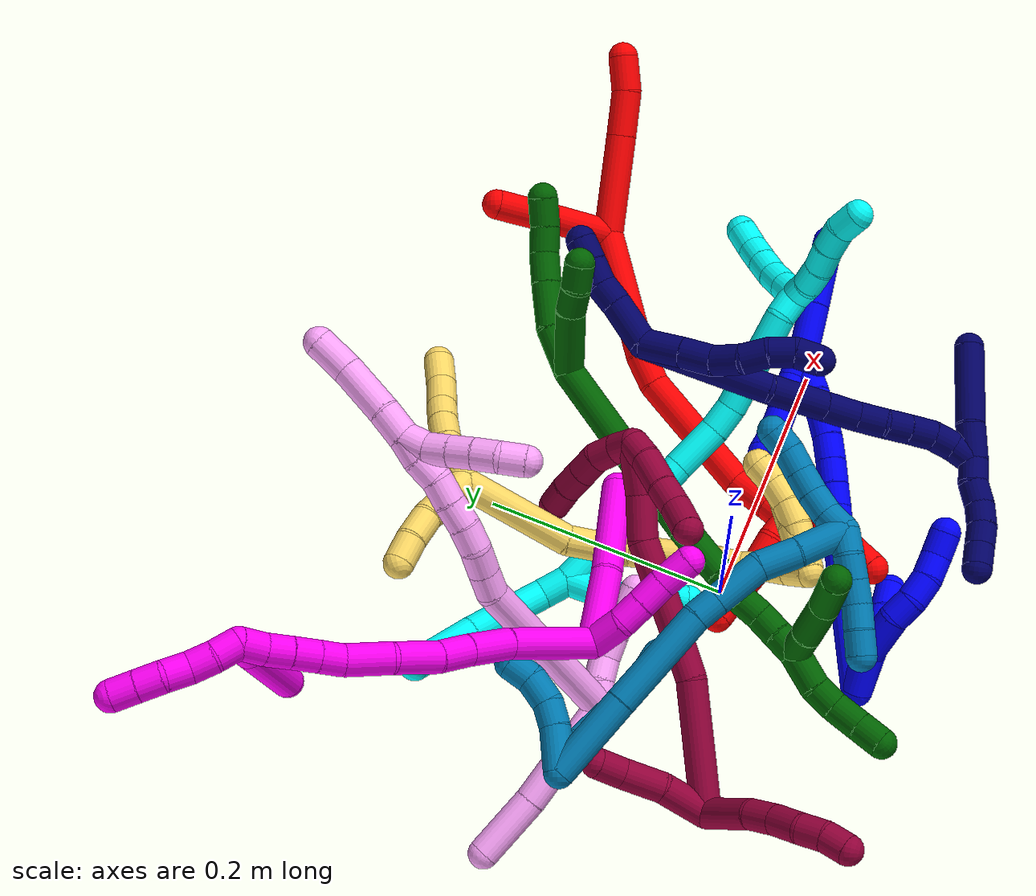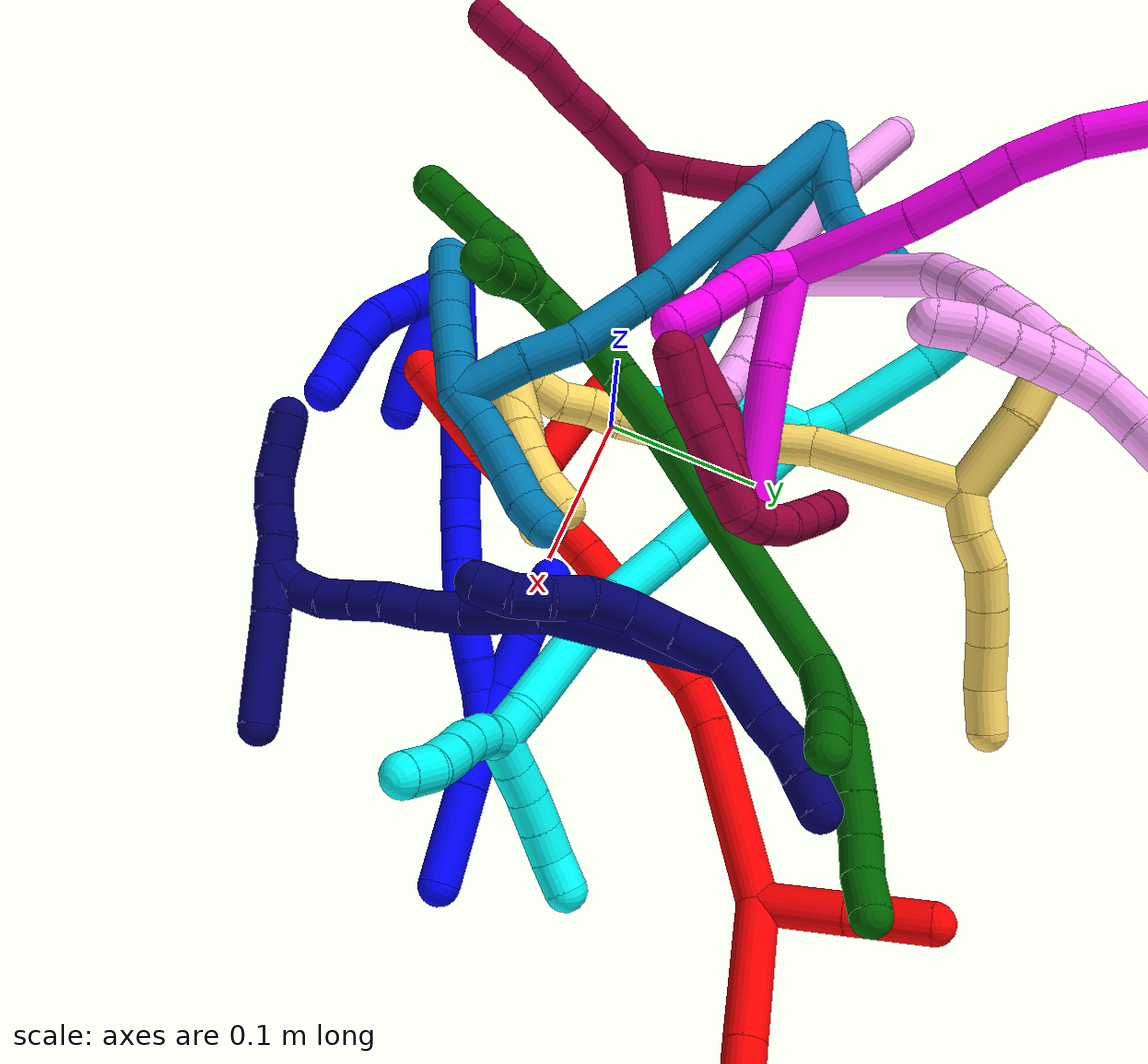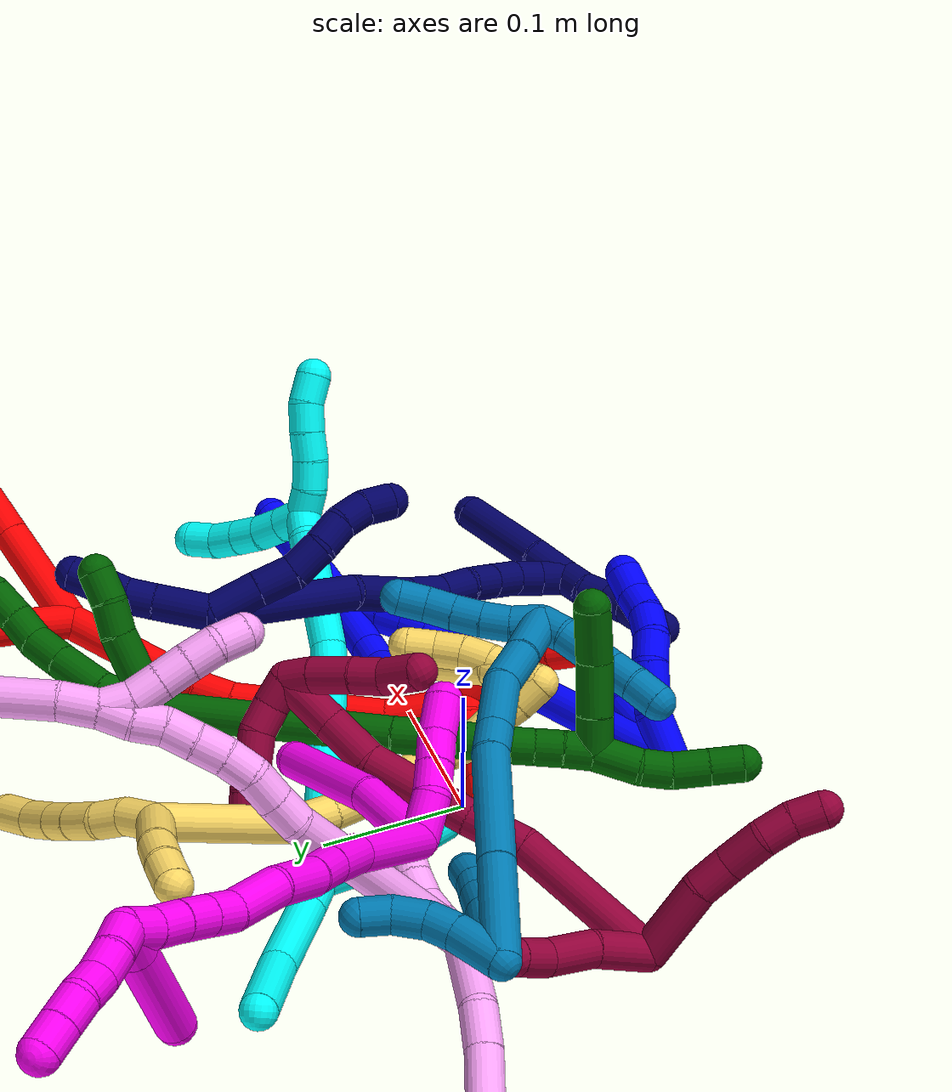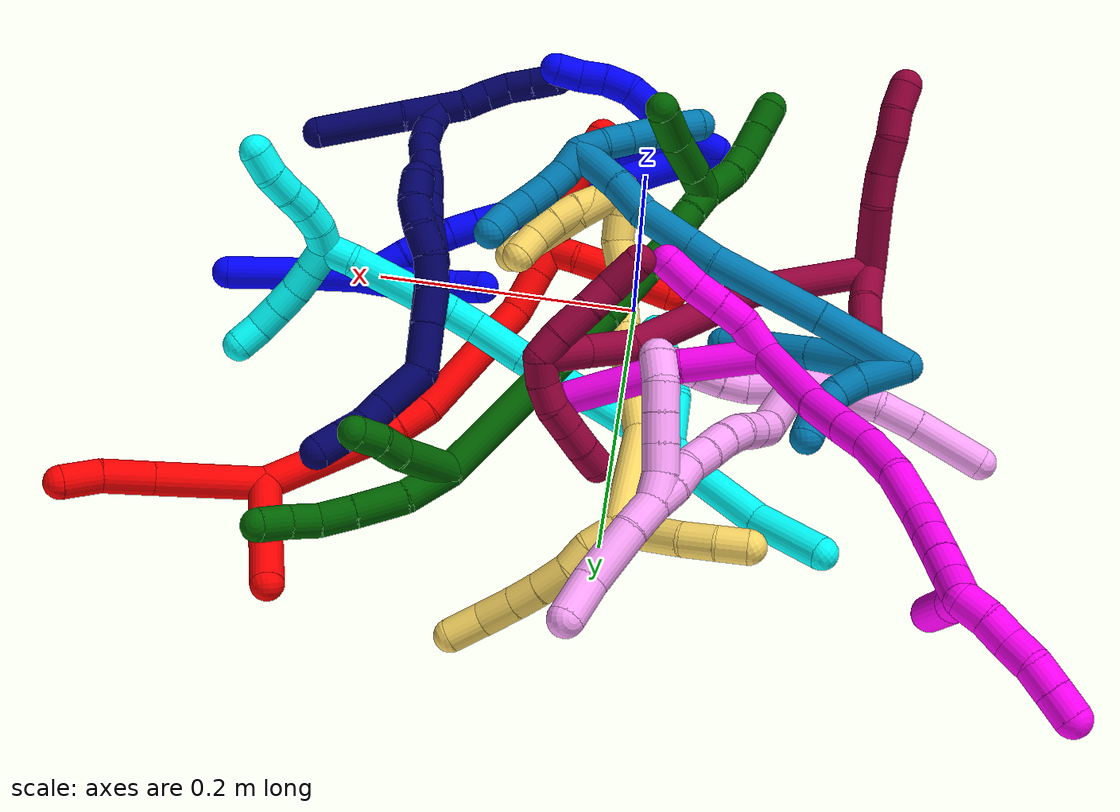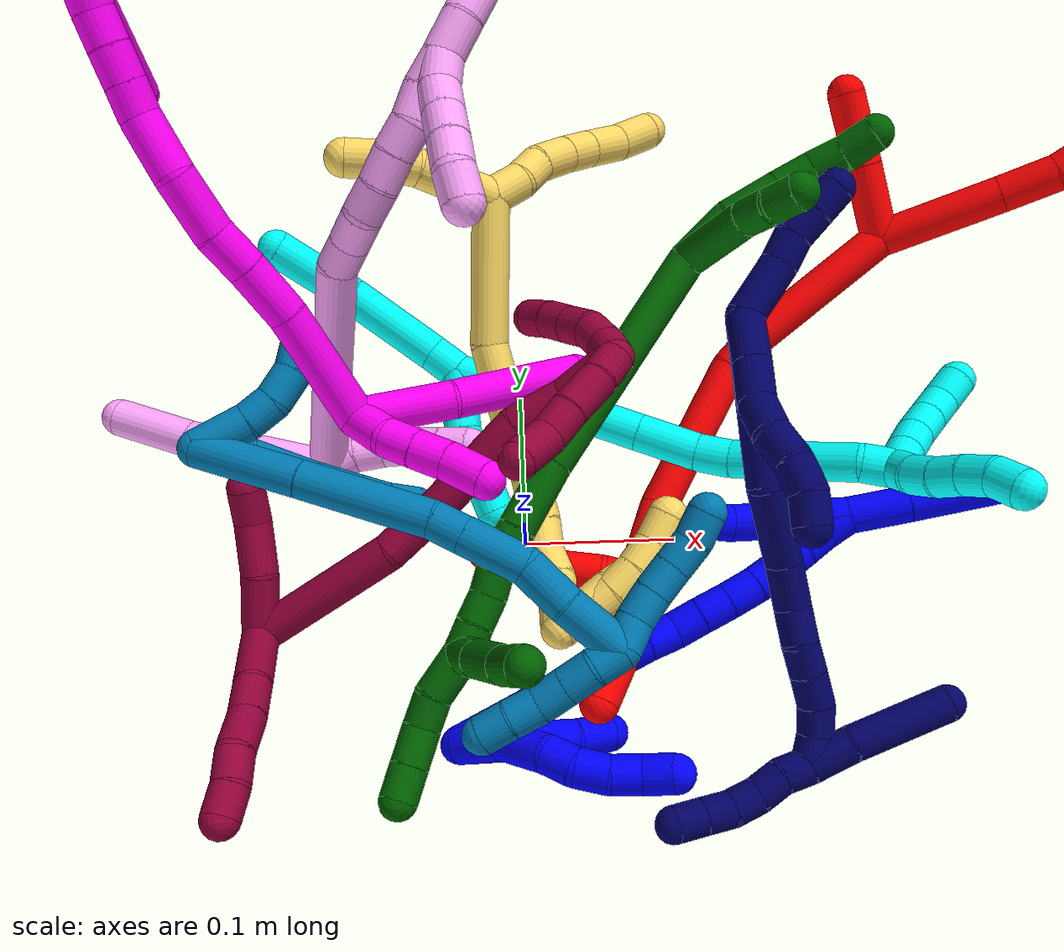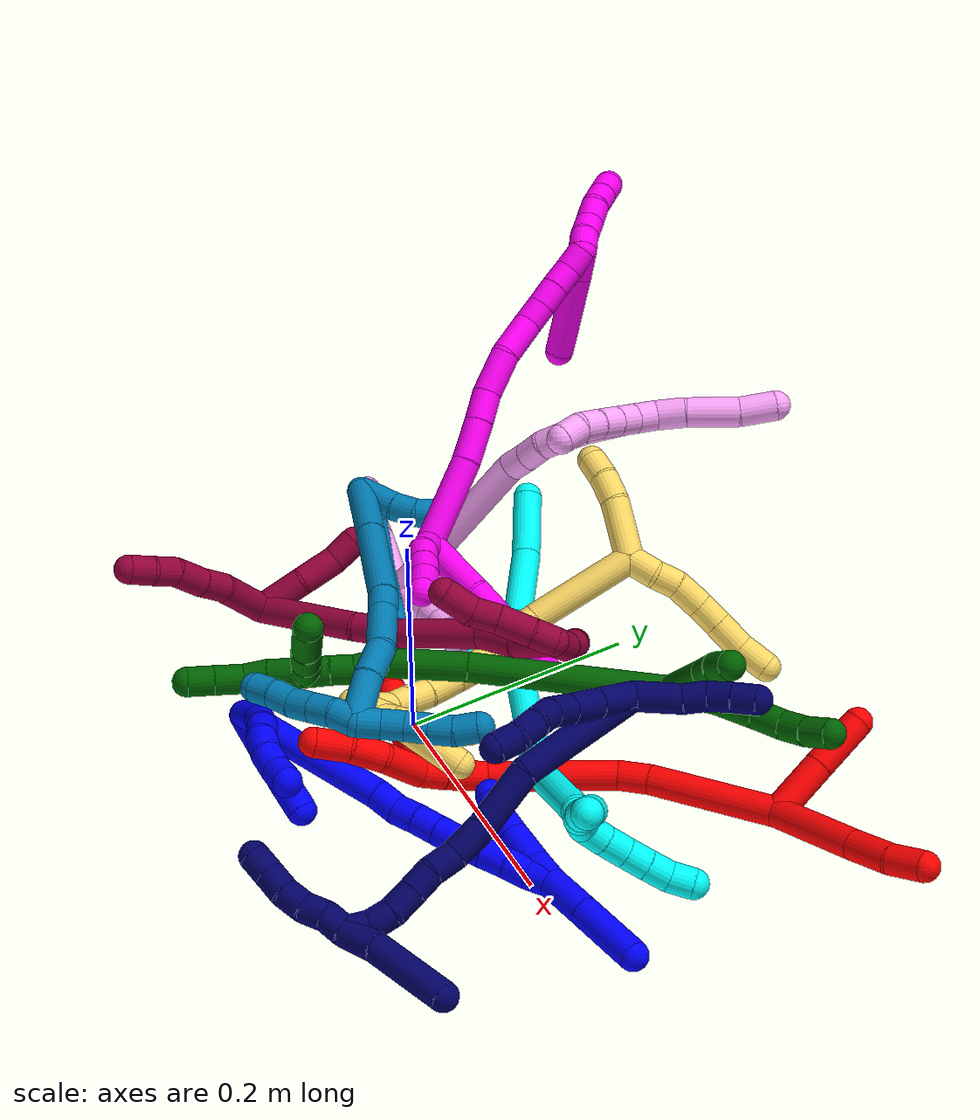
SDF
<sdf version="1.7">
 <world name="default">
  <plugin name="TubeGeneratorPlugin" filename="libtube_generator_plugin.so"/>
  <model name="photoneo_s_sensor">
   <static>1</static>
   <pose>0 0 2 1.57079 1.57079 3.14159</pose>
   <link name="link">
    <inertial><mass>0.1</mass></inertial>
    <sensor name="sensor" type="depth">
     <update_rate>30</update_rate>
     <camera>
      <horizontal_fov>1.22</horizontal_fov>
      <image><width>1920</width><height>1200</height><format>B8G8R8</format></image>
      <clip><near>0.1</near><far>4</far></clip>
      <depth_camera><output>points</output></depth_camera>
     </camera>
     <plugin name="camera_plugin" filename="libgazebo_ros_depth_camera.so">
      <baseline>0.2</baseline>
      <alwaysOn>1</alwaysOn>
      <updateRate>0.0</updateRate>
      <cameraName>camera_ir</cameraName>
      <imageTopicName>/camera/color/image_raw</imageTopicName>
      <cameraInfoTopicName>/camera/color/camera_info</cameraInfoTopicName>
      <depthImageTopicName>/camera/depth/image_raw</depthImageTopicName>
      <depthImageCameraInfoTopicName>/camera/depth/camera_info</depthImageCameraInfoTopicName>
      <pointCloudTopicName>/camera/depth/points</pointCloudTopicName>
      <frameName>fr_optical</frameName>
      <pointCloudCutoff>0.1</pointCloudCutoff>
      <pointCloudCutoffMax>2.0</pointCloudCutoffMax>
      <distortionK1>0</distortionK1>
      <distortionK2>0</distortionK2>
      <distortionK3>0</distortionK3>
      <distortionT1>0</distortionT1>
      <distortionT2>0</distortionT2>
      <CxPrime>0</CxPrime>
      <Cx>0</Cx>
      <Cy>0</Cy>
      <focalLength>0</focalLength>
      <hackBaseline>0</hackBaseline>
     </plugin>
    </sensor>
   </link>
  </model>
  <gravity>0 0 -9.8</gravity>
  <magnetic_field>6e-06 2.3e-05 -4.2e-05</magnetic_field>
  <atmosphere type="adiabatic"/>
  <physics name="default_physics" default="0" type="ode">
   <max_step_size>0.003</max_step_size>
   <real_time_factor>1</real_time_factor>
   <real_time_update_rate>1000</real_time_update_rate>
   <max_contacts>10000</max_contacts>
   <ode>
    <solver>
     <type>quick</type>
     <iters>100</iters>
     <sor>1.3</sor>
     <use_dynamic_moi_rescaling>0</use_dynamic_moi_rescaling>
    </solver>
    <constraints>
     <contact_max_correcting_vel>0</contact_max_correcting_vel>
     <contact_surface_layer>0.001</contact_surface_layer>
     <cfm>0</cfm>
     <erp>0.2</erp>
    </constraints>
   </ode>
  </physics>
  <scene><ambient>0.4 0.4 0.4 1</ambient><background>0.7 0.7 0.7 1</background><shadows>0</shadows></scene>
  <audio><device>default</device></audio>
  <spherical_coordinates>
   <surface_model>EARTH_WGS84</surface_model>
   <latitude_deg>0</latitude_deg>
   <longitude_deg>0</longitude_deg>
   <elevation>0</elevation>
   <heading_deg>0</heading_deg>
  </spherical_coordinates>
  <model name="bin">
   <static>1</static>
   <link name="bottom">
    <collision name="collision-bottom">
     <pose>0 0 -0.01 0 -0 0</pose>
     <geometry><box><size>0.8 0.6 0.02</size></box></geometry>
     <surface>
      <friction><ode><mu>100</mu><mu2>100</mu2></ode></friction>
      <contact><collide_bitmask>65535</collide_bitmask></contact>
     </surface>
    </collision>
   </link>
   <link name="west_wall">
    <collision name="collision-west_wall">
     <pose>-0.41 0 0.1 0 -0 0</pose>
     <geometry><box><size>0.02 0.6 0.2</size></box></geometry>
     <surface>
      <friction><ode><mu>100</mu><mu2>100</mu2></ode></friction>
      <contact><collide_bitmask>65535</collide_bitmask></contact>
     </surface>
    </collision>
   </link>
   <link name="east_wall">
    <collision name="collision-east_wall">
     <pose>0.41 0 0.1 0 -0 0</pose>
     <geometry><box><size>0.02 0.6 0.2</size></box></geometry>
     <surface>
      <friction><ode><mu>100</mu><mu2>100</mu2></ode></friction>
      <contact><collide_bitmask>65535</collide_bitmask></contact>
     </surface>
    </collision>
   </link>
   <link name="south_wall">
    <collision name="collision-south_wall">
     <pose>0 -0.31 0.1 0 -0 0</pose>
     <geometry><box><size>0.8 0.02 0.2</size></box></geometry>
     <surface>
      <friction><ode><mu>100</mu><mu2>100</mu2></ode></friction>
      <contact><collide_bitmask>65535</collide_bitmask></contact>
     </surface>
    </collision>
   </link>
   <link name="north_wall">
    <collision name="collision-north_wall">
     <pose>0 0.31 0.1 0 -0 0</pose>
     <geometry><box><size>0.8 0.02 0.2</size></box></geometry>
     <surface>
      <friction><ode><mu>100</mu><mu2>100</mu2></ode></friction>
      <contact><collide_bitmask>65535</collide_bitmask></contact>
     </surface>
    </collision>
   </link>
  </model>
  <model name="1">
   <static>0</static>
   <link name="1">
    <collision name="collision-cylinder-e_1_2_8">
     <pose>0.010154 -2.2e-05 -0.013263 3.13991 0.653395 3.13664</pose>
     <geometry><cylinder><radius>0.0125</radius><length>0.033408</length></cylinder></geometry>
     <surface>
      <friction><ode><mu>1.16</mu><mu2>1.16</mu2><slip1>0</slip1><slip2>0</slip2></ode></friction>
      <contact><ode><kp>1e+06</kp><kd>1</kd><max_vel>0</max_vel><min_depth>0.001</min_depth></ode></contact>
     </surface>
    </collision>
    <visual name="visual-cylinder-e_1_2_8">
     <pose>0.010154 -2.2e-05 -0.013263 3.13991 0.653395 3.13664</pose>
     <geometry><cylinder><radius>0.0125</radius><length>0.033408</length></cylinder></geometry>
     <material><ambient>0 0 1 1</ambient></material>
    </visual>
    <collision name="collision-cylinder-e_2_8_9">
     <pose>0.030593 -0.00555 -0.039935 2.75197 0.617085 2.03292</pose>
     <geometry><cylinder><radius>0.0125</radius><length>0.035546</length></cylinder></geometry>
     <surface>
      <friction><ode><mu>1.16</mu><mu2>1.16</mu2><slip1>0</slip1><slip2>0</slip2></ode></friction>
      <contact><ode><kp>1e+06</kp><kd>1</kd><max_vel>0</max_vel><min_depth>0.001</min_depth></ode></contact>
     </surface>
    </collision>
    <visual name="visual-cylinder-e_2_8_9">
     <pose>0.030593 -0.00555 -0.039935 2.75197 0.617085 2.03292</pose>
     <geometry><cylinder><radius>0.0125</radius><length>0.035546</length></cylinder></geometry>
     <material><ambient>0 0 1 1</ambient></material>
    </visual>
    <collision name="collision-cylinder-e_3_9_10">
     <pose>0.04416 -0.015522 -0.061778 2.65465 0.331338 1.18491</pose>
     <geometry><cylinder><radius>0.0125</radius><length>0.020185</length></cylinder></geometry>
     <surface>
      <friction><ode><mu>1.16</mu><mu2>1.16</mu2><slip1>0</slip1><slip2>0</slip2></ode></friction>
      <contact><ode><kp>1e+06</kp><kd>1</kd><max_vel>0</max_vel><min_depth>0.001</min_depth></ode></contact>
     </surface>
    </collision>
    <visual name="visual-cylinder-e_3_9_10">
     <pose>0.04416 -0.015522 -0.061778 2.65465 0.331338 1.18491</pose>
     <geometry><cylinder><radius>0.0125</radius><length>0.020185</length></cylinder></geometry>
     <material><ambient>0 0 1 1</ambient></material>
    </visual>
    <collision name="collision-cylinder-e_4_10_11">
     <pose>0.048526 -0.022333 -0.080315 2.91348 0.10402 0.853071</pose>
     <geometry><cylinder><radius>0.0125</radius><length>0.020855</length></cylinder></geometry>
     <surface>
      <friction><ode><mu>1.16</mu><mu2>1.16</mu2><slip1>0</slip1><slip2>0</slip2></ode></friction>
      <contact><ode><kp>1e+06</kp><kd>1</kd><max_vel>0</max_vel><min_depth>0.001</min_depth></ode></contact>
     </surface>
    </collision>
    <visual name="visual-cylinder-e_4_10_11">
     <pose>0.048526 -0.022333 -0.080315 2.91348 0.10402 0.853071</pose>
     <geometry><cylinder><radius>0.0125</radius><length>0.020855</length></cylinder></geometry>
     <material><ambient>0 0 1 1</ambient></material>
    </visual>
    <collision name="collision-cylinder-e_5_11_12">
     <pose>0.049992 -0.024627 -0.100413 -3.13648 0.038357 -2.87679</pose>
     <geometry><cylinder><radius>0.0125</radius><length>0.020006</length></cylinder></geometry>
     <surface>
      <friction><ode><mu>1.16</mu><mu2>1.16</mu2><slip1>0</slip1><slip2>0</slip2></ode></friction>
      <contact><ode><kp>1e+06</kp><kd>1</kd><max_vel>0</max_vel><min_depth>0.001</min_depth></ode></contact>
     </surface>
    </collision>
    <visual name="visual-cylinder-e_5_11_12">
     <pose>0.049992 -0.024627 -0.100413 -3.13648 0.038357 -2.87679</pose>
     <geometry><cylinder><radius>0.0125</radius><length>0.020006</length></cylinder></geometry>
     <material><ambient>0 0 1 1</ambient></material>
    </visual>
    <collision name="collision-cylinder-e_6_12_6">
     <pose>0.053369 -0.02475 -0.119949 3.12335 0.303952 3.02261</pose>
     <geometry><cylinder><radius>0.0125</radius><length>0.02</length></cylinder></geometry>
     <surface>
      <friction><ode><mu>1.16</mu><mu2>1.16</mu2><slip1>0</slip1><slip2>0</slip2></ode></friction>
      <contact><ode><kp>1e+06</kp><kd>1</kd><max_vel>0</max_vel><min_depth>0.001</min_depth></ode></contact>
     </surface>
    </collision>
    <visual name="visual-cylinder-e_6_12_6">
     <pose>0.053369 -0.02475 -0.119949 3.12335 0.303952 3.02261</pose>
     <geometry><cylinder><radius>0.0125</radius><length>0.02</length></cylinder></geometry>
     <material><ambient>0 0 1 1</ambient></material>
    </visual>
    <collision name="collision-cylinder-e_1_2_13">
     <pose>-0.003343 0.001472 -0.017881 -3.05945 -0.184245 2.30454</pose>
     <geometry><cylinder><radius>0.0125</radius><length>0.0365</length></cylinder></geometry>
     <surface>
      <friction><ode><mu>1.16</mu><mu2>1.16</mu2><slip1>0</slip1><slip2>0</slip2></ode></friction>
      <contact><ode><kp>1e+06</kp><kd>1</kd><max_vel>0</max_vel><min_depth>0.001</min_depth></ode></contact>
     </surface>
    </collision>
    <visual name="visual-cylinder-e_1_2_13">
     <pose>-0.003343 0.001472 -0.017881 -3.05945 -0.184245 2.30454</pose>
     <geometry><cylinder><radius>0.0125</radius><length>0.0365</length></cylinder></geometry>
     <material><ambient>0 0 1 1</ambient></material>
    </visual>
    <collision name="collision-cylinder-e_2_13_14">
     <pose>-0.009776 0.004515 -0.055322 -3.06144 -0.156161 2.19436</pose>
     <geometry><cylinder><radius>0.0125</radius><length>0.03973</length></cylinder></geometry>
     <surface>
      <friction><ode><mu>1.16</mu><mu2>1.16</mu2><slip1>0</slip1><slip2>0</slip2></ode></friction>
      <contact><ode><kp>1e+06</kp><kd>1</kd><max_vel>0</max_vel><min_depth>0.001</min_depth></ode></contact>
     </surface>
    </collision>
    <visual name="visual-cylinder-e_2_13_14">
     <pose>-0.009776 0.004515 -0.055322 -3.06144 -0.156161 2.19436</pose>
     <geometry><cylinder><radius>0.0125</radius><length>0.03973</length></cylinder></geometry>
     <material><ambient>0 0 1 1</ambient></material>
    </visual>
    <collision name="collision-cylinder-e_3_14_5">
     <pose>-0.016782 0.008408 -0.085861 -2.93323 -0.335729 2.0359</pose>
     <geometry><cylinder><radius>0.0125</radius><length>0.02377</length></cylinder></geometry>
     <surface>
      <friction><ode><mu>1.16</mu><mu2>1.16</mu2><slip1>0</slip1><slip2>0</slip2></ode></friction>
      <contact><ode><kp>1e+06</kp><kd>1</kd><max_vel>0</max_vel><min_depth>0.001</min_depth></ode></contact>
     </surface>
    </collision>
    <visual name="visual-cylinder-e_3_14_5">
     <pose>-0.016782 0.008408 -0.085861 -2.93323 -0.335729 2.0359</pose>
     <geometry><cylinder><radius>0.0125</radius><length>0.02377</length></cylinder></geometry>
     <material><ambient>0 0 1 1</ambient></material>
    </visual>
    <collision name="collision-cylinder-e_1_2_15">
     <pose>0.001128 0.032516 -0.059985 -2.64487 0.016531 -0.065163</pose>
     <geometry><cylinder><radius>0.0125</radius><length>0.136481</length></cylinder></geometry>
     <surface>
      <friction><ode><mu>1.16</mu><mu2>1.16</mu2><slip1>0</slip1><slip2>0</slip2></ode></friction>
      <contact><ode><kp>1e+06</kp><kd>1</kd><max_vel>0</max_vel><min_depth>0.001</min_depth></ode></contact>
     </surface>
    </collision>
    <visual name="visual-cylinder-e_1_2_15">
     <pose>0.001128 0.032516 -0.059985 -2.64487 0.016531 -0.065163</pose>
     <geometry><cylinder><radius>0.0125</radius><length>0.136481</length></cylinder></geometry>
     <material><ambient>0 0 1 1</ambient></material>
    </visual>
    <collision name="collision-cylinder-e_2_15_16">
     <pose>0.001126 0.069442 -0.129471 -2.70691 -0.107491 0.477914</pose>
     <geometry><cylinder><radius>0.0125</radius><length>0.02107</length></cylinder></geometry>
     <surface>
      <friction><ode><mu>1.16</mu><mu2>1.16</mu2><slip1>0</slip1><slip2>0</slip2></ode></friction>
      <contact><ode><kp>1e+06</kp><kd>1</kd><max_vel>0</max_vel><min_depth>0.001</min_depth></ode></contact>
     </surface>
    </collision>
    <visual name="visual-cylinder-e_2_15_16">
     <pose>0.001126 0.069442 -0.129471 -2.70691 -0.107491 0.477914</pose>
     <geometry><cylinder><radius>0.0125</radius><length>0.02107</length></cylinder></geometry>
     <material><ambient>0 0 1 1</ambient></material>
    </visual>
    <collision name="collision-cylinder-e_3_16_17">
     <pose>0.001583 0.078564 -0.147709 -2.64716 0.158537 -0.60986</pose>
     <geometry><cylinder><radius>0.0125</radius><length>0.020106</length></cylinder></geometry>
     <surface>
      <friction><ode><mu>1.16</mu><mu2>1.16</mu2><slip1>0</slip1><slip2>0</slip2></ode></friction>
      <contact><ode><kp>1e+06</kp><kd>1</kd><max_vel>0</max_vel><min_depth>0.001</min_depth></ode></contact>
     </surface>
    </collision>
    <visual name="visual-cylinder-e_3_16_17">
     <pose>0.001583 0.078564 -0.147709 -2.64716 0.158537 -0.60986</pose>
     <geometry><cylinder><radius>0.0125</radius><length>0.020106</length></cylinder></geometry>
     <material><ambient>0 0 1 1</ambient></material>
    </visual>
    <collision name="collision-cylinder-e_4_17_18">
     <pose>0.003983 0.087984 -0.165449 -2.65958 0.07989 -0.322397</pose>
     <geometry><cylinder><radius>0.0125</radius><length>0.020384</length></cylinder></geometry>
     <surface>
      <friction><ode><mu>1.16</mu><mu2>1.16</mu2><slip1>0</slip1><slip2>0</slip2></ode></friction>
      <contact><ode><kp>1e+06</kp><kd>1</kd><max_vel>0</max_vel><min_depth>0.001</min_depth></ode></contact>
     </surface>
    </collision>
    <visual name="visual-cylinder-e_4_17_18">
     <pose>0.003983 0.087984 -0.165449 -2.65958 0.07989 -0.322397</pose>
     <geometry><cylinder><radius>0.0125</radius><length>0.020384</length></cylinder></geometry>
     <material><ambient>0 0 1 1</ambient></material>
    </visual>
    <collision name="collision-cylinder-e_5_18_19">
     <pose>0.005445 0.097984 -0.18372 -2.62291 0.060726 -0.227964</pose>
     <geometry><cylinder><radius>0.0125</radius><length>0.021383</length></cylinder></geometry>
     <surface>
      <friction><ode><mu>1.16</mu><mu2>1.16</mu2><slip1>0</slip1><slip2>0</slip2></ode></friction>
      <contact><ode><kp>1e+06</kp><kd>1</kd><max_vel>0</max_vel><min_depth>0.001</min_depth></ode></contact>
     </surface>
    </collision>
    <visual name="visual-cylinder-e_5_18_19">
     <pose>0.005445 0.097984 -0.18372 -2.62291 0.060726 -0.227964</pose>
     <geometry><cylinder><radius>0.0125</radius><length>0.021383</length></cylinder></geometry>
     <material><ambient>0 0 1 1</ambient></material>
    </visual>
    <collision name="collision-cylinder-e_6_19_20">
     <pose>0.006361 0.109059 -0.201166 -2.52591 0.02663 -0.083712</pose>
     <geometry><cylinder><radius>0.0125</radius><length>0.020042</length></cylinder></geometry>
     <surface>
      <friction><ode><mu>1.16</mu><mu2>1.16</mu2><slip1>0</slip1><slip2>0</slip2></ode></friction>
      <contact><ode><kp>1e+06</kp><kd>1</kd><max_vel>0</max_vel><min_depth>0.001</min_depth></ode></contact>
     </surface>
    </collision>
    <visual name="visual-cylinder-e_6_19_20">
     <pose>0.006361 0.109059 -0.201166 -2.52591 0.02663 -0.083712</pose>
     <geometry><cylinder><radius>0.0125</radius><length>0.020042</length></cylinder></geometry>
     <material><ambient>0 0 1 1</ambient></material>
    </visual>
    <collision name="collision-cylinder-e_7_20_21">
     <pose>0.006708 0.121075 -0.217314 -2.47815 0.007911 -0.022966</pose>
     <geometry><cylinder><radius>0.0125</radius><length>0.020234</length></cylinder></geometry>
     <surface>
      <friction><ode><mu>1.16</mu><mu2>1.16</mu2><slip1>0</slip1><slip2>0</slip2></ode></friction>
      <contact><ode><kp>1e+06</kp><kd>1</kd><max_vel>0</max_vel><min_depth>0.001</min_depth></ode></contact>
     </surface>
    </collision>
    <visual name="visual-cylinder-e_7_20_21">
     <pose>0.006708 0.121075 -0.217314 -2.47815 0.007911 -0.022966</pose>
     <geometry><cylinder><radius>0.0125</radius><length>0.020234</length></cylinder></geometry>
     <material><ambient>0 0 1 1</ambient></material>
    </visual>
    <collision name="collision-cylinder-e_8_21_22">
     <pose>0.005782 0.133655 -0.232968 -2.45087 -0.100613 0.278083</pose>
     <geometry><cylinder><radius>0.0125</radius><length>0.020035</length></cylinder></geometry>
     <surface>
      <friction><ode><mu>1.16</mu><mu2>1.16</mu2><slip1>0</slip1><slip2>0</slip2></ode></friction>
      <contact><ode><kp>1e+06</kp><kd>1</kd><max_vel>0</max_vel><min_depth>0.001</min_depth></ode></contact>
     </surface>
    </collision>
    <visual name="visual-cylinder-e_8_21_22">
     <pose>0.005782 0.133655 -0.232968 -2.45087 -0.100613 0.278083</pose>
     <geometry><cylinder><radius>0.0125</radius><length>0.020035</length></cylinder></geometry>
     <material><ambient>0 0 1 1</ambient></material>
    </visual>
    <collision name="collision-cylinder-e_9_22_1">
     <pose>0.006831 0.145375 -0.248992 -2.56962 0.204322 -0.670939</pose>
     <geometry><cylinder><radius>0.0125</radius><length>0.020265</length></cylinder></geometry>
     <surface>
      <friction><ode><mu>1.16</mu><mu2>1.16</mu2><slip1>0</slip1><slip2>0</slip2></ode></friction>
      <contact><ode><kp>1e+06</kp><kd>1</kd><max_vel>0</max_vel><min_depth>0.001</min_depth></ode></contact>
     </surface>
    </collision>
    <visual name="visual-cylinder-e_9_22_1">
     <pose>0.006831 0.145375 -0.248992 -2.56962 0.204322 -0.670939</pose>
     <geometry><cylinder><radius>0.0125</radius><length>0.020265</length></cylinder></geometry>
     <material><ambient>0 0 1 1</ambient></material>
    </visual>
    <collision name="collision-cylinder-e_1_1_23">
     <pose>0.011875 0.15402 -0.277187 -2.97811 0.147411 -1.46711</pose>
     <geometry><cylinder><radius>0.0125</radius><length>0.040682</length></cylinder></geometry>
     <surface>
      <friction><ode><mu>1.16</mu><mu2>1.16</mu2><slip1>0</slip1><slip2>0</slip2></ode></friction>
      <contact><ode><kp>1e+06</kp><kd>1</kd><max_vel>0</max_vel><min_depth>0.001</min_depth></ode></contact>
     </surface>
    </collision>
    <visual name="visual-cylinder-e_1_1_23">
     <pose>0.011875 0.15402 -0.277187 -2.97811 0.147411 -1.46711</pose>
     <geometry><cylinder><radius>0.0125</radius><length>0.040682</length></cylinder></geometry>
     <material><ambient>0 0 1 1</ambient></material>
    </visual>
    <collision name="collision-cylinder-e_2_23_4">
     <pose>0.018392 0.162606 -0.326004 -2.96022 0.119269 -1.16195</pose>
     <geometry><cylinder><radius>0.0125</radius><length>0.059318</length></cylinder></geometry>
     <surface>
      <friction><ode><mu>1.16</mu><mu2>1.16</mu2><slip1>0</slip1><slip2>0</slip2></ode></friction>
      <contact><ode><kp>1e+06</kp><kd>1</kd><max_vel>0</max_vel><min_depth>0.001</min_depth></ode></contact>
     </surface>
    </collision>
    <visual name="visual-cylinder-e_2_23_4">
     <pose>0.018392 0.162606 -0.326004 -2.96022 0.119269 -1.16195</pose>
     <geometry><cylinder><radius>0.0125</radius><length>0.059318</length></cylinder></geometry>
     <material><ambient>0 0 1 1</ambient></material>
    </visual>
    <collision name="collision-cylinder-e_1_1_24">
     <pose>0.007339 0.150397 -0.245183 0.028659 -0.126708 -0.001818</pose>
     <geometry><cylinder><radius>0.0125</radius><length>0.02451</length></cylinder></geometry>
     <surface>
      <friction><ode><mu>1.16</mu><mu2>1.16</mu2><slip1>0</slip1><slip2>0</slip2></ode></friction>
      <contact><ode><kp>1e+06</kp><kd>1</kd><max_vel>0</max_vel><min_depth>0.001</min_depth></ode></contact>
     </surface>
    </collision>
    <visual name="visual-cylinder-e_1_1_24">
     <pose>0.007339 0.150397 -0.245183 0.028659 -0.126708 -0.001818</pose>
     <geometry><cylinder><radius>0.0125</radius><length>0.02451</length></cylinder></geometry>
     <material><ambient>0 0 1 1</ambient></material>
    </visual>
    <collision name="collision-cylinder-e_2_24_25">
     <pose>0.005781 0.148694 -0.216282 0.080677 -0.000536 -2.2e-05</pose>
     <geometry><cylinder><radius>0.0125</radius><length>0.033607</length></cylinder></geometry>
     <surface>
      <friction><ode><mu>1.16</mu><mu2>1.16</mu2><slip1>0</slip1><slip2>0</slip2></ode></friction>
      <contact><ode><kp>1e+06</kp><kd>1</kd><max_vel>0</max_vel><min_depth>0.001</min_depth></ode></contact>
     </surface>
    </collision>
    <visual name="visual-cylinder-e_2_24_25">
     <pose>0.005781 0.148694 -0.216282 0.080677 -0.000536 -2.2e-05</pose>
     <geometry><cylinder><radius>0.0125</radius><length>0.033607</length></cylinder></geometry>
     <material><ambient>0 0 1 1</ambient></material>
    </visual>
    <collision name="collision-cylinder-e_3_25_26">
     <pose>0.005883 0.146667 -0.188999 0.063798 0.010476 0.000334</pose>
     <geometry><cylinder><radius>0.0125</radius><length>0.021113</length></cylinder></geometry>
     <surface>
      <friction><ode><mu>1.16</mu><mu2>1.16</mu2><slip1>0</slip1><slip2>0</slip2></ode></friction>
      <contact><ode><kp>1e+06</kp><kd>1</kd><max_vel>0</max_vel><min_depth>0.001</min_depth></ode></contact>
     </surface>
    </collision>
    <visual name="visual-cylinder-e_3_25_26">
     <pose>0.005883 0.146667 -0.188999 0.063798 0.010476 0.000334</pose>
     <geometry><cylinder><radius>0.0125</radius><length>0.021113</length></cylinder></geometry>
     <material><ambient>0 0 1 1</ambient></material>
    </visual>
    <collision name="collision-cylinder-e_4_26_3">
     <pose>0.009436 0.145968 -0.168667 0.002676 0.337908 0.000456</pose>
     <geometry><cylinder><radius>0.0125</radius><length>0.02077</length></cylinder></geometry>
     <surface>
      <friction><ode><mu>1.16</mu><mu2>1.16</mu2><slip1>0</slip1><slip2>0</slip2></ode></friction>
      <contact><ode><kp>1e+06</kp><kd>1</kd><max_vel>0</max_vel><min_depth>0.001</min_depth></ode></contact>
     </surface>
    </collision>
    <visual name="visual-cylinder-e_4_26_3">
     <pose>0.009436 0.145968 -0.168667 0.002676 0.337908 0.000456</pose>
     <geometry><cylinder><radius>0.0125</radius><length>0.02077</length></cylinder></geometry>
     <material><ambient>0 0 1 1</ambient></material>
    </visual>
    <collision name="collision-sphere-3">
     <pose>0.012879 0.145942 -0.158869 0 -0 0</pose>
     <geometry><sphere><radius>0.0125</radius></sphere></geometry>
     <surface>
      <friction><ode><mu>1.16</mu><mu2>1.16</mu2><slip1>0</slip1><slip2>0</slip2></ode></friction>
      <contact><ode><kp>1e+06</kp><kd>1</kd><max_vel>0</max_vel><min_depth>0.001</min_depth></ode></contact>
     </surface>
    </collision>
    <visual name="visual-sphere-3">
     <pose>0.012879 0.145942 -0.158869 0 -0 0</pose>
     <geometry><sphere><radius>0.0125</radius></sphere></geometry>
     <material><ambient>0 0 1 1</ambient></material>
    </visual>
    <collision name="collision-sphere-26">
     <pose>0.005993 0.145994 -0.178465 0 -0 0</pose>
     <geometry><sphere><radius>0.0125</radius></sphere></geometry>
     <surface>
      <friction><ode><mu>1.16</mu><mu2>1.16</mu2><slip1>0</slip1><slip2>0</slip2></ode></friction>
      <contact><ode><kp>1e+06</kp><kd>1</kd><max_vel>0</max_vel><min_depth>0.001</min_depth></ode></contact>
     </surface>
    </collision>
    <visual name="visual-sphere-26">
     <pose>0.005993 0.145994 -0.178465 0 -0 0</pose>
     <geometry><sphere><radius>0.0125</radius></sphere></geometry>
     <material><ambient>0 0 1 1</ambient></material>
    </visual>
    <collision name="collision-sphere-25">
     <pose>0.005772 0.14734 -0.199534 0 -0 0</pose>
     <geometry><sphere><radius>0.0125</radius></sphere></geometry>
     <surface>
      <friction><ode><mu>1.16</mu><mu2>1.16</mu2><slip1>0</slip1><slip2>0</slip2></ode></friction>
      <contact><ode><kp>1e+06</kp><kd>1</kd><max_vel>0</max_vel><min_depth>0.001</min_depth></ode></contact>
     </surface>
    </collision>
    <visual name="visual-sphere-25">
     <pose>0.005772 0.14734 -0.199534 0 -0 0</pose>
     <geometry><sphere><radius>0.0125</radius></sphere></geometry>
     <material><ambient>0 0 1 1</ambient></material>
    </visual>
    <collision name="collision-sphere-24">
     <pose>0.00579 0.150049 -0.233031 0 -0 0</pose>
     <geometry><sphere><radius>0.0125</radius></sphere></geometry>
     <surface>
      <friction><ode><mu>1.16</mu><mu2>1.16</mu2><slip1>0</slip1><slip2>0</slip2></ode></friction>
      <contact><ode><kp>1e+06</kp><kd>1</kd><max_vel>0</max_vel><min_depth>0.001</min_depth></ode></contact>
     </surface>
    </collision>
    <visual name="visual-sphere-24">
     <pose>0.00579 0.150049 -0.233031 0 -0 0</pose>
     <geometry><sphere><radius>0.0125</radius></sphere></geometry>
     <material><ambient>0 0 1 1</ambient></material>
    </visual>
    <collision name="collision-sphere-4">
     <pose>0.021921 0.167918 -0.354969 0 -0 0</pose>
     <geometry><sphere><radius>0.0125</radius></sphere></geometry>
     <surface>
      <friction><ode><mu>1.16</mu><mu2>1.16</mu2><slip1>0</slip1><slip2>0</slip2></ode></friction>
      <contact><ode><kp>1e+06</kp><kd>1</kd><max_vel>0</max_vel><min_depth>0.001</min_depth></ode></contact>
     </surface>
    </collision>
    <visual name="visual-sphere-4">
     <pose>0.021921 0.167918 -0.354969 0 -0 0</pose>
     <geometry><sphere><radius>0.0125</radius></sphere></geometry>
     <material><ambient>0 0 1 1</ambient></material>
    </visual>
    <collision name="collision-sphere-23">
     <pose>0.014863 0.157295 -0.297039 0 -0 0</pose>
     <geometry><sphere><radius>0.0125</radius></sphere></geometry>
     <surface>
      <friction><ode><mu>1.16</mu><mu2>1.16</mu2><slip1>0</slip1><slip2>0</slip2></ode></friction>
      <contact><ode><kp>1e+06</kp><kd>1</kd><max_vel>0</max_vel><min_depth>0.001</min_depth></ode></contact>
     </surface>
    </collision>
    <visual name="visual-sphere-23">
     <pose>0.014863 0.157295 -0.297039 0 -0 0</pose>
     <geometry><sphere><radius>0.0125</radius></sphere></geometry>
     <material><ambient>0 0 1 1</ambient></material>
    </visual>
    <collision name="collision-sphere-1">
     <pose>0.008887 0.150745 -0.257335 0 -0 0</pose>
     <geometry><sphere><radius>0.0125</radius></sphere></geometry>
     <surface>
      <friction><ode><mu>1.16</mu><mu2>1.16</mu2><slip1>0</slip1><slip2>0</slip2></ode></friction>
      <contact><ode><kp>1e+06</kp><kd>1</kd><max_vel>0</max_vel><min_depth>0.001</min_depth></ode></contact>
     </surface>
    </collision>
    <visual name="visual-sphere-1">
     <pose>0.008887 0.150745 -0.257335 0 -0 0</pose>
     <geometry><sphere><radius>0.0125</radius></sphere></geometry>
     <material><ambient>0 0 1 1</ambient></material>
    </visual>
    <collision name="collision-sphere-22">
     <pose>0.004776 0.140005 -0.24065 0 -0 0</pose>
     <geometry><sphere><radius>0.0125</radius></sphere></geometry>
     <surface>
      <friction><ode><mu>1.16</mu><mu2>1.16</mu2><slip1>0</slip1><slip2>0</slip2></ode></friction>
      <contact><ode><kp>1e+06</kp><kd>1</kd><max_vel>0</max_vel><min_depth>0.001</min_depth></ode></contact>
     </surface>
    </collision>
    <visual name="visual-sphere-22">
     <pose>0.004776 0.140005 -0.24065 0 -0 0</pose>
     <geometry><sphere><radius>0.0125</radius></sphere></geometry>
     <material><ambient>0 0 1 1</ambient></material>
    </visual>
    <collision name="collision-sphere-21">
     <pose>0.006788 0.127305 -0.225285 0 -0 0</pose>
     <geometry><sphere><radius>0.0125</radius></sphere></geometry>
     <surface>
      <friction><ode><mu>1.16</mu><mu2>1.16</mu2><slip1>0</slip1><slip2>0</slip2></ode></friction>
      <contact><ode><kp>1e+06</kp><kd>1</kd><max_vel>0</max_vel><min_depth>0.001</min_depth></ode></contact>
     </surface>
    </collision>
    <visual name="visual-sphere-21">
     <pose>0.006788 0.127305 -0.225285 0 -0 0</pose>
     <geometry><sphere><radius>0.0125</radius></sphere></geometry>
     <material><ambient>0 0 1 1</ambient></material>
    </visual>
    <collision name="collision-sphere-12">
     <pose>0.050376 -0.024576 -0.110409 0 -0 0</pose>
     <geometry><sphere><radius>0.0125</radius></sphere></geometry>
     <surface>
      <friction><ode><mu>1.16</mu><mu2>1.16</mu2><slip1>0</slip1><slip2>0</slip2></ode></friction>
      <contact><ode><kp>1e+06</kp><kd>1</kd><max_vel>0</max_vel><min_depth>0.001</min_depth></ode></contact>
     </surface>
    </collision>
    <visual name="visual-sphere-12">
     <pose>0.050376 -0.024576 -0.110409 0 -0 0</pose>
     <geometry><sphere><radius>0.0125</radius></sphere></geometry>
     <material><ambient>0 0 1 1</ambient></material>
    </visual>
    <collision name="collision-sphere-11">
     <pose>0.049609 -0.024678 -0.090417 0 -0 0</pose>
     <geometry><sphere><radius>0.0125</radius></sphere></geometry>
     <surface>
      <friction><ode><mu>1.16</mu><mu2>1.16</mu2><slip1>0</slip1><slip2>0</slip2></ode></friction>
      <contact><ode><kp>1e+06</kp><kd>1</kd><max_vel>0</max_vel><min_depth>0.001</min_depth></ode></contact>
     </surface>
    </collision>
    <visual name="visual-sphere-11">
     <pose>0.049609 -0.024678 -0.090417 0 -0 0</pose>
     <geometry><sphere><radius>0.0125</radius></sphere></geometry>
     <material><ambient>0 0 1 1</ambient></material>
    </visual>
    <collision name="collision-sphere-10">
     <pose>0.047443 -0.019988 -0.070212 0 -0 0</pose>
     <geometry><sphere><radius>0.0125</radius></sphere></geometry>
     <surface>
      <friction><ode><mu>1.16</mu><mu2>1.16</mu2><slip1>0</slip1><slip2>0</slip2></ode></friction>
      <contact><ode><kp>1e+06</kp><kd>1</kd><max_vel>0</max_vel><min_depth>0.001</min_depth></ode></contact>
     </surface>
    </collision>
    <visual name="visual-sphere-10">
     <pose>0.047443 -0.019988 -0.070212 0 -0 0</pose>
     <geometry><sphere><radius>0.0125</radius></sphere></geometry>
     <material><ambient>0 0 1 1</ambient></material>
    </visual>
    <collision name="collision-sphere-9">
     <pose>0.040877 -0.011056 -0.053344 0 -0 0</pose>
     <geometry><sphere><radius>0.0125</radius></sphere></geometry>
     <surface>
      <friction><ode><mu>1.16</mu><mu2>1.16</mu2><slip1>0</slip1><slip2>0</slip2></ode></friction>
      <contact><ode><kp>1e+06</kp><kd>1</kd><max_vel>0</max_vel><min_depth>0.001</min_depth></ode></contact>
     </surface>
    </collision>
    <visual name="visual-sphere-9">
     <pose>0.040877 -0.011056 -0.053344 0 -0 0</pose>
     <geometry><sphere><radius>0.0125</radius></sphere></geometry>
     <material><ambient>0 0 1 1</ambient></material>
    </visual>
    <collision name="collision-sphere-2">
     <geometry><sphere><radius>0.0125</radius></sphere></geometry>
     <surface>
      <friction><ode><mu>1.16</mu><mu2>1.16</mu2><slip1>0</slip1><slip2>0</slip2></ode></friction>
      <contact><ode><kp>1e+06</kp><kd>1</kd><max_vel>0</max_vel><min_depth>0.001</min_depth></ode></contact>
     </surface>
    </collision>
    <visual name="visual-sphere-2">
     <geometry><sphere><radius>0.0125</radius></sphere></geometry>
     <material><ambient>0 0 1 1</ambient></material>
    </visual>
    <collision name="collision-sphere-19">
     <pose>0.006094 0.103274 -0.192988 0 -0 0</pose>
     <geometry><sphere><radius>0.0125</radius></sphere></geometry>
     <surface>
      <friction><ode><mu>1.16</mu><mu2>1.16</mu2><slip1>0</slip1><slip2>0</slip2></ode></friction>
      <contact><ode><kp>1e+06</kp><kd>1</kd><max_vel>0</max_vel><min_depth>0.001</min_depth></ode></contact>
     </surface>
    </collision>
    <visual name="visual-sphere-19">
     <pose>0.006094 0.103274 -0.192988 0 -0 0</pose>
     <geometry><sphere><radius>0.0125</radius></sphere></geometry>
     <material><ambient>0 0 1 1</ambient></material>
    </visual>
    <collision name="collision-sphere-8">
     <pose>0.020308 -4.5e-05 -0.026527 0 -0 0</pose>
     <geometry><sphere><radius>0.0125</radius></sphere></geometry>
     <surface>
      <friction><ode><mu>1.16</mu><mu2>1.16</mu2><slip1>0</slip1><slip2>0</slip2></ode></friction>
      <contact><ode><kp>1e+06</kp><kd>1</kd><max_vel>0</max_vel><min_depth>0.001</min_depth></ode></contact>
     </surface>
    </collision>
    <visual name="visual-sphere-8">
     <pose>0.020308 -4.5e-05 -0.026527 0 -0 0</pose>
     <geometry><sphere><radius>0.0125</radius></sphere></geometry>
     <material><ambient>0 0 1 1</ambient></material>
    </visual>
    <collision name="collision-sphere-6">
     <pose>0.056362 -0.024924 -0.129489 0 -0 0</pose>
     <geometry><sphere><radius>0.0125</radius></sphere></geometry>
     <surface>
      <friction><ode><mu>1.16</mu><mu2>1.16</mu2><slip1>0</slip1><slip2>0</slip2></ode></friction>
      <contact><ode><kp>1e+06</kp><kd>1</kd><max_vel>0</max_vel><min_depth>0.001</min_depth></ode></contact>
     </surface>
    </collision>
    <visual name="visual-sphere-6">
     <pose>0.056362 -0.024924 -0.129489 0 -0 0</pose>
     <geometry><sphere><radius>0.0125</radius></sphere></geometry>
     <material><ambient>0 0 1 1</ambient></material>
    </visual>
    <collision name="collision-sphere-13">
     <pose>-0.006687 0.002944 -0.035761 0 -0 0</pose>
     <geometry><sphere><radius>0.0125</radius></sphere></geometry>
     <surface>
      <friction><ode><mu>1.16</mu><mu2>1.16</mu2><slip1>0</slip1><slip2>0</slip2></ode></friction>
      <contact><ode><kp>1e+06</kp><kd>1</kd><max_vel>0</max_vel><min_depth>0.001</min_depth></ode></contact>
     </surface>
    </collision>
    <visual name="visual-sphere-13">
     <pose>-0.006687 0.002944 -0.035761 0 -0 0</pose>
     <geometry><sphere><radius>0.0125</radius></sphere></geometry>
     <material><ambient>0 0 1 1</ambient></material>
    </visual>
    <collision name="collision-sphere-14">
     <pose>-0.012866 0.006087 -0.074882 0 -0 0</pose>
     <geometry><sphere><radius>0.0125</radius></sphere></geometry>
     <surface>
      <friction><ode><mu>1.16</mu><mu2>1.16</mu2><slip1>0</slip1><slip2>0</slip2></ode></friction>
      <contact><ode><kp>1e+06</kp><kd>1</kd><max_vel>0</max_vel><min_depth>0.001</min_depth></ode></contact>
     </surface>
    </collision>
    <visual name="visual-sphere-14">
     <pose>-0.012866 0.006087 -0.074882 0 -0 0</pose>
     <geometry><sphere><radius>0.0125</radius></sphere></geometry>
     <material><ambient>0 0 1 1</ambient></material>
    </visual>
    <collision name="collision-sphere-5">
     <pose>-0.020697 0.010729 -0.096839 0 -0 0</pose>
     <geometry><sphere><radius>0.0125</radius></sphere></geometry>
     <surface>
      <friction><ode><mu>1.16</mu><mu2>1.16</mu2><slip1>0</slip1><slip2>0</slip2></ode></friction>
      <contact><ode><kp>1e+06</kp><kd>1</kd><max_vel>0</max_vel><min_depth>0.001</min_depth></ode></contact>
     </surface>
    </collision>
    <visual name="visual-sphere-5">
     <pose>-0.020697 0.010729 -0.096839 0 -0 0</pose>
     <geometry><sphere><radius>0.0125</radius></sphere></geometry>
     <material><ambient>0 0 1 1</ambient></material>
    </visual>
    <collision name="collision-sphere-15">
     <pose>0.002256 0.065031 -0.119971 0 -0 0</pose>
     <geometry><sphere><radius>0.0125</radius></sphere></geometry>
     <surface>
      <friction><ode><mu>1.16</mu><mu2>1.16</mu2><slip1>0</slip1><slip2>0</slip2></ode></friction>
      <contact><ode><kp>1e+06</kp><kd>1</kd><max_vel>0</max_vel><min_depth>0.001</min_depth></ode></contact>
     </surface>
    </collision>
    <visual name="visual-sphere-15">
     <pose>0.002256 0.065031 -0.119971 0 -0 0</pose>
     <geometry><sphere><radius>0.0125</radius></sphere></geometry>
     <material><ambient>0 0 1 1</ambient></material>
    </visual>
    <collision name="collision-sphere-16">
     <pose>-4e-06 0.073853 -0.138971 0 -0 0</pose>
     <geometry><sphere><radius>0.0125</radius></sphere></geometry>
     <surface>
      <friction><ode><mu>1.16</mu><mu2>1.16</mu2><slip1>0</slip1><slip2>0</slip2></ode></friction>
      <contact><ode><kp>1e+06</kp><kd>1</kd><max_vel>0</max_vel><min_depth>0.001</min_depth></ode></contact>
     </surface>
    </collision>
    <visual name="visual-sphere-16">
     <pose>-4e-06 0.073853 -0.138971 0 -0 0</pose>
     <geometry><sphere><radius>0.0125</radius></sphere></geometry>
     <material><ambient>0 0 1 1</ambient></material>
    </visual>
    <collision name="collision-sphere-17">
     <pose>0.00317 0.083274 -0.156447 0 -0 0</pose>
     <geometry><sphere><radius>0.0125</radius></sphere></geometry>
     <surface>
      <friction><ode><mu>1.16</mu><mu2>1.16</mu2><slip1>0</slip1><slip2>0</slip2></ode></friction>
      <contact><ode><kp>1e+06</kp><kd>1</kd><max_vel>0</max_vel><min_depth>0.001</min_depth></ode></contact>
     </surface>
    </collision>
    <visual name="visual-sphere-17">
     <pose>0.00317 0.083274 -0.156447 0 -0 0</pose>
     <geometry><sphere><radius>0.0125</radius></sphere></geometry>
     <material><ambient>0 0 1 1</ambient></material>
    </visual>
    <collision name="collision-sphere-18">
     <pose>0.004797 0.092694 -0.174451 0 -0 0</pose>
     <geometry><sphere><radius>0.0125</radius></sphere></geometry>
     <surface>
      <friction><ode><mu>1.16</mu><mu2>1.16</mu2><slip1>0</slip1><slip2>0</slip2></ode></friction>
      <contact><ode><kp>1e+06</kp><kd>1</kd><max_vel>0</max_vel><min_depth>0.001</min_depth></ode></contact>
     </surface>
    </collision>
    <visual name="visual-sphere-18">
     <pose>0.004797 0.092694 -0.174451 0 -0 0</pose>
     <geometry><sphere><radius>0.0125</radius></sphere></geometry>
     <material><ambient>0 0 1 1</ambient></material>
    </visual>
    <collision name="collision-sphere-20">
     <pose>0.006628 0.114845 -0.209344 0 -0 0</pose>
     <geometry><sphere><radius>0.0125</radius></sphere></geometry>
     <surface>
      <friction><ode><mu>1.16</mu><mu2>1.16</mu2><slip1>0</slip1><slip2>0</slip2></ode></friction>
      <contact><ode><kp>1e+06</kp><kd>1</kd><max_vel>0</max_vel><min_depth>0.001</min_depth></ode></contact>
     </surface>
    </collision>
    <visual name="visual-sphere-20">
     <pose>0.006628 0.114845 -0.209344 0 -0 0</pose>
     <geometry><sphere><radius>0.0125</radius></sphere></geometry>
     <material><ambient>0 0 1 1</ambient></material>
    </visual>
    <inertial>
     <pose>0.010242 0.06776 -0.13973 0 -0 0</pose>
     <mass>0.75</mass>
     <inertia>
      <ixx>0.000212</ixx>
      <ixy>0</ixy>
      <ixz>0</ixz>
      <iyy>-0.000192</iyy>
      <iyz>0</iyz>
      <izz>-0.000162</izz>
     </inertia>
    </inertial>
   </link>
   <pose>-0.045892 -0.131735 0.03682 -1.34717 -1.4176 1.31611</pose>
  </model>
  <model name="2">
   <static>0</static>
   <link name="2">
    <collision name="collision-cylinder-e_1_2_8">
     <pose>0.00819 -0.00569 0.040144 0.140793 0.199321 0.014101</pose>
     <geometry><cylinder><radius>0.0125</radius><length>0.082728</length></cylinder></geometry>
     <surface>
      <friction><ode><mu>1.16</mu><mu2>1.16</mu2><slip1>0</slip1><slip2>0</slip2></ode></friction>
      <contact><ode><kp>1e+06</kp><kd>1</kd><max_vel>0</max_vel><min_depth>0.001</min_depth></ode></contact>
     </surface>
    </collision>
    <visual name="visual-cylinder-e_1_2_8">
     <pose>0.00819 -0.00569 0.040144 0.140793 0.199321 0.014101</pose>
     <geometry><cylinder><radius>0.0125</radius><length>0.082728</length></cylinder></geometry>
     <material><ambient>1 0 0 1</ambient></material>
    </visual>
    <collision name="collision-cylinder-e_2_8_9">
     <pose>0.019588 -0.014036 0.0988 0.14256 0.169841 0.012156</pose>
     <geometry><cylinder><radius>0.0125</radius><length>0.037951</length></cylinder></geometry>
     <surface>
      <friction><ode><mu>1.16</mu><mu2>1.16</mu2><slip1>0</slip1><slip2>0</slip2></ode></friction>
      <contact><ode><kp>1e+06</kp><kd>1</kd><max_vel>0</max_vel><min_depth>0.001</min_depth></ode></contact>
     </surface>
    </collision>
    <visual name="visual-cylinder-e_2_8_9">
     <pose>0.019588 -0.014036 0.0988 0.14256 0.169841 0.012156</pose>
     <geometry><cylinder><radius>0.0125</radius><length>0.037951</length></cylinder></geometry>
     <material><ambient>1 0 0 1</ambient></material>
    </visual>
    <collision name="collision-cylinder-e_3_9_6">
     <pose>0.024425 -0.015663 0.131846 -0.070766 0.111428 -0.003948</pose>
     <geometry><cylinder><radius>0.0125</radius><length>0.029321</length></cylinder></geometry>
     <surface>
      <friction><ode><mu>1.16</mu><mu2>1.16</mu2><slip1>0</slip1><slip2>0</slip2></ode></friction>
      <contact><ode><kp>1e+06</kp><kd>1</kd><max_vel>0</max_vel><min_depth>0.001</min_depth></ode></contact>
     </surface>
    </collision>
    <visual name="visual-cylinder-e_3_9_6">
     <pose>0.024425 -0.015663 0.131846 -0.070766 0.111428 -0.003948</pose>
     <geometry><cylinder><radius>0.0125</radius><length>0.029321</length></cylinder></geometry>
     <material><ambient>1 0 0 1</ambient></material>
    </visual>
    <collision name="collision-cylinder-e_1_2_10">
     <pose>-0.015523 0.018386 0.008591 -1.13369 -0.652988 0.424577</pose>
     <geometry><cylinder><radius>0.0125</radius><length>0.0511</length></cylinder></geometry>
     <surface>
      <friction><ode><mu>1.16</mu><mu2>1.16</mu2><slip1>0</slip1><slip2>0</slip2></ode></friction>
      <contact><ode><kp>1e+06</kp><kd>1</kd><max_vel>0</max_vel><min_depth>0.001</min_depth></ode></contact>
     </surface>
    </collision>
    <visual name="visual-cylinder-e_1_2_10">
     <pose>-0.015523 0.018386 0.008591 -1.13369 -0.652988 0.424577</pose>
     <geometry><cylinder><radius>0.0125</radius><length>0.0511</length></cylinder></geometry>
     <material><ambient>1 0 0 1</ambient></material>
    </visual>
    <collision name="collision-cylinder-e_2_10_5">
     <pose>-0.045582 0.054788 0.025049 -1.15909 -0.63666 0.424869</pose>
     <geometry><cylinder><radius>0.0125</radius><length>0.0489</length></cylinder></geometry>
     <surface>
      <friction><ode><mu>1.16</mu><mu2>1.16</mu2><slip1>0</slip1><slip2>0</slip2></ode></friction>
      <contact><ode><kp>1e+06</kp><kd>1</kd><max_vel>0</max_vel><min_depth>0.001</min_depth></ode></contact>
     </surface>
    </collision>
    <visual name="visual-cylinder-e_2_10_5">
     <pose>-0.045582 0.054788 0.025049 -1.15909 -0.63666 0.424869</pose>
     <geometry><cylinder><radius>0.0125</radius><length>0.0489</length></cylinder></geometry>
     <material><ambient>1 0 0 1</ambient></material>
    </visual>
    <collision name="collision-cylinder-e_1_2_11">
     <pose>-0.012974 -0.015933 -0.050668 2.83692 -0.239567 -1.32977</pose>
     <geometry><cylinder><radius>0.0125</radius><length>0.109352</length></cylinder></geometry>
     <surface>
      <friction><ode><mu>1.16</mu><mu2>1.16</mu2><slip1>0</slip1><slip2>0</slip2></ode></friction>
      <contact><ode><kp>1e+06</kp><kd>1</kd><max_vel>0</max_vel><min_depth>0.001</min_depth></ode></contact>
     </surface>
    </collision>
    <visual name="visual-cylinder-e_1_2_11">
     <pose>-0.012974 -0.015933 -0.050668 2.83692 -0.239567 -1.32977</pose>
     <geometry><cylinder><radius>0.0125</radius><length>0.109352</length></cylinder></geometry>
     <material><ambient>1 0 0 1</ambient></material>
    </visual>
    <collision name="collision-cylinder-e_2_11_12">
     <pose>-0.028185 -0.037799 -0.113077 2.67376 -0.168481 -0.68114</pose>
     <geometry><cylinder><radius>0.0125</radius><length>0.026686</length></cylinder></geometry>
     <surface>
      <friction><ode><mu>1.16</mu><mu2>1.16</mu2><slip1>0</slip1><slip2>0</slip2></ode></friction>
      <contact><ode><kp>1e+06</kp><kd>1</kd><max_vel>0</max_vel><min_depth>0.001</min_depth></ode></contact>
     </surface>
    </collision>
    <visual name="visual-cylinder-e_2_11_12">
     <pose>-0.028185 -0.037799 -0.113077 2.67376 -0.168481 -0.68114</pose>
     <geometry><cylinder><radius>0.0125</radius><length>0.026686</length></cylinder></geometry>
     <material><ambient>1 0 0 1</ambient></material>
    </visual>
    <collision name="collision-cylinder-e_3_12_13">
     <pose>-0.034694 -0.078634 -0.165669 2.43456 -0.079331 -0.214268</pose>
     <geometry><cylinder><radius>0.0125</radius><length>0.107804</length></cylinder></geometry>
     <surface>
      <friction><ode><mu>1.16</mu><mu2>1.16</mu2><slip1>0</slip1><slip2>0</slip2></ode></friction>
      <contact><ode><kp>1e+06</kp><kd>1</kd><max_vel>0</max_vel><min_depth>0.001</min_depth></ode></contact>
     </surface>
    </collision>
    <visual name="visual-cylinder-e_3_12_13">
     <pose>-0.034694 -0.078634 -0.165669 2.43456 -0.079331 -0.214268</pose>
     <geometry><cylinder><radius>0.0125</radius><length>0.107804</length></cylinder></geometry>
     <material><ambient>1 0 0 1</ambient></material>
    </visual>
    <collision name="collision-cylinder-e_4_13_14">
     <pose>-0.042065 -0.127596 -0.216016 2.16475 -0.180737 -0.337819</pose>
     <geometry><cylinder><radius>0.0125</radius><length>0.034491</length></cylinder></geometry>
     <surface>
      <friction><ode><mu>1.16</mu><mu2>1.16</mu2><slip1>0</slip1><slip2>0</slip2></ode></friction>
      <contact><ode><kp>1e+06</kp><kd>1</kd><max_vel>0</max_vel><min_depth>0.001</min_depth></ode></contact>
     </surface>
    </collision>
    <visual name="visual-cylinder-e_4_13_14">
     <pose>-0.042065 -0.127596 -0.216016 2.16475 -0.180737 -0.337819</pose>
     <geometry><cylinder><radius>0.0125</radius><length>0.034491</length></cylinder></geometry>
     <material><ambient>1 0 0 1</ambient></material>
    </visual>
    <collision name="collision-cylinder-e_5_14_1">
     <pose>-0.047852 -0.15034 -0.231403 2.16697 -0.250588 -0.466695</pose>
     <geometry><cylinder><radius>0.0125</radius><length>0.021669</length></cylinder></geometry>
     <surface>
      <friction><ode><mu>1.16</mu><mu2>1.16</mu2><slip1>0</slip1><slip2>0</slip2></ode></friction>
      <contact><ode><kp>1e+06</kp><kd>1</kd><max_vel>0</max_vel><min_depth>0.001</min_depth></ode></contact>
     </surface>
    </collision>
    <visual name="visual-cylinder-e_5_14_1">
     <pose>-0.047852 -0.15034 -0.231403 2.16697 -0.250588 -0.466695</pose>
     <geometry><cylinder><radius>0.0125</radius><length>0.021669</length></cylinder></geometry>
     <material><ambient>1 0 0 1</ambient></material>
    </visual>
    <collision name="collision-cylinder-e_1_1_15">
     <pose>-0.060497 -0.177043 -0.239436 1.68903 -0.501973 -0.562026</pose>
     <geometry><cylinder><radius>0.0125</radius><length>0.041395</length></cylinder></geometry>
     <surface>
      <friction><ode><mu>1.16</mu><mu2>1.16</mu2><slip1>0</slip1><slip2>0</slip2></ode></friction>
      <contact><ode><kp>1e+06</kp><kd>1</kd><max_vel>0</max_vel><min_depth>0.001</min_depth></ode></contact>
     </surface>
    </collision>
    <visual name="visual-cylinder-e_1_1_15">
     <pose>-0.060497 -0.177043 -0.239436 1.68903 -0.501973 -0.562026</pose>
     <geometry><cylinder><radius>0.0125</radius><length>0.041395</length></cylinder></geometry>
     <material><ambient>1 0 0 1</ambient></material>
    </visual>
    <collision name="collision-cylinder-e_2_15_16">
     <pose>-0.076509 -0.207019 -0.247503 2.03093 -0.425788 -0.6705</pose>
     <geometry><cylinder><radius>0.0125</radius><length>0.02931</length></cylinder></geometry>
     <surface>
      <friction><ode><mu>1.16</mu><mu2>1.16</mu2><slip1>0</slip1><slip2>0</slip2></ode></friction>
      <contact><ode><kp>1e+06</kp><kd>1</kd><max_vel>0</max_vel><min_depth>0.001</min_depth></ode></contact>
     </surface>
    </collision>
    <visual name="visual-cylinder-e_2_15_16">
     <pose>-0.076509 -0.207019 -0.247503 2.03093 -0.425788 -0.6705</pose>
     <geometry><cylinder><radius>0.0125</radius><length>0.02931</length></cylinder></geometry>
     <material><ambient>1 0 0 1</ambient></material>
    </visual>
    <collision name="collision-cylinder-e_3_16_4">
     <pose>-0.086534 -0.230174 -0.261998 2.22394 -0.274602 -0.545465</pose>
     <geometry><cylinder><radius>0.0125</radius><length>0.029295</length></cylinder></geometry>
     <surface>
      <friction><ode><mu>1.16</mu><mu2>1.16</mu2><slip1>0</slip1><slip2>0</slip2></ode></friction>
      <contact><ode><kp>1e+06</kp><kd>1</kd><max_vel>0</max_vel><min_depth>0.001</min_depth></ode></contact>
     </surface>
    </collision>
    <visual name="visual-cylinder-e_3_16_4">
     <pose>-0.086534 -0.230174 -0.261998 2.22394 -0.274602 -0.545465</pose>
     <geometry><cylinder><radius>0.0125</radius><length>0.029295</length></cylinder></geometry>
     <material><ambient>1 0 0 1</ambient></material>
    </visual>
    <collision name="collision-cylinder-e_1_1_17">
     <pose>-0.058086 -0.154591 -0.243982 -2.55591 -0.754928 1.84125</pose>
     <geometry><cylinder><radius>0.0125</radius><length>0.02203</length></cylinder></geometry>
     <surface>
      <friction><ode><mu>1.16</mu><mu2>1.16</mu2><slip1>0</slip1><slip2>0</slip2></ode></friction>
      <contact><ode><kp>1e+06</kp><kd>1</kd><max_vel>0</max_vel><min_depth>0.001</min_depth></ode></contact>
     </surface>
    </collision>
    <visual name="visual-cylinder-e_1_1_17">
     <pose>-0.058086 -0.154591 -0.243982 -2.55591 -0.754928 1.84125</pose>
     <geometry><cylinder><radius>0.0125</radius><length>0.02203</length></cylinder></geometry>
     <material><ambient>1 0 0 1</ambient></material>
    </visual>
    <collision name="collision-cylinder-e_2_17_18">
     <pose>-0.073464 -0.143202 -0.263356 -2.64024 -0.496013 1.55964</pose>
     <geometry><cylinder><radius>0.0125</radius><length>0.032905</length></cylinder></geometry>
     <surface>
      <friction><ode><mu>1.16</mu><mu2>1.16</mu2><slip1>0</slip1><slip2>0</slip2></ode></friction>
      <contact><ode><kp>1e+06</kp><kd>1</kd><max_vel>0</max_vel><min_depth>0.001</min_depth></ode></contact>
     </surface>
    </collision>
    <visual name="visual-cylinder-e_2_17_18">
     <pose>-0.073464 -0.143202 -0.263356 -2.64024 -0.496013 1.55964</pose>
     <geometry><cylinder><radius>0.0125</radius><length>0.032905</length></cylinder></geometry>
     <material><ambient>1 0 0 1</ambient></material>
    </visual>
    <collision name="collision-cylinder-e_3_18_19">
     <pose>-0.086748 -0.130167 -0.28344 -2.45342 -0.5178 1.27296</pose>
     <geometry><cylinder><radius>0.0125</radius><length>0.022036</length></cylinder></geometry>
     <surface>
      <friction><ode><mu>1.16</mu><mu2>1.16</mu2><slip1>0</slip1><slip2>0</slip2></ode></friction>
      <contact><ode><kp>1e+06</kp><kd>1</kd><max_vel>0</max_vel><min_depth>0.001</min_depth></ode></contact>
     </surface>
    </collision>
    <visual name="visual-cylinder-e_3_18_19">
     <pose>-0.086748 -0.130167 -0.28344 -2.45342 -0.5178 1.27296</pose>
     <geometry><cylinder><radius>0.0125</radius><length>0.022036</length></cylinder></geometry>
     <material><ambient>1 0 0 1</ambient></material>
    </visual>
    <collision name="collision-cylinder-e_4_19_3">
     <pose>-0.098857 -0.118691 -0.298527 -2.52988 -0.616256 1.57868</pose>
     <geometry><cylinder><radius>0.0125</radius><length>0.023028</length></cylinder></geometry>
     <surface>
      <friction><ode><mu>1.16</mu><mu2>1.16</mu2><slip1>0</slip1><slip2>0</slip2></ode></friction>
      <contact><ode><kp>1e+06</kp><kd>1</kd><max_vel>0</max_vel><min_depth>0.001</min_depth></ode></contact>
     </surface>
    </collision>
    <visual name="visual-cylinder-e_4_19_3">
     <pose>-0.098857 -0.118691 -0.298527 -2.52988 -0.616256 1.57868</pose>
     <geometry><cylinder><radius>0.0125</radius><length>0.023028</length></cylinder></geometry>
     <material><ambient>1 0 0 1</ambient></material>
    </visual>
    <collision name="collision-sphere-3">
     <pose>-0.105512 -0.113295 -0.30622 0 -0 0</pose>
     <geometry><sphere><radius>0.0125</radius></sphere></geometry>
     <surface>
      <friction><ode><mu>1.16</mu><mu2>1.16</mu2><slip1>0</slip1><slip2>0</slip2></ode></friction>
      <contact><ode><kp>1e+06</kp><kd>1</kd><max_vel>0</max_vel><min_depth>0.001</min_depth></ode></contact>
     </surface>
    </collision>
    <visual name="visual-sphere-3">
     <pose>-0.105512 -0.113295 -0.30622 0 -0 0</pose>
     <geometry><sphere><radius>0.0125</radius></sphere></geometry>
     <material><ambient>1 0 0 1</ambient></material>
    </visual>
    <collision name="collision-sphere-19">
     <pose>-0.092202 -0.124087 -0.290835 0 -0 0</pose>
     <geometry><sphere><radius>0.0125</radius></sphere></geometry>
     <surface>
      <friction><ode><mu>1.16</mu><mu2>1.16</mu2><slip1>0</slip1><slip2>0</slip2></ode></friction>
      <contact><ode><kp>1e+06</kp><kd>1</kd><max_vel>0</max_vel><min_depth>0.001</min_depth></ode></contact>
     </surface>
    </collision>
    <visual name="visual-sphere-19">
     <pose>-0.092202 -0.124087 -0.290835 0 -0 0</pose>
     <geometry><sphere><radius>0.0125</radius></sphere></geometry>
     <material><ambient>1 0 0 1</ambient></material>
    </visual>
    <collision name="collision-sphere-5">
     <pose>-0.060118 0.072806 0.032916 0 -0 0</pose>
     <geometry><sphere><radius>0.0125</radius></sphere></geometry>
     <surface>
      <friction><ode><mu>1.16</mu><mu2>1.16</mu2><slip1>0</slip1><slip2>0</slip2></ode></friction>
      <contact><ode><kp>1e+06</kp><kd>1</kd><max_vel>0</max_vel><min_depth>0.001</min_depth></ode></contact>
     </surface>
    </collision>
    <visual name="visual-sphere-5">
     <pose>-0.060118 0.072806 0.032916 0 -0 0</pose>
     <geometry><sphere><radius>0.0125</radius></sphere></geometry>
     <material><ambient>1 0 0 1</ambient></material>
    </visual>
    <collision name="collision-sphere-10">
     <pose>-0.031046 0.036771 0.017181 0 -0 0</pose>
     <geometry><sphere><radius>0.0125</radius></sphere></geometry>
     <surface>
      <friction><ode><mu>1.16</mu><mu2>1.16</mu2><slip1>0</slip1><slip2>0</slip2></ode></friction>
      <contact><ode><kp>1e+06</kp><kd>1</kd><max_vel>0</max_vel><min_depth>0.001</min_depth></ode></contact>
     </surface>
    </collision>
    <visual name="visual-sphere-10">
     <pose>-0.031046 0.036771 0.017181 0 -0 0</pose>
     <geometry><sphere><radius>0.0125</radius></sphere></geometry>
     <material><ambient>1 0 0 1</ambient></material>
    </visual>
    <collision name="collision-sphere-6">
     <pose>0.026056 -0.014633 0.146379 0 -0 0</pose>
     <geometry><sphere><radius>0.0125</radius></sphere></geometry>
     <surface>
      <friction><ode><mu>1.16</mu><mu2>1.16</mu2><slip1>0</slip1><slip2>0</slip2></ode></friction>
      <contact><ode><kp>1e+06</kp><kd>1</kd><max_vel>0</max_vel><min_depth>0.001</min_depth></ode></contact>
     </surface>
    </collision>
    <visual name="visual-sphere-6">
     <pose>0.026056 -0.014633 0.146379 0 -0 0</pose>
     <geometry><sphere><radius>0.0125</radius></sphere></geometry>
     <material><ambient>1 0 0 1</ambient></material>
    </visual>
    <collision name="collision-sphere-9">
     <pose>0.022795 -0.016694 0.117313 0 -0 0</pose>
     <geometry><sphere><radius>0.0125</radius></sphere></geometry>
     <surface>
      <friction><ode><mu>1.16</mu><mu2>1.16</mu2><slip1>0</slip1><slip2>0</slip2></ode></friction>
      <contact><ode><kp>1e+06</kp><kd>1</kd><max_vel>0</max_vel><min_depth>0.001</min_depth></ode></contact>
     </surface>
    </collision>
    <visual name="visual-sphere-9">
     <pose>0.022795 -0.016694 0.117313 0 -0 0</pose>
     <geometry><sphere><radius>0.0125</radius></sphere></geometry>
     <material><ambient>1 0 0 1</ambient></material>
    </visual>
    <collision name="collision-sphere-2">
     <geometry><sphere><radius>0.0125</radius></sphere></geometry>
     <surface>
      <friction><ode><mu>1.16</mu><mu2>1.16</mu2><slip1>0</slip1><slip2>0</slip2></ode></friction>
      <contact><ode><kp>1e+06</kp><kd>1</kd><max_vel>0</max_vel><min_depth>0.001</min_depth></ode></contact>
     </surface>
    </collision>
    <visual name="visual-sphere-2">
     <geometry><sphere><radius>0.0125</radius></sphere></geometry>
     <material><ambient>1 0 0 1</ambient></material>
    </visual>
    <collision name="collision-sphere-8">
     <pose>0.01638 -0.011379 0.080288 0 -0 0</pose>
     <geometry><sphere><radius>0.0125</radius></sphere></geometry>
     <surface>
      <friction><ode><mu>1.16</mu><mu2>1.16</mu2><slip1>0</slip1><slip2>0</slip2></ode></friction>
      <contact><ode><kp>1e+06</kp><kd>1</kd><max_vel>0</max_vel><min_depth>0.001</min_depth></ode></contact>
     </surface>
    </collision>
    <visual name="visual-sphere-8">
     <pose>0.01638 -0.011379 0.080288 0 -0 0</pose>
     <geometry><sphere><radius>0.0125</radius></sphere></geometry>
     <material><ambient>1 0 0 1</ambient></material>
    </visual>
    <collision name="collision-sphere-11">
     <pose>-0.025947 -0.031867 -0.101336 0 -0 0</pose>
     <geometry><sphere><radius>0.0125</radius></sphere></geometry>
     <surface>
      <friction><ode><mu>1.16</mu><mu2>1.16</mu2><slip1>0</slip1><slip2>0</slip2></ode></friction>
      <contact><ode><kp>1e+06</kp><kd>1</kd><max_vel>0</max_vel><min_depth>0.001</min_depth></ode></contact>
     </surface>
    </collision>
    <visual name="visual-sphere-11">
     <pose>-0.025947 -0.031867 -0.101336 0 -0 0</pose>
     <geometry><sphere><radius>0.0125</radius></sphere></geometry>
     <material><ambient>1 0 0 1</ambient></material>
    </visual>
    <collision name="collision-sphere-12">
     <pose>-0.030422 -0.04373 -0.124817 0 -0 0</pose>
     <geometry><sphere><radius>0.0125</radius></sphere></geometry>
     <surface>
      <friction><ode><mu>1.16</mu><mu2>1.16</mu2><slip1>0</slip1><slip2>0</slip2></ode></friction>
      <contact><ode><kp>1e+06</kp><kd>1</kd><max_vel>0</max_vel><min_depth>0.001</min_depth></ode></contact>
     </surface>
    </collision>
    <visual name="visual-sphere-12">
     <pose>-0.030422 -0.04373 -0.124817 0 -0 0</pose>
     <geometry><sphere><radius>0.0125</radius></sphere></geometry>
     <material><ambient>1 0 0 1</ambient></material>
    </visual>
    <collision name="collision-sphere-13">
     <pose>-0.038965 -0.113537 -0.206522 0 -0 0</pose>
     <geometry><sphere><radius>0.0125</radius></sphere></geometry>
     <surface>
      <friction><ode><mu>1.16</mu><mu2>1.16</mu2><slip1>0</slip1><slip2>0</slip2></ode></friction>
      <contact><ode><kp>1e+06</kp><kd>1</kd><max_vel>0</max_vel><min_depth>0.001</min_depth></ode></contact>
     </surface>
    </collision>
    <visual name="visual-sphere-13">
     <pose>-0.038965 -0.113537 -0.206522 0 -0 0</pose>
     <geometry><sphere><radius>0.0125</radius></sphere></geometry>
     <material><ambient>1 0 0 1</ambient></material>
    </visual>
    <collision name="collision-sphere-14">
     <pose>-0.045165 -0.141655 -0.22551 0 -0 0</pose>
     <geometry><sphere><radius>0.0125</radius></sphere></geometry>
     <surface>
      <friction><ode><mu>1.16</mu><mu2>1.16</mu2><slip1>0</slip1><slip2>0</slip2></ode></friction>
      <contact><ode><kp>1e+06</kp><kd>1</kd><max_vel>0</max_vel><min_depth>0.001</min_depth></ode></contact>
     </surface>
    </collision>
    <visual name="visual-sphere-14">
     <pose>-0.045165 -0.141655 -0.22551 0 -0 0</pose>
     <geometry><sphere><radius>0.0125</radius></sphere></geometry>
     <material><ambient>1 0 0 1</ambient></material>
    </visual>
    <collision name="collision-sphere-1">
     <pose>-0.050538 -0.159026 -0.237296 0 -0 0</pose>
     <geometry><sphere><radius>0.0125</radius></sphere></geometry>
     <surface>
      <friction><ode><mu>1.16</mu><mu2>1.16</mu2><slip1>0</slip1><slip2>0</slip2></ode></friction>
      <contact><ode><kp>1e+06</kp><kd>1</kd><max_vel>0</max_vel><min_depth>0.001</min_depth></ode></contact>
     </surface>
    </collision>
    <visual name="visual-sphere-1">
     <pose>-0.050538 -0.159026 -0.237296 0 -0 0</pose>
     <geometry><sphere><radius>0.0125</radius></sphere></geometry>
     <material><ambient>1 0 0 1</ambient></material>
    </visual>
    <collision name="collision-sphere-18">
     <pose>-0.081295 -0.136248 -0.276046 0 -0 0</pose>
     <geometry><sphere><radius>0.0125</radius></sphere></geometry>
     <surface>
      <friction><ode><mu>1.16</mu><mu2>1.16</mu2><slip1>0</slip1><slip2>0</slip2></ode></friction>
      <contact><ode><kp>1e+06</kp><kd>1</kd><max_vel>0</max_vel><min_depth>0.001</min_depth></ode></contact>
     </surface>
    </collision>
    <visual name="visual-sphere-18">
     <pose>-0.081295 -0.136248 -0.276046 0 -0 0</pose>
     <geometry><sphere><radius>0.0125</radius></sphere></geometry>
     <material><ambient>1 0 0 1</ambient></material>
    </visual>
    <collision name="collision-sphere-15">
     <pose>-0.070456 -0.195061 -0.241577 0 -0 0</pose>
     <geometry><sphere><radius>0.0125</radius></sphere></geometry>
     <surface>
      <friction><ode><mu>1.16</mu><mu2>1.16</mu2><slip1>0</slip1><slip2>0</slip2></ode></friction>
      <contact><ode><kp>1e+06</kp><kd>1</kd><max_vel>0</max_vel><min_depth>0.001</min_depth></ode></contact>
     </surface>
    </collision>
    <visual name="visual-sphere-15">
     <pose>-0.070456 -0.195061 -0.241577 0 -0 0</pose>
     <geometry><sphere><radius>0.0125</radius></sphere></geometry>
     <material><ambient>1 0 0 1</ambient></material>
    </visual>
    <collision name="collision-sphere-16">
     <pose>-0.082562 -0.218977 -0.25343 0 -0 0</pose>
     <geometry><sphere><radius>0.0125</radius></sphere></geometry>
     <surface>
      <friction><ode><mu>1.16</mu><mu2>1.16</mu2><slip1>0</slip1><slip2>0</slip2></ode></friction>
      <contact><ode><kp>1e+06</kp><kd>1</kd><max_vel>0</max_vel><min_depth>0.001</min_depth></ode></contact>
     </surface>
    </collision>
    <visual name="visual-sphere-16">
     <pose>-0.082562 -0.218977 -0.25343 0 -0 0</pose>
     <geometry><sphere><radius>0.0125</radius></sphere></geometry>
     <material><ambient>1 0 0 1</ambient></material>
    </visual>
    <collision name="collision-sphere-4">
     <pose>-0.090506 -0.241371 -0.270565 0 -0 0</pose>
     <geometry><sphere><radius>0.0125</radius></sphere></geometry>
     <surface>
      <friction><ode><mu>1.16</mu><mu2>1.16</mu2><slip1>0</slip1><slip2>0</slip2></ode></friction>
      <contact><ode><kp>1e+06</kp><kd>1</kd><max_vel>0</max_vel><min_depth>0.001</min_depth></ode></contact>
     </surface>
    </collision>
    <visual name="visual-sphere-4">
     <pose>-0.090506 -0.241371 -0.270565 0 -0 0</pose>
     <geometry><sphere><radius>0.0125</radius></sphere></geometry>
     <material><ambient>1 0 0 1</ambient></material>
    </visual>
    <collision name="collision-sphere-17">
     <pose>-0.065634 -0.150156 -0.250667 0 -0 0</pose>
     <geometry><sphere><radius>0.0125</radius></sphere></geometry>
     <surface>
      <friction><ode><mu>1.16</mu><mu2>1.16</mu2><slip1>0</slip1><slip2>0</slip2></ode></friction>
      <contact><ode><kp>1e+06</kp><kd>1</kd><max_vel>0</max_vel><min_depth>0.001</min_depth></ode></contact>
     </surface>
    </collision>
    <visual name="visual-sphere-17">
     <pose>-0.065634 -0.150156 -0.250667 0 -0 0</pose>
     <geometry><sphere><radius>0.0125</radius></sphere></geometry>
     <material><ambient>1 0 0 1</ambient></material>
    </visual>
    <inertial>
     <pose>-0.032601 -0.067452 -0.104379 0 -0 0</pose>
     <mass>0.75</mass>
     <inertia>
      <ixx>8.9e-05</ixx>
      <ixy>0</ixy>
      <ixz>0</ixz>
      <iyy>-0.00016</iyy>
      <iyz>0</iyz>
      <izz>0.000146</izz>
     </inertia>
    </inertial>
   </link>
   <pose>0.248661 0.198357 0.026707 -0.715363 0.954888 -0.347158</pose>
  </model>
  <model name="3">
   <static>0</static>
   <link name="3">
    <collision name="collision-cylinder-e_1_2_8">
     <pose>-0.004263 0.00579 -0.00939 -2.5891 -0.36878 1.1638</pose>
     <geometry><cylinder><radius>0.0125</radius><length>0.023654</length></cylinder></geometry>
     <surface>
      <friction><ode><mu>1.16</mu><mu2>1.16</mu2><slip1>0</slip1><slip2>0</slip2></ode></friction>
      <contact><ode><kp>1e+06</kp><kd>1</kd><max_vel>0</max_vel><min_depth>0.001</min_depth></ode></contact>
     </surface>
    </collision>
    <visual name="visual-cylinder-e_1_2_8">
     <pose>-0.004263 0.00579 -0.00939 -2.5891 -0.36878 1.1638</pose>
     <geometry><cylinder><radius>0.0125</radius><length>0.023654</length></cylinder></geometry>
     <material><ambient>0.003922 1 0.996078 1</ambient></material>
    </visual>
    <collision name="collision-cylinder-e_2_8_9">
     <pose>-0.02909 0.03035 -0.038256 -2.37462 -0.65001 1.39163</pose>
     <geometry><cylinder><radius>0.0125</radius><length>0.067955</length></cylinder></geometry>
     <surface>
      <friction><ode><mu>1.16</mu><mu2>1.16</mu2><slip1>0</slip1><slip2>0</slip2></ode></friction>
      <contact><ode><kp>1e+06</kp><kd>1</kd><max_vel>0</max_vel><min_depth>0.001</min_depth></ode></contact>
     </surface>
    </collision>
    <visual name="visual-cylinder-e_2_8_9">
     <pose>-0.02909 0.03035 -0.038256 -2.37462 -0.65001 1.39163</pose>
     <geometry><cylinder><radius>0.0125</radius><length>0.067955</length></cylinder></geometry>
     <material><ambient>0.003922 1 0.996078 1</ambient></material>
    </visual>
    <collision name="collision-cylinder-e_3_9_6">
     <pose>-0.070849 0.064277 -0.070899 -2.28606 -0.812505 1.51273</pose>
     <geometry><cylinder><radius>0.0125</radius><length>0.058391</length></cylinder></geometry>
     <surface>
      <friction><ode><mu>1.16</mu><mu2>1.16</mu2><slip1>0</slip1><slip2>0</slip2></ode></friction>
      <contact><ode><kp>1e+06</kp><kd>1</kd><max_vel>0</max_vel><min_depth>0.001</min_depth></ode></contact>
     </surface>
    </collision>
    <visual name="visual-cylinder-e_3_9_6">
     <pose>-0.070849 0.064277 -0.070899 -2.28606 -0.812505 1.51273</pose>
     <geometry><cylinder><radius>0.0125</radius><length>0.058391</length></cylinder></geometry>
     <material><ambient>0.003922 1 0.996078 1</ambient></material>
    </visual>
    <collision name="collision-cylinder-e_1_2_10">
     <pose>-0.004412 -0.01837 0.007584 1.17925 -0.218438 -0.146459</pose>
     <geometry><cylinder><radius>0.0125</radius><length>0.040716</length></cylinder></geometry>
     <surface>
      <friction><ode><mu>1.16</mu><mu2>1.16</mu2><slip1>0</slip1><slip2>0</slip2></ode></friction>
      <contact><ode><kp>1e+06</kp><kd>1</kd><max_vel>0</max_vel><min_depth>0.001</min_depth></ode></contact>
     </surface>
    </collision>
    <visual name="visual-cylinder-e_1_2_10">
     <pose>-0.004412 -0.01837 0.007584 1.17925 -0.218438 -0.146459</pose>
     <geometry><cylinder><radius>0.0125</radius><length>0.040716</length></cylinder></geometry>
     <material><ambient>0.003922 1 0.996078 1</ambient></material>
    </visual>
    <collision name="collision-cylinder-e_2_10_5">
     <pose>-0.005847 -0.062129 0.030176 1.03696 0.100568 0.057411</pose>
     <geometry><cylinder><radius>0.0125</radius><length>0.059284</length></cylinder></geometry>
     <surface>
      <friction><ode><mu>1.16</mu><mu2>1.16</mu2><slip1>0</slip1><slip2>0</slip2></ode></friction>
      <contact><ode><kp>1e+06</kp><kd>1</kd><max_vel>0</max_vel><min_depth>0.001</min_depth></ode></contact>
     </surface>
    </collision>
    <visual name="visual-cylinder-e_2_10_5">
     <pose>-0.005847 -0.062129 0.030176 1.03696 0.100568 0.057411</pose>
     <geometry><cylinder><radius>0.0125</radius><length>0.059284</length></cylinder></geometry>
     <material><ambient>0.003922 1 0.996078 1</ambient></material>
    </visual>
    <collision name="collision-cylinder-e_1_2_11">
     <pose>0.034735 -0.015207 0.052387 0.282512 0.567015 0.082816</pose>
     <geometry><cylinder><radius>0.0125</radius><length>0.12934</length></cylinder></geometry>
     <surface>
      <friction><ode><mu>1.16</mu><mu2>1.16</mu2><slip1>0</slip1><slip2>0</slip2></ode></friction>
      <contact><ode><kp>1e+06</kp><kd>1</kd><max_vel>0</max_vel><min_depth>0.001</min_depth></ode></contact>
     </surface>
    </collision>
    <visual name="visual-cylinder-e_1_2_11">
     <pose>0.034735 -0.015207 0.052387 0.282512 0.567015 0.082816</pose>
     <geometry><cylinder><radius>0.0125</radius><length>0.12934</length></cylinder></geometry>
     <material><ambient>0.003922 1 0.996078 1</ambient></material>
    </visual>
    <collision name="collision-cylinder-e_2_11_12">
     <pose>0.07949 -0.035125 0.122363 0.261725 0.503025 0.067612</pose>
     <geometry><cylinder><radius>0.0125</radius><length>0.041567</length></cylinder></geometry>
     <surface>
      <friction><ode><mu>1.16</mu><mu2>1.16</mu2><slip1>0</slip1><slip2>0</slip2></ode></friction>
      <contact><ode><kp>1e+06</kp><kd>1</kd><max_vel>0</max_vel><min_depth>0.001</min_depth></ode></contact>
     </surface>
    </collision>
    <visual name="visual-cylinder-e_2_11_12">
     <pose>0.07949 -0.035125 0.122363 0.261725 0.503025 0.067612</pose>
     <geometry><cylinder><radius>0.0125</radius><length>0.041567</length></cylinder></geometry>
     <material><ambient>0.003922 1 0.996078 1</ambient></material>
    </visual>
    <collision name="collision-cylinder-e_3_12_13">
     <pose>0.094623 -0.040699 0.150434 0.082099 0.452593 0.018913</pose>
     <geometry><cylinder><radius>0.0125</radius><length>0.023391</length></cylinder></geometry>
     <surface>
      <friction><ode><mu>1.16</mu><mu2>1.16</mu2><slip1>0</slip1><slip2>0</slip2></ode></friction>
      <contact><ode><kp>1e+06</kp><kd>1</kd><max_vel>0</max_vel><min_depth>0.001</min_depth></ode></contact>
     </surface>
    </collision>
    <visual name="visual-cylinder-e_3_12_13">
     <pose>0.094623 -0.040699 0.150434 0.082099 0.452593 0.018913</pose>
     <geometry><cylinder><radius>0.0125</radius><length>0.023391</length></cylinder></geometry>
     <material><ambient>0.003922 1 0.996078 1</ambient></material>
    </visual>
    <collision name="collision-cylinder-e_4_13_14">
     <pose>0.115086 -0.037102 0.199912 -0.113857 0.372755 -0.021492</pose>
     <geometry><cylinder><radius>0.0125</radius><length>0.084287</length></cylinder></geometry>
     <surface>
      <friction><ode><mu>1.16</mu><mu2>1.16</mu2><slip1>0</slip1><slip2>0</slip2></ode></friction>
      <contact><ode><kp>1e+06</kp><kd>1</kd><max_vel>0</max_vel><min_depth>0.001</min_depth></ode></contact>
     </surface>
    </collision>
    <visual name="visual-cylinder-e_4_13_14">
     <pose>0.115086 -0.037102 0.199912 -0.113857 0.372755 -0.021492</pose>
     <geometry><cylinder><radius>0.0125</radius><length>0.084287</length></cylinder></geometry>
     <material><ambient>0.003922 1 0.996078 1</ambient></material>
    </visual>
    <collision name="collision-cylinder-e_5_14_1">
     <pose>0.136823 -0.033726 0.247431 0.126368 0.639374 0.041883</pose>
     <geometry><cylinder><radius>0.0125</radius><length>0.021416</length></cylinder></geometry>
     <surface>
      <friction><ode><mu>1.16</mu><mu2>1.16</mu2><slip1>0</slip1><slip2>0</slip2></ode></friction>
      <contact><ode><kp>1e+06</kp><kd>1</kd><max_vel>0</max_vel><min_depth>0.001</min_depth></ode></contact>
     </surface>
    </collision>
    <visual name="visual-cylinder-e_5_14_1">
     <pose>0.136823 -0.033726 0.247431 0.126368 0.639374 0.041883</pose>
     <geometry><cylinder><radius>0.0125</radius><length>0.021416</length></cylinder></geometry>
     <material><ambient>0.003922 1 0.996078 1</ambient></material>
    </visual>
    <collision name="collision-cylinder-e_1_1_15">
     <pose>0.138921 -0.034385 0.264978 -0.046993 -0.44356 0.010598</pose>
     <geometry><cylinder><radius>0.0125</radius><length>0.02</length></cylinder></geometry>
     <surface>
      <friction><ode><mu>1.16</mu><mu2>1.16</mu2><slip1>0</slip1><slip2>0</slip2></ode></friction>
      <contact><ode><kp>1e+06</kp><kd>1</kd><max_vel>0</max_vel><min_depth>0.001</min_depth></ode></contact>
     </surface>
    </collision>
    <visual name="visual-cylinder-e_1_1_15">
     <pose>0.138921 -0.034385 0.264978 -0.046993 -0.44356 0.010598</pose>
     <geometry><cylinder><radius>0.0125</radius><length>0.02</length></cylinder></geometry>
     <material><ambient>0.003922 1 0.996078 1</ambient></material>
    </visual>
    <collision name="collision-cylinder-e_2_15_16">
     <pose>0.132801 -0.032575 0.283734 -0.141404 -0.183787 0.013052</pose>
     <geometry><cylinder><radius>0.0125</radius><length>0.02</length></cylinder></geometry>
     <surface>
      <friction><ode><mu>1.16</mu><mu2>1.16</mu2><slip1>0</slip1><slip2>0</slip2></ode></friction>
      <contact><ode><kp>1e+06</kp><kd>1</kd><max_vel>0</max_vel><min_depth>0.001</min_depth></ode></contact>
     </surface>
    </collision>
    <visual name="visual-cylinder-e_2_15_16">
     <pose>0.132801 -0.032575 0.283734 -0.141404 -0.183787 0.013052</pose>
     <geometry><cylinder><radius>0.0125</radius><length>0.02</length></cylinder></geometry>
     <material><ambient>0.003922 1 0.996078 1</ambient></material>
    </visual>
    <collision name="collision-cylinder-e_3_16_17">
     <pose>0.130151 -0.028494 0.303062 -0.27391 -0.082426 0.011366</pose>
     <geometry><cylinder><radius>0.0125</radius><length>0.02</length></cylinder></geometry>
     <surface>
      <friction><ode><mu>1.16</mu><mu2>1.16</mu2><slip1>0</slip1><slip2>0</slip2></ode></friction>
      <contact><ode><kp>1e+06</kp><kd>1</kd><max_vel>0</max_vel><min_depth>0.001</min_depth></ode></contact>
     </surface>
    </collision>
    <visual name="visual-cylinder-e_3_16_17">
     <pose>0.130151 -0.028494 0.303062 -0.27391 -0.082426 0.011366</pose>
     <geometry><cylinder><radius>0.0125</radius><length>0.02</length></cylinder></geometry>
     <material><ambient>0.003922 1 0.996078 1</ambient></material>
    </visual>
    <collision name="collision-cylinder-e_4_17_18">
     <pose>0.128695 -0.0242 0.322508 -0.160751 -0.063263 0.005097</pose>
     <geometry><cylinder><radius>0.0125</radius><length>0.02</length></cylinder></geometry>
     <surface>
      <friction><ode><mu>1.16</mu><mu2>1.16</mu2><slip1>0</slip1><slip2>0</slip2></ode></friction>
      <contact><ode><kp>1e+06</kp><kd>1</kd><max_vel>0</max_vel><min_depth>0.001</min_depth></ode></contact>
     </surface>
    </collision>
    <visual name="visual-cylinder-e_4_17_18">
     <pose>0.128695 -0.0242 0.322508 -0.160751 -0.063263 0.005097</pose>
     <geometry><cylinder><radius>0.0125</radius><length>0.02</length></cylinder></geometry>
     <material><ambient>0.003922 1 0.996078 1</ambient></material>
    </visual>
    <collision name="collision-cylinder-e_5_18_4">
     <pose>0.126962 -0.024018 0.342197 0.142838 -0.110311 -0.0079</pose>
     <geometry><cylinder><radius>0.0125</radius><length>0.02</length></cylinder></geometry>
     <surface>
      <friction><ode><mu>1.16</mu><mu2>1.16</mu2><slip1>0</slip1><slip2>0</slip2></ode></friction>
      <contact><ode><kp>1e+06</kp><kd>1</kd><max_vel>0</max_vel><min_depth>0.001</min_depth></ode></contact>
     </surface>
    </collision>
    <visual name="visual-cylinder-e_5_18_4">
     <pose>0.126962 -0.024018 0.342197 0.142838 -0.110311 -0.0079</pose>
     <geometry><cylinder><radius>0.0125</radius><length>0.02</length></cylinder></geometry>
     <material><ambient>0.003922 1 0.996078 1</ambient></material>
    </visual>
    <collision name="collision-cylinder-e_1_1_19">
     <pose>0.15199 -0.031169 0.252841 -2.27854 1.07117 -1.82182</pose>
     <geometry><cylinder><radius>0.0125</radius><length>0.02</length></cylinder></geometry>
     <surface>
      <friction><ode><mu>1.16</mu><mu2>1.16</mu2><slip1>0</slip1><slip2>0</slip2></ode></friction>
      <contact><ode><kp>1e+06</kp><kd>1</kd><max_vel>0</max_vel><min_depth>0.001</min_depth></ode></contact>
     </surface>
    </collision>
    <visual name="visual-cylinder-e_1_1_19">
     <pose>0.15199 -0.031169 0.252841 -2.27854 1.07117 -1.82182</pose>
     <geometry><cylinder><radius>0.0125</radius><length>0.02</length></cylinder></geometry>
     <material><ambient>0.003922 1 0.996078 1</ambient></material>
    </visual>
    <collision name="collision-cylinder-e_2_19_20">
     <pose>0.169479 -0.023485 0.246941 -2.17399 1.05749 -1.67664</pose>
     <geometry><cylinder><radius>0.0125</radius><length>0.02</length></cylinder></geometry>
     <surface>
      <friction><ode><mu>1.16</mu><mu2>1.16</mu2><slip1>0</slip1><slip2>0</slip2></ode></friction>
      <contact><ode><kp>1e+06</kp><kd>1</kd><max_vel>0</max_vel><min_depth>0.001</min_depth></ode></contact>
     </surface>
    </collision>
    <visual name="visual-cylinder-e_2_19_20">
     <pose>0.169479 -0.023485 0.246941 -2.17399 1.05749 -1.67664</pose>
     <geometry><cylinder><radius>0.0125</radius><length>0.02</length></cylinder></geometry>
     <material><ambient>0.003922 1 0.996078 1</ambient></material>
    </visual>
    <collision name="collision-cylinder-e_3_20_21">
     <pose>0.18702 -0.015025 0.242564 -1.9166 1.08227 -1.41514</pose>
     <geometry><cylinder><radius>0.0125</radius><length>0.02</length></cylinder></geometry>
     <surface>
      <friction><ode><mu>1.16</mu><mu2>1.16</mu2><slip1>0</slip1><slip2>0</slip2></ode></friction>
      <contact><ode><kp>1e+06</kp><kd>1</kd><max_vel>0</max_vel><min_depth>0.001</min_depth></ode></contact>
     </surface>
    </collision>
    <visual name="visual-cylinder-e_3_20_21">
     <pose>0.18702 -0.015025 0.242564 -1.9166 1.08227 -1.41514</pose>
     <geometry><cylinder><radius>0.0125</radius><length>0.02</length></cylinder></geometry>
     <material><ambient>0.003922 1 0.996078 1</ambient></material>
    </visual>
    <collision name="collision-cylinder-e_4_21_22">
     <pose>0.204634 -0.005993 0.239733 -1.83332 1.07231 -1.31858</pose>
     <geometry><cylinder><radius>0.0125</radius><length>0.02</length></cylinder></geometry>
     <surface>
      <friction><ode><mu>1.16</mu><mu2>1.16</mu2><slip1>0</slip1><slip2>0</slip2></ode></friction>
      <contact><ode><kp>1e+06</kp><kd>1</kd><max_vel>0</max_vel><min_depth>0.001</min_depth></ode></contact>
     </surface>
    </collision>
    <visual name="visual-cylinder-e_4_21_22">
     <pose>0.204634 -0.005993 0.239733 -1.83332 1.07231 -1.31858</pose>
     <geometry><cylinder><radius>0.0125</radius><length>0.02</length></cylinder></geometry>
     <material><ambient>0.003922 1 0.996078 1</ambient></material>
    </visual>
    <collision name="collision-cylinder-e_5_22_3">
     <pose>0.221073 0.00504 0.238951 -1.4994 0.872098 -0.81865</pose>
     <geometry><cylinder><radius>0.0125</radius><length>0.02</length></cylinder></geometry>
     <surface>
      <friction><ode><mu>1.16</mu><mu2>1.16</mu2><slip1>0</slip1><slip2>0</slip2></ode></friction>
      <contact><ode><kp>1e+06</kp><kd>1</kd><max_vel>0</max_vel><min_depth>0.001</min_depth></ode></contact>
     </surface>
    </collision>
    <visual name="visual-cylinder-e_5_22_3">
     <pose>0.221073 0.00504 0.238951 -1.4994 0.872098 -0.81865</pose>
     <geometry><cylinder><radius>0.0125</radius><length>0.02</length></cylinder></geometry>
     <material><ambient>0.003922 1 0.996078 1</ambient></material>
    </visual>
    <collision name="collision-sphere-3">
     <pose>0.22873 0.011456 0.23941 0 -0 0</pose>
     <geometry><sphere><radius>0.0125</radius></sphere></geometry>
     <surface>
      <friction><ode><mu>1.16</mu><mu2>1.16</mu2><slip1>0</slip1><slip2>0</slip2></ode></friction>
      <contact><ode><kp>1e+06</kp><kd>1</kd><max_vel>0</max_vel><min_depth>0.001</min_depth></ode></contact>
     </surface>
    </collision>
    <visual name="visual-sphere-3">
     <pose>0.22873 0.011456 0.23941 0 -0 0</pose>
     <geometry><sphere><radius>0.0125</radius></sphere></geometry>
     <material><ambient>0.003922 1 0.996078 1</ambient></material>
    </visual>
    <collision name="collision-sphere-22">
     <pose>0.213417 -0.001375 0.238492 0 -0 0</pose>
     <geometry><sphere><radius>0.0125</radius></sphere></geometry>
     <surface>
      <friction><ode><mu>1.16</mu><mu2>1.16</mu2><slip1>0</slip1><slip2>0</slip2></ode></friction>
      <contact><ode><kp>1e+06</kp><kd>1</kd><max_vel>0</max_vel><min_depth>0.001</min_depth></ode></contact>
     </surface>
    </collision>
    <visual name="visual-sphere-22">
     <pose>0.213417 -0.001375 0.238492 0 -0 0</pose>
     <geometry><sphere><radius>0.0125</radius></sphere></geometry>
     <material><ambient>0.003922 1 0.996078 1</ambient></material>
    </visual>
    <collision name="collision-sphere-21">
     <pose>0.195851 -0.01061 0.240973 0 -0 0</pose>
     <geometry><sphere><radius>0.0125</radius></sphere></geometry>
     <surface>
      <friction><ode><mu>1.16</mu><mu2>1.16</mu2><slip1>0</slip1><slip2>0</slip2></ode></friction>
      <contact><ode><kp>1e+06</kp><kd>1</kd><max_vel>0</max_vel><min_depth>0.001</min_depth></ode></contact>
     </surface>
    </collision>
    <visual name="visual-sphere-21">
     <pose>0.195851 -0.01061 0.240973 0 -0 0</pose>
     <geometry><sphere><radius>0.0125</radius></sphere></geometry>
     <material><ambient>0.003922 1 0.996078 1</ambient></material>
    </visual>
    <collision name="collision-sphere-20">
     <pose>0.17819 -0.019441 0.244155 0 -0 0</pose>
     <geometry><sphere><radius>0.0125</radius></sphere></geometry>
     <surface>
      <friction><ode><mu>1.16</mu><mu2>1.16</mu2><slip1>0</slip1><slip2>0</slip2></ode></friction>
      <contact><ode><kp>1e+06</kp><kd>1</kd><max_vel>0</max_vel><min_depth>0.001</min_depth></ode></contact>
     </surface>
    </collision>
    <visual name="visual-sphere-20">
     <pose>0.17819 -0.019441 0.244155 0 -0 0</pose>
     <geometry><sphere><radius>0.0125</radius></sphere></geometry>
     <material><ambient>0.003922 1 0.996078 1</ambient></material>
    </visual>
    <collision name="collision-sphere-19">
     <pose>0.160767 -0.027529 0.249726 0 -0 0</pose>
     <geometry><sphere><radius>0.0125</radius></sphere></geometry>
     <surface>
      <friction><ode><mu>1.16</mu><mu2>1.16</mu2><slip1>0</slip1><slip2>0</slip2></ode></friction>
      <contact><ode><kp>1e+06</kp><kd>1</kd><max_vel>0</max_vel><min_depth>0.001</min_depth></ode></contact>
     </surface>
    </collision>
    <visual name="visual-sphere-19">
     <pose>0.160767 -0.027529 0.249726 0 -0 0</pose>
     <geometry><sphere><radius>0.0125</radius></sphere></geometry>
     <material><ambient>0.003922 1 0.996078 1</ambient></material>
    </visual>
    <collision name="collision-sphere-5">
     <pose>-0.002871 -0.087518 0.045183 0 -0 0</pose>
     <geometry><sphere><radius>0.0125</radius></sphere></geometry>
     <surface>
      <friction><ode><mu>1.16</mu><mu2>1.16</mu2><slip1>0</slip1><slip2>0</slip2></ode></friction>
      <contact><ode><kp>1e+06</kp><kd>1</kd><max_vel>0</max_vel><min_depth>0.001</min_depth></ode></contact>
     </surface>
    </collision>
    <visual name="visual-sphere-5">
     <pose>-0.002871 -0.087518 0.045183 0 -0 0</pose>
     <geometry><sphere><radius>0.0125</radius></sphere></geometry>
     <material><ambient>0.003922 1 0.996078 1</ambient></material>
    </visual>
    <collision name="collision-sphere-10">
     <pose>-0.008823 -0.03674 0.015169 0 -0 0</pose>
     <geometry><sphere><radius>0.0125</radius></sphere></geometry>
     <surface>
      <friction><ode><mu>1.16</mu><mu2>1.16</mu2><slip1>0</slip1><slip2>0</slip2></ode></friction>
      <contact><ode><kp>1e+06</kp><kd>1</kd><max_vel>0</max_vel><min_depth>0.001</min_depth></ode></contact>
     </surface>
    </collision>
    <visual name="visual-sphere-10">
     <pose>-0.008823 -0.03674 0.015169 0 -0 0</pose>
     <geometry><sphere><radius>0.0125</radius></sphere></geometry>
     <material><ambient>0.003922 1 0.996078 1</ambient></material>
    </visual>
    <collision name="collision-sphere-6">
     <pose>-0.092045 0.079434 -0.084066 0 -0 0</pose>
     <geometry><sphere><radius>0.0125</radius></sphere></geometry>
     <surface>
      <friction><ode><mu>1.16</mu><mu2>1.16</mu2><slip1>0</slip1><slip2>0</slip2></ode></friction>
      <contact><ode><kp>1e+06</kp><kd>1</kd><max_vel>0</max_vel><min_depth>0.001</min_depth></ode></contact>
     </surface>
    </collision>
    <visual name="visual-sphere-6">
     <pose>-0.092045 0.079434 -0.084066 0 -0 0</pose>
     <geometry><sphere><radius>0.0125</radius></sphere></geometry>
     <material><ambient>0.003922 1 0.996078 1</ambient></material>
    </visual>
    <collision name="collision-sphere-9">
     <pose>-0.049653 0.049121 -0.057732 0 -0 0</pose>
     <geometry><sphere><radius>0.0125</radius></sphere></geometry>
     <surface>
      <friction><ode><mu>1.16</mu><mu2>1.16</mu2><slip1>0</slip1><slip2>0</slip2></ode></friction>
      <contact><ode><kp>1e+06</kp><kd>1</kd><max_vel>0</max_vel><min_depth>0.001</min_depth></ode></contact>
     </surface>
    </collision>
    <visual name="visual-sphere-9">
     <pose>-0.049653 0.049121 -0.057732 0 -0 0</pose>
     <geometry><sphere><radius>0.0125</radius></sphere></geometry>
     <material><ambient>0.003922 1 0.996078 1</ambient></material>
    </visual>
    <collision name="collision-sphere-2">
     <geometry><sphere><radius>0.0125</radius></sphere></geometry>
     <surface>
      <friction><ode><mu>1.16</mu><mu2>1.16</mu2><slip1>0</slip1><slip2>0</slip2></ode></friction>
      <contact><ode><kp>1e+06</kp><kd>1</kd><max_vel>0</max_vel><min_depth>0.001</min_depth></ode></contact>
     </surface>
    </collision>
    <visual name="visual-sphere-2">
     <geometry><sphere><radius>0.0125</radius></sphere></geometry>
     <material><ambient>0.003922 1 0.996078 1</ambient></material>
    </visual>
    <collision name="collision-sphere-8">
     <pose>-0.008527 0.011579 -0.018781 0 -0 0</pose>
     <geometry><sphere><radius>0.0125</radius></sphere></geometry>
     <surface>
      <friction><ode><mu>1.16</mu><mu2>1.16</mu2><slip1>0</slip1><slip2>0</slip2></ode></friction>
      <contact><ode><kp>1e+06</kp><kd>1</kd><max_vel>0</max_vel><min_depth>0.001</min_depth></ode></contact>
     </surface>
    </collision>
    <visual name="visual-sphere-8">
     <pose>-0.008527 0.011579 -0.018781 0 -0 0</pose>
     <geometry><sphere><radius>0.0125</radius></sphere></geometry>
     <material><ambient>0.003922 1 0.996078 1</ambient></material>
    </visual>
    <collision name="collision-sphere-11">
     <pose>0.069471 -0.030413 0.104774 0 -0 0</pose>
     <geometry><sphere><radius>0.0125</radius></sphere></geometry>
     <surface>
      <friction><ode><mu>1.16</mu><mu2>1.16</mu2><slip1>0</slip1><slip2>0</slip2></ode></friction>
      <contact><ode><kp>1e+06</kp><kd>1</kd><max_vel>0</max_vel><min_depth>0.001</min_depth></ode></contact>
     </surface>
    </collision>
    <visual name="visual-sphere-11">
     <pose>0.069471 -0.030413 0.104774 0 -0 0</pose>
     <geometry><sphere><radius>0.0125</radius></sphere></geometry>
     <material><ambient>0.003922 1 0.996078 1</ambient></material>
    </visual>
    <collision name="collision-sphere-12">
     <pose>0.089509 -0.039837 0.139952 0 -0 0</pose>
     <geometry><sphere><radius>0.0125</radius></sphere></geometry>
     <surface>
      <friction><ode><mu>1.16</mu><mu2>1.16</mu2><slip1>0</slip1><slip2>0</slip2></ode></friction>
      <contact><ode><kp>1e+06</kp><kd>1</kd><max_vel>0</max_vel><min_depth>0.001</min_depth></ode></contact>
     </surface>
    </collision>
    <visual name="visual-sphere-12">
     <pose>0.089509 -0.039837 0.139952 0 -0 0</pose>
     <geometry><sphere><radius>0.0125</radius></sphere></geometry>
     <material><ambient>0.003922 1 0.996078 1</ambient></material>
    </visual>
    <collision name="collision-sphere-13">
     <pose>0.099738 -0.041562 0.160917 0 -0 0</pose>
     <geometry><sphere><radius>0.0125</radius></sphere></geometry>
     <surface>
      <friction><ode><mu>1.16</mu><mu2>1.16</mu2><slip1>0</slip1><slip2>0</slip2></ode></friction>
      <contact><ode><kp>1e+06</kp><kd>1</kd><max_vel>0</max_vel><min_depth>0.001</min_depth></ode></contact>
     </surface>
    </collision>
    <visual name="visual-sphere-13">
     <pose>0.099738 -0.041562 0.160917 0 -0 0</pose>
     <geometry><sphere><radius>0.0125</radius></sphere></geometry>
     <material><ambient>0.003922 1 0.996078 1</ambient></material>
    </visual>
    <collision name="collision-sphere-14">
     <pose>0.130434 -0.032643 0.238907 0 -0 0</pose>
     <geometry><sphere><radius>0.0125</radius></sphere></geometry>
     <surface>
      <friction><ode><mu>1.16</mu><mu2>1.16</mu2><slip1>0</slip1><slip2>0</slip2></ode></friction>
      <contact><ode><kp>1e+06</kp><kd>1</kd><max_vel>0</max_vel><min_depth>0.001</min_depth></ode></contact>
     </surface>
    </collision>
    <visual name="visual-sphere-14">
     <pose>0.130434 -0.032643 0.238907 0 -0 0</pose>
     <geometry><sphere><radius>0.0125</radius></sphere></geometry>
     <material><ambient>0.003922 1 0.996078 1</ambient></material>
    </visual>
    <collision name="collision-sphere-1">
     <pose>0.143212 -0.034809 0.255956 0 -0 0</pose>
     <geometry><sphere><radius>0.0125</radius></sphere></geometry>
     <surface>
      <friction><ode><mu>1.16</mu><mu2>1.16</mu2><slip1>0</slip1><slip2>0</slip2></ode></friction>
      <contact><ode><kp>1e+06</kp><kd>1</kd><max_vel>0</max_vel><min_depth>0.001</min_depth></ode></contact>
     </surface>
    </collision>
    <visual name="visual-sphere-1">
     <pose>0.143212 -0.034809 0.255956 0 -0 0</pose>
     <geometry><sphere><radius>0.0125</radius></sphere></geometry>
     <material><ambient>0.003922 1 0.996078 1</ambient></material>
    </visual>
    <collision name="collision-sphere-18">
     <pose>0.128063 -0.022603 0.332359 0 -0 0</pose>
     <geometry><sphere><radius>0.0125</radius></sphere></geometry>
     <surface>
      <friction><ode><mu>1.16</mu><mu2>1.16</mu2><slip1>0</slip1><slip2>0</slip2></ode></friction>
      <contact><ode><kp>1e+06</kp><kd>1</kd><max_vel>0</max_vel><min_depth>0.001</min_depth></ode></contact>
     </surface>
    </collision>
    <visual name="visual-sphere-18">
     <pose>0.128063 -0.022603 0.332359 0 -0 0</pose>
     <geometry><sphere><radius>0.0125</radius></sphere></geometry>
     <material><ambient>0.003922 1 0.996078 1</ambient></material>
    </visual>
    <collision name="collision-sphere-15">
     <pose>0.134629 -0.033961 0.274 0 -0 0</pose>
     <geometry><sphere><radius>0.0125</radius></sphere></geometry>
     <surface>
      <friction><ode><mu>1.16</mu><mu2>1.16</mu2><slip1>0</slip1><slip2>0</slip2></ode></friction>
      <contact><ode><kp>1e+06</kp><kd>1</kd><max_vel>0</max_vel><min_depth>0.001</min_depth></ode></contact>
     </surface>
    </collision>
    <visual name="visual-sphere-15">
     <pose>0.134629 -0.033961 0.274 0 -0 0</pose>
     <geometry><sphere><radius>0.0125</radius></sphere></geometry>
     <material><ambient>0.003922 1 0.996078 1</ambient></material>
    </visual>
    <collision name="collision-sphere-16">
     <pose>0.130974 -0.031189 0.293467 0 -0 0</pose>
     <geometry><sphere><radius>0.0125</radius></sphere></geometry>
     <surface>
      <friction><ode><mu>1.16</mu><mu2>1.16</mu2><slip1>0</slip1><slip2>0</slip2></ode></friction>
      <contact><ode><kp>1e+06</kp><kd>1</kd><max_vel>0</max_vel><min_depth>0.001</min_depth></ode></contact>
     </surface>
    </collision>
    <visual name="visual-sphere-16">
     <pose>0.130974 -0.031189 0.293467 0 -0 0</pose>
     <geometry><sphere><radius>0.0125</radius></sphere></geometry>
     <material><ambient>0.003922 1 0.996078 1</ambient></material>
    </visual>
    <collision name="collision-sphere-17">
     <pose>0.129327 -0.025798 0.312656 0 -0 0</pose>
     <geometry><sphere><radius>0.0125</radius></sphere></geometry>
     <surface>
      <friction><ode><mu>1.16</mu><mu2>1.16</mu2><slip1>0</slip1><slip2>0</slip2></ode></friction>
      <contact><ode><kp>1e+06</kp><kd>1</kd><max_vel>0</max_vel><min_depth>0.001</min_depth></ode></contact>
     </surface>
    </collision>
    <visual name="visual-sphere-17">
     <pose>0.129327 -0.025798 0.312656 0 -0 0</pose>
     <geometry><sphere><radius>0.0125</radius></sphere></geometry>
     <material><ambient>0.003922 1 0.996078 1</ambient></material>
    </visual>
    <collision name="collision-sphere-4">
     <pose>0.125861 -0.025433 0.352035 0 -0 0</pose>
     <geometry><sphere><radius>0.0125</radius></sphere></geometry>
     <surface>
      <friction><ode><mu>1.16</mu><mu2>1.16</mu2><slip1>0</slip1><slip2>0</slip2></ode></friction>
      <contact><ode><kp>1e+06</kp><kd>1</kd><max_vel>0</max_vel><min_depth>0.001</min_depth></ode></contact>
     </surface>
    </collision>
    <visual name="visual-sphere-4">
     <pose>0.125861 -0.025433 0.352035 0 -0 0</pose>
     <geometry><sphere><radius>0.0125</radius></sphere></geometry>
     <material><ambient>0.003922 1 0.996078 1</ambient></material>
    </visual>
    <inertial>
     <pose>0.063645 -0.014657 0.116554 0 -0 0</pose>
     <mass>0.75</mass>
     <inertia>
      <ixx>0.00031</ixx>
      <ixy>0</ixy>
      <ixz>0</ixz>
      <iyy>0.000334</iyy>
      <iyz>0</iyz>
      <izz>-4.2e-05</izz>
     </inertia>
    </inertial>
   </link>
   <pose>-0.041027 0.117135 0.014347 0.528793 0.668515 0.274241</pose>
  </model>
  <model name="4">
   <static>0</static>
   <link name="4">
    <collision name="collision-cylinder-e_1_2_8">
     <pose>-0.024611 -0.00772 0.019468 0.377552 -0.865747 -0.176114</pose>
     <geometry><cylinder><radius>0.0125</radius><length>0.06463</length></cylinder></geometry>
     <surface>
      <friction><ode><mu>1.16</mu><mu2>1.16</mu2><slip1>0</slip1><slip2>0</slip2></ode></friction>
      <contact><ode><kp>1e+06</kp><kd>1</kd><max_vel>0</max_vel><min_depth>0.001</min_depth></ode></contact>
     </surface>
    </collision>
    <visual name="visual-cylinder-e_1_2_8">
     <pose>-0.024611 -0.00772 0.019468 0.377552 -0.865747 -0.176114</pose>
     <geometry><cylinder><radius>0.0125</radius><length>0.06463</length></cylinder></geometry>
     <material><ambient>1 0.65098 0.996078 1</ambient></material>
    </visual>
    <collision name="collision-cylinder-e_2_8_9">
     <pose>-0.063303 -0.018693 0.043814 0.587876 -1.17625 -0.398361</pose>
     <geometry><cylinder><radius>0.0125</radius><length>0.030507</length></cylinder></geometry>
     <surface>
      <friction><ode><mu>1.16</mu><mu2>1.16</mu2><slip1>0</slip1><slip2>0</slip2></ode></friction>
      <contact><ode><kp>1e+06</kp><kd>1</kd><max_vel>0</max_vel><min_depth>0.001</min_depth></ode></contact>
     </surface>
    </collision>
    <visual name="visual-cylinder-e_2_8_9">
     <pose>-0.063303 -0.018693 0.043814 0.587876 -1.17625 -0.398361</pose>
     <geometry><cylinder><radius>0.0125</radius><length>0.030507</length></cylinder></geometry>
     <material><ambient>1 0.65098 0.996078 1</ambient></material>
    </visual>
    <collision name="collision-cylinder-e_3_9_6">
     <pose>-0.102876 -0.025311 0.058248 0.338803 -1.19253 -0.231124</pose>
     <geometry><cylinder><radius>0.0125</radius><length>0.054863</length></cylinder></geometry>
     <surface>
      <friction><ode><mu>1.16</mu><mu2>1.16</mu2><slip1>0</slip1><slip2>0</slip2></ode></friction>
      <contact><ode><kp>1e+06</kp><kd>1</kd><max_vel>0</max_vel><min_depth>0.001</min_depth></ode></contact>
     </surface>
    </collision>
    <visual name="visual-cylinder-e_3_9_6">
     <pose>-0.102876 -0.025311 0.058248 0.338803 -1.19253 -0.231124</pose>
     <geometry><cylinder><radius>0.0125</radius><length>0.054863</length></cylinder></geometry>
     <material><ambient>1 0.65098 0.996078 1</ambient></material>
    </visual>
    <collision name="collision-cylinder-e_1_2_10">
     <pose>0.005774 0.007914 -0.002006 -1.81905 0.615559 -0.775645</pose>
     <geometry><cylinder><radius>0.0125</radius><length>0.02</length></cylinder></geometry>
     <surface>
      <friction><ode><mu>1.16</mu><mu2>1.16</mu2><slip1>0</slip1><slip2>0</slip2></ode></friction>
      <contact><ode><kp>1e+06</kp><kd>1</kd><max_vel>0</max_vel><min_depth>0.001</min_depth></ode></contact>
     </surface>
    </collision>
    <visual name="visual-cylinder-e_1_2_10">
     <pose>0.005774 0.007914 -0.002006 -1.81905 0.615559 -0.775645</pose>
     <geometry><cylinder><radius>0.0125</radius><length>0.02</length></cylinder></geometry>
     <material><ambient>1 0.65098 0.996078 1</ambient></material>
    </visual>
    <collision name="collision-cylinder-e_2_10_11">
     <pose>0.018277 0.021649 -0.008577 -2.23582 0.738129 -1.34318</pose>
     <geometry><cylinder><radius>0.0125</radius><length>0.02</length></cylinder></geometry>
     <surface>
      <friction><ode><mu>1.16</mu><mu2>1.16</mu2><slip1>0</slip1><slip2>0</slip2></ode></friction>
      <contact><ode><kp>1e+06</kp><kd>1</kd><max_vel>0</max_vel><min_depth>0.001</min_depth></ode></contact>
     </surface>
    </collision>
    <visual name="visual-cylinder-e_2_10_11">
     <pose>0.018277 0.021649 -0.008577 -2.23582 0.738129 -1.34318</pose>
     <geometry><cylinder><radius>0.0125</radius><length>0.02</length></cylinder></geometry>
     <material><ambient>1 0.65098 0.996078 1</ambient></material>
    </visual>
    <collision name="collision-cylinder-e_3_11_12">
     <pose>0.03343 0.032152 -0.015812 -2.08911 1.00163 -1.5114</pose>
     <geometry><cylinder><radius>0.0125</radius><length>0.02</length></cylinder></geometry>
     <surface>
      <friction><ode><mu>1.16</mu><mu2>1.16</mu2><slip1>0</slip1><slip2>0</slip2></ode></friction>
      <contact><ode><kp>1e+06</kp><kd>1</kd><max_vel>0</max_vel><min_depth>0.001</min_depth></ode></contact>
     </surface>
    </collision>
    <visual name="visual-cylinder-e_3_11_12">
     <pose>0.03343 0.032152 -0.015812 -2.08911 1.00163 -1.5114</pose>
     <geometry><cylinder><radius>0.0125</radius><length>0.02</length></cylinder></geometry>
     <material><ambient>1 0.65098 0.996078 1</ambient></material>
    </visual>
    <collision name="collision-cylinder-e_4_12_13">
     <pose>0.050885 0.040589 -0.020562 -2.07666 1.12708 -1.64062</pose>
     <geometry><cylinder><radius>0.0125</radius><length>0.02</length></cylinder></geometry>
     <surface>
      <friction><ode><mu>1.16</mu><mu2>1.16</mu2><slip1>0</slip1><slip2>0</slip2></ode></friction>
      <contact><ode><kp>1e+06</kp><kd>1</kd><max_vel>0</max_vel><min_depth>0.001</min_depth></ode></contact>
     </surface>
    </collision>
    <visual name="visual-cylinder-e_4_12_13">
     <pose>0.050885 0.040589 -0.020562 -2.07666 1.12708 -1.64062</pose>
     <geometry><cylinder><radius>0.0125</radius><length>0.02</length></cylinder></geometry>
     <material><ambient>1 0.65098 0.996078 1</ambient></material>
    </visual>
    <collision name="collision-cylinder-e_5_13_5">
     <pose>0.068876 0.047968 -0.025211 -2.18752 1.11053 -1.75236</pose>
     <geometry><cylinder><radius>0.0125</radius><length>0.02</length></cylinder></geometry>
     <surface>
      <friction><ode><mu>1.16</mu><mu2>1.16</mu2><slip1>0</slip1><slip2>0</slip2></ode></friction>
      <contact><ode><kp>1e+06</kp><kd>1</kd><max_vel>0</max_vel><min_depth>0.001</min_depth></ode></contact>
     </surface>
    </collision>
    <visual name="visual-cylinder-e_5_13_5">
     <pose>0.068876 0.047968 -0.025211 -2.18752 1.11053 -1.75236</pose>
     <geometry><cylinder><radius>0.0125</radius><length>0.02</length></cylinder></geometry>
     <material><ambient>1 0.65098 0.996078 1</ambient></material>
    </visual>
    <collision name="collision-cylinder-e_1_2_14">
     <pose>0.018903 0.052318 0.055618 -0.754833 0.242679 -0.096603</pose>
     <geometry><cylinder><radius>0.0125</radius><length>0.157325</length></cylinder></geometry>
     <surface>
      <friction><ode><mu>1.16</mu><mu2>1.16</mu2><slip1>0</slip1><slip2>0</slip2></ode></friction>
      <contact><ode><kp>1e+06</kp><kd>1</kd><max_vel>0</max_vel><min_depth>0.001</min_depth></ode></contact>
     </surface>
    </collision>
    <visual name="visual-cylinder-e_1_2_14">
     <pose>0.018903 0.052318 0.055618 -0.754833 0.242679 -0.096603</pose>
     <geometry><cylinder><radius>0.0125</radius><length>0.157325</length></cylinder></geometry>
     <material><ambient>1 0.65098 0.996078 1</ambient></material>
    </visual>
    <collision name="collision-cylinder-e_2_14_15">
     <pose>0.042966 0.111882 0.116219 -0.968425 0.530541 -0.283866</pose>
     <geometry><cylinder><radius>0.0125</radius><length>0.020394</length></cylinder></geometry>
     <surface>
      <friction><ode><mu>1.16</mu><mu2>1.16</mu2><slip1>0</slip1><slip2>0</slip2></ode></friction>
      <contact><ode><kp>1e+06</kp><kd>1</kd><max_vel>0</max_vel><min_depth>0.001</min_depth></ode></contact>
     </surface>
    </collision>
    <visual name="visual-cylinder-e_2_14_15">
     <pose>0.042966 0.111882 0.116219 -0.968425 0.530541 -0.283866</pose>
     <geometry><cylinder><radius>0.0125</radius><length>0.020394</length></cylinder></geometry>
     <material><ambient>1 0.65098 0.996078 1</ambient></material>
    </visual>
    <collision name="collision-cylinder-e_3_15_16">
     <pose>0.053777 0.126159 0.126906 -0.889154 0.558112 -0.271322</pose>
     <geometry><cylinder><radius>0.0125</radius><length>0.021343</length></cylinder></geometry>
     <surface>
      <friction><ode><mu>1.16</mu><mu2>1.16</mu2><slip1>0</slip1><slip2>0</slip2></ode></friction>
      <contact><ode><kp>1e+06</kp><kd>1</kd><max_vel>0</max_vel><min_depth>0.001</min_depth></ode></contact>
     </surface>
    </collision>
    <visual name="visual-cylinder-e_3_15_16">
     <pose>0.053777 0.126159 0.126906 -0.889154 0.558112 -0.271322</pose>
     <geometry><cylinder><radius>0.0125</radius><length>0.021343</length></cylinder></geometry>
     <material><ambient>1 0.65098 0.996078 1</ambient></material>
    </visual>
    <collision name="collision-cylinder-e_4_16_17">
     <pose>0.063471 0.141765 0.136106 -1.18365 0.411543 -0.278792</pose>
     <geometry><cylinder><radius>0.0125</radius><length>0.02021</length></cylinder></geometry>
     <surface>
      <friction><ode><mu>1.16</mu><mu2>1.16</mu2><slip1>0</slip1><slip2>0</slip2></ode></friction>
      <contact><ode><kp>1e+06</kp><kd>1</kd><max_vel>0</max_vel><min_depth>0.001</min_depth></ode></contact>
     </surface>
    </collision>
    <visual name="visual-cylinder-e_4_16_17">
     <pose>0.063471 0.141765 0.136106 -1.18365 0.411543 -0.278792</pose>
     <geometry><cylinder><radius>0.0125</radius><length>0.02021</length></cylinder></geometry>
     <material><ambient>1 0.65098 0.996078 1</ambient></material>
    </visual>
    <collision name="collision-cylinder-e_5_17_18">
     <pose>0.070316 0.159696 0.142737 -1.24751 0.276857 -0.199838</pose>
     <geometry><cylinder><radius>0.0125</radius><length>0.020513</length></cylinder></geometry>
     <surface>
      <friction><ode><mu>1.16</mu><mu2>1.16</mu2><slip1>0</slip1><slip2>0</slip2></ode></friction>
      <contact><ode><kp>1e+06</kp><kd>1</kd><max_vel>0</max_vel><min_depth>0.001</min_depth></ode></contact>
     </surface>
    </collision>
    <visual name="visual-cylinder-e_5_17_18">
     <pose>0.070316 0.159696 0.142737 -1.24751 0.276857 -0.199838</pose>
     <geometry><cylinder><radius>0.0125</radius><length>0.020513</length></cylinder></geometry>
     <material><ambient>1 0.65098 0.996078 1</ambient></material>
    </visual>
    <collision name="collision-cylinder-e_6_18_19">
     <pose>0.07623 0.178409 0.148055 -1.34149 0.312953 -0.249069</pose>
     <geometry><cylinder><radius>0.0125</radius><length>0.020201</length></cylinder></geometry>
     <surface>
      <friction><ode><mu>1.16</mu><mu2>1.16</mu2><slip1>0</slip1><slip2>0</slip2></ode></friction>
      <contact><ode><kp>1e+06</kp><kd>1</kd><max_vel>0</max_vel><min_depth>0.001</min_depth></ode></contact>
     </surface>
    </collision>
    <visual name="visual-cylinder-e_6_18_19">
     <pose>0.07623 0.178409 0.148055 -1.34149 0.312953 -0.249069</pose>
     <geometry><cylinder><radius>0.0125</radius><length>0.020201</length></cylinder></geometry>
     <material><ambient>1 0.65098 0.996078 1</ambient></material>
    </visual>
    <collision name="collision-cylinder-e_7_19_20">
     <pose>0.079556 0.19762 0.151949 -1.39905 0.021668 -0.018233</pose>
     <geometry><cylinder><radius>0.0125</radius><length>0.020005</length></cylinder></geometry>
     <surface>
      <friction><ode><mu>1.16</mu><mu2>1.16</mu2><slip1>0</slip1><slip2>0</slip2></ode></friction>
      <contact><ode><kp>1e+06</kp><kd>1</kd><max_vel>0</max_vel><min_depth>0.001</min_depth></ode></contact>
     </surface>
    </collision>
    <visual name="visual-cylinder-e_7_19_20">
     <pose>0.079556 0.19762 0.151949 -1.39905 0.021668 -0.018233</pose>
     <geometry><cylinder><radius>0.0125</radius><length>0.020005</length></cylinder></geometry>
     <material><ambient>1 0.65098 0.996078 1</ambient></material>
    </visual>
    <collision name="collision-cylinder-e_8_20_1">
     <pose>0.081958 0.217151 0.154944 -1.43866 0.220175 -0.193029</pose>
     <geometry><cylinder><radius>0.0125</radius><length>0.020008</length></cylinder></geometry>
     <surface>
      <friction><ode><mu>1.16</mu><mu2>1.16</mu2><slip1>0</slip1><slip2>0</slip2></ode></friction>
      <contact><ode><kp>1e+06</kp><kd>1</kd><max_vel>0</max_vel><min_depth>0.001</min_depth></ode></contact>
     </surface>
    </collision>
    <visual name="visual-cylinder-e_8_20_1">
     <pose>0.081958 0.217151 0.154944 -1.43866 0.220175 -0.193029</pose>
     <geometry><cylinder><radius>0.0125</radius><length>0.020008</length></cylinder></geometry>
     <material><ambient>1 0.65098 0.996078 1</ambient></material>
    </visual>
    <collision name="collision-cylinder-e_1_1_21">
     <pose>0.088054 0.217633 0.155854 1.61176 0.401881 0.418213</pose>
     <geometry><cylinder><radius>0.0125</radius><length>0.02</length></cylinder></geometry>
     <surface>
      <friction><ode><mu>1.16</mu><mu2>1.16</mu2><slip1>0</slip1><slip2>0</slip2></ode></friction>
      <contact><ode><kp>1e+06</kp><kd>1</kd><max_vel>0</max_vel><min_depth>0.001</min_depth></ode></contact>
     </surface>
    </collision>
    <visual name="visual-cylinder-e_1_1_21">
     <pose>0.088054 0.217633 0.155854 1.61176 0.401881 0.418213</pose>
     <geometry><cylinder><radius>0.0125</radius><length>0.02</length></cylinder></geometry>
     <material><ambient>1 0.65098 0.996078 1</ambient></material>
    </visual>
    <collision name="collision-cylinder-e_2_21_22">
     <pose>0.09853 0.200905 0.155887 1.51637 0.716096 0.68108</pose>
     <geometry><cylinder><radius>0.0125</radius><length>0.02</length></cylinder></geometry>
     <surface>
      <friction><ode><mu>1.16</mu><mu2>1.16</mu2><slip1>0</slip1><slip2>0</slip2></ode></friction>
      <contact><ode><kp>1e+06</kp><kd>1</kd><max_vel>0</max_vel><min_depth>0.001</min_depth></ode></contact>
     </surface>
    </collision>
    <visual name="visual-cylinder-e_2_21_22">
     <pose>0.09853 0.200905 0.155887 1.51637 0.716096 0.68108</pose>
     <geometry><cylinder><radius>0.0125</radius><length>0.02</length></cylinder></geometry>
     <material><ambient>1 0.65098 0.996078 1</ambient></material>
    </visual>
    <collision name="collision-cylinder-e_3_22_23">
     <pose>0.111752 0.185921 0.156678 1.51976 0.728584 0.695232</pose>
     <geometry><cylinder><radius>0.0125</radius><length>0.02</length></cylinder></geometry>
     <surface>
      <friction><ode><mu>1.16</mu><mu2>1.16</mu2><slip1>0</slip1><slip2>0</slip2></ode></friction>
      <contact><ode><kp>1e+06</kp><kd>1</kd><max_vel>0</max_vel><min_depth>0.001</min_depth></ode></contact>
     </surface>
    </collision>
    <visual name="visual-cylinder-e_3_22_23">
     <pose>0.111752 0.185921 0.156678 1.51976 0.728584 0.695232</pose>
     <geometry><cylinder><radius>0.0125</radius><length>0.02</length></cylinder></geometry>
     <material><ambient>1 0.65098 0.996078 1</ambient></material>
    </visual>
    <collision name="collision-cylinder-e_4_23_24">
     <pose>0.124813 0.170788 0.157091 1.5666 0.694862 0.69218</pose>
     <geometry><cylinder><radius>0.0125</radius><length>0.02</length></cylinder></geometry>
     <surface>
      <friction><ode><mu>1.16</mu><mu2>1.16</mu2><slip1>0</slip1><slip2>0</slip2></ode></friction>
      <contact><ode><kp>1e+06</kp><kd>1</kd><max_vel>0</max_vel><min_depth>0.001</min_depth></ode></contact>
     </surface>
    </collision>
    <visual name="visual-cylinder-e_4_23_24">
     <pose>0.124813 0.170788 0.157091 1.5666 0.694862 0.69218</pose>
     <geometry><cylinder><radius>0.0125</radius><length>0.02</length></cylinder></geometry>
     <material><ambient>1 0.65098 0.996078 1</ambient></material>
    </visual>
    <collision name="collision-cylinder-e_5_24_4">
     <pose>0.136933 0.155569 0.153882 1.97689 0.608524 0.889887</pose>
     <geometry><cylinder><radius>0.0125</radius><length>0.02</length></cylinder></geometry>
     <surface>
      <friction><ode><mu>1.16</mu><mu2>1.16</mu2><slip1>0</slip1><slip2>0</slip2></ode></friction>
      <contact><ode><kp>1e+06</kp><kd>1</kd><max_vel>0</max_vel><min_depth>0.001</min_depth></ode></contact>
     </surface>
    </collision>
    <visual name="visual-cylinder-e_5_24_4">
     <pose>0.136933 0.155569 0.153882 1.97689 0.608524 0.889887</pose>
     <geometry><cylinder><radius>0.0125</radius><length>0.02</length></cylinder></geometry>
     <material><ambient>1 0.65098 0.996078 1</ambient></material>
    </visual>
    <collision name="collision-cylinder-e_1_1_25">
     <pose>0.085087 0.239395 0.156929 -1.51525 0.074902 -0.070857</pose>
     <geometry><cylinder><radius>0.0125</radius><length>0.025244</length></cylinder></geometry>
     <surface>
      <friction><ode><mu>1.16</mu><mu2>1.16</mu2><slip1>0</slip1><slip2>0</slip2></ode></friction>
      <contact><ode><kp>1e+06</kp><kd>1</kd><max_vel>0</max_vel><min_depth>0.001</min_depth></ode></contact>
     </surface>
    </collision>
    <visual name="visual-cylinder-e_1_1_25">
     <pose>0.085087 0.239395 0.156929 -1.51525 0.074902 -0.070857</pose>
     <geometry><cylinder><radius>0.0125</radius><length>0.025244</length></cylinder></geometry>
     <material><ambient>1 0.65098 0.996078 1</ambient></material>
    </visual>
    <collision name="collision-cylinder-e_2_25_26">
     <pose>0.085593 0.27392 0.156483 -1.62292 -0.01993 0.020997</pose>
     <geometry><cylinder><radius>0.0125</radius><length>0.043982</length></cylinder></geometry>
     <surface>
      <friction><ode><mu>1.16</mu><mu2>1.16</mu2><slip1>0</slip1><slip2>0</slip2></ode></friction>
      <contact><ode><kp>1e+06</kp><kd>1</kd><max_vel>0</max_vel><min_depth>0.001</min_depth></ode></contact>
     </surface>
    </collision>
    <visual name="visual-cylinder-e_2_25_26">
     <pose>0.085593 0.27392 0.156483 -1.62292 -0.01993 0.020997</pose>
     <geometry><cylinder><radius>0.0125</radius><length>0.043982</length></cylinder></geometry>
     <material><ambient>1 0.65098 0.996078 1</ambient></material>
    </visual>
    <collision name="collision-cylinder-e_3_26_3">
     <pose>0.08439 0.311149 0.157046 -1.45934 -0.049728 0.044475</pose>
     <geometry><cylinder><radius>0.0125</radius><length>0.030774</length></cylinder></geometry>
     <surface>
      <friction><ode><mu>1.16</mu><mu2>1.16</mu2><slip1>0</slip1><slip2>0</slip2></ode></friction>
      <contact><ode><kp>1e+06</kp><kd>1</kd><max_vel>0</max_vel><min_depth>0.001</min_depth></ode></contact>
     </surface>
    </collision>
    <visual name="visual-cylinder-e_3_26_3">
     <pose>0.08439 0.311149 0.157046 -1.45934 -0.049728 0.044475</pose>
     <geometry><cylinder><radius>0.0125</radius><length>0.030774</length></cylinder></geometry>
     <material><ambient>1 0.65098 0.996078 1</ambient></material>
    </visual>
    <collision name="collision-sphere-3">
     <pose>0.083625 0.326421 0.158755 0 -0 0</pose>
     <geometry><sphere><radius>0.0125</radius></sphere></geometry>
     <surface>
      <friction><ode><mu>1.16</mu><mu2>1.16</mu2><slip1>0</slip1><slip2>0</slip2></ode></friction>
      <contact><ode><kp>1e+06</kp><kd>1</kd><max_vel>0</max_vel><min_depth>0.001</min_depth></ode></contact>
     </surface>
    </collision>
    <visual name="visual-sphere-3">
     <pose>0.083625 0.326421 0.158755 0 -0 0</pose>
     <geometry><sphere><radius>0.0125</radius></sphere></geometry>
     <material><ambient>1 0.65098 0.996078 1</ambient></material>
    </visual>
    <collision name="collision-sphere-26">
     <pose>0.085155 0.295876 0.155337 0 -0 0</pose>
     <geometry><sphere><radius>0.0125</radius></sphere></geometry>
     <surface>
      <friction><ode><mu>1.16</mu><mu2>1.16</mu2><slip1>0</slip1><slip2>0</slip2></ode></friction>
      <contact><ode><kp>1e+06</kp><kd>1</kd><max_vel>0</max_vel><min_depth>0.001</min_depth></ode></contact>
     </surface>
    </collision>
    <visual name="visual-sphere-26">
     <pose>0.085155 0.295876 0.155337 0 -0 0</pose>
     <geometry><sphere><radius>0.0125</radius></sphere></geometry>
     <material><ambient>1 0.65098 0.996078 1</ambient></material>
    </visual>
    <collision name="collision-sphere-25">
     <pose>0.086032 0.251963 0.157628 0 -0 0</pose>
     <geometry><sphere><radius>0.0125</radius></sphere></geometry>
     <surface>
      <friction><ode><mu>1.16</mu><mu2>1.16</mu2><slip1>0</slip1><slip2>0</slip2></ode></friction>
      <contact><ode><kp>1e+06</kp><kd>1</kd><max_vel>0</max_vel><min_depth>0.001</min_depth></ode></contact>
     </surface>
    </collision>
    <visual name="visual-sphere-25">
     <pose>0.086032 0.251963 0.157628 0 -0 0</pose>
     <geometry><sphere><radius>0.0125</radius></sphere></geometry>
     <material><ambient>1 0.65098 0.996078 1</ambient></material>
    </visual>
    <collision name="collision-sphere-4">
     <pose>0.142649 0.148031 0.150641 0 -0 0</pose>
     <geometry><sphere><radius>0.0125</radius></sphere></geometry>
     <surface>
      <friction><ode><mu>1.16</mu><mu2>1.16</mu2><slip1>0</slip1><slip2>0</slip2></ode></friction>
      <contact><ode><kp>1e+06</kp><kd>1</kd><max_vel>0</max_vel><min_depth>0.001</min_depth></ode></contact>
     </surface>
    </collision>
    <visual name="visual-sphere-4">
     <pose>0.142649 0.148031 0.150641 0 -0 0</pose>
     <geometry><sphere><radius>0.0125</radius></sphere></geometry>
     <material><ambient>1 0.65098 0.996078 1</ambient></material>
    </visual>
    <collision name="collision-sphere-24">
     <pose>0.131216 0.163106 0.157123 0 -0 0</pose>
     <geometry><sphere><radius>0.0125</radius></sphere></geometry>
     <surface>
      <friction><ode><mu>1.16</mu><mu2>1.16</mu2><slip1>0</slip1><slip2>0</slip2></ode></friction>
      <contact><ode><kp>1e+06</kp><kd>1</kd><max_vel>0</max_vel><min_depth>0.001</min_depth></ode></contact>
     </surface>
    </collision>
    <visual name="visual-sphere-24">
     <pose>0.131216 0.163106 0.157123 0 -0 0</pose>
     <geometry><sphere><radius>0.0125</radius></sphere></geometry>
     <material><ambient>1 0.65098 0.996078 1</ambient></material>
    </visual>
    <collision name="collision-sphere-23">
     <pose>0.118411 0.178469 0.157059 0 -0 0</pose>
     <geometry><sphere><radius>0.0125</radius></sphere></geometry>
     <surface>
      <friction><ode><mu>1.16</mu><mu2>1.16</mu2><slip1>0</slip1><slip2>0</slip2></ode></friction>
      <contact><ode><kp>1e+06</kp><kd>1</kd><max_vel>0</max_vel><min_depth>0.001</min_depth></ode></contact>
     </surface>
    </collision>
    <visual name="visual-sphere-23">
     <pose>0.118411 0.178469 0.157059 0 -0 0</pose>
     <geometry><sphere><radius>0.0125</radius></sphere></geometry>
     <material><ambient>1 0.65098 0.996078 1</ambient></material>
    </visual>
    <collision name="collision-sphere-22">
     <pose>0.105094 0.193372 0.156297 0 -0 0</pose>
     <geometry><sphere><radius>0.0125</radius></sphere></geometry>
     <surface>
      <friction><ode><mu>1.16</mu><mu2>1.16</mu2><slip1>0</slip1><slip2>0</slip2></ode></friction>
      <contact><ode><kp>1e+06</kp><kd>1</kd><max_vel>0</max_vel><min_depth>0.001</min_depth></ode></contact>
     </surface>
    </collision>
    <visual name="visual-sphere-22">
     <pose>0.105094 0.193372 0.156297 0 -0 0</pose>
     <geometry><sphere><radius>0.0125</radius></sphere></geometry>
     <material><ambient>1 0.65098 0.996078 1</ambient></material>
    </visual>
    <collision name="collision-sphere-21">
     <pose>0.091965 0.208437 0.155477 0 -0 0</pose>
     <geometry><sphere><radius>0.0125</radius></sphere></geometry>
     <surface>
      <friction><ode><mu>1.16</mu><mu2>1.16</mu2><slip1>0</slip1><slip2>0</slip2></ode></friction>
      <contact><ode><kp>1e+06</kp><kd>1</kd><max_vel>0</max_vel><min_depth>0.001</min_depth></ode></contact>
     </surface>
    </collision>
    <visual name="visual-sphere-21">
     <pose>0.091965 0.208437 0.155477 0 -0 0</pose>
     <geometry><sphere><radius>0.0125</radius></sphere></geometry>
     <material><ambient>1 0.65098 0.996078 1</ambient></material>
    </visual>
    <collision name="collision-sphere-1">
     <pose>0.084142 0.226828 0.15623 0 -0 0</pose>
     <geometry><sphere><radius>0.0125</radius></sphere></geometry>
     <surface>
      <friction><ode><mu>1.16</mu><mu2>1.16</mu2><slip1>0</slip1><slip2>0</slip2></ode></friction>
      <contact><ode><kp>1e+06</kp><kd>1</kd><max_vel>0</max_vel><min_depth>0.001</min_depth></ode></contact>
     </surface>
    </collision>
    <visual name="visual-sphere-1">
     <pose>0.084142 0.226828 0.15623 0 -0 0</pose>
     <geometry><sphere><radius>0.0125</radius></sphere></geometry>
     <material><ambient>1 0.65098 0.996078 1</ambient></material>
    </visual>
    <collision name="collision-sphere-11">
     <pose>0.025006 0.02747 -0.013142 0 -0 0</pose>
     <geometry><sphere><radius>0.0125</radius></sphere></geometry>
     <surface>
      <friction><ode><mu>1.16</mu><mu2>1.16</mu2><slip1>0</slip1><slip2>0</slip2></ode></friction>
      <contact><ode><kp>1e+06</kp><kd>1</kd><max_vel>0</max_vel><min_depth>0.001</min_depth></ode></contact>
     </surface>
    </collision>
    <visual name="visual-sphere-11">
     <pose>0.025006 0.02747 -0.013142 0 -0 0</pose>
     <geometry><sphere><radius>0.0125</radius></sphere></geometry>
     <material><ambient>1 0.65098 0.996078 1</ambient></material>
    </visual>
    <collision name="collision-sphere-10">
     <pose>0.011548 0.015828 -0.004012 0 -0 0</pose>
     <geometry><sphere><radius>0.0125</radius></sphere></geometry>
     <surface>
      <friction><ode><mu>1.16</mu><mu2>1.16</mu2><slip1>0</slip1><slip2>0</slip2></ode></friction>
      <contact><ode><kp>1e+06</kp><kd>1</kd><max_vel>0</max_vel><min_depth>0.001</min_depth></ode></contact>
     </surface>
    </collision>
    <visual name="visual-sphere-10">
     <pose>0.011548 0.015828 -0.004012 0 -0 0</pose>
     <geometry><sphere><radius>0.0125</radius></sphere></geometry>
     <material><ambient>1 0.65098 0.996078 1</ambient></material>
    </visual>
    <collision name="collision-sphere-6">
     <pose>-0.128368 -0.028678 0.067803 0 -0 0</pose>
     <geometry><sphere><radius>0.0125</radius></sphere></geometry>
     <surface>
      <friction><ode><mu>1.16</mu><mu2>1.16</mu2><slip1>0</slip1><slip2>0</slip2></ode></friction>
      <contact><ode><kp>1e+06</kp><kd>1</kd><max_vel>0</max_vel><min_depth>0.001</min_depth></ode></contact>
     </surface>
    </collision>
    <visual name="visual-sphere-6">
     <pose>-0.128368 -0.028678 0.067803 0 -0 0</pose>
     <geometry><sphere><radius>0.0125</radius></sphere></geometry>
     <material><ambient>1 0.65098 0.996078 1</ambient></material>
    </visual>
    <collision name="collision-sphere-9">
     <pose>-0.077384 -0.021944 0.048693 0 -0 0</pose>
     <geometry><sphere><radius>0.0125</radius></sphere></geometry>
     <surface>
      <friction><ode><mu>1.16</mu><mu2>1.16</mu2><slip1>0</slip1><slip2>0</slip2></ode></friction>
      <contact><ode><kp>1e+06</kp><kd>1</kd><max_vel>0</max_vel><min_depth>0.001</min_depth></ode></contact>
     </surface>
    </collision>
    <visual name="visual-sphere-9">
     <pose>-0.077384 -0.021944 0.048693 0 -0 0</pose>
     <geometry><sphere><radius>0.0125</radius></sphere></geometry>
     <material><ambient>1 0.65098 0.996078 1</ambient></material>
    </visual>
    <collision name="collision-sphere-2">
     <geometry><sphere><radius>0.0125</radius></sphere></geometry>
     <surface>
      <friction><ode><mu>1.16</mu><mu2>1.16</mu2><slip1>0</slip1><slip2>0</slip2></ode></friction>
      <contact><ode><kp>1e+06</kp><kd>1</kd><max_vel>0</max_vel><min_depth>0.001</min_depth></ode></contact>
     </surface>
    </collision>
    <visual name="visual-sphere-2">
     <geometry><sphere><radius>0.0125</radius></sphere></geometry>
     <material><ambient>1 0.65098 0.996078 1</ambient></material>
    </visual>
    <collision name="collision-sphere-19">
     <pose>0.079339 0.187767 0.15024 0 -0 0</pose>
     <geometry><sphere><radius>0.0125</radius></sphere></geometry>
     <surface>
      <friction><ode><mu>1.16</mu><mu2>1.16</mu2><slip1>0</slip1><slip2>0</slip2></ode></friction>
      <contact><ode><kp>1e+06</kp><kd>1</kd><max_vel>0</max_vel><min_depth>0.001</min_depth></ode></contact>
     </surface>
    </collision>
    <visual name="visual-sphere-19">
     <pose>0.079339 0.187767 0.15024 0 -0 0</pose>
     <geometry><sphere><radius>0.0125</radius></sphere></geometry>
     <material><ambient>1 0.65098 0.996078 1</ambient></material>
    </visual>
    <collision name="collision-sphere-8">
     <pose>-0.049221 -0.015441 0.038935 0 -0 0</pose>
     <geometry><sphere><radius>0.0125</radius></sphere></geometry>
     <surface>
      <friction><ode><mu>1.16</mu><mu2>1.16</mu2><slip1>0</slip1><slip2>0</slip2></ode></friction>
      <contact><ode><kp>1e+06</kp><kd>1</kd><max_vel>0</max_vel><min_depth>0.001</min_depth></ode></contact>
     </surface>
    </collision>
    <visual name="visual-sphere-8">
     <pose>-0.049221 -0.015441 0.038935 0 -0 0</pose>
     <geometry><sphere><radius>0.0125</radius></sphere></geometry>
     <material><ambient>1 0.65098 0.996078 1</ambient></material>
    </visual>
    <collision name="collision-sphere-12">
     <pose>0.041853 0.036833 -0.018482 0 -0 0</pose>
     <geometry><sphere><radius>0.0125</radius></sphere></geometry>
     <surface>
      <friction><ode><mu>1.16</mu><mu2>1.16</mu2><slip1>0</slip1><slip2>0</slip2></ode></friction>
      <contact><ode><kp>1e+06</kp><kd>1</kd><max_vel>0</max_vel><min_depth>0.001</min_depth></ode></contact>
     </surface>
    </collision>
    <visual name="visual-sphere-12">
     <pose>0.041853 0.036833 -0.018482 0 -0 0</pose>
     <geometry><sphere><radius>0.0125</radius></sphere></geometry>
     <material><ambient>1 0.65098 0.996078 1</ambient></material>
    </visual>
    <collision name="collision-sphere-13">
     <pose>0.059917 0.044344 -0.022642 0 -0 0</pose>
     <geometry><sphere><radius>0.0125</radius></sphere></geometry>
     <surface>
      <friction><ode><mu>1.16</mu><mu2>1.16</mu2><slip1>0</slip1><slip2>0</slip2></ode></friction>
      <contact><ode><kp>1e+06</kp><kd>1</kd><max_vel>0</max_vel><min_depth>0.001</min_depth></ode></contact>
     </surface>
    </collision>
    <visual name="visual-sphere-13">
     <pose>0.059917 0.044344 -0.022642 0 -0 0</pose>
     <geometry><sphere><radius>0.0125</radius></sphere></geometry>
     <material><ambient>1 0.65098 0.996078 1</ambient></material>
    </visual>
    <collision name="collision-sphere-5">
     <pose>0.077835 0.051591 -0.02778 0 -0 0</pose>
     <geometry><sphere><radius>0.0125</radius></sphere></geometry>
     <surface>
      <friction><ode><mu>1.16</mu><mu2>1.16</mu2><slip1>0</slip1><slip2>0</slip2></ode></friction>
      <contact><ode><kp>1e+06</kp><kd>1</kd><max_vel>0</max_vel><min_depth>0.001</min_depth></ode></contact>
     </surface>
    </collision>
    <visual name="visual-sphere-5">
     <pose>0.077835 0.051591 -0.02778 0 -0 0</pose>
     <geometry><sphere><radius>0.0125</radius></sphere></geometry>
     <material><ambient>1 0.65098 0.996078 1</ambient></material>
    </visual>
    <collision name="collision-sphere-14">
     <pose>0.037806 0.104635 0.111235 0 -0 0</pose>
     <geometry><sphere><radius>0.0125</radius></sphere></geometry>
     <surface>
      <friction><ode><mu>1.16</mu><mu2>1.16</mu2><slip1>0</slip1><slip2>0</slip2></ode></friction>
      <contact><ode><kp>1e+06</kp><kd>1</kd><max_vel>0</max_vel><min_depth>0.001</min_depth></ode></contact>
     </surface>
    </collision>
    <visual name="visual-sphere-14">
     <pose>0.037806 0.104635 0.111235 0 -0 0</pose>
     <geometry><sphere><radius>0.0125</radius></sphere></geometry>
     <material><ambient>1 0.65098 0.996078 1</ambient></material>
    </visual>
    <collision name="collision-sphere-15">
     <pose>0.048125 0.11913 0.121202 0 -0 0</pose>
     <geometry><sphere><radius>0.0125</radius></sphere></geometry>
     <surface>
      <friction><ode><mu>1.16</mu><mu2>1.16</mu2><slip1>0</slip1><slip2>0</slip2></ode></friction>
      <contact><ode><kp>1e+06</kp><kd>1</kd><max_vel>0</max_vel><min_depth>0.001</min_depth></ode></contact>
     </surface>
    </collision>
    <visual name="visual-sphere-15">
     <pose>0.048125 0.11913 0.121202 0 -0 0</pose>
     <geometry><sphere><radius>0.0125</radius></sphere></geometry>
     <material><ambient>1 0.65098 0.996078 1</ambient></material>
    </visual>
    <collision name="collision-sphere-16">
     <pose>0.059428 0.133189 0.132609 0 -0 0</pose>
     <geometry><sphere><radius>0.0125</radius></sphere></geometry>
     <surface>
      <friction><ode><mu>1.16</mu><mu2>1.16</mu2><slip1>0</slip1><slip2>0</slip2></ode></friction>
      <contact><ode><kp>1e+06</kp><kd>1</kd><max_vel>0</max_vel><min_depth>0.001</min_depth></ode></contact>
     </surface>
    </collision>
    <visual name="visual-sphere-16">
     <pose>0.059428 0.133189 0.132609 0 -0 0</pose>
     <geometry><sphere><radius>0.0125</radius></sphere></geometry>
     <material><ambient>1 0.65098 0.996078 1</ambient></material>
    </visual>
    <collision name="collision-sphere-17">
     <pose>0.067513 0.150341 0.139603 0 -0 0</pose>
     <geometry><sphere><radius>0.0125</radius></sphere></geometry>
     <surface>
      <friction><ode><mu>1.16</mu><mu2>1.16</mu2><slip1>0</slip1><slip2>0</slip2></ode></friction>
      <contact><ode><kp>1e+06</kp><kd>1</kd><max_vel>0</max_vel><min_depth>0.001</min_depth></ode></contact>
     </surface>
    </collision>
    <visual name="visual-sphere-17">
     <pose>0.067513 0.150341 0.139603 0 -0 0</pose>
     <geometry><sphere><radius>0.0125</radius></sphere></geometry>
     <material><ambient>1 0.65098 0.996078 1</ambient></material>
    </visual>
    <collision name="collision-sphere-18">
     <pose>0.07312 0.169051 0.145871 0 -0 0</pose>
     <geometry><sphere><radius>0.0125</radius></sphere></geometry>
     <surface>
      <friction><ode><mu>1.16</mu><mu2>1.16</mu2><slip1>0</slip1><slip2>0</slip2></ode></friction>
      <contact><ode><kp>1e+06</kp><kd>1</kd><max_vel>0</max_vel><min_depth>0.001</min_depth></ode></contact>
     </surface>
    </collision>
    <visual name="visual-sphere-18">
     <pose>0.07312 0.169051 0.145871 0 -0 0</pose>
     <geometry><sphere><radius>0.0125</radius></sphere></geometry>
     <material><ambient>1 0.65098 0.996078 1</ambient></material>
    </visual>
    <collision name="collision-sphere-20">
     <pose>0.079773 0.207473 0.153658 0 -0 0</pose>
     <geometry><sphere><radius>0.0125</radius></sphere></geometry>
     <surface>
      <friction><ode><mu>1.16</mu><mu2>1.16</mu2><slip1>0</slip1><slip2>0</slip2></ode></friction>
      <contact><ode><kp>1e+06</kp><kd>1</kd><max_vel>0</max_vel><min_depth>0.001</min_depth></ode></contact>
     </surface>
    </collision>
    <visual name="visual-sphere-20">
     <pose>0.079773 0.207473 0.153658 0 -0 0</pose>
     <geometry><sphere><radius>0.0125</radius></sphere></geometry>
     <material><ambient>1 0.65098 0.996078 1</ambient></material>
    </visual>
    <inertial>
     <pose>0.035446 0.104105 0.085667 0 -0 0</pose>
     <mass>0.75</mass>
     <inertia>
      <ixx>0.000341</ixx>
      <ixy>0</ixy>
      <ixz>0</ixz>
      <iyy>0.000283</iyy>
      <iyz>0</iyz>
      <izz>-0.000273</izz>
     </inertia>
    </inertial>
   </link>
   <pose>-0.130375 0.052943 0.021047 0.055758 -0.538829 -0.506014</pose>
  </model>
  <model name="5">
   <static>0</static>
   <link name="5">
    <collision name="collision-cylinder-e_1_2_8">
     <pose>0.002233 0.000143 0.012327 -0.011601 0.179187 -0.001042</pose>
     <geometry><cylinder><radius>0.0125</radius><length>0.025056</length></cylinder></geometry>
     <surface>
      <friction><ode><mu>1.16</mu><mu2>1.16</mu2><slip1>0</slip1><slip2>0</slip2></ode></friction>
      <contact><ode><kp>1e+06</kp><kd>1</kd><max_vel>0</max_vel><min_depth>0.001</min_depth></ode></contact>
     </surface>
    </collision>
    <visual name="visual-cylinder-e_1_2_8">
     <pose>0.002233 0.000143 0.012327 -0.011601 0.179187 -0.001042</pose>
     <geometry><cylinder><radius>0.0125</radius><length>0.025056</length></cylinder></geometry>
     <material><ambient>1 0.858824 0.4 1</ambient></material>
    </visual>
    <collision name="collision-cylinder-e_2_8_9">
     <pose>0.007531 0.003312 0.034335 -0.302952 0.293433 -0.045108</pose>
     <geometry><cylinder><radius>0.0125</radius><length>0.021193</length></cylinder></geometry>
     <surface>
      <friction><ode><mu>1.16</mu><mu2>1.16</mu2><slip1>0</slip1><slip2>0</slip2></ode></friction>
      <contact><ode><kp>1e+06</kp><kd>1</kd><max_vel>0</max_vel><min_depth>0.001</min_depth></ode></contact>
     </surface>
    </collision>
    <visual name="visual-cylinder-e_2_8_9">
     <pose>0.007531 0.003312 0.034335 -0.302952 0.293433 -0.045108</pose>
     <geometry><cylinder><radius>0.0125</radius><length>0.021193</length></cylinder></geometry>
     <material><ambient>1 0.858824 0.4 1</ambient></material>
    </visual>
    <collision name="collision-cylinder-e_3_9_10">
     <pose>0.016018 0.00623 0.055905 0.009155 0.427888 0.001989</pose>
     <geometry><cylinder><radius>0.0125</radius><length>0.026134</length></cylinder></geometry>
     <surface>
      <friction><ode><mu>1.16</mu><mu2>1.16</mu2><slip1>0</slip1><slip2>0</slip2></ode></friction>
      <contact><ode><kp>1e+06</kp><kd>1</kd><max_vel>0</max_vel><min_depth>0.001</min_depth></ode></contact>
     </surface>
    </collision>
    <visual name="visual-cylinder-e_3_9_10">
     <pose>0.016018 0.00623 0.055905 0.009155 0.427888 0.001989</pose>
     <geometry><cylinder><radius>0.0125</radius><length>0.026134</length></cylinder></geometry>
     <material><ambient>1 0.858824 0.4 1</ambient></material>
    </visual>
    <collision name="collision-cylinder-e_4_10_11">
     <pose>0.026137 0.005355 0.077652 0.077519 0.44344 0.017483</pose>
     <geometry><cylinder><radius>0.0125</radius><length>0.021894</length></cylinder></geometry>
     <surface>
      <friction><ode><mu>1.16</mu><mu2>1.16</mu2><slip1>0</slip1><slip2>0</slip2></ode></friction>
      <contact><ode><kp>1e+06</kp><kd>1</kd><max_vel>0</max_vel><min_depth>0.001</min_depth></ode></contact>
     </surface>
    </collision>
    <visual name="visual-cylinder-e_4_10_11">
     <pose>0.026137 0.005355 0.077652 0.077519 0.44344 0.017483</pose>
     <geometry><cylinder><radius>0.0125</radius><length>0.021894</length></cylinder></geometry>
     <material><ambient>1 0.858824 0.4 1</ambient></material>
    </visual>
    <collision name="collision-cylinder-e_5_11_12">
     <pose>0.03664 0.002949 0.1003 0.127541 0.423076 0.027425</pose>
     <geometry><cylinder><radius>0.0125</radius><length>0.028283</length></cylinder></geometry>
     <surface>
      <friction><ode><mu>1.16</mu><mu2>1.16</mu2><slip1>0</slip1><slip2>0</slip2></ode></friction>
      <contact><ode><kp>1e+06</kp><kd>1</kd><max_vel>0</max_vel><min_depth>0.001</min_depth></ode></contact>
     </surface>
    </collision>
    <visual name="visual-cylinder-e_5_11_12">
     <pose>0.03664 0.002949 0.1003 0.127541 0.423076 0.027425</pose>
     <geometry><cylinder><radius>0.0125</radius><length>0.028283</length></cylinder></geometry>
     <material><ambient>1 0.858824 0.4 1</ambient></material>
    </visual>
    <collision name="collision-cylinder-e_6_12_6">
     <pose>0.045751 0.000141 0.126355 0.087849 0.243287 0.010746</pose>
     <geometry><cylinder><radius>0.0125</radius><length>0.02744</length></cylinder></geometry>
     <surface>
      <friction><ode><mu>1.16</mu><mu2>1.16</mu2><slip1>0</slip1><slip2>0</slip2></ode></friction>
      <contact><ode><kp>1e+06</kp><kd>1</kd><max_vel>0</max_vel><min_depth>0.001</min_depth></ode></contact>
     </surface>
    </collision>
    <visual name="visual-cylinder-e_6_12_6">
     <pose>0.045751 0.000141 0.126355 0.087849 0.243287 0.010746</pose>
     <geometry><cylinder><radius>0.0125</radius><length>0.02744</length></cylinder></geometry>
     <material><ambient>1 0.858824 0.4 1</ambient></material>
    </visual>
    <collision name="collision-cylinder-e_1_2_13">
     <pose>-0.012006 0.016765 -0.016657 -2.35297 -0.470062 1.04438</pose>
     <geometry><cylinder><radius>0.0125</radius><length>0.053015</length></cylinder></geometry>
     <surface>
      <friction><ode><mu>1.16</mu><mu2>1.16</mu2><slip1>0</slip1><slip2>0</slip2></ode></friction>
      <contact><ode><kp>1e+06</kp><kd>1</kd><max_vel>0</max_vel><min_depth>0.001</min_depth></ode></contact>
     </surface>
    </collision>
    <visual name="visual-cylinder-e_1_2_13">
     <pose>-0.012006 0.016765 -0.016657 -2.35297 -0.470062 1.04438</pose>
     <geometry><cylinder><radius>0.0125</radius><length>0.053015</length></cylinder></geometry>
     <material><ambient>1 0.858824 0.4 1</ambient></material>
    </visual>
    <collision name="collision-cylinder-e_2_13_14">
     <pose>-0.027417 0.041116 -0.042501 -2.45133 -0.278313 0.742987</pose>
     <geometry><cylinder><radius>0.0125</radius><length>0.024784</length></cylinder></geometry>
     <surface>
      <friction><ode><mu>1.16</mu><mu2>1.16</mu2><slip1>0</slip1><slip2>0</slip2></ode></friction>
      <contact><ode><kp>1e+06</kp><kd>1</kd><max_vel>0</max_vel><min_depth>0.001</min_depth></ode></contact>
     </surface>
    </collision>
    <visual name="visual-cylinder-e_2_13_14">
     <pose>-0.027417 0.041116 -0.042501 -2.45133 -0.278313 0.742987</pose>
     <geometry><cylinder><radius>0.0125</radius><length>0.024784</length></cylinder></geometry>
     <material><ambient>1 0.858824 0.4 1</ambient></material>
    </visual>
    <collision name="collision-cylinder-e_3_14_5">
     <pose>-0.031861 0.055325 -0.060537 -2.49914 -0.093719 0.280011</pose>
     <geometry><cylinder><radius>0.0125</radius><length>0.0222</length></cylinder></geometry>
     <surface>
      <friction><ode><mu>1.16</mu><mu2>1.16</mu2><slip1>0</slip1><slip2>0</slip2></ode></friction>
      <contact><ode><kp>1e+06</kp><kd>1</kd><max_vel>0</max_vel><min_depth>0.001</min_depth></ode></contact>
     </surface>
    </collision>
    <visual name="visual-cylinder-e_3_14_5">
     <pose>-0.031861 0.055325 -0.060537 -2.49914 -0.093719 0.280011</pose>
     <geometry><cylinder><radius>0.0125</radius><length>0.0222</length></cylinder></geometry>
     <material><ambient>1 0.858824 0.4 1</ambient></material>
    </visual>
    <collision name="collision-cylinder-e_1_2_15">
     <pose>0.023028 -0.033232 -0.025572 2.22666 0.502212 0.960721</pose>
     <geometry><cylinder><radius>0.0125</radius><length>0.09568</length></cylinder></geometry>
     <surface>
      <friction><ode><mu>1.16</mu><mu2>1.16</mu2><slip1>0</slip1><slip2>0</slip2></ode></friction>
      <contact><ode><kp>1e+06</kp><kd>1</kd><max_vel>0</max_vel><min_depth>0.001</min_depth></ode></contact>
     </surface>
    </collision>
    <visual name="visual-cylinder-e_1_2_15">
     <pose>0.023028 -0.033232 -0.025572 2.22666 0.502212 0.960721</pose>
     <geometry><cylinder><radius>0.0125</radius><length>0.09568</length></cylinder></geometry>
     <material><ambient>1 0.858824 0.4 1</ambient></material>
    </visual>
    <collision name="collision-cylinder-e_2_15_16">
     <pose>0.050869 -0.079518 -0.056105 1.93396 0.331855 0.47637</pose>
     <geometry><cylinder><radius>0.0125</radius><length>0.029539</length></cylinder></geometry>
     <surface>
      <friction><ode><mu>1.16</mu><mu2>1.16</mu2><slip1>0</slip1><slip2>0</slip2></ode></friction>
      <contact><ode><kp>1e+06</kp><kd>1</kd><max_vel>0</max_vel><min_depth>0.001</min_depth></ode></contact>
     </surface>
    </collision>
    <visual name="visual-cylinder-e_2_15_16">
     <pose>0.050869 -0.079518 -0.056105 1.93396 0.331855 0.47637</pose>
     <geometry><cylinder><radius>0.0125</radius><length>0.029539</length></cylinder></geometry>
     <material><ambient>1 0.858824 0.4 1</ambient></material>
    </visual>
    <collision name="collision-cylinder-e_3_16_17">
     <pose>0.058077 -0.101693 -0.064548 1.93548 0.240673 0.347645</pose>
     <geometry><cylinder><radius>0.0125</radius><length>0.02011</length></cylinder></geometry>
     <surface>
      <friction><ode><mu>1.16</mu><mu2>1.16</mu2><slip1>0</slip1><slip2>0</slip2></ode></friction>
      <contact><ode><kp>1e+06</kp><kd>1</kd><max_vel>0</max_vel><min_depth>0.001</min_depth></ode></contact>
     </surface>
    </collision>
    <visual name="visual-cylinder-e_3_16_17">
     <pose>0.058077 -0.101693 -0.064548 1.93548 0.240673 0.347645</pose>
     <geometry><cylinder><radius>0.0125</radius><length>0.02011</length></cylinder></geometry>
     <material><ambient>1 0.858824 0.4 1</ambient></material>
    </visual>
    <collision name="collision-cylinder-e_4_17_18">
     <pose>0.063084 -0.121437 -0.070801 1.82598 0.233443 0.301234</pose>
     <geometry><cylinder><radius>0.0125</radius><length>0.022563</length></cylinder></geometry>
     <surface>
      <friction><ode><mu>1.16</mu><mu2>1.16</mu2><slip1>0</slip1><slip2>0</slip2></ode></friction>
      <contact><ode><kp>1e+06</kp><kd>1</kd><max_vel>0</max_vel><min_depth>0.001</min_depth></ode></contact>
     </surface>
    </collision>
    <visual name="visual-cylinder-e_4_17_18">
     <pose>0.063084 -0.121437 -0.070801 1.82598 0.233443 0.301234</pose>
     <geometry><cylinder><radius>0.0125</radius><length>0.022563</length></cylinder></geometry>
     <material><ambient>1 0.858824 0.4 1</ambient></material>
    </visual>
    <collision name="collision-cylinder-e_5_18_19">
     <pose>0.066163 -0.142063 -0.077967 1.98466 0.042962 0.06578</pose>
     <geometry><cylinder><radius>0.0125</radius><length>0.021878</length></cylinder></geometry>
     <surface>
      <friction><ode><mu>1.16</mu><mu2>1.16</mu2><slip1>0</slip1><slip2>0</slip2></ode></friction>
      <contact><ode><kp>1e+06</kp><kd>1</kd><max_vel>0</max_vel><min_depth>0.001</min_depth></ode></contact>
     </surface>
    </collision>
    <visual name="visual-cylinder-e_5_18_19">
     <pose>0.066163 -0.142063 -0.077967 1.98466 0.042962 0.06578</pose>
     <geometry><cylinder><radius>0.0125</radius><length>0.021878</length></cylinder></geometry>
     <material><ambient>1 0.858824 0.4 1</ambient></material>
    </visual>
    <collision name="collision-cylinder-e_6_19_20">
     <pose>0.067299 -0.165392 -0.088279 1.98875 0.045671 0.07024</pose>
     <geometry><cylinder><radius>0.0125</radius><length>0.029188</length></cylinder></geometry>
     <surface>
      <friction><ode><mu>1.16</mu><mu2>1.16</mu2><slip1>0</slip1><slip2>0</slip2></ode></friction>
      <contact><ode><kp>1e+06</kp><kd>1</kd><max_vel>0</max_vel><min_depth>0.001</min_depth></ode></contact>
     </surface>
    </collision>
    <visual name="visual-cylinder-e_6_19_20">
     <pose>0.067299 -0.165392 -0.088279 1.98875 0.045671 0.07024</pose>
     <geometry><cylinder><radius>0.0125</radius><length>0.029188</length></cylinder></geometry>
     <material><ambient>1 0.858824 0.4 1</ambient></material>
    </visual>
    <collision name="collision-cylinder-e_7_20_21">
     <pose>0.068065 -0.187299 -0.099489 2.12341 0.009854 0.017654</pose>
     <geometry><cylinder><radius>0.0125</radius><length>0.020168</length></cylinder></geometry>
     <surface>
      <friction><ode><mu>1.16</mu><mu2>1.16</mu2><slip1>0</slip1><slip2>0</slip2></ode></friction>
      <contact><ode><kp>1e+06</kp><kd>1</kd><max_vel>0</max_vel><min_depth>0.001</min_depth></ode></contact>
     </surface>
    </collision>
    <visual name="visual-cylinder-e_7_20_21">
     <pose>0.068065 -0.187299 -0.099489 2.12341 0.009854 0.017654</pose>
     <geometry><cylinder><radius>0.0125</radius><length>0.020168</length></cylinder></geometry>
     <material><ambient>1 0.858824 0.4 1</ambient></material>
    </visual>
    <collision name="collision-cylinder-e_8_21_22">
     <pose>0.06622 -0.205398 -0.107776 1.87556 -0.192481 -0.261637</pose>
     <geometry><cylinder><radius>0.0125</radius><length>0.020329</length></cylinder></geometry>
     <surface>
      <friction><ode><mu>1.16</mu><mu2>1.16</mu2><slip1>0</slip1><slip2>0</slip2></ode></friction>
      <contact><ode><kp>1e+06</kp><kd>1</kd><max_vel>0</max_vel><min_depth>0.001</min_depth></ode></contact>
     </surface>
    </collision>
    <visual name="visual-cylinder-e_8_21_22">
     <pose>0.06622 -0.205398 -0.107776 1.87556 -0.192481 -0.261637</pose>
     <geometry><cylinder><radius>0.0125</radius><length>0.020329</length></cylinder></geometry>
     <material><ambient>1 0.858824 0.4 1</ambient></material>
    </visual>
    <collision name="collision-cylinder-e_9_22_23">
     <pose>0.060796 -0.222712 -0.116454 2.20077 -0.346076 -0.662175</pose>
     <geometry><cylinder><radius>0.0125</radius><length>0.020513</length></cylinder></geometry>
     <surface>
      <friction><ode><mu>1.16</mu><mu2>1.16</mu2><slip1>0</slip1><slip2>0</slip2></ode></friction>
      <contact><ode><kp>1e+06</kp><kd>1</kd><max_vel>0</max_vel><min_depth>0.001</min_depth></ode></contact>
     </surface>
    </collision>
    <visual name="visual-cylinder-e_9_22_23">
     <pose>0.060796 -0.222712 -0.116454 2.20077 -0.346076 -0.662175</pose>
     <geometry><cylinder><radius>0.0125</radius><length>0.020513</length></cylinder></geometry>
     <material><ambient>1 0.858824 0.4 1</ambient></material>
    </visual>
    <collision name="collision-cylinder-e_10_23_1">
     <pose>0.052384 -0.237478 -0.127374 2.21507 -0.514926 -0.970223</pose>
     <geometry><cylinder><radius>0.0125</radius><length>0.020033</length></cylinder></geometry>
     <surface>
      <friction><ode><mu>1.16</mu><mu2>1.16</mu2><slip1>0</slip1><slip2>0</slip2></ode></friction>
      <contact><ode><kp>1e+06</kp><kd>1</kd><max_vel>0</max_vel><min_depth>0.001</min_depth></ode></contact>
     </surface>
    </collision>
    <visual name="visual-cylinder-e_10_23_1">
     <pose>0.052384 -0.237478 -0.127374 2.21507 -0.514926 -0.970223</pose>
     <geometry><cylinder><radius>0.0125</radius><length>0.020033</length></cylinder></geometry>
     <material><ambient>1 0.858824 0.4 1</ambient></material>
    </visual>
    <collision name="collision-cylinder-e_1_1_24">
     <pose>0.047904 -0.244976 -0.122634 0.052856 0.04527 0.001197</pose>
     <geometry><cylinder><radius>0.0125</radius><length>0.02</length></cylinder></geometry>
     <surface>
      <friction><ode><mu>1.16</mu><mu2>1.16</mu2><slip1>0</slip1><slip2>0</slip2></ode></friction>
      <contact><ode><kp>1e+06</kp><kd>1</kd><max_vel>0</max_vel><min_depth>0.001</min_depth></ode></contact>
     </surface>
    </collision>
    <visual name="visual-cylinder-e_1_1_24">
     <pose>0.047904 -0.244976 -0.122634 0.052856 0.04527 0.001197</pose>
     <geometry><cylinder><radius>0.0125</radius><length>0.02</length></cylinder></geometry>
     <material><ambient>1 0.858824 0.4 1</ambient></material>
    </visual>
    <collision name="collision-cylinder-e_2_24_25">
     <pose>0.046075 -0.245781 -0.102926 0.028409 -0.230204 -0.003285</pose>
     <geometry><cylinder><radius>0.0125</radius><length>0.02</length></cylinder></geometry>
     <surface>
      <friction><ode><mu>1.16</mu><mu2>1.16</mu2><slip1>0</slip1><slip2>0</slip2></ode></friction>
      <contact><ode><kp>1e+06</kp><kd>1</kd><max_vel>0</max_vel><min_depth>0.001</min_depth></ode></contact>
     </surface>
    </collision>
    <visual name="visual-cylinder-e_2_24_25">
     <pose>0.046075 -0.245781 -0.102926 0.028409 -0.230204 -0.003285</pose>
     <geometry><cylinder><radius>0.0125</radius><length>0.02</length></cylinder></geometry>
     <material><ambient>1 0.858824 0.4 1</ambient></material>
    </visual>
    <collision name="collision-cylinder-e_3_25_26">
     <pose>0.042152 -0.245021 -0.083384 -0.105258 -0.164854 0.008704</pose>
     <geometry><cylinder><radius>0.0125</radius><length>0.02</length></cylinder></geometry>
     <surface>
      <friction><ode><mu>1.16</mu><mu2>1.16</mu2><slip1>0</slip1><slip2>0</slip2></ode></friction>
      <contact><ode><kp>1e+06</kp><kd>1</kd><max_vel>0</max_vel><min_depth>0.001</min_depth></ode></contact>
     </surface>
    </collision>
    <visual name="visual-cylinder-e_3_25_26">
     <pose>0.042152 -0.245021 -0.083384 -0.105258 -0.164854 0.008704</pose>
     <geometry><cylinder><radius>0.0125</radius><length>0.02</length></cylinder></geometry>
     <material><ambient>1 0.858824 0.4 1</ambient></material>
    </visual>
    <collision name="collision-cylinder-e_4_26_27">
     <pose>0.039503 -0.241311 -0.063991 -0.272089 -0.100904 0.013824</pose>
     <geometry><cylinder><radius>0.0125</radius><length>0.02</length></cylinder></geometry>
     <surface>
      <friction><ode><mu>1.16</mu><mu2>1.16</mu2><slip1>0</slip1><slip2>0</slip2></ode></friction>
      <contact><ode><kp>1e+06</kp><kd>1</kd><max_vel>0</max_vel><min_depth>0.001</min_depth></ode></contact>
     </surface>
    </collision>
    <visual name="visual-cylinder-e_4_26_27">
     <pose>0.039503 -0.241311 -0.063991 -0.272089 -0.100904 0.013824</pose>
     <geometry><cylinder><radius>0.0125</radius><length>0.02</length></cylinder></geometry>
     <material><ambient>1 0.858824 0.4 1</ambient></material>
    </visual>
    <collision name="collision-cylinder-e_5_27_4">
     <pose>0.036409 -0.234482 -0.045555 -0.438745 -0.210247 0.047042</pose>
     <geometry><cylinder><radius>0.0125</radius><length>0.02</length></cylinder></geometry>
     <surface>
      <friction><ode><mu>1.16</mu><mu2>1.16</mu2><slip1>0</slip1><slip2>0</slip2></ode></friction>
      <contact><ode><kp>1e+06</kp><kd>1</kd><max_vel>0</max_vel><min_depth>0.001</min_depth></ode></contact>
     </surface>
    </collision>
    <visual name="visual-cylinder-e_5_27_4">
     <pose>0.036409 -0.234482 -0.045555 -0.438745 -0.210247 0.047042</pose>
     <geometry><cylinder><radius>0.0125</radius><length>0.02</length></cylinder></geometry>
     <material><ambient>1 0.858824 0.4 1</ambient></material>
    </visual>
    <collision name="collision-cylinder-e_1_1_28">
     <pose>0.04706 -0.243808 -0.112616 -0.032003 -0.019563 0.000313</pose>
     <geometry><cylinder><radius>0.0125</radius><length>0.040016</length></cylinder></geometry>
     <surface>
      <friction><ode><mu>1.16</mu><mu2>1.16</mu2><slip1>0</slip1><slip2>0</slip2></ode></friction>
      <contact><ode><kp>1e+06</kp><kd>1</kd><max_vel>0</max_vel><min_depth>0.001</min_depth></ode></contact>
     </surface>
    </collision>
    <visual name="visual-cylinder-e_1_1_28">
     <pose>0.04706 -0.243808 -0.112616 -0.032003 -0.019563 0.000313</pose>
     <geometry><cylinder><radius>0.0125</radius><length>0.040016</length></cylinder></geometry>
     <material><ambient>1 0.858824 0.4 1</ambient></material>
    </visual>
    <collision name="collision-cylinder-e_2_28_3">
     <pose>0.053831 -0.243284 -0.063499 0.003974 0.241133 0.000481</pose>
     <geometry><cylinder><radius>0.0125</radius><length>0.059984</length></cylinder></geometry>
     <surface>
      <friction><ode><mu>1.16</mu><mu2>1.16</mu2><slip1>0</slip1><slip2>0</slip2></ode></friction>
      <contact><ode><kp>1e+06</kp><kd>1</kd><max_vel>0</max_vel><min_depth>0.001</min_depth></ode></contact>
     </surface>
    </collision>
    <visual name="visual-cylinder-e_2_28_3">
     <pose>0.053831 -0.243284 -0.063499 0.003974 0.241133 0.000481</pose>
     <geometry><cylinder><radius>0.0125</radius><length>0.059984</length></cylinder></geometry>
     <material><ambient>1 0.858824 0.4 1</ambient></material>
    </visual>
    <collision name="collision-sphere-3">
     <pose>0.060993 -0.2434 -0.034374 0 -0 0</pose>
     <geometry><sphere><radius>0.0125</radius></sphere></geometry>
     <surface>
      <friction><ode><mu>1.16</mu><mu2>1.16</mu2><slip1>0</slip1><slip2>0</slip2></ode></friction>
      <contact><ode><kp>1e+06</kp><kd>1</kd><max_vel>0</max_vel><min_depth>0.001</min_depth></ode></contact>
     </surface>
    </collision>
    <visual name="visual-sphere-3">
     <pose>0.060993 -0.2434 -0.034374 0 -0 0</pose>
     <geometry><sphere><radius>0.0125</radius></sphere></geometry>
     <material><ambient>1 0.858824 0.4 1</ambient></material>
    </visual>
    <collision name="collision-sphere-28">
     <pose>0.046669 -0.243168 -0.092623 0 -0 0</pose>
     <geometry><sphere><radius>0.0125</radius></sphere></geometry>
     <surface>
      <friction><ode><mu>1.16</mu><mu2>1.16</mu2><slip1>0</slip1><slip2>0</slip2></ode></friction>
      <contact><ode><kp>1e+06</kp><kd>1</kd><max_vel>0</max_vel><min_depth>0.001</min_depth></ode></contact>
     </surface>
    </collision>
    <visual name="visual-sphere-28">
     <pose>0.046669 -0.243168 -0.092623 0 -0 0</pose>
     <geometry><sphere><radius>0.0125</radius></sphere></geometry>
     <material><ambient>1 0.858824 0.4 1</ambient></material>
    </visual>
    <collision name="collision-sphere-4">
     <pose>0.034322 -0.230328 -0.036701 0 -0 0</pose>
     <geometry><sphere><radius>0.0125</radius></sphere></geometry>
     <surface>
      <friction><ode><mu>1.16</mu><mu2>1.16</mu2><slip1>0</slip1><slip2>0</slip2></ode></friction>
      <contact><ode><kp>1e+06</kp><kd>1</kd><max_vel>0</max_vel><min_depth>0.001</min_depth></ode></contact>
     </surface>
    </collision>
    <visual name="visual-sphere-4">
     <pose>0.034322 -0.230328 -0.036701 0 -0 0</pose>
     <geometry><sphere><radius>0.0125</radius></sphere></geometry>
     <material><ambient>1 0.858824 0.4 1</ambient></material>
    </visual>
    <collision name="collision-sphere-27">
     <pose>0.038496 -0.238637 -0.054408 0 -0 0</pose>
     <geometry><sphere><radius>0.0125</radius></sphere></geometry>
     <surface>
      <friction><ode><mu>1.16</mu><mu2>1.16</mu2><slip1>0</slip1><slip2>0</slip2></ode></friction>
      <contact><ode><kp>1e+06</kp><kd>1</kd><max_vel>0</max_vel><min_depth>0.001</min_depth></ode></contact>
     </surface>
    </collision>
    <visual name="visual-sphere-27">
     <pose>0.038496 -0.238637 -0.054408 0 -0 0</pose>
     <geometry><sphere><radius>0.0125</radius></sphere></geometry>
     <material><ambient>1 0.858824 0.4 1</ambient></material>
    </visual>
    <collision name="collision-sphere-26">
     <pose>0.040511 -0.243984 -0.073574 0 -0 0</pose>
     <geometry><sphere><radius>0.0125</radius></sphere></geometry>
     <surface>
      <friction><ode><mu>1.16</mu><mu2>1.16</mu2><slip1>0</slip1><slip2>0</slip2></ode></friction>
      <contact><ode><kp>1e+06</kp><kd>1</kd><max_vel>0</max_vel><min_depth>0.001</min_depth></ode></contact>
     </surface>
    </collision>
    <visual name="visual-sphere-26">
     <pose>0.040511 -0.243984 -0.073574 0 -0 0</pose>
     <geometry><sphere><radius>0.0125</radius></sphere></geometry>
     <material><ambient>1 0.858824 0.4 1</ambient></material>
    </visual>
    <collision name="collision-sphere-25">
     <pose>0.043793 -0.246057 -0.093194 0 -0 0</pose>
     <geometry><sphere><radius>0.0125</radius></sphere></geometry>
     <surface>
      <friction><ode><mu>1.16</mu><mu2>1.16</mu2><slip1>0</slip1><slip2>0</slip2></ode></friction>
      <contact><ode><kp>1e+06</kp><kd>1</kd><max_vel>0</max_vel><min_depth>0.001</min_depth></ode></contact>
     </surface>
    </collision>
    <visual name="visual-sphere-25">
     <pose>0.043793 -0.246057 -0.093194 0 -0 0</pose>
     <geometry><sphere><radius>0.0125</radius></sphere></geometry>
     <material><ambient>1 0.858824 0.4 1</ambient></material>
    </visual>
    <collision name="collision-sphere-24">
     <pose>0.048356 -0.245504 -0.112659 0 -0 0</pose>
     <geometry><sphere><radius>0.0125</radius></sphere></geometry>
     <surface>
      <friction><ode><mu>1.16</mu><mu2>1.16</mu2><slip1>0</slip1><slip2>0</slip2></ode></friction>
      <contact><ode><kp>1e+06</kp><kd>1</kd><max_vel>0</max_vel><min_depth>0.001</min_depth></ode></contact>
     </surface>
    </collision>
    <visual name="visual-sphere-24">
     <pose>0.048356 -0.245504 -0.112659 0 -0 0</pose>
     <geometry><sphere><radius>0.0125</radius></sphere></geometry>
     <material><ambient>1 0.858824 0.4 1</ambient></material>
    </visual>
    <collision name="collision-sphere-1">
     <pose>0.047451 -0.244448 -0.13261 0 -0 0</pose>
     <geometry><sphere><radius>0.0125</radius></sphere></geometry>
     <surface>
      <friction><ode><mu>1.16</mu><mu2>1.16</mu2><slip1>0</slip1><slip2>0</slip2></ode></friction>
      <contact><ode><kp>1e+06</kp><kd>1</kd><max_vel>0</max_vel><min_depth>0.001</min_depth></ode></contact>
     </surface>
    </collision>
    <visual name="visual-sphere-1">
     <pose>0.047451 -0.244448 -0.13261 0 -0 0</pose>
     <geometry><sphere><radius>0.0125</radius></sphere></geometry>
     <material><ambient>1 0.858824 0.4 1</ambient></material>
    </visual>
    <collision name="collision-sphere-23">
     <pose>0.057317 -0.230508 -0.122138 0 -0 0</pose>
     <geometry><sphere><radius>0.0125</radius></sphere></geometry>
     <surface>
      <friction><ode><mu>1.16</mu><mu2>1.16</mu2><slip1>0</slip1><slip2>0</slip2></ode></friction>
      <contact><ode><kp>1e+06</kp><kd>1</kd><max_vel>0</max_vel><min_depth>0.001</min_depth></ode></contact>
     </surface>
    </collision>
    <visual name="visual-sphere-23">
     <pose>0.057317 -0.230508 -0.122138 0 -0 0</pose>
     <geometry><sphere><radius>0.0125</radius></sphere></geometry>
     <material><ambient>1 0.858824 0.4 1</ambient></material>
    </visual>
    <collision name="collision-sphere-22">
     <pose>0.064275 -0.214915 -0.11077 0 -0 0</pose>
     <geometry><sphere><radius>0.0125</radius></sphere></geometry>
     <surface>
      <friction><ode><mu>1.16</mu><mu2>1.16</mu2><slip1>0</slip1><slip2>0</slip2></ode></friction>
      <contact><ode><kp>1e+06</kp><kd>1</kd><max_vel>0</max_vel><min_depth>0.001</min_depth></ode></contact>
     </surface>
    </collision>
    <visual name="visual-sphere-22">
     <pose>0.064275 -0.214915 -0.11077 0 -0 0</pose>
     <geometry><sphere><radius>0.0125</radius></sphere></geometry>
     <material><ambient>1 0.858824 0.4 1</ambient></material>
    </visual>
    <collision name="collision-sphere-21">
     <pose>0.068164 -0.195881 -0.104782 0 -0 0</pose>
     <geometry><sphere><radius>0.0125</radius></sphere></geometry>
     <surface>
      <friction><ode><mu>1.16</mu><mu2>1.16</mu2><slip1>0</slip1><slip2>0</slip2></ode></friction>
      <contact><ode><kp>1e+06</kp><kd>1</kd><max_vel>0</max_vel><min_depth>0.001</min_depth></ode></contact>
     </surface>
    </collision>
    <visual name="visual-sphere-21">
     <pose>0.068164 -0.195881 -0.104782 0 -0 0</pose>
     <geometry><sphere><radius>0.0125</radius></sphere></geometry>
     <material><ambient>1 0.858824 0.4 1</ambient></material>
    </visual>
    <collision name="collision-sphere-12">
     <pose>0.042445 0.001309 0.11309 0 -0 0</pose>
     <geometry><sphere><radius>0.0125</radius></sphere></geometry>
     <surface>
      <friction><ode><mu>1.16</mu><mu2>1.16</mu2><slip1>0</slip1><slip2>0</slip2></ode></friction>
      <contact><ode><kp>1e+06</kp><kd>1</kd><max_vel>0</max_vel><min_depth>0.001</min_depth></ode></contact>
     </surface>
    </collision>
    <visual name="visual-sphere-12">
     <pose>0.042445 0.001309 0.11309 0 -0 0</pose>
     <geometry><sphere><radius>0.0125</radius></sphere></geometry>
     <material><ambient>1 0.858824 0.4 1</ambient></material>
    </visual>
    <collision name="collision-sphere-11">
     <pose>0.030834 0.004589 0.087511 0 -0 0</pose>
     <geometry><sphere><radius>0.0125</radius></sphere></geometry>
     <surface>
      <friction><ode><mu>1.16</mu><mu2>1.16</mu2><slip1>0</slip1><slip2>0</slip2></ode></friction>
      <contact><ode><kp>1e+06</kp><kd>1</kd><max_vel>0</max_vel><min_depth>0.001</min_depth></ode></contact>
     </surface>
    </collision>
    <visual name="visual-sphere-11">
     <pose>0.030834 0.004589 0.087511 0 -0 0</pose>
     <geometry><sphere><radius>0.0125</radius></sphere></geometry>
     <material><ambient>1 0.858824 0.4 1</ambient></material>
    </visual>
    <collision name="collision-sphere-10">
     <pose>0.02144 0.006121 0.067793 0 -0 0</pose>
     <geometry><sphere><radius>0.0125</radius></sphere></geometry>
     <surface>
      <friction><ode><mu>1.16</mu><mu2>1.16</mu2><slip1>0</slip1><slip2>0</slip2></ode></friction>
      <contact><ode><kp>1e+06</kp><kd>1</kd><max_vel>0</max_vel><min_depth>0.001</min_depth></ode></contact>
     </surface>
    </collision>
    <visual name="visual-sphere-10">
     <pose>0.02144 0.006121 0.067793 0 -0 0</pose>
     <geometry><sphere><radius>0.0125</radius></sphere></geometry>
     <material><ambient>1 0.858824 0.4 1</ambient></material>
    </visual>
    <collision name="collision-sphere-9">
     <pose>0.010596 0.006338 0.044017 0 -0 0</pose>
     <geometry><sphere><radius>0.0125</radius></sphere></geometry>
     <surface>
      <friction><ode><mu>1.16</mu><mu2>1.16</mu2><slip1>0</slip1><slip2>0</slip2></ode></friction>
      <contact><ode><kp>1e+06</kp><kd>1</kd><max_vel>0</max_vel><min_depth>0.001</min_depth></ode></contact>
     </surface>
    </collision>
    <visual name="visual-sphere-9">
     <pose>0.010596 0.006338 0.044017 0 -0 0</pose>
     <geometry><sphere><radius>0.0125</radius></sphere></geometry>
     <material><ambient>1 0.858824 0.4 1</ambient></material>
    </visual>
    <collision name="collision-sphere-2">
     <geometry><sphere><radius>0.0125</radius></sphere></geometry>
     <surface>
      <friction><ode><mu>1.16</mu><mu2>1.16</mu2><slip1>0</slip1><slip2>0</slip2></ode></friction>
      <contact><ode><kp>1e+06</kp><kd>1</kd><max_vel>0</max_vel><min_depth>0.001</min_depth></ode></contact>
     </surface>
    </collision>
    <visual name="visual-sphere-2">
     <geometry><sphere><radius>0.0125</radius></sphere></geometry>
     <material><ambient>1 0.858824 0.4 1</ambient></material>
    </visual>
    <collision name="collision-sphere-19">
     <pose>0.066633 -0.152069 -0.082362 0 -0 0</pose>
     <geometry><sphere><radius>0.0125</radius></sphere></geometry>
     <surface>
      <friction><ode><mu>1.16</mu><mu2>1.16</mu2><slip1>0</slip1><slip2>0</slip2></ode></friction>
      <contact><ode><kp>1e+06</kp><kd>1</kd><max_vel>0</max_vel><min_depth>0.001</min_depth></ode></contact>
     </surface>
    </collision>
    <visual name="visual-sphere-19">
     <pose>0.066633 -0.152069 -0.082362 0 -0 0</pose>
     <geometry><sphere><radius>0.0125</radius></sphere></geometry>
     <material><ambient>1 0.858824 0.4 1</ambient></material>
    </visual>
    <collision name="collision-sphere-8">
     <pose>0.004466 0.000286 0.024653 0 -0 0</pose>
     <geometry><sphere><radius>0.0125</radius></sphere></geometry>
     <surface>
      <friction><ode><mu>1.16</mu><mu2>1.16</mu2><slip1>0</slip1><slip2>0</slip2></ode></friction>
      <contact><ode><kp>1e+06</kp><kd>1</kd><max_vel>0</max_vel><min_depth>0.001</min_depth></ode></contact>
     </surface>
    </collision>
    <visual name="visual-sphere-8">
     <pose>0.004466 0.000286 0.024653 0 -0 0</pose>
     <geometry><sphere><radius>0.0125</radius></sphere></geometry>
     <material><ambient>1 0.858824 0.4 1</ambient></material>
    </visual>
    <collision name="collision-sphere-6">
     <pose>0.049056 -0.001028 0.139619 0 -0 0</pose>
     <geometry><sphere><radius>0.0125</radius></sphere></geometry>
     <surface>
      <friction><ode><mu>1.16</mu><mu2>1.16</mu2><slip1>0</slip1><slip2>0</slip2></ode></friction>
      <contact><ode><kp>1e+06</kp><kd>1</kd><max_vel>0</max_vel><min_depth>0.001</min_depth></ode></contact>
     </surface>
    </collision>
    <visual name="visual-sphere-6">
     <pose>0.049056 -0.001028 0.139619 0 -0 0</pose>
     <geometry><sphere><radius>0.0125</radius></sphere></geometry>
     <material><ambient>1 0.858824 0.4 1</ambient></material>
    </visual>
    <collision name="collision-sphere-13">
     <pose>-0.024013 0.033529 -0.033314 0 -0 0</pose>
     <geometry><sphere><radius>0.0125</radius></sphere></geometry>
     <surface>
      <friction><ode><mu>1.16</mu><mu2>1.16</mu2><slip1>0</slip1><slip2>0</slip2></ode></friction>
      <contact><ode><kp>1e+06</kp><kd>1</kd><max_vel>0</max_vel><min_depth>0.001</min_depth></ode></contact>
     </surface>
    </collision>
    <visual name="visual-sphere-13">
     <pose>-0.024013 0.033529 -0.033314 0 -0 0</pose>
     <geometry><sphere><radius>0.0125</radius></sphere></geometry>
     <material><ambient>1 0.858824 0.4 1</ambient></material>
    </visual>
    <collision name="collision-sphere-14">
     <pose>-0.030822 0.048703 -0.051689 0 -0 0</pose>
     <geometry><sphere><radius>0.0125</radius></sphere></geometry>
     <surface>
      <friction><ode><mu>1.16</mu><mu2>1.16</mu2><slip1>0</slip1><slip2>0</slip2></ode></friction>
      <contact><ode><kp>1e+06</kp><kd>1</kd><max_vel>0</max_vel><min_depth>0.001</min_depth></ode></contact>
     </surface>
    </collision>
    <visual name="visual-sphere-14">
     <pose>-0.030822 0.048703 -0.051689 0 -0 0</pose>
     <geometry><sphere><radius>0.0125</radius></sphere></geometry>
     <material><ambient>1 0.858824 0.4 1</ambient></material>
    </visual>
    <collision name="collision-sphere-5">
     <pose>-0.032899 0.061946 -0.069385 0 -0 0</pose>
     <geometry><sphere><radius>0.0125</radius></sphere></geometry>
     <surface>
      <friction><ode><mu>1.16</mu><mu2>1.16</mu2><slip1>0</slip1><slip2>0</slip2></ode></friction>
      <contact><ode><kp>1e+06</kp><kd>1</kd><max_vel>0</max_vel><min_depth>0.001</min_depth></ode></contact>
     </surface>
    </collision>
    <visual name="visual-sphere-5">
     <pose>-0.032899 0.061946 -0.069385 0 -0 0</pose>
     <geometry><sphere><radius>0.0125</radius></sphere></geometry>
     <material><ambient>1 0.858824 0.4 1</ambient></material>
    </visual>
    <collision name="collision-sphere-15">
     <pose>0.046057 -0.066465 -0.051145 0 -0 0</pose>
     <geometry><sphere><radius>0.0125</radius></sphere></geometry>
     <surface>
      <friction><ode><mu>1.16</mu><mu2>1.16</mu2><slip1>0</slip1><slip2>0</slip2></ode></friction>
      <contact><ode><kp>1e+06</kp><kd>1</kd><max_vel>0</max_vel><min_depth>0.001</min_depth></ode></contact>
     </surface>
    </collision>
    <visual name="visual-sphere-15">
     <pose>0.046057 -0.066465 -0.051145 0 -0 0</pose>
     <geometry><sphere><radius>0.0125</radius></sphere></geometry>
     <material><ambient>1 0.858824 0.4 1</ambient></material>
    </visual>
    <collision name="collision-sphere-16">
     <pose>0.055681 -0.092571 -0.061066 0 -0 0</pose>
     <geometry><sphere><radius>0.0125</radius></sphere></geometry>
     <surface>
      <friction><ode><mu>1.16</mu><mu2>1.16</mu2><slip1>0</slip1><slip2>0</slip2></ode></friction>
      <contact><ode><kp>1e+06</kp><kd>1</kd><max_vel>0</max_vel><min_depth>0.001</min_depth></ode></contact>
     </surface>
    </collision>
    <visual name="visual-sphere-16">
     <pose>0.055681 -0.092571 -0.061066 0 -0 0</pose>
     <geometry><sphere><radius>0.0125</radius></sphere></geometry>
     <material><ambient>1 0.858824 0.4 1</ambient></material>
    </visual>
    <collision name="collision-sphere-17">
     <pose>0.060474 -0.110816 -0.068031 0 -0 0</pose>
     <geometry><sphere><radius>0.0125</radius></sphere></geometry>
     <surface>
      <friction><ode><mu>1.16</mu><mu2>1.16</mu2><slip1>0</slip1><slip2>0</slip2></ode></friction>
      <contact><ode><kp>1e+06</kp><kd>1</kd><max_vel>0</max_vel><min_depth>0.001</min_depth></ode></contact>
     </surface>
    </collision>
    <visual name="visual-sphere-17">
     <pose>0.060474 -0.110816 -0.068031 0 -0 0</pose>
     <geometry><sphere><radius>0.0125</radius></sphere></geometry>
     <material><ambient>1 0.858824 0.4 1</ambient></material>
    </visual>
    <collision name="collision-sphere-18">
     <pose>0.065693 -0.132057 -0.073572 0 -0 0</pose>
     <geometry><sphere><radius>0.0125</radius></sphere></geometry>
     <surface>
      <friction><ode><mu>1.16</mu><mu2>1.16</mu2><slip1>0</slip1><slip2>0</slip2></ode></friction>
      <contact><ode><kp>1e+06</kp><kd>1</kd><max_vel>0</max_vel><min_depth>0.001</min_depth></ode></contact>
     </surface>
    </collision>
    <visual name="visual-sphere-18">
     <pose>0.065693 -0.132057 -0.073572 0 -0 0</pose>
     <geometry><sphere><radius>0.0125</radius></sphere></geometry>
     <material><ambient>1 0.858824 0.4 1</ambient></material>
    </visual>
    <collision name="collision-sphere-20">
     <pose>0.067966 -0.178716 -0.094197 0 -0 0</pose>
     <geometry><sphere><radius>0.0125</radius></sphere></geometry>
     <surface>
      <friction><ode><mu>1.16</mu><mu2>1.16</mu2><slip1>0</slip1><slip2>0</slip2></ode></friction>
      <contact><ode><kp>1e+06</kp><kd>1</kd><max_vel>0</max_vel><min_depth>0.001</min_depth></ode></contact>
     </surface>
    </collision>
    <visual name="visual-sphere-20">
     <pose>0.067966 -0.178716 -0.094197 0 -0 0</pose>
     <geometry><sphere><radius>0.0125</radius></sphere></geometry>
     <material><ambient>1 0.858824 0.4 1</ambient></material>
    </visual>
    <inertial>
     <pose>0.03407 -0.107375 -0.039845 0 -0 0</pose>
     <mass>0.75</mass>
     <inertia><ixx>0.000185</ixx><ixy>0</ixy><ixz>0</ixz><iyy>9.3e-05</iyy><iyz>0</iyz><izz>2.8e-05</izz></inertia>
    </inertial>
   </link>
   <pose>-0.015086 0.216831 0.080001 -2.54438 1.39957 -1.91636</pose>
  </model>
  <model name="6">
   <static>0</static>
   <link name="6">
    <collision name="collision-cylinder-e_1_2_8">
     <pose>0.004878 0.018597 -0.003097 -1.73583 0.253167 -0.298197</pose>
     <geometry><cylinder><radius>0.0125</radius><length>0.038948</length></cylinder></geometry>
     <surface>
      <friction><ode><mu>1.16</mu><mu2>1.16</mu2><slip1>0</slip1><slip2>0</slip2></ode></friction>
      <contact><ode><kp>1e+06</kp><kd>1</kd><max_vel>0</max_vel><min_depth>0.001</min_depth></ode></contact>
     </surface>
    </collision>
    <visual name="visual-cylinder-e_1_2_8">
     <pose>0.004878 0.018597 -0.003097 -1.73583 0.253167 -0.298197</pose>
     <geometry><cylinder><radius>0.0125</radius><length>0.038948</length></cylinder></geometry>
     <material><ambient>0 0.392157 0.003922 1</ambient></material>
    </visual>
    <collision name="collision-cylinder-e_2_8_9">
     <pose>0.009577 0.056249 -0.008538 -1.69314 -0.009307 0.010522</pose>
     <geometry><cylinder><radius>0.0125</radius><length>0.038399</length></cylinder></geometry>
     <surface>
      <friction><ode><mu>1.16</mu><mu2>1.16</mu2><slip1>0</slip1><slip2>0</slip2></ode></friction>
      <contact><ode><kp>1e+06</kp><kd>1</kd><max_vel>0</max_vel><min_depth>0.001</min_depth></ode></contact>
     </surface>
    </collision>
    <visual name="visual-cylinder-e_2_8_9">
     <pose>0.009577 0.056249 -0.008538 -1.69314 -0.009307 0.010522</pose>
     <geometry><cylinder><radius>0.0125</radius><length>0.038399</length></cylinder></geometry>
     <material><ambient>0 0.392157 0.003922 1</ambient></material>
    </visual>
    <collision name="collision-cylinder-e_3_9_10">
     <pose>0.00883 0.088305 -0.012533 -1.69727 -0.04327 0.049118</pose>
     <geometry><cylinder><radius>0.0125</radius><length>0.026236</length></cylinder></geometry>
     <surface>
      <friction><ode><mu>1.16</mu><mu2>1.16</mu2><slip1>0</slip1><slip2>0</slip2></ode></friction>
      <contact><ode><kp>1e+06</kp><kd>1</kd><max_vel>0</max_vel><min_depth>0.001</min_depth></ode></contact>
     </surface>
    </collision>
    <visual name="visual-cylinder-e_3_9_10">
     <pose>0.00883 0.088305 -0.012533 -1.69727 -0.04327 0.049118</pose>
     <geometry><cylinder><radius>0.0125</radius><length>0.026236</length></cylinder></geometry>
     <material><ambient>0 0.392157 0.003922 1</ambient></material>
    </visual>
    <collision name="collision-cylinder-e_4_10_11">
     <pose>0.005948 0.111704 -0.017719 -1.89828 -0.207783 0.289052</pose>
     <geometry><cylinder><radius>0.0125</radius><length>0.022447</length></cylinder></geometry>
     <surface>
      <friction><ode><mu>1.16</mu><mu2>1.16</mu2><slip1>0</slip1><slip2>0</slip2></ode></friction>
      <contact><ode><kp>1e+06</kp><kd>1</kd><max_vel>0</max_vel><min_depth>0.001</min_depth></ode></contact>
     </surface>
    </collision>
    <visual name="visual-cylinder-e_4_10_11">
     <pose>0.005948 0.111704 -0.017719 -1.89828 -0.207783 0.289052</pose>
     <geometry><cylinder><radius>0.0125</radius><length>0.022447</length></cylinder></geometry>
     <material><ambient>0 0.392157 0.003922 1</ambient></material>
    </visual>
    <collision name="collision-cylinder-e_5_11_6">
     <pose>0.002191 0.132745 -0.026572 -2.03434 -0.120552 0.194654</pose>
     <geometry><cylinder><radius>0.0125</radius><length>0.023971</length></cylinder></geometry>
     <surface>
      <friction><ode><mu>1.16</mu><mu2>1.16</mu2><slip1>0</slip1><slip2>0</slip2></ode></friction>
      <contact><ode><kp>1e+06</kp><kd>1</kd><max_vel>0</max_vel><min_depth>0.001</min_depth></ode></contact>
     </surface>
    </collision>
    <visual name="visual-cylinder-e_5_11_6">
     <pose>0.002191 0.132745 -0.026572 -2.03434 -0.120552 0.194654</pose>
     <geometry><cylinder><radius>0.0125</radius><length>0.023971</length></cylinder></geometry>
     <material><ambient>0 0.392157 0.003922 1</ambient></material>
    </visual>
    <collision name="collision-cylinder-e_1_2_12">
     <pose>-0.008219 0.016655 -0.021108 -2.47358 -0.296652 0.813216</pose>
     <geometry><cylinder><radius>0.0125</radius><length>0.056232</length></cylinder></geometry>
     <surface>
      <friction><ode><mu>1.16</mu><mu2>1.16</mu2><slip1>0</slip1><slip2>0</slip2></ode></friction>
      <contact><ode><kp>1e+06</kp><kd>1</kd><max_vel>0</max_vel><min_depth>0.001</min_depth></ode></contact>
     </surface>
    </collision>
    <visual name="visual-cylinder-e_1_2_12">
     <pose>-0.008219 0.016655 -0.021108 -2.47358 -0.296652 0.813216</pose>
     <geometry><cylinder><radius>0.0125</radius><length>0.056232</length></cylinder></geometry>
     <material><ambient>0 0.392157 0.003922 1</ambient></material>
    </visual>
    <collision name="collision-cylinder-e_2_12_13">
     <pose>-0.021418 0.039017 -0.050333 -2.52882 -0.465213 1.28551</pose>
     <geometry><cylinder><radius>0.0125</radius><length>0.022203</length></cylinder></geometry>
     <surface>
      <friction><ode><mu>1.16</mu><mu2>1.16</mu2><slip1>0</slip1><slip2>0</slip2></ode></friction>
      <contact><ode><kp>1e+06</kp><kd>1</kd><max_vel>0</max_vel><min_depth>0.001</min_depth></ode></contact>
     </surface>
    </collision>
    <visual name="visual-cylinder-e_2_12_13">
     <pose>-0.021418 0.039017 -0.050333 -2.52882 -0.465213 1.28551</pose>
     <geometry><cylinder><radius>0.0125</radius><length>0.022203</length></cylinder></geometry>
     <material><ambient>0 0.392157 0.003922 1</ambient></material>
    </visual>
    <collision name="collision-cylinder-e_3_13_5">
     <pose>-0.030519 0.052239 -0.064991 -2.28694 -0.39217 0.82262</pose>
     <geometry><cylinder><radius>0.0125</radius><length>0.021565</length></cylinder></geometry>
     <surface>
      <friction><ode><mu>1.16</mu><mu2>1.16</mu2><slip1>0</slip1><slip2>0</slip2></ode></friction>
      <contact><ode><kp>1e+06</kp><kd>1</kd><max_vel>0</max_vel><min_depth>0.001</min_depth></ode></contact>
     </surface>
    </collision>
    <visual name="visual-cylinder-e_3_13_5">
     <pose>-0.030519 0.052239 -0.064991 -2.28694 -0.39217 0.82262</pose>
     <geometry><cylinder><radius>0.0125</radius><length>0.021565</length></cylinder></geometry>
     <material><ambient>0 0.392157 0.003922 1</ambient></material>
    </visual>
    <collision name="collision-cylinder-e_1_2_14">
     <pose>-0.039066 -0.073047 0.007274 1.47154 -0.489059 -0.444359</pose>
     <geometry><cylinder><radius>0.0125</radius><length>0.166312</length></cylinder></geometry>
     <surface>
      <friction><ode><mu>1.16</mu><mu2>1.16</mu2><slip1>0</slip1><slip2>0</slip2></ode></friction>
      <contact><ode><kp>1e+06</kp><kd>1</kd><max_vel>0</max_vel><min_depth>0.001</min_depth></ode></contact>
     </surface>
    </collision>
    <visual name="visual-cylinder-e_1_2_14">
     <pose>-0.039066 -0.073047 0.007274 1.47154 -0.489059 -0.444359</pose>
     <geometry><cylinder><radius>0.0125</radius><length>0.166312</length></cylinder></geometry>
     <material><ambient>0 0.392157 0.003922 1</ambient></material>
    </visual>
    <collision name="collision-cylinder-e_2_14_15">
     <pose>-0.090583 -0.166344 0.017494 1.42636 -0.546601 -0.4758</pose>
     <geometry><cylinder><radius>0.0125</radius><length>0.047905</length></cylinder></geometry>
     <surface>
      <friction><ode><mu>1.16</mu><mu2>1.16</mu2><slip1>0</slip1><slip2>0</slip2></ode></friction>
      <contact><ode><kp>1e+06</kp><kd>1</kd><max_vel>0</max_vel><min_depth>0.001</min_depth></ode></contact>
     </surface>
    </collision>
    <visual name="visual-cylinder-e_2_14_15">
     <pose>-0.090583 -0.166344 0.017494 1.42636 -0.546601 -0.4758</pose>
     <geometry><cylinder><radius>0.0125</radius><length>0.047905</length></cylinder></geometry>
     <material><ambient>0 0.392157 0.003922 1</ambient></material>
    </visual>
    <collision name="collision-cylinder-e_3_15_16">
     <pose>-0.108612 -0.196332 0.02233 1.37898 -0.512237 -0.425285</pose>
     <geometry><cylinder><radius>0.0125</radius><length>0.022764</length></cylinder></geometry>
     <surface>
      <friction><ode><mu>1.16</mu><mu2>1.16</mu2><slip1>0</slip1><slip2>0</slip2></ode></friction>
      <contact><ode><kp>1e+06</kp><kd>1</kd><max_vel>0</max_vel><min_depth>0.001</min_depth></ode></contact>
     </surface>
    </collision>
    <visual name="visual-cylinder-e_3_15_16">
     <pose>-0.108612 -0.196332 0.02233 1.37898 -0.512237 -0.425285</pose>
     <geometry><cylinder><radius>0.0125</radius><length>0.022764</length></cylinder></geometry>
     <material><ambient>0 0.392157 0.003922 1</ambient></material>
    </visual>
    <collision name="collision-cylinder-e_4_16_17">
     <pose>-0.121401 -0.214069 0.028249 1.10428 -0.677892 -0.42774</pose>
     <geometry><cylinder><radius>0.0125</radius><length>0.022992</length></cylinder></geometry>
     <surface>
      <friction><ode><mu>1.16</mu><mu2>1.16</mu2><slip1>0</slip1><slip2>0</slip2></ode></friction>
      <contact><ode><kp>1e+06</kp><kd>1</kd><max_vel>0</max_vel><min_depth>0.001</min_depth></ode></contact>
     </surface>
    </collision>
    <visual name="visual-cylinder-e_4_16_17">
     <pose>-0.121401 -0.214069 0.028249 1.10428 -0.677892 -0.42774</pose>
     <geometry><cylinder><radius>0.0125</radius><length>0.022992</length></cylinder></geometry>
     <material><ambient>0 0.392157 0.003922 1</ambient></material>
    </visual>
    <collision name="collision-cylinder-e_5_17_18">
     <pose>-0.134234 -0.230115 0.034219 1.33391 -0.596638 -0.475049</pose>
     <geometry><cylinder><radius>0.0125</radius><length>0.020018</length></cylinder></geometry>
     <surface>
      <friction><ode><mu>1.16</mu><mu2>1.16</mu2><slip1>0</slip1><slip2>0</slip2></ode></friction>
      <contact><ode><kp>1e+06</kp><kd>1</kd><max_vel>0</max_vel><min_depth>0.001</min_depth></ode></contact>
     </surface>
    </collision>
    <visual name="visual-cylinder-e_5_17_18">
     <pose>-0.134234 -0.230115 0.034219 1.33391 -0.596638 -0.475049</pose>
     <geometry><cylinder><radius>0.0125</radius><length>0.020018</length></cylinder></geometry>
     <material><ambient>0 0.392157 0.003922 1</ambient></material>
    </visual>
    <collision name="collision-cylinder-e_6_18_1">
     <pose>-0.145409 -0.246024 0.038896 1.2362 -0.588254 -0.424287</pose>
     <geometry><cylinder><radius>0.0125</radius><length>0.020008</length></cylinder></geometry>
     <surface>
      <friction><ode><mu>1.16</mu><mu2>1.16</mu2><slip1>0</slip1><slip2>0</slip2></ode></friction>
      <contact><ode><kp>1e+06</kp><kd>1</kd><max_vel>0</max_vel><min_depth>0.001</min_depth></ode></contact>
     </surface>
    </collision>
    <visual name="visual-cylinder-e_6_18_1">
     <pose>-0.145409 -0.246024 0.038896 1.2362 -0.588254 -0.424287</pose>
     <geometry><cylinder><radius>0.0125</radius><length>0.020008</length></cylinder></geometry>
     <material><ambient>0 0.392157 0.003922 1</ambient></material>
    </visual>
    <collision name="collision-cylinder-e_1_1_19">
     <pose>-0.156697 -0.267844 0.046429 1.23959 -0.370671 -0.266003</pose>
     <geometry><cylinder><radius>0.0125</radius><length>0.031674</length></cylinder></geometry>
     <surface>
      <friction><ode><mu>1.16</mu><mu2>1.16</mu2><slip1>0</slip1><slip2>0</slip2></ode></friction>
      <contact><ode><kp>1e+06</kp><kd>1</kd><max_vel>0</max_vel><min_depth>0.001</min_depth></ode></contact>
     </surface>
    </collision>
    <visual name="visual-cylinder-e_1_1_19">
     <pose>-0.156697 -0.267844 0.046429 1.23959 -0.370671 -0.266003</pose>
     <geometry><cylinder><radius>0.0125</radius><length>0.031674</length></cylinder></geometry>
     <material><ambient>0 0.392157 0.003922 1</ambient></material>
    </visual>
    <collision name="collision-cylinder-e_2_19_20">
     <pose>-0.168492 -0.289498 0.054909 1.12466 -0.617584 -0.396774</pose>
     <geometry><cylinder><radius>0.0125</radius><length>0.020924</length></cylinder></geometry>
     <surface>
      <friction><ode><mu>1.16</mu><mu2>1.16</mu2><slip1>0</slip1><slip2>0</slip2></ode></friction>
      <contact><ode><kp>1e+06</kp><kd>1</kd><max_vel>0</max_vel><min_depth>0.001</min_depth></ode></contact>
     </surface>
    </collision>
    <visual name="visual-cylinder-e_2_19_20">
     <pose>-0.168492 -0.289498 0.054909 1.12466 -0.617584 -0.396774</pose>
     <geometry><cylinder><radius>0.0125</radius><length>0.020924</length></cylinder></geometry>
     <material><ambient>0 0.392157 0.003922 1</ambient></material>
    </visual>
    <collision name="collision-cylinder-e_3_20_21">
     <pose>-0.183243 -0.306274 0.059951 1.42201 -0.758012 -0.660874</pose>
     <geometry><cylinder><radius>0.0125</radius><length>0.025291</length></cylinder></geometry>
     <surface>
      <friction><ode><mu>1.16</mu><mu2>1.16</mu2><slip1>0</slip1><slip2>0</slip2></ode></friction>
      <contact><ode><kp>1e+06</kp><kd>1</kd><max_vel>0</max_vel><min_depth>0.001</min_depth></ode></contact>
     </surface>
    </collision>
    <visual name="visual-cylinder-e_3_20_21">
     <pose>-0.183243 -0.306274 0.059951 1.42201 -0.758012 -0.660874</pose>
     <geometry><cylinder><radius>0.0125</radius><length>0.025291</length></cylinder></geometry>
     <material><ambient>0 0.392157 0.003922 1</ambient></material>
    </visual>
    <collision name="collision-cylinder-e_4_21_4">
     <pose>-0.199566 -0.323264 0.062533 1.41765 -0.761524 -0.661293</pose>
     <geometry><cylinder><radius>0.0125</radius><length>0.022112</length></cylinder></geometry>
     <surface>
      <friction><ode><mu>1.16</mu><mu2>1.16</mu2><slip1>0</slip1><slip2>0</slip2></ode></friction>
      <contact><ode><kp>1e+06</kp><kd>1</kd><max_vel>0</max_vel><min_depth>0.001</min_depth></ode></contact>
     </surface>
    </collision>
    <visual name="visual-cylinder-e_4_21_4">
     <pose>-0.199566 -0.323264 0.062533 1.41765 -0.761524 -0.661293</pose>
     <geometry><cylinder><radius>0.0125</radius><length>0.022112</length></cylinder></geometry>
     <material><ambient>0 0.392157 0.003922 1</ambient></material>
    </visual>
    <collision name="collision-cylinder-e_1_1_22">
     <pose>-0.158279 -0.250522 0.031376 -2.82465 -0.596023 2.18211</pose>
     <geometry><cylinder><radius>0.0125</radius><length>0.026076</length></cylinder></geometry>
     <surface>
      <friction><ode><mu>1.16</mu><mu2>1.16</mu2><slip1>0</slip1><slip2>0</slip2></ode></friction>
      <contact><ode><kp>1e+06</kp><kd>1</kd><max_vel>0</max_vel><min_depth>0.001</min_depth></ode></contact>
     </surface>
    </collision>
    <visual name="visual-cylinder-e_1_1_22">
     <pose>-0.158279 -0.250522 0.031376 -2.82465 -0.596023 2.18211</pose>
     <geometry><cylinder><radius>0.0125</radius><length>0.026076</length></cylinder></geometry>
     <material><ambient>0 0.392157 0.003922 1</ambient></material>
    </visual>
    <collision name="collision-cylinder-e_2_22_23">
     <pose>-0.176077 -0.241535 0.007253 -2.75636 -0.610822 2.03359</pose>
     <geometry><cylinder><radius>0.0125</radius><length>0.036543</length></cylinder></geometry>
     <surface>
      <friction><ode><mu>1.16</mu><mu2>1.16</mu2><slip1>0</slip1><slip2>0</slip2></ode></friction>
      <contact><ode><kp>1e+06</kp><kd>1</kd><max_vel>0</max_vel><min_depth>0.001</min_depth></ode></contact>
     </surface>
    </collision>
    <visual name="visual-cylinder-e_2_22_23">
     <pose>-0.176077 -0.241535 0.007253 -2.75636 -0.610822 2.03359</pose>
     <geometry><cylinder><radius>0.0125</radius><length>0.036543</length></cylinder></geometry>
     <material><ambient>0 0.392157 0.003922 1</ambient></material>
    </visual>
    <collision name="collision-cylinder-e_3_23_3">
     <pose>-0.194862 -0.231733 -0.022832 -2.88939 -0.460467 2.14997</pose>
     <geometry><cylinder><radius>0.0125</radius><length>0.037381</length></cylinder></geometry>
     <surface>
      <friction><ode><mu>1.16</mu><mu2>1.16</mu2><slip1>0</slip1><slip2>0</slip2></ode></friction>
      <contact><ode><kp>1e+06</kp><kd>1</kd><max_vel>0</max_vel><min_depth>0.001</min_depth></ode></contact>
     </surface>
    </collision>
    <visual name="visual-cylinder-e_3_23_3">
     <pose>-0.194862 -0.231733 -0.022832 -2.88939 -0.460467 2.14997</pose>
     <geometry><cylinder><radius>0.0125</radius><length>0.037381</length></cylinder></geometry>
     <material><ambient>0 0.392157 0.003922 1</ambient></material>
    </visual>
    <collision name="collision-sphere-3">
     <pose>-0.203168 -0.227554 -0.039046 0 -0 0</pose>
     <geometry><sphere><radius>0.0125</radius></sphere></geometry>
     <surface>
      <friction><ode><mu>1.16</mu><mu2>1.16</mu2><slip1>0</slip1><slip2>0</slip2></ode></friction>
      <contact><ode><kp>1e+06</kp><kd>1</kd><max_vel>0</max_vel><min_depth>0.001</min_depth></ode></contact>
     </surface>
    </collision>
    <visual name="visual-sphere-3">
     <pose>-0.203168 -0.227554 -0.039046 0 -0 0</pose>
     <geometry><sphere><radius>0.0125</radius></sphere></geometry>
     <material><ambient>0 0.392157 0.003922 1</ambient></material>
    </visual>
    <collision name="collision-sphere-23">
     <pose>-0.186557 -0.235911 -0.006617 0 -0 0</pose>
     <geometry><sphere><radius>0.0125</radius></sphere></geometry>
     <surface>
      <friction><ode><mu>1.16</mu><mu2>1.16</mu2><slip1>0</slip1><slip2>0</slip2></ode></friction>
      <contact><ode><kp>1e+06</kp><kd>1</kd><max_vel>0</max_vel><min_depth>0.001</min_depth></ode></contact>
     </surface>
    </collision>
    <visual name="visual-sphere-23">
     <pose>-0.186557 -0.235911 -0.006617 0 -0 0</pose>
     <geometry><sphere><radius>0.0125</radius></sphere></geometry>
     <material><ambient>0 0.392157 0.003922 1</ambient></material>
    </visual>
    <collision name="collision-sphere-22">
     <pose>-0.165598 -0.24716 0.021124 0 -0 0</pose>
     <geometry><sphere><radius>0.0125</radius></sphere></geometry>
     <surface>
      <friction><ode><mu>1.16</mu><mu2>1.16</mu2><slip1>0</slip1><slip2>0</slip2></ode></friction>
      <contact><ode><kp>1e+06</kp><kd>1</kd><max_vel>0</max_vel><min_depth>0.001</min_depth></ode></contact>
     </surface>
    </collision>
    <visual name="visual-sphere-22">
     <pose>-0.165598 -0.24716 0.021124 0 -0 0</pose>
     <geometry><sphere><radius>0.0125</radius></sphere></geometry>
     <material><ambient>0 0.392157 0.003922 1</ambient></material>
    </visual>
    <collision name="collision-sphere-4">
     <pose>-0.207195 -0.331173 0.063753 0 -0 0</pose>
     <geometry><sphere><radius>0.0125</radius></sphere></geometry>
     <surface>
      <friction><ode><mu>1.16</mu><mu2>1.16</mu2><slip1>0</slip1><slip2>0</slip2></ode></friction>
      <contact><ode><kp>1e+06</kp><kd>1</kd><max_vel>0</max_vel><min_depth>0.001</min_depth></ode></contact>
     </surface>
    </collision>
    <visual name="visual-sphere-4">
     <pose>-0.207195 -0.331173 0.063753 0 -0 0</pose>
     <geometry><sphere><radius>0.0125</radius></sphere></geometry>
     <material><ambient>0 0.392157 0.003922 1</ambient></material>
    </visual>
    <collision name="collision-sphere-21">
     <pose>-0.191937 -0.315356 0.061312 0 -0 0</pose>
     <geometry><sphere><radius>0.0125</radius></sphere></geometry>
     <surface>
      <friction><ode><mu>1.16</mu><mu2>1.16</mu2><slip1>0</slip1><slip2>0</slip2></ode></friction>
      <contact><ode><kp>1e+06</kp><kd>1</kd><max_vel>0</max_vel><min_depth>0.001</min_depth></ode></contact>
     </surface>
    </collision>
    <visual name="visual-sphere-21">
     <pose>-0.191937 -0.315356 0.061312 0 -0 0</pose>
     <geometry><sphere><radius>0.0125</radius></sphere></geometry>
     <material><ambient>0 0.392157 0.003922 1</ambient></material>
    </visual>
    <collision name="collision-sphere-20">
     <pose>-0.17455 -0.297192 0.058589 0 -0 0</pose>
     <geometry><sphere><radius>0.0125</radius></sphere></geometry>
     <surface>
      <friction><ode><mu>1.16</mu><mu2>1.16</mu2><slip1>0</slip1><slip2>0</slip2></ode></friction>
      <contact><ode><kp>1e+06</kp><kd>1</kd><max_vel>0</max_vel><min_depth>0.001</min_depth></ode></contact>
     </surface>
    </collision>
    <visual name="visual-sphere-20">
     <pose>-0.17455 -0.297192 0.058589 0 -0 0</pose>
     <geometry><sphere><radius>0.0125</radius></sphere></geometry>
     <material><ambient>0 0.392157 0.003922 1</ambient></material>
    </visual>
    <collision name="collision-sphere-6">
     <pose>0.00075 0.143388 -0.031892 0 -0 0</pose>
     <geometry><sphere><radius>0.0125</radius></sphere></geometry>
     <surface>
      <friction><ode><mu>1.16</mu><mu2>1.16</mu2><slip1>0</slip1><slip2>0</slip2></ode></friction>
      <contact><ode><kp>1e+06</kp><kd>1</kd><max_vel>0</max_vel><min_depth>0.001</min_depth></ode></contact>
     </surface>
    </collision>
    <visual name="visual-sphere-6">
     <pose>0.00075 0.143388 -0.031892 0 -0 0</pose>
     <geometry><sphere><radius>0.0125</radius></sphere></geometry>
     <material><ambient>0 0.392157 0.003922 1</ambient></material>
    </visual>
    <collision name="collision-sphere-11">
     <pose>0.003632 0.122102 -0.021251 0 -0 0</pose>
     <geometry><sphere><radius>0.0125</radius></sphere></geometry>
     <surface>
      <friction><ode><mu>1.16</mu><mu2>1.16</mu2><slip1>0</slip1><slip2>0</slip2></ode></friction>
      <contact><ode><kp>1e+06</kp><kd>1</kd><max_vel>0</max_vel><min_depth>0.001</min_depth></ode></contact>
     </surface>
    </collision>
    <visual name="visual-sphere-11">
     <pose>0.003632 0.122102 -0.021251 0 -0 0</pose>
     <geometry><sphere><radius>0.0125</radius></sphere></geometry>
     <material><ambient>0 0.392157 0.003922 1</ambient></material>
    </visual>
    <collision name="collision-sphere-10">
     <pose>0.008263 0.101306 -0.014187 0 -0 0</pose>
     <geometry><sphere><radius>0.0125</radius></sphere></geometry>
     <surface>
      <friction><ode><mu>1.16</mu><mu2>1.16</mu2><slip1>0</slip1><slip2>0</slip2></ode></friction>
      <contact><ode><kp>1e+06</kp><kd>1</kd><max_vel>0</max_vel><min_depth>0.001</min_depth></ode></contact>
     </surface>
    </collision>
    <visual name="visual-sphere-10">
     <pose>0.008263 0.101306 -0.014187 0 -0 0</pose>
     <geometry><sphere><radius>0.0125</radius></sphere></geometry>
     <material><ambient>0 0.392157 0.003922 1</ambient></material>
    </visual>
    <collision name="collision-sphere-9">
     <pose>0.009398 0.075304 -0.01088 0 -0 0</pose>
     <geometry><sphere><radius>0.0125</radius></sphere></geometry>
     <surface>
      <friction><ode><mu>1.16</mu><mu2>1.16</mu2><slip1>0</slip1><slip2>0</slip2></ode></friction>
      <contact><ode><kp>1e+06</kp><kd>1</kd><max_vel>0</max_vel><min_depth>0.001</min_depth></ode></contact>
     </surface>
    </collision>
    <visual name="visual-sphere-9">
     <pose>0.009398 0.075304 -0.01088 0 -0 0</pose>
     <geometry><sphere><radius>0.0125</radius></sphere></geometry>
     <material><ambient>0 0.392157 0.003922 1</ambient></material>
    </visual>
    <collision name="collision-sphere-2">
     <geometry><sphere><radius>0.0125</radius></sphere></geometry>
     <surface>
      <friction><ode><mu>1.16</mu><mu2>1.16</mu2><slip1>0</slip1><slip2>0</slip2></ode></friction>
      <contact><ode><kp>1e+06</kp><kd>1</kd><max_vel>0</max_vel><min_depth>0.001</min_depth></ode></contact>
     </surface>
    </collision>
    <visual name="visual-sphere-2">
     <geometry><sphere><radius>0.0125</radius></sphere></geometry>
     <material><ambient>0 0.392157 0.003922 1</ambient></material>
    </visual>
    <collision name="collision-sphere-19">
     <pose>-0.162434 -0.281803 0.051229 0 -0 0</pose>
     <geometry><sphere><radius>0.0125</radius></sphere></geometry>
     <surface>
      <friction><ode><mu>1.16</mu><mu2>1.16</mu2><slip1>0</slip1><slip2>0</slip2></ode></friction>
      <contact><ode><kp>1e+06</kp><kd>1</kd><max_vel>0</max_vel><min_depth>0.001</min_depth></ode></contact>
     </surface>
    </collision>
    <visual name="visual-sphere-19">
     <pose>-0.162434 -0.281803 0.051229 0 -0 0</pose>
     <geometry><sphere><radius>0.0125</radius></sphere></geometry>
     <material><ambient>0 0.392157 0.003922 1</ambient></material>
    </visual>
    <collision name="collision-sphere-8">
     <pose>0.009755 0.037194 -0.006195 0 -0 0</pose>
     <geometry><sphere><radius>0.0125</radius></sphere></geometry>
     <surface>
      <friction><ode><mu>1.16</mu><mu2>1.16</mu2><slip1>0</slip1><slip2>0</slip2></ode></friction>
      <contact><ode><kp>1e+06</kp><kd>1</kd><max_vel>0</max_vel><min_depth>0.001</min_depth></ode></contact>
     </surface>
    </collision>
    <visual name="visual-sphere-8">
     <pose>0.009755 0.037194 -0.006195 0 -0 0</pose>
     <geometry><sphere><radius>0.0125</radius></sphere></geometry>
     <material><ambient>0 0.392157 0.003922 1</ambient></material>
    </visual>
    <collision name="collision-sphere-12">
     <pose>-0.016438 0.03331 -0.042217 0 -0 0</pose>
     <geometry><sphere><radius>0.0125</radius></sphere></geometry>
     <surface>
      <friction><ode><mu>1.16</mu><mu2>1.16</mu2><slip1>0</slip1><slip2>0</slip2></ode></friction>
      <contact><ode><kp>1e+06</kp><kd>1</kd><max_vel>0</max_vel><min_depth>0.001</min_depth></ode></contact>
     </surface>
    </collision>
    <visual name="visual-sphere-12">
     <pose>-0.016438 0.03331 -0.042217 0 -0 0</pose>
     <geometry><sphere><radius>0.0125</radius></sphere></geometry>
     <material><ambient>0 0.392157 0.003922 1</ambient></material>
    </visual>
    <collision name="collision-sphere-13">
     <pose>-0.026398 0.044723 -0.05845 0 -0 0</pose>
     <geometry><sphere><radius>0.0125</radius></sphere></geometry>
     <surface>
      <friction><ode><mu>1.16</mu><mu2>1.16</mu2><slip1>0</slip1><slip2>0</slip2></ode></friction>
      <contact><ode><kp>1e+06</kp><kd>1</kd><max_vel>0</max_vel><min_depth>0.001</min_depth></ode></contact>
     </surface>
    </collision>
    <visual name="visual-sphere-13">
     <pose>-0.026398 0.044723 -0.05845 0 -0 0</pose>
     <geometry><sphere><radius>0.0125</radius></sphere></geometry>
     <material><ambient>0 0.392157 0.003922 1</ambient></material>
    </visual>
    <collision name="collision-sphere-5">
     <pose>-0.03464 0.059756 -0.071532 0 -0 0</pose>
     <geometry><sphere><radius>0.0125</radius></sphere></geometry>
     <surface>
      <friction><ode><mu>1.16</mu><mu2>1.16</mu2><slip1>0</slip1><slip2>0</slip2></ode></friction>
      <contact><ode><kp>1e+06</kp><kd>1</kd><max_vel>0</max_vel><min_depth>0.001</min_depth></ode></contact>
     </surface>
    </collision>
    <visual name="visual-sphere-5">
     <pose>-0.03464 0.059756 -0.071532 0 -0 0</pose>
     <geometry><sphere><radius>0.0125</radius></sphere></geometry>
     <material><ambient>0 0.392157 0.003922 1</ambient></material>
    </visual>
    <collision name="collision-sphere-14">
     <pose>-0.078133 -0.146094 0.014548 0 -0 0</pose>
     <geometry><sphere><radius>0.0125</radius></sphere></geometry>
     <surface>
      <friction><ode><mu>1.16</mu><mu2>1.16</mu2><slip1>0</slip1><slip2>0</slip2></ode></friction>
      <contact><ode><kp>1e+06</kp><kd>1</kd><max_vel>0</max_vel><min_depth>0.001</min_depth></ode></contact>
     </surface>
    </collision>
    <visual name="visual-sphere-14">
     <pose>-0.078133 -0.146094 0.014548 0 -0 0</pose>
     <geometry><sphere><radius>0.0125</radius></sphere></geometry>
     <material><ambient>0 0.392157 0.003922 1</ambient></material>
    </visual>
    <collision name="collision-sphere-15">
     <pose>-0.103033 -0.186593 0.020439 0 -0 0</pose>
     <geometry><sphere><radius>0.0125</radius></sphere></geometry>
     <surface>
      <friction><ode><mu>1.16</mu><mu2>1.16</mu2><slip1>0</slip1><slip2>0</slip2></ode></friction>
      <contact><ode><kp>1e+06</kp><kd>1</kd><max_vel>0</max_vel><min_depth>0.001</min_depth></ode></contact>
     </surface>
    </collision>
    <visual name="visual-sphere-15">
     <pose>-0.103033 -0.186593 0.020439 0 -0 0</pose>
     <geometry><sphere><radius>0.0125</radius></sphere></geometry>
     <material><ambient>0 0.392157 0.003922 1</ambient></material>
    </visual>
    <collision name="collision-sphere-16">
     <pose>-0.114191 -0.206072 0.024222 0 -0 0</pose>
     <geometry><sphere><radius>0.0125</radius></sphere></geometry>
     <surface>
      <friction><ode><mu>1.16</mu><mu2>1.16</mu2><slip1>0</slip1><slip2>0</slip2></ode></friction>
      <contact><ode><kp>1e+06</kp><kd>1</kd><max_vel>0</max_vel><min_depth>0.001</min_depth></ode></contact>
     </surface>
    </collision>
    <visual name="visual-sphere-16">
     <pose>-0.114191 -0.206072 0.024222 0 -0 0</pose>
     <geometry><sphere><radius>0.0125</radius></sphere></geometry>
     <material><ambient>0 0.392157 0.003922 1</ambient></material>
    </visual>
    <collision name="collision-sphere-17">
     <pose>-0.12861 -0.222067 0.032276 0 -0 0</pose>
     <geometry><sphere><radius>0.0125</radius></sphere></geometry>
     <surface>
      <friction><ode><mu>1.16</mu><mu2>1.16</mu2><slip1>0</slip1><slip2>0</slip2></ode></friction>
      <contact><ode><kp>1e+06</kp><kd>1</kd><max_vel>0</max_vel><min_depth>0.001</min_depth></ode></contact>
     </surface>
    </collision>
    <visual name="visual-sphere-17">
     <pose>-0.12861 -0.222067 0.032276 0 -0 0</pose>
     <geometry><sphere><radius>0.0125</radius></sphere></geometry>
     <material><ambient>0 0.392157 0.003922 1</ambient></material>
    </visual>
    <collision name="collision-sphere-18">
     <pose>-0.139858 -0.238163 0.036162 0 -0 0</pose>
     <geometry><sphere><radius>0.0125</radius></sphere></geometry>
     <surface>
      <friction><ode><mu>1.16</mu><mu2>1.16</mu2><slip1>0</slip1><slip2>0</slip2></ode></friction>
      <contact><ode><kp>1e+06</kp><kd>1</kd><max_vel>0</max_vel><min_depth>0.001</min_depth></ode></contact>
     </surface>
    </collision>
    <visual name="visual-sphere-18">
     <pose>-0.139858 -0.238163 0.036162 0 -0 0</pose>
     <geometry><sphere><radius>0.0125</radius></sphere></geometry>
     <material><ambient>0 0.392157 0.003922 1</ambient></material>
    </visual>
    <collision name="collision-sphere-1">
     <pose>-0.15096 -0.253885 0.041629 0 -0 0</pose>
     <geometry><sphere><radius>0.0125</radius></sphere></geometry>
     <surface>
      <friction><ode><mu>1.16</mu><mu2>1.16</mu2><slip1>0</slip1><slip2>0</slip2></ode></friction>
      <contact><ode><kp>1e+06</kp><kd>1</kd><max_vel>0</max_vel><min_depth>0.001</min_depth></ode></contact>
     </surface>
    </collision>
    <visual name="visual-sphere-1">
     <pose>-0.15096 -0.253885 0.041629 0 -0 0</pose>
     <geometry><sphere><radius>0.0125</radius></sphere></geometry>
     <material><ambient>0 0.392157 0.003922 1</ambient></material>
    </visual>
    <inertial>
     <pose>-0.076932 -0.104899 0.006532 0 -0 0</pose>
     <mass>0.75</mass>
     <inertia>
      <ixx>0.000199</ixx>
      <ixy>0</ixy>
      <ixz>0</ixz>
      <iyy>-1.8e-05</iyy>
      <iyz>0</iyz>
      <izz>0.000531</izz>
     </inertia>
    </inertial>
   </link>
   <pose>0.112925 0.178923 0.053632 -3.10749 0.268011 2.05091</pose>
  </model>
  <model name="7">
   <static>0</static>
   <link name="7">
    <collision name="collision-cylinder-e_1_2_8">
     <pose>-0.001934 -0.000168 0.01713 0.009836 -0.112403 -0.000553</pose>
     <geometry><cylinder><radius>0.0125</radius><length>0.03448</length></cylinder></geometry>
     <surface>
      <friction><ode><mu>1.16</mu><mu2>1.16</mu2><slip1>0</slip1><slip2>0</slip2></ode></friction>
      <contact><ode><kp>1e+06</kp><kd>1</kd><max_vel>0</max_vel><min_depth>0.001</min_depth></ode></contact>
     </surface>
    </collision>
    <visual name="visual-cylinder-e_1_2_8">
     <pose>-0.001934 -0.000168 0.01713 0.009836 -0.112403 -0.000553</pose>
     <geometry><cylinder><radius>0.0125</radius><length>0.03448</length></cylinder></geometry>
     <material><ambient>0.003922 0 0.403922 1</ambient></material>
    </visual>
    <collision name="collision-cylinder-e_2_8_9">
     <pose>-0.005502 -0.001076 0.047683 0.054967 -0.121007 -0.003331</pose>
     <geometry><cylinder><radius>0.0125</radius><length>0.027085</length></cylinder></geometry>
     <surface>
      <friction><ode><mu>1.16</mu><mu2>1.16</mu2><slip1>0</slip1><slip2>0</slip2></ode></friction>
      <contact><ode><kp>1e+06</kp><kd>1</kd><max_vel>0</max_vel><min_depth>0.001</min_depth></ode></contact>
     </surface>
    </collision>
    <visual name="visual-cylinder-e_2_8_9">
     <pose>-0.005502 -0.001076 0.047683 0.054967 -0.121007 -0.003331</pose>
     <geometry><cylinder><radius>0.0125</radius><length>0.027085</length></cylinder></geometry>
     <material><ambient>0.003922 0 0.403922 1</ambient></material>
    </visual>
    <collision name="collision-cylinder-e_3_9_10">
     <pose>-0.007483 0.001388 0.073177 -0.259327 -0.027701 0.003612</pose>
     <geometry><cylinder><radius>0.0125</radius><length>0.024987</length></cylinder></geometry>
     <surface>
      <friction><ode><mu>1.16</mu><mu2>1.16</mu2><slip1>0</slip1><slip2>0</slip2></ode></friction>
      <contact><ode><kp>1e+06</kp><kd>1</kd><max_vel>0</max_vel><min_depth>0.001</min_depth></ode></contact>
     </surface>
    </collision>
    <visual name="visual-cylinder-e_3_9_10">
     <pose>-0.007483 0.001388 0.073177 -0.259327 -0.027701 0.003612</pose>
     <geometry><cylinder><radius>0.0125</radius><length>0.024987</length></cylinder></geometry>
     <material><ambient>0.003922 0 0.403922 1</ambient></material>
    </visual>
    <collision name="collision-cylinder-e_4_10_11">
     <pose>-0.004854 0.007147 0.095475 -0.244959 0.27507 -0.034072</pose>
     <geometry><cylinder><radius>0.0125</radius><length>0.021905</length></cylinder></geometry>
     <surface>
      <friction><ode><mu>1.16</mu><mu2>1.16</mu2><slip1>0</slip1><slip2>0</slip2></ode></friction>
      <contact><ode><kp>1e+06</kp><kd>1</kd><max_vel>0</max_vel><min_depth>0.001</min_depth></ode></contact>
     </surface>
    </collision>
    <visual name="visual-cylinder-e_4_10_11">
     <pose>-0.004854 0.007147 0.095475 -0.244959 0.27507 -0.034072</pose>
     <geometry><cylinder><radius>0.0125</radius><length>0.021905</length></cylinder></geometry>
     <material><ambient>0.003922 0 0.403922 1</ambient></material>
    </visual>
    <collision name="collision-cylinder-e_5_11_12">
     <pose>0.000918 0.009239 0.115921 0.045381 0.266865 0.006093</pose>
     <geometry><cylinder><radius>0.0125</radius><length>0.021213</length></cylinder></geometry>
     <surface>
      <friction><ode><mu>1.16</mu><mu2>1.16</mu2><slip1>0</slip1><slip2>0</slip2></ode></friction>
      <contact><ode><kp>1e+06</kp><kd>1</kd><max_vel>0</max_vel><min_depth>0.001</min_depth></ode></contact>
     </surface>
    </collision>
    <visual name="visual-cylinder-e_5_11_12">
     <pose>0.000918 0.009239 0.115921 0.045381 0.266865 0.006093</pose>
     <geometry><cylinder><radius>0.0125</radius><length>0.021213</length></cylinder></geometry>
     <material><ambient>0.003922 0 0.403922 1</ambient></material>
    </visual>
    <collision name="collision-cylinder-e_6_12_6">
     <pose>0.004064 0.005773 0.135848 0.299991 0.034319 0.005187</pose>
     <geometry><cylinder><radius>0.0125</radius><length>0.02033</length></cylinder></geometry>
     <surface>
      <friction><ode><mu>1.16</mu><mu2>1.16</mu2><slip1>0</slip1><slip2>0</slip2></ode></friction>
      <contact><ode><kp>1e+06</kp><kd>1</kd><max_vel>0</max_vel><min_depth>0.001</min_depth></ode></contact>
     </surface>
    </collision>
    <visual name="visual-cylinder-e_6_12_6">
     <pose>0.004064 0.005773 0.135848 0.299991 0.034319 0.005187</pose>
     <geometry><cylinder><radius>0.0125</radius><length>0.02033</length></cylinder></geometry>
     <material><ambient>0.003922 0 0.403922 1</ambient></material>
    </visual>
    <collision name="collision-cylinder-e_1_2_13">
     <pose>0.010594 0.009816 -0.013757 -2.52186 0.559937 -1.46342</pose>
     <geometry><cylinder><radius>0.0125</radius><length>0.039892</length></cylinder></geometry>
     <surface>
      <friction><ode><mu>1.16</mu><mu2>1.16</mu2><slip1>0</slip1><slip2>0</slip2></ode></friction>
      <contact><ode><kp>1e+06</kp><kd>1</kd><max_vel>0</max_vel><min_depth>0.001</min_depth></ode></contact>
     </surface>
    </collision>
    <visual name="visual-cylinder-e_1_2_13">
     <pose>0.010594 0.009816 -0.013757 -2.52186 0.559937 -1.46342</pose>
     <geometry><cylinder><radius>0.0125</radius><length>0.039892</length></cylinder></geometry>
     <material><ambient>0.003922 0 0.403922 1</ambient></material>
    </visual>
    <collision name="collision-cylinder-e_2_13_14">
     <pose>0.02506 0.025392 -0.034713 -2.46676 0.397599 -1.04252</pose>
     <geometry><cylinder><radius>0.0125</radius><length>0.02</length></cylinder></geometry>
     <surface>
      <friction><ode><mu>1.16</mu><mu2>1.16</mu2><slip1>0</slip1><slip2>0</slip2></ode></friction>
      <contact><ode><kp>1e+06</kp><kd>1</kd><max_vel>0</max_vel><min_depth>0.001</min_depth></ode></contact>
     </surface>
    </collision>
    <visual name="visual-cylinder-e_2_13_14">
     <pose>0.02506 0.025392 -0.034713 -2.46676 0.397599 -1.04252</pose>
     <geometry><cylinder><radius>0.0125</radius><length>0.02</length></cylinder></geometry>
     <material><ambient>0.003922 0 0.403922 1</ambient></material>
    </visual>
    <collision name="collision-cylinder-e_3_14_15">
     <pose>0.034553 0.037448 -0.047301 -2.27876 0.596051 -1.17686</pose>
     <geometry><cylinder><radius>0.0125</radius><length>0.020027</length></cylinder></geometry>
     <surface>
      <friction><ode><mu>1.16</mu><mu2>1.16</mu2><slip1>0</slip1><slip2>0</slip2></ode></friction>
      <contact><ode><kp>1e+06</kp><kd>1</kd><max_vel>0</max_vel><min_depth>0.001</min_depth></ode></contact>
     </surface>
    </collision>
    <visual name="visual-cylinder-e_3_14_15">
     <pose>0.034553 0.037448 -0.047301 -2.27876 0.596051 -1.17686</pose>
     <geometry><cylinder><radius>0.0125</radius><length>0.020027</length></cylinder></geometry>
     <material><ambient>0.003922 0 0.403922 1</ambient></material>
    </visual>
    <collision name="collision-cylinder-e_4_15_5">
     <pose>0.046074 0.04961 -0.058311 -2.33483 0.627992 -1.30088</pose>
     <geometry><cylinder><radius>0.0125</radius><length>0.020081</length></cylinder></geometry>
     <surface>
      <friction><ode><mu>1.16</mu><mu2>1.16</mu2><slip1>0</slip1><slip2>0</slip2></ode></friction>
      <contact><ode><kp>1e+06</kp><kd>1</kd><max_vel>0</max_vel><min_depth>0.001</min_depth></ode></contact>
     </surface>
    </collision>
    <visual name="visual-cylinder-e_4_15_5">
     <pose>0.046074 0.04961 -0.058311 -2.33483 0.627992 -1.30088</pose>
     <geometry><cylinder><radius>0.0125</radius><length>0.020081</length></cylinder></geometry>
     <material><ambient>0.003922 0 0.403922 1</ambient></material>
    </visual>
    <collision name="collision-cylinder-e_1_2_16">
     <pose>0.008357 -0.02281 0.047994 0.443665 0.155986 0.03525</pose>
     <geometry><cylinder><radius>0.0125</radius><length>0.107583</length></cylinder></geometry>
     <surface>
      <friction><ode><mu>1.16</mu><mu2>1.16</mu2><slip1>0</slip1><slip2>0</slip2></ode></friction>
      <contact><ode><kp>1e+06</kp><kd>1</kd><max_vel>0</max_vel><min_depth>0.001</min_depth></ode></contact>
     </surface>
    </collision>
    <visual name="visual-cylinder-e_1_2_16">
     <pose>0.008357 -0.02281 0.047994 0.443665 0.155986 0.03525</pose>
     <geometry><cylinder><radius>0.0125</radius><length>0.107583</length></cylinder></geometry>
     <material><ambient>0.003922 0 0.403922 1</ambient></material>
    </visual>
    <collision name="collision-cylinder-e_2_16_17">
     <pose>0.027677 -0.061011 0.115163 0.676376 0.419426 0.149435</pose>
     <geometry><cylinder><radius>0.0125</radius><length>0.053844</length></cylinder></geometry>
     <surface>
      <friction><ode><mu>1.16</mu><mu2>1.16</mu2><slip1>0</slip1><slip2>0</slip2></ode></friction>
      <contact><ode><kp>1e+06</kp><kd>1</kd><max_vel>0</max_vel><min_depth>0.001</min_depth></ode></contact>
     </surface>
    </collision>
    <visual name="visual-cylinder-e_2_16_17">
     <pose>0.027677 -0.061011 0.115163 0.676376 0.419426 0.149435</pose>
     <geometry><cylinder><radius>0.0125</radius><length>0.053844</length></cylinder></geometry>
     <material><ambient>0.003922 0 0.403922 1</ambient></material>
    </visual>
    <collision name="collision-cylinder-e_3_17_18">
     <pose>0.043535 -0.084265 0.146818 0.562189 0.320374 0.093237</pose>
     <geometry><cylinder><radius>0.0125</radius><length>0.031081</length></cylinder></geometry>
     <surface>
      <friction><ode><mu>1.16</mu><mu2>1.16</mu2><slip1>0</slip1><slip2>0</slip2></ode></friction>
      <contact><ode><kp>1e+06</kp><kd>1</kd><max_vel>0</max_vel><min_depth>0.001</min_depth></ode></contact>
     </surface>
    </collision>
    <visual name="visual-cylinder-e_3_17_18">
     <pose>0.043535 -0.084265 0.146818 0.562189 0.320374 0.093237</pose>
     <geometry><cylinder><radius>0.0125</radius><length>0.031081</length></cylinder></geometry>
     <material><ambient>0.003922 0 0.403922 1</ambient></material>
    </visual>
    <collision name="collision-cylinder-e_4_18_19">
     <pose>0.050509 -0.095897 0.170464 0.325547 0.17466 0.028755</pose>
     <geometry><cylinder><radius>0.0125</radius><length>0.023935</length></cylinder></geometry>
     <surface>
      <friction><ode><mu>1.16</mu><mu2>1.16</mu2><slip1>0</slip1><slip2>0</slip2></ode></friction>
      <contact><ode><kp>1e+06</kp><kd>1</kd><max_vel>0</max_vel><min_depth>0.001</min_depth></ode></contact>
     </surface>
    </collision>
    <visual name="visual-cylinder-e_4_18_19">
     <pose>0.050509 -0.095897 0.170464 0.325547 0.17466 0.028755</pose>
     <geometry><cylinder><radius>0.0125</radius><length>0.023935</length></cylinder></geometry>
     <material><ambient>0.003922 0 0.403922 1</ambient></material>
    </visual>
    <collision name="collision-cylinder-e_5_19_20">
     <pose>0.056208 -0.104288 0.190129 0.498137 0.358018 0.091982</pose>
     <geometry><cylinder><radius>0.0125</radius><length>0.020659</length></cylinder></geometry>
     <surface>
      <friction><ode><mu>1.16</mu><mu2>1.16</mu2><slip1>0</slip1><slip2>0</slip2></ode></friction>
      <contact><ode><kp>1e+06</kp><kd>1</kd><max_vel>0</max_vel><min_depth>0.001</min_depth></ode></contact>
     </surface>
    </collision>
    <visual name="visual-cylinder-e_5_19_20">
     <pose>0.056208 -0.104288 0.190129 0.498137 0.358018 0.091982</pose>
     <geometry><cylinder><radius>0.0125</radius><length>0.020659</length></cylinder></geometry>
     <material><ambient>0.003922 0 0.403922 1</ambient></material>
    </visual>
    <collision name="collision-cylinder-e_6_20_21">
     <pose>0.063595 -0.114114 0.207916 0.510676 0.340097 0.089583</pose>
     <geometry><cylinder><radius>0.0125</radius><length>0.022587</length></cylinder></geometry>
     <surface>
      <friction><ode><mu>1.16</mu><mu2>1.16</mu2><slip1>0</slip1><slip2>0</slip2></ode></friction>
      <contact><ode><kp>1e+06</kp><kd>1</kd><max_vel>0</max_vel><min_depth>0.001</min_depth></ode></contact>
     </surface>
    </collision>
    <visual name="visual-cylinder-e_6_20_21">
     <pose>0.063595 -0.114114 0.207916 0.510676 0.340097 0.089583</pose>
     <geometry><cylinder><radius>0.0125</radius><length>0.022587</length></cylinder></geometry>
     <material><ambient>0.003922 0 0.403922 1</ambient></material>
    </visual>
    <collision name="collision-cylinder-e_7_21_22">
     <pose>0.068057 -0.124641 0.225795 0.554703 0.068657 0.019553</pose>
     <geometry><cylinder><radius>0.0125</radius><length>0.020259</length></cylinder></geometry>
     <surface>
      <friction><ode><mu>1.16</mu><mu2>1.16</mu2><slip1>0</slip1><slip2>0</slip2></ode></friction>
      <contact><ode><kp>1e+06</kp><kd>1</kd><max_vel>0</max_vel><min_depth>0.001</min_depth></ode></contact>
     </surface>
    </collision>
    <visual name="visual-cylinder-e_7_21_22">
     <pose>0.068057 -0.124641 0.225795 0.554703 0.068657 0.019553</pose>
     <geometry><cylinder><radius>0.0125</radius><length>0.020259</length></cylinder></geometry>
     <material><ambient>0.003922 0 0.403922 1</ambient></material>
    </visual>
    <collision name="collision-cylinder-e_8_22_1">
     <pose>0.066437 -0.134235 0.243155 0.453244 -0.232975 -0.053951</pose>
     <geometry><cylinder><radius>0.0125</radius><length>0.020052</length></cylinder></geometry>
     <surface>
      <friction><ode><mu>1.16</mu><mu2>1.16</mu2><slip1>0</slip1><slip2>0</slip2></ode></friction>
      <contact><ode><kp>1e+06</kp><kd>1</kd><max_vel>0</max_vel><min_depth>0.001</min_depth></ode></contact>
     </surface>
    </collision>
    <visual name="visual-cylinder-e_8_22_1">
     <pose>0.066437 -0.134235 0.243155 0.453244 -0.232975 -0.053951</pose>
     <geometry><cylinder><radius>0.0125</radius><length>0.020052</length></cylinder></geometry>
     <material><ambient>0.003922 0 0.403922 1</ambient></material>
    </visual>
    <collision name="collision-cylinder-e_1_1_23">
     <pose>0.076258 -0.129733 0.248106 -1.98138 0.903121 -1.27423</pose>
     <geometry><cylinder><radius>0.0125</radius><length>0.03091</length></cylinder></geometry>
     <surface>
      <friction><ode><mu>1.16</mu><mu2>1.16</mu2><slip1>0</slip1><slip2>0</slip2></ode></friction>
      <contact><ode><kp>1e+06</kp><kd>1</kd><max_vel>0</max_vel><min_depth>0.001</min_depth></ode></contact>
     </surface>
    </collision>
    <visual name="visual-cylinder-e_1_1_23">
     <pose>0.076258 -0.129733 0.248106 -1.98138 0.903121 -1.27423</pose>
     <geometry><cylinder><radius>0.0125</radius><length>0.03091</length></cylinder></geometry>
     <material><ambient>0.003922 0 0.403922 1</ambient></material>
    </visual>
    <collision name="collision-cylinder-e_2_23_4">
     <pose>0.118552 -0.105705 0.237129 -2.00952 1.06129 -1.49129</pose>
     <geometry><cylinder><radius>0.0125</radius><length>0.06909</length></cylinder></geometry>
     <surface>
      <friction><ode><mu>1.16</mu><mu2>1.16</mu2><slip1>0</slip1><slip2>0</slip2></ode></friction>
      <contact><ode><kp>1e+06</kp><kd>1</kd><max_vel>0</max_vel><min_depth>0.001</min_depth></ode></contact>
     </surface>
    </collision>
    <visual name="visual-cylinder-e_2_23_4">
     <pose>0.118552 -0.105705 0.237129 -2.00952 1.06129 -1.49129</pose>
     <geometry><cylinder><radius>0.0125</radius><length>0.06909</length></cylinder></geometry>
     <material><ambient>0.003922 0 0.403922 1</ambient></material>
    </visual>
    <collision name="collision-cylinder-e_1_1_24">
     <pose>0.055107 -0.142409 0.253796 1.1239 -1.12326 -0.754455</pose>
     <geometry><cylinder><radius>0.0125</radius><length>0.02</length></cylinder></geometry>
     <surface>
      <friction><ode><mu>1.16</mu><mu2>1.16</mu2><slip1>0</slip1><slip2>0</slip2></ode></friction>
      <contact><ode><kp>1e+06</kp><kd>1</kd><max_vel>0</max_vel><min_depth>0.001</min_depth></ode></contact>
     </surface>
    </collision>
    <visual name="visual-cylinder-e_1_1_24">
     <pose>0.055107 -0.142409 0.253796 1.1239 -1.12326 -0.754455</pose>
     <geometry><cylinder><radius>0.0125</radius><length>0.02</length></cylinder></geometry>
     <material><ambient>0.003922 0 0.403922 1</ambient></material>
    </visual>
    <collision name="collision-cylinder-e_2_24_25">
     <pose>0.038438 -0.151036 0.260035 0.824464 -0.871668 -0.401797</pose>
     <geometry><cylinder><radius>0.0125</radius><length>0.02</length></cylinder></geometry>
     <surface>
      <friction><ode><mu>1.16</mu><mu2>1.16</mu2><slip1>0</slip1><slip2>0</slip2></ode></friction>
      <contact><ode><kp>1e+06</kp><kd>1</kd><max_vel>0</max_vel><min_depth>0.001</min_depth></ode></contact>
     </surface>
    </collision>
    <visual name="visual-cylinder-e_2_24_25">
     <pose>0.038438 -0.151036 0.260035 0.824464 -0.871668 -0.401797</pose>
     <geometry><cylinder><radius>0.0125</radius><length>0.02</length></cylinder></geometry>
     <material><ambient>0.003922 0 0.403922 1</ambient></material>
    </visual>
    <collision name="collision-cylinder-e_3_25_26">
     <pose>0.021744 -0.158863 0.267348 0.81157 -1.12891 -0.531205</pose>
     <geometry><cylinder><radius>0.0125</radius><length>0.02</length></cylinder></geometry>
     <surface>
      <friction><ode><mu>1.16</mu><mu2>1.16</mu2><slip1>0</slip1><slip2>0</slip2></ode></friction>
      <contact><ode><kp>1e+06</kp><kd>1</kd><max_vel>0</max_vel><min_depth>0.001</min_depth></ode></contact>
     </surface>
    </collision>
    <visual name="visual-cylinder-e_3_25_26">
     <pose>0.021744 -0.158863 0.267348 0.81157 -1.12891 -0.531205</pose>
     <geometry><cylinder><radius>0.0125</radius><length>0.02</length></cylinder></geometry>
     <material><ambient>0.003922 0 0.403922 1</ambient></material>
    </visual>
    <collision name="collision-cylinder-e_4_26_27">
     <pose>0.00305 -0.164342 0.271354 1.15042 -1.30744 -0.921996</pose>
     <geometry><cylinder><radius>0.0125</radius><length>0.02</length></cylinder></geometry>
     <surface>
      <friction><ode><mu>1.16</mu><mu2>1.16</mu2><slip1>0</slip1><slip2>0</slip2></ode></friction>
      <contact><ode><kp>1e+06</kp><kd>1</kd><max_vel>0</max_vel><min_depth>0.001</min_depth></ode></contact>
     </surface>
    </collision>
    <visual name="visual-cylinder-e_4_26_27">
     <pose>0.00305 -0.164342 0.271354 1.15042 -1.30744 -0.921996</pose>
     <geometry><cylinder><radius>0.0125</radius><length>0.02</length></cylinder></geometry>
     <material><ambient>0.003922 0 0.403922 1</ambient></material>
    </visual>
    <collision name="collision-cylinder-e_5_27_3">
     <pose>-0.01626 -0.16904 0.273602 1.0988 -1.30706 -0.876881</pose>
     <geometry><cylinder><radius>0.0125</radius><length>0.02</length></cylinder></geometry>
     <surface>
      <friction><ode><mu>1.16</mu><mu2>1.16</mu2><slip1>0</slip1><slip2>0</slip2></ode></friction>
      <contact><ode><kp>1e+06</kp><kd>1</kd><max_vel>0</max_vel><min_depth>0.001</min_depth></ode></contact>
     </surface>
    </collision>
    <visual name="visual-cylinder-e_5_27_3">
     <pose>-0.01626 -0.16904 0.273602 1.0988 -1.30706 -0.876881</pose>
     <geometry><cylinder><radius>0.0125</radius><length>0.02</length></cylinder></geometry>
     <material><ambient>0.003922 0 0.403922 1</ambient></material>
    </visual>
    <collision name="collision-sphere-3">
     <pose>-0.025914 -0.171362 0.274787 0 -0 0</pose>
     <geometry><sphere><radius>0.0125</radius></sphere></geometry>
     <surface>
      <friction><ode><mu>1.16</mu><mu2>1.16</mu2><slip1>0</slip1><slip2>0</slip2></ode></friction>
      <contact><ode><kp>1e+06</kp><kd>1</kd><max_vel>0</max_vel><min_depth>0.001</min_depth></ode></contact>
     </surface>
    </collision>
    <visual name="visual-sphere-3">
     <pose>-0.025914 -0.171362 0.274787 0 -0 0</pose>
     <geometry><sphere><radius>0.0125</radius></sphere></geometry>
     <material><ambient>0.003922 0 0.403922 1</ambient></material>
    </visual>
    <collision name="collision-sphere-27">
     <pose>-0.006606 -0.166718 0.272417 0 -0 0</pose>
     <geometry><sphere><radius>0.0125</radius></sphere></geometry>
     <surface>
      <friction><ode><mu>1.16</mu><mu2>1.16</mu2><slip1>0</slip1><slip2>0</slip2></ode></friction>
      <contact><ode><kp>1e+06</kp><kd>1</kd><max_vel>0</max_vel><min_depth>0.001</min_depth></ode></contact>
     </surface>
    </collision>
    <visual name="visual-sphere-27">
     <pose>-0.006606 -0.166718 0.272417 0 -0 0</pose>
     <geometry><sphere><radius>0.0125</radius></sphere></geometry>
     <material><ambient>0.003922 0 0.403922 1</ambient></material>
    </visual>
    <collision name="collision-sphere-26">
     <pose>0.012705 -0.161965 0.270292 0 -0 0</pose>
     <geometry><sphere><radius>0.0125</radius></sphere></geometry>
     <surface>
      <friction><ode><mu>1.16</mu><mu2>1.16</mu2><slip1>0</slip1><slip2>0</slip2></ode></friction>
      <contact><ode><kp>1e+06</kp><kd>1</kd><max_vel>0</max_vel><min_depth>0.001</min_depth></ode></contact>
     </surface>
    </collision>
    <visual name="visual-sphere-26">
     <pose>0.012705 -0.161965 0.270292 0 -0 0</pose>
     <geometry><sphere><radius>0.0125</radius></sphere></geometry>
     <material><ambient>0.003922 0 0.403922 1</ambient></material>
    </visual>
    <collision name="collision-sphere-25">
     <pose>0.030784 -0.155761 0.264405 0 -0 0</pose>
     <geometry><sphere><radius>0.0125</radius></sphere></geometry>
     <surface>
      <friction><ode><mu>1.16</mu><mu2>1.16</mu2><slip1>0</slip1><slip2>0</slip2></ode></friction>
      <contact><ode><kp>1e+06</kp><kd>1</kd><max_vel>0</max_vel><min_depth>0.001</min_depth></ode></contact>
     </surface>
    </collision>
    <visual name="visual-sphere-25">
     <pose>0.030784 -0.155761 0.264405 0 -0 0</pose>
     <geometry><sphere><radius>0.0125</radius></sphere></geometry>
     <material><ambient>0.003922 0 0.403922 1</ambient></material>
    </visual>
    <collision name="collision-sphere-24">
     <pose>0.046092 -0.146311 0.255666 0 -0 0</pose>
     <geometry><sphere><radius>0.0125</radius></sphere></geometry>
     <surface>
      <friction><ode><mu>1.16</mu><mu2>1.16</mu2><slip1>0</slip1><slip2>0</slip2></ode></friction>
      <contact><ode><kp>1e+06</kp><kd>1</kd><max_vel>0</max_vel><min_depth>0.001</min_depth></ode></contact>
     </surface>
    </collision>
    <visual name="visual-sphere-24">
     <pose>0.046092 -0.146311 0.255666 0 -0 0</pose>
     <geometry><sphere><radius>0.0125</radius></sphere></geometry>
     <material><ambient>0.003922 0 0.403922 1</ambient></material>
    </visual>
    <collision name="collision-sphere-4">
     <pose>0.148709 -0.090452 0.229972 0 -0 0</pose>
     <geometry><sphere><radius>0.0125</radius></sphere></geometry>
     <surface>
      <friction><ode><mu>1.16</mu><mu2>1.16</mu2><slip1>0</slip1><slip2>0</slip2></ode></friction>
      <contact><ode><kp>1e+06</kp><kd>1</kd><max_vel>0</max_vel><min_depth>0.001</min_depth></ode></contact>
     </surface>
    </collision>
    <visual name="visual-sphere-4">
     <pose>0.148709 -0.090452 0.229972 0 -0 0</pose>
     <geometry><sphere><radius>0.0125</radius></sphere></geometry>
     <material><ambient>0.003922 0 0.403922 1</ambient></material>
    </visual>
    <collision name="collision-sphere-23">
     <pose>0.088394 -0.120959 0.244287 0 -0 0</pose>
     <geometry><sphere><radius>0.0125</radius></sphere></geometry>
     <surface>
      <friction><ode><mu>1.16</mu><mu2>1.16</mu2><slip1>0</slip1><slip2>0</slip2></ode></friction>
      <contact><ode><kp>1e+06</kp><kd>1</kd><max_vel>0</max_vel><min_depth>0.001</min_depth></ode></contact>
     </surface>
    </collision>
    <visual name="visual-sphere-23">
     <pose>0.088394 -0.120959 0.244287 0 -0 0</pose>
     <geometry><sphere><radius>0.0125</radius></sphere></geometry>
     <material><ambient>0.003922 0 0.403922 1</ambient></material>
    </visual>
    <collision name="collision-sphere-1">
     <pose>0.064122 -0.138506 0.251925 0 -0 0</pose>
     <geometry><sphere><radius>0.0125</radius></sphere></geometry>
     <surface>
      <friction><ode><mu>1.16</mu><mu2>1.16</mu2><slip1>0</slip1><slip2>0</slip2></ode></friction>
      <contact><ode><kp>1e+06</kp><kd>1</kd><max_vel>0</max_vel><min_depth>0.001</min_depth></ode></contact>
     </surface>
    </collision>
    <visual name="visual-sphere-1">
     <pose>0.064122 -0.138506 0.251925 0 -0 0</pose>
     <geometry><sphere><radius>0.0125</radius></sphere></geometry>
     <material><ambient>0.003922 0 0.403922 1</ambient></material>
    </visual>
    <collision name="collision-sphere-22">
     <pose>0.068752 -0.129963 0.234385 0 -0 0</pose>
     <geometry><sphere><radius>0.0125</radius></sphere></geometry>
     <surface>
      <friction><ode><mu>1.16</mu><mu2>1.16</mu2><slip1>0</slip1><slip2>0</slip2></ode></friction>
      <contact><ode><kp>1e+06</kp><kd>1</kd><max_vel>0</max_vel><min_depth>0.001</min_depth></ode></contact>
     </surface>
    </collision>
    <visual name="visual-sphere-22">
     <pose>0.068752 -0.129963 0.234385 0 -0 0</pose>
     <geometry><sphere><radius>0.0125</radius></sphere></geometry>
     <material><ambient>0.003922 0 0.403922 1</ambient></material>
    </visual>
    <collision name="collision-sphere-21">
     <pose>0.067362 -0.119318 0.217204 0 -0 0</pose>
     <geometry><sphere><radius>0.0125</radius></sphere></geometry>
     <surface>
      <friction><ode><mu>1.16</mu><mu2>1.16</mu2><slip1>0</slip1><slip2>0</slip2></ode></friction>
      <contact><ode><kp>1e+06</kp><kd>1</kd><max_vel>0</max_vel><min_depth>0.001</min_depth></ode></contact>
     </surface>
    </collision>
    <visual name="visual-sphere-21">
     <pose>0.067362 -0.119318 0.217204 0 -0 0</pose>
     <geometry><sphere><radius>0.0125</radius></sphere></geometry>
     <material><ambient>0.003922 0 0.403922 1</ambient></material>
    </visual>
    <collision name="collision-sphere-12">
     <pose>0.003715 0.008775 0.126142 0 -0 0</pose>
     <geometry><sphere><radius>0.0125</radius></sphere></geometry>
     <surface>
      <friction><ode><mu>1.16</mu><mu2>1.16</mu2><slip1>0</slip1><slip2>0</slip2></ode></friction>
      <contact><ode><kp>1e+06</kp><kd>1</kd><max_vel>0</max_vel><min_depth>0.001</min_depth></ode></contact>
     </surface>
    </collision>
    <visual name="visual-sphere-12">
     <pose>0.003715 0.008775 0.126142 0 -0 0</pose>
     <geometry><sphere><radius>0.0125</radius></sphere></geometry>
     <material><ambient>0.003922 0 0.403922 1</ambient></material>
    </visual>
    <collision name="collision-sphere-11">
     <pose>-0.001879 0.009704 0.105701 0 -0 0</pose>
     <geometry><sphere><radius>0.0125</radius></sphere></geometry>
     <surface>
      <friction><ode><mu>1.16</mu><mu2>1.16</mu2><slip1>0</slip1><slip2>0</slip2></ode></friction>
      <contact><ode><kp>1e+06</kp><kd>1</kd><max_vel>0</max_vel><min_depth>0.001</min_depth></ode></contact>
     </surface>
    </collision>
    <visual name="visual-sphere-11">
     <pose>-0.001879 0.009704 0.105701 0 -0 0</pose>
     <geometry><sphere><radius>0.0125</radius></sphere></geometry>
     <material><ambient>0.003922 0 0.403922 1</ambient></material>
    </visual>
    <collision name="collision-sphere-10">
     <pose>-0.007829 0.004591 0.085248 0 -0 0</pose>
     <geometry><sphere><radius>0.0125</radius></sphere></geometry>
     <surface>
      <friction><ode><mu>1.16</mu><mu2>1.16</mu2><slip1>0</slip1><slip2>0</slip2></ode></friction>
      <contact><ode><kp>1e+06</kp><kd>1</kd><max_vel>0</max_vel><min_depth>0.001</min_depth></ode></contact>
     </surface>
    </collision>
    <visual name="visual-sphere-10">
     <pose>-0.007829 0.004591 0.085248 0 -0 0</pose>
     <geometry><sphere><radius>0.0125</radius></sphere></geometry>
     <material><ambient>0.003922 0 0.403922 1</ambient></material>
    </visual>
    <collision name="collision-sphere-9">
     <pose>-0.007137 -0.001814 0.061106 0 -0 0</pose>
     <geometry><sphere><radius>0.0125</radius></sphere></geometry>
     <surface>
      <friction><ode><mu>1.16</mu><mu2>1.16</mu2><slip1>0</slip1><slip2>0</slip2></ode></friction>
      <contact><ode><kp>1e+06</kp><kd>1</kd><max_vel>0</max_vel><min_depth>0.001</min_depth></ode></contact>
     </surface>
    </collision>
    <visual name="visual-sphere-9">
     <pose>-0.007137 -0.001814 0.061106 0 -0 0</pose>
     <geometry><sphere><radius>0.0125</radius></sphere></geometry>
     <material><ambient>0.003922 0 0.403922 1</ambient></material>
    </visual>
    <collision name="collision-sphere-2">
     <geometry><sphere><radius>0.0125</radius></sphere></geometry>
     <surface>
      <friction><ode><mu>1.16</mu><mu2>1.16</mu2><slip1>0</slip1><slip2>0</slip2></ode></friction>
      <contact><ode><kp>1e+06</kp><kd>1</kd><max_vel>0</max_vel><min_depth>0.001</min_depth></ode></contact>
     </surface>
    </collision>
    <visual name="visual-sphere-2">
     <geometry><sphere><radius>0.0125</radius></sphere></geometry>
     <material><ambient>0.003922 0 0.403922 1</ambient></material>
    </visual>
    <collision name="collision-sphere-19">
     <pose>0.052588 -0.099666 0.18163 0 -0 0</pose>
     <geometry><sphere><radius>0.0125</radius></sphere></geometry>
     <surface>
      <friction><ode><mu>1.16</mu><mu2>1.16</mu2><slip1>0</slip1><slip2>0</slip2></ode></friction>
      <contact><ode><kp>1e+06</kp><kd>1</kd><max_vel>0</max_vel><min_depth>0.001</min_depth></ode></contact>
     </surface>
    </collision>
    <visual name="visual-sphere-19">
     <pose>0.052588 -0.099666 0.18163 0 -0 0</pose>
     <geometry><sphere><radius>0.0125</radius></sphere></geometry>
     <material><ambient>0.003922 0 0.403922 1</ambient></material>
    </visual>
    <collision name="collision-sphere-8">
     <pose>-0.003867 -0.000337 0.03426 0 -0 0</pose>
     <geometry><sphere><radius>0.0125</radius></sphere></geometry>
     <surface>
      <friction><ode><mu>1.16</mu><mu2>1.16</mu2><slip1>0</slip1><slip2>0</slip2></ode></friction>
      <contact><ode><kp>1e+06</kp><kd>1</kd><max_vel>0</max_vel><min_depth>0.001</min_depth></ode></contact>
     </surface>
    </collision>
    <visual name="visual-sphere-8">
     <pose>-0.003867 -0.000337 0.03426 0 -0 0</pose>
     <geometry><sphere><radius>0.0125</radius></sphere></geometry>
     <material><ambient>0.003922 0 0.403922 1</ambient></material>
    </visual>
    <collision name="collision-sphere-6">
     <pose>0.004412 0.002771 0.145553 0 -0 0</pose>
     <geometry><sphere><radius>0.0125</radius></sphere></geometry>
     <surface>
      <friction><ode><mu>1.16</mu><mu2>1.16</mu2><slip1>0</slip1><slip2>0</slip2></ode></friction>
      <contact><ode><kp>1e+06</kp><kd>1</kd><max_vel>0</max_vel><min_depth>0.001</min_depth></ode></contact>
     </surface>
    </collision>
    <visual name="visual-sphere-6">
     <pose>0.004412 0.002771 0.145553 0 -0 0</pose>
     <geometry><sphere><radius>0.0125</radius></sphere></geometry>
     <material><ambient>0.003922 0 0.403922 1</ambient></material>
    </visual>
    <collision name="collision-sphere-13">
     <pose>0.021188 0.019631 -0.027514 0 -0 0</pose>
     <geometry><sphere><radius>0.0125</radius></sphere></geometry>
     <surface>
      <friction><ode><mu>1.16</mu><mu2>1.16</mu2><slip1>0</slip1><slip2>0</slip2></ode></friction>
      <contact><ode><kp>1e+06</kp><kd>1</kd><max_vel>0</max_vel><min_depth>0.001</min_depth></ode></contact>
     </surface>
    </collision>
    <visual name="visual-sphere-13">
     <pose>0.021188 0.019631 -0.027514 0 -0 0</pose>
     <geometry><sphere><radius>0.0125</radius></sphere></geometry>
     <material><ambient>0.003922 0 0.403922 1</ambient></material>
    </visual>
    <collision name="collision-sphere-14">
     <pose>0.028932 0.031152 -0.041912 0 -0 0</pose>
     <geometry><sphere><radius>0.0125</radius></sphere></geometry>
     <surface>
      <friction><ode><mu>1.16</mu><mu2>1.16</mu2><slip1>0</slip1><slip2>0</slip2></ode></friction>
      <contact><ode><kp>1e+06</kp><kd>1</kd><max_vel>0</max_vel><min_depth>0.001</min_depth></ode></contact>
     </surface>
    </collision>
    <visual name="visual-sphere-14">
     <pose>0.028932 0.031152 -0.041912 0 -0 0</pose>
     <geometry><sphere><radius>0.0125</radius></sphere></geometry>
     <material><ambient>0.003922 0 0.403922 1</ambient></material>
    </visual>
    <collision name="collision-sphere-15">
     <pose>0.040175 0.043743 -0.05269 0 -0 0</pose>
     <geometry><sphere><radius>0.0125</radius></sphere></geometry>
     <surface>
      <friction><ode><mu>1.16</mu><mu2>1.16</mu2><slip1>0</slip1><slip2>0</slip2></ode></friction>
      <contact><ode><kp>1e+06</kp><kd>1</kd><max_vel>0</max_vel><min_depth>0.001</min_depth></ode></contact>
     </surface>
    </collision>
    <visual name="visual-sphere-15">
     <pose>0.040175 0.043743 -0.05269 0 -0 0</pose>
     <geometry><sphere><radius>0.0125</radius></sphere></geometry>
     <material><ambient>0.003922 0 0.403922 1</ambient></material>
    </visual>
    <collision name="collision-sphere-5">
     <pose>0.051973 0.055476 -0.063932 0 -0 0</pose>
     <geometry><sphere><radius>0.0125</radius></sphere></geometry>
     <surface>
      <friction><ode><mu>1.16</mu><mu2>1.16</mu2><slip1>0</slip1><slip2>0</slip2></ode></friction>
      <contact><ode><kp>1e+06</kp><kd>1</kd><max_vel>0</max_vel><min_depth>0.001</min_depth></ode></contact>
     </surface>
    </collision>
    <visual name="visual-sphere-5">
     <pose>0.051973 0.055476 -0.063932 0 -0 0</pose>
     <geometry><sphere><radius>0.0125</radius></sphere></geometry>
     <material><ambient>0.003922 0 0.403922 1</ambient></material>
    </visual>
    <collision name="collision-sphere-16">
     <pose>0.016713 -0.04562 0.095988 0 -0 0</pose>
     <geometry><sphere><radius>0.0125</radius></sphere></geometry>
     <surface>
      <friction><ode><mu>1.16</mu><mu2>1.16</mu2><slip1>0</slip1><slip2>0</slip2></ode></friction>
      <contact><ode><kp>1e+06</kp><kd>1</kd><max_vel>0</max_vel><min_depth>0.001</min_depth></ode></contact>
     </surface>
    </collision>
    <visual name="visual-sphere-16">
     <pose>0.016713 -0.04562 0.095988 0 -0 0</pose>
     <geometry><sphere><radius>0.0125</radius></sphere></geometry>
     <material><ambient>0.003922 0 0.403922 1</ambient></material>
    </visual>
    <collision name="collision-sphere-17">
     <pose>0.038641 -0.076403 0.134338 0 -0 0</pose>
     <geometry><sphere><radius>0.0125</radius></sphere></geometry>
     <surface>
      <friction><ode><mu>1.16</mu><mu2>1.16</mu2><slip1>0</slip1><slip2>0</slip2></ode></friction>
      <contact><ode><kp>1e+06</kp><kd>1</kd><max_vel>0</max_vel><min_depth>0.001</min_depth></ode></contact>
     </surface>
    </collision>
    <visual name="visual-sphere-17">
     <pose>0.038641 -0.076403 0.134338 0 -0 0</pose>
     <geometry><sphere><radius>0.0125</radius></sphere></geometry>
     <material><ambient>0.003922 0 0.403922 1</ambient></material>
    </visual>
    <collision name="collision-sphere-18">
     <pose>0.048429 -0.092127 0.159298 0 -0 0</pose>
     <geometry><sphere><radius>0.0125</radius></sphere></geometry>
     <surface>
      <friction><ode><mu>1.16</mu><mu2>1.16</mu2><slip1>0</slip1><slip2>0</slip2></ode></friction>
      <contact><ode><kp>1e+06</kp><kd>1</kd><max_vel>0</max_vel><min_depth>0.001</min_depth></ode></contact>
     </surface>
    </collision>
    <visual name="visual-sphere-18">
     <pose>0.048429 -0.092127 0.159298 0 -0 0</pose>
     <geometry><sphere><radius>0.0125</radius></sphere></geometry>
     <material><ambient>0.003922 0 0.403922 1</ambient></material>
    </visual>
    <collision name="collision-sphere-20">
     <pose>0.059827 -0.108911 0.198628 0 -0 0</pose>
     <geometry><sphere><radius>0.0125</radius></sphere></geometry>
     <surface>
      <friction><ode><mu>1.16</mu><mu2>1.16</mu2><slip1>0</slip1><slip2>0</slip2></ode></friction>
      <contact><ode><kp>1e+06</kp><kd>1</kd><max_vel>0</max_vel><min_depth>0.001</min_depth></ode></contact>
     </surface>
    </collision>
    <visual name="visual-sphere-20">
     <pose>0.059827 -0.108911 0.198628 0 -0 0</pose>
     <geometry><sphere><radius>0.0125</radius></sphere></geometry>
     <material><ambient>0.003922 0 0.403922 1</ambient></material>
    </visual>
    <inertial>
     <pose>0.033311 -0.059352 0.128424 0 -0 0</pose>
     <mass>0.75</mass>
     <inertia><ixx>0.00014</ixx><ixy>0</ixy><ixz>0</ixz><iyy>0.000142</iyy><iyz>0</iyz><izz>1.3e-05</izz></inertia>
    </inertial>
   </link>
   <pose>0.141392 0.12579 0.099026 1.30086 0.438433 0.029828</pose>
  </model>
  <model name="8">
   <static>0</static>
   <link name="8">
    <collision name="collision-cylinder-e_1_2_8">
     <pose>0.00603 -0.016203 -0.021461 2.49489 0.220593 0.638351</pose>
     <geometry><cylinder><radius>0.0125</radius><length>0.055117</length></cylinder></geometry>
     <surface>
      <friction><ode><mu>1.16</mu><mu2>1.16</mu2><slip1>0</slip1><slip2>0</slip2></ode></friction>
      <contact><ode><kp>1e+06</kp><kd>1</kd><max_vel>0</max_vel><min_depth>0.001</min_depth></ode></contact>
     </surface>
    </collision>
    <visual name="visual-cylinder-e_1_2_8">
     <pose>0.00603 -0.016203 -0.021461 2.49489 0.220593 0.638351</pose>
     <geometry><cylinder><radius>0.0125</radius><length>0.055117</length></cylinder></geometry>
     <material><ambient>0.584314 0 0.227451 1</ambient></material>
    </visual>
    <collision name="collision-cylinder-e_2_8_9">
     <pose>0.012882 -0.037883 -0.054023 2.68325 0.066303 0.282444</pose>
     <geometry><cylinder><radius>0.0125</radius><length>0.024813</length></cylinder></geometry>
     <surface>
      <friction><ode><mu>1.16</mu><mu2>1.16</mu2><slip1>0</slip1><slip2>0</slip2></ode></friction>
      <contact><ode><kp>1e+06</kp><kd>1</kd><max_vel>0</max_vel><min_depth>0.001</min_depth></ode></contact>
     </surface>
    </collision>
    <visual name="visual-cylinder-e_2_8_9">
     <pose>0.012882 -0.037883 -0.054023 2.68325 0.066303 0.282444</pose>
     <geometry><cylinder><radius>0.0125</radius><length>0.024813</length></cylinder></geometry>
     <material><ambient>0.584314 0 0.227451 1</ambient></material>
    </visual>
    <collision name="collision-cylinder-e_3_9_10">
     <pose>0.013728 -0.050895 -0.0769 2.57246 0.001703 0.005822</pose>
     <geometry><cylinder><radius>0.0125</radius><length>0.02796</length></cylinder></geometry>
     <surface>
      <friction><ode><mu>1.16</mu><mu2>1.16</mu2><slip1>0</slip1><slip2>0</slip2></ode></friction>
      <contact><ode><kp>1e+06</kp><kd>1</kd><max_vel>0</max_vel><min_depth>0.001</min_depth></ode></contact>
     </surface>
    </collision>
    <visual name="visual-cylinder-e_3_9_10">
     <pose>0.013728 -0.050895 -0.0769 2.57246 0.001703 0.005822</pose>
     <geometry><cylinder><radius>0.0125</radius><length>0.02796</length></cylinder></geometry>
     <material><ambient>0.584314 0 0.227451 1</ambient></material>
    </visual>
    <collision name="collision-cylinder-e_4_10_11">
     <pose>0.013363 -0.061279 -0.099012 2.87244 -0.036252 -0.266193</pose>
     <geometry><cylinder><radius>0.0125</radius><length>0.021457</length></cylinder></geometry>
     <surface>
      <friction><ode><mu>1.16</mu><mu2>1.16</mu2><slip1>0</slip1><slip2>0</slip2></ode></friction>
      <contact><ode><kp>1e+06</kp><kd>1</kd><max_vel>0</max_vel><min_depth>0.001</min_depth></ode></contact>
     </surface>
    </collision>
    <visual name="visual-cylinder-e_4_10_11">
     <pose>0.013363 -0.061279 -0.099012 2.87244 -0.036252 -0.266193</pose>
     <geometry><cylinder><radius>0.0125</radius><length>0.021457</length></cylinder></geometry>
     <material><ambient>0.584314 0 0.227451 1</ambient></material>
    </visual>
    <collision name="collision-cylinder-e_5_11_6">
     <pose>0.010302 -0.066539 -0.119028 2.8977 -0.261682 -1.64191</pose>
     <geometry><cylinder><radius>0.0125</radius><length>0.020653</length></cylinder></geometry>
     <surface>
      <friction><ode><mu>1.16</mu><mu2>1.16</mu2><slip1>0</slip1><slip2>0</slip2></ode></friction>
      <contact><ode><kp>1e+06</kp><kd>1</kd><max_vel>0</max_vel><min_depth>0.001</min_depth></ode></contact>
     </surface>
    </collision>
    <visual name="visual-cylinder-e_5_11_6">
     <pose>0.010302 -0.066539 -0.119028 2.8977 -0.261682 -1.64191</pose>
     <geometry><cylinder><radius>0.0125</radius><length>0.020653</length></cylinder></geometry>
     <material><ambient>0.584314 0 0.227451 1</ambient></material>
    </visual>
    <collision name="collision-cylinder-e_1_2_12">
     <pose>0.007649 -0.009963 0.01664 0.539491 0.375659 0.105006</pose>
     <geometry><cylinder><radius>0.0125</radius><length>0.041697</length></cylinder></geometry>
     <surface>
      <friction><ode><mu>1.16</mu><mu2>1.16</mu2><slip1>0</slip1><slip2>0</slip2></ode></friction>
      <contact><ode><kp>1e+06</kp><kd>1</kd><max_vel>0</max_vel><min_depth>0.001</min_depth></ode></contact>
     </surface>
    </collision>
    <visual name="visual-cylinder-e_1_2_12">
     <pose>0.007649 -0.009963 0.01664 0.539491 0.375659 0.105006</pose>
     <geometry><cylinder><radius>0.0125</radius><length>0.041697</length></cylinder></geometry>
     <material><ambient>0.584314 0 0.227451 1</ambient></material>
    </visual>
    <collision name="collision-cylinder-e_2_12_13">
     <pose>0.018478 -0.026732 0.048972 0.409244 0.183823 0.038251</pose>
     <geometry><cylinder><radius>0.0125</radius><length>0.034795</length></cylinder></geometry>
     <surface>
      <friction><ode><mu>1.16</mu><mu2>1.16</mu2><slip1>0</slip1><slip2>0</slip2></ode></friction>
      <contact><ode><kp>1e+06</kp><kd>1</kd><max_vel>0</max_vel><min_depth>0.001</min_depth></ode></contact>
     </surface>
    </collision>
    <visual name="visual-cylinder-e_2_12_13">
     <pose>0.018478 -0.026732 0.048972 0.409244 0.183823 0.038251</pose>
     <geometry><cylinder><radius>0.0125</radius><length>0.034795</length></cylinder></geometry>
     <material><ambient>0.584314 0 0.227451 1</ambient></material>
    </visual>
    <collision name="collision-cylinder-e_3_13_5">
     <pose>0.024495 -0.040706 0.073537 0.679477 0.243761 0.086531</pose>
     <geometry><cylinder><radius>0.0125</radius><length>0.023508</length></cylinder></geometry>
     <surface>
      <friction><ode><mu>1.16</mu><mu2>1.16</mu2><slip1>0</slip1><slip2>0</slip2></ode></friction>
      <contact><ode><kp>1e+06</kp><kd>1</kd><max_vel>0</max_vel><min_depth>0.001</min_depth></ode></contact>
     </surface>
    </collision>
    <visual name="visual-cylinder-e_3_13_5">
     <pose>0.024495 -0.040706 0.073537 0.679477 0.243761 0.086531</pose>
     <geometry><cylinder><radius>0.0125</radius><length>0.023508</length></cylinder></geometry>
     <material><ambient>0.584314 0 0.227451 1</ambient></material>
    </visual>
    <collision name="collision-cylinder-e_1_2_14">
     <pose>0.050523 -9.1e-05 0.015357 0.005904 1.2757 0.004376</pose>
     <geometry><cylinder><radius>0.0125</radius><length>0.105611</length></cylinder></geometry>
     <surface>
      <friction><ode><mu>1.16</mu><mu2>1.16</mu2><slip1>0</slip1><slip2>0</slip2></ode></friction>
      <contact><ode><kp>1e+06</kp><kd>1</kd><max_vel>0</max_vel><min_depth>0.001</min_depth></ode></contact>
     </surface>
    </collision>
    <visual name="visual-cylinder-e_1_2_14">
     <pose>0.050523 -9.1e-05 0.015357 0.005904 1.2757 0.004376</pose>
     <geometry><cylinder><radius>0.0125</radius><length>0.105611</length></cylinder></geometry>
     <material><ambient>0.584314 0 0.227451 1</ambient></material>
    </visual>
    <collision name="collision-cylinder-e_2_14_15">
     <pose>0.119061 0.001024 0.041284 -0.113581 1.03739 -0.064882</pose>
     <geometry><cylinder><radius>0.0125</radius><length>0.041843</length></cylinder></geometry>
     <surface>
      <friction><ode><mu>1.16</mu><mu2>1.16</mu2><slip1>0</slip1><slip2>0</slip2></ode></friction>
      <contact><ode><kp>1e+06</kp><kd>1</kd><max_vel>0</max_vel><min_depth>0.001</min_depth></ode></contact>
     </surface>
    </collision>
    <visual name="visual-cylinder-e_2_14_15">
     <pose>0.119061 0.001024 0.041284 -0.113581 1.03739 -0.064882</pose>
     <geometry><cylinder><radius>0.0125</radius><length>0.041843</length></cylinder></geometry>
     <material><ambient>0.584314 0 0.227451 1</ambient></material>
    </visual>
    <collision name="collision-cylinder-e_3_15_16">
     <pose>0.169397 -0.000796 0.070306 0.16255 1.04631 0.09389</pose>
     <geometry><cylinder><radius>0.0125</radius><length>0.074682</length></cylinder></geometry>
     <surface>
      <friction><ode><mu>1.16</mu><mu2>1.16</mu2><slip1>0</slip1><slip2>0</slip2></ode></friction>
      <contact><ode><kp>1e+06</kp><kd>1</kd><max_vel>0</max_vel><min_depth>0.001</min_depth></ode></contact>
     </surface>
    </collision>
    <visual name="visual-cylinder-e_3_15_16">
     <pose>0.169397 -0.000796 0.070306 0.16255 1.04631 0.09389</pose>
     <geometry><cylinder><radius>0.0125</radius><length>0.074682</length></cylinder></geometry>
     <material><ambient>0.584314 0 0.227451 1</ambient></material>
    </visual>
    <collision name="collision-cylinder-e_4_16_17">
     <pose>0.219715 -0.003255 0.09302 -0.132304 1.33631 -0.104479</pose>
     <geometry><cylinder><radius>0.0125</radius><length>0.037004</length></cylinder></geometry>
     <surface>
      <friction><ode><mu>1.16</mu><mu2>1.16</mu2><slip1>0</slip1><slip2>0</slip2></ode></friction>
      <contact><ode><kp>1e+06</kp><kd>1</kd><max_vel>0</max_vel><min_depth>0.001</min_depth></ode></contact>
     </surface>
    </collision>
    <visual name="visual-cylinder-e_4_16_17">
     <pose>0.219715 -0.003255 0.09302 -0.132304 1.33631 -0.104479</pose>
     <geometry><cylinder><radius>0.0125</radius><length>0.037004</length></cylinder></geometry>
     <material><ambient>0.584314 0 0.227451 1</ambient></material>
    </visual>
    <collision name="collision-cylinder-e_5_17_1">
     <pose>0.256933 -0.006709 0.102914 0.619926 1.22519 0.442808</pose>
     <geometry><cylinder><radius>0.0125</radius><length>0.04086</length></cylinder></geometry>
     <surface>
      <friction><ode><mu>1.16</mu><mu2>1.16</mu2><slip1>0</slip1><slip2>0</slip2></ode></friction>
      <contact><ode><kp>1e+06</kp><kd>1</kd><max_vel>0</max_vel><min_depth>0.001</min_depth></ode></contact>
     </surface>
    </collision>
    <visual name="visual-cylinder-e_5_17_1">
     <pose>0.256933 -0.006709 0.102914 0.619926 1.22519 0.442808</pose>
     <geometry><cylinder><radius>0.0125</radius><length>0.04086</length></cylinder></geometry>
     <material><ambient>0.584314 0 0.227451 1</ambient></material>
    </visual>
    <collision name="collision-cylinder-e_1_1_18">
     <pose>0.271212 -0.015419 0.10094 2.58921 -0.50518 -1.47731</pose>
     <geometry><cylinder><radius>0.0125</radius><length>0.020425</length></cylinder></geometry>
     <surface>
      <friction><ode><mu>1.16</mu><mu2>1.16</mu2><slip1>0</slip1><slip2>0</slip2></ode></friction>
      <contact><ode><kp>1e+06</kp><kd>1</kd><max_vel>0</max_vel><min_depth>0.001</min_depth></ode></contact>
     </surface>
    </collision>
    <visual name="visual-cylinder-e_1_1_18">
     <pose>0.271212 -0.015419 0.10094 2.58921 -0.50518 -1.47731</pose>
     <geometry><cylinder><radius>0.0125</radius><length>0.020425</length></cylinder></geometry>
     <material><ambient>0.584314 0 0.227451 1</ambient></material>
    </visual>
    <collision name="collision-cylinder-e_2_18_19">
     <pose>0.257201 -0.026312 0.08326 2.58959 -0.654064 -1.75019</pose>
     <geometry><cylinder><radius>0.0125</radius><length>0.029809</length></cylinder></geometry>
     <surface>
      <friction><ode><mu>1.16</mu><mu2>1.16</mu2><slip1>0</slip1><slip2>0</slip2></ode></friction>
      <contact><ode><kp>1e+06</kp><kd>1</kd><max_vel>0</max_vel><min_depth>0.001</min_depth></ode></contact>
     </surface>
    </collision>
    <visual name="visual-cylinder-e_2_18_19">
     <pose>0.257201 -0.026312 0.08326 2.58959 -0.654064 -1.75019</pose>
     <geometry><cylinder><radius>0.0125</radius><length>0.029809</length></cylinder></geometry>
     <material><ambient>0.584314 0 0.227451 1</ambient></material>
    </visual>
    <collision name="collision-cylinder-e_3_19_20">
     <pose>0.241384 -0.036009 0.0654 2.71977 -0.669011 -2.0374</pose>
     <geometry><cylinder><radius>0.0125</radius><length>0.021766</length></cylinder></geometry>
     <surface>
      <friction><ode><mu>1.16</mu><mu2>1.16</mu2><slip1>0</slip1><slip2>0</slip2></ode></friction>
      <contact><ode><kp>1e+06</kp><kd>1</kd><max_vel>0</max_vel><min_depth>0.001</min_depth></ode></contact>
     </surface>
    </collision>
    <visual name="visual-cylinder-e_3_19_20">
     <pose>0.241384 -0.036009 0.0654 2.71977 -0.669011 -2.0374</pose>
     <geometry><cylinder><radius>0.0125</radius><length>0.021766</length></cylinder></geometry>
     <material><ambient>0.584314 0 0.227451 1</ambient></material>
    </visual>
    <collision name="collision-cylinder-e_4_20_4">
     <pose>0.227573 -0.048073 0.049084 2.35383 -0.528641 -1.15449</pose>
     <geometry><cylinder><radius>0.0125</radius><length>0.028</length></cylinder></geometry>
     <surface>
      <friction><ode><mu>1.16</mu><mu2>1.16</mu2><slip1>0</slip1><slip2>0</slip2></ode></friction>
      <contact><ode><kp>1e+06</kp><kd>1</kd><max_vel>0</max_vel><min_depth>0.001</min_depth></ode></contact>
     </surface>
    </collision>
    <visual name="visual-cylinder-e_4_20_4">
     <pose>0.227573 -0.048073 0.049084 2.35383 -0.528641 -1.15449</pose>
     <geometry><cylinder><radius>0.0125</radius><length>0.028</length></cylinder></geometry>
     <material><ambient>0.584314 0 0.227451 1</ambient></material>
    </visual>
    <collision name="collision-cylinder-e_1_1_21">
     <pose>0.272683 -0.005791 0.11652 -0.554655 -0.354567 0.101915</pose>
     <geometry><cylinder><radius>0.0125</radius><length>0.02</length></cylinder></geometry>
     <surface>
      <friction><ode><mu>1.16</mu><mu2>1.16</mu2><slip1>0</slip1><slip2>0</slip2></ode></friction>
      <contact><ode><kp>1e+06</kp><kd>1</kd><max_vel>0</max_vel><min_depth>0.001</min_depth></ode></contact>
     </surface>
    </collision>
    <visual name="visual-cylinder-e_1_1_21">
     <pose>0.272683 -0.005791 0.11652 -0.554655 -0.354567 0.101915</pose>
     <geometry><cylinder><radius>0.0125</radius><length>0.02</length></cylinder></geometry>
     <material><ambient>0.584314 0 0.227451 1</ambient></material>
    </visual>
    <collision name="collision-cylinder-e_2_21_22">
     <pose>0.264157 0.001722 0.132728 -0.302976 -0.529837 0.082783</pose>
     <geometry><cylinder><radius>0.0125</radius><length>0.02</length></cylinder></geometry>
     <surface>
      <friction><ode><mu>1.16</mu><mu2>1.16</mu2><slip1>0</slip1><slip2>0</slip2></ode></friction>
      <contact><ode><kp>1e+06</kp><kd>1</kd><max_vel>0</max_vel><min_depth>0.001</min_depth></ode></contact>
     </surface>
    </collision>
    <visual name="visual-cylinder-e_2_21_22">
     <pose>0.264157 0.001722 0.132728 -0.302976 -0.529837 0.082783</pose>
     <geometry><cylinder><radius>0.0125</radius><length>0.02</length></cylinder></geometry>
     <material><ambient>0.584314 0 0.227451 1</ambient></material>
    </visual>
    <collision name="collision-cylinder-e_3_22_23">
     <pose>0.251668 0.007527 0.146818 -0.504119 -0.838366 0.228513</pose>
     <geometry><cylinder><radius>0.0125</radius><length>0.02</length></cylinder></geometry>
     <surface>
      <friction><ode><mu>1.16</mu><mu2>1.16</mu2><slip1>0</slip1><slip2>0</slip2></ode></friction>
      <contact><ode><kp>1e+06</kp><kd>1</kd><max_vel>0</max_vel><min_depth>0.001</min_depth></ode></contact>
     </surface>
    </collision>
    <visual name="visual-cylinder-e_3_22_23">
     <pose>0.251668 0.007527 0.146818 -0.504119 -0.838366 0.228513</pose>
     <geometry><cylinder><radius>0.0125</radius><length>0.02</length></cylinder></geometry>
     <material><ambient>0.584314 0 0.227451 1</ambient></material>
    </visual>
    <collision name="collision-cylinder-e_4_23_24">
     <pose>0.23685 0.013869 0.158658 -0.479594 -0.830461 0.214755</pose>
     <geometry><cylinder><radius>0.0125</radius><length>0.02</length></cylinder></geometry>
     <surface>
      <friction><ode><mu>1.16</mu><mu2>1.16</mu2><slip1>0</slip1><slip2>0</slip2></ode></friction>
      <contact><ode><kp>1e+06</kp><kd>1</kd><max_vel>0</max_vel><min_depth>0.001</min_depth></ode></contact>
     </surface>
    </collision>
    <visual name="visual-cylinder-e_4_23_24">
     <pose>0.23685 0.013869 0.158658 -0.479594 -0.830461 0.214755</pose>
     <geometry><cylinder><radius>0.0125</radius><length>0.02</length></cylinder></geometry>
     <material><ambient>0.584314 0 0.227451 1</ambient></material>
    </visual>
    <collision name="collision-cylinder-e_5_24_3">
     <pose>0.221791 0.020844 0.169756 -0.646899 -0.875115 0.3111</pose>
     <geometry><cylinder><radius>0.0125</radius><length>0.02</length></cylinder></geometry>
     <surface>
      <friction><ode><mu>1.16</mu><mu2>1.16</mu2><slip1>0</slip1><slip2>0</slip2></ode></friction>
      <contact><ode><kp>1e+06</kp><kd>1</kd><max_vel>0</max_vel><min_depth>0.001</min_depth></ode></contact>
     </surface>
    </collision>
    <visual name="visual-cylinder-e_5_24_3">
     <pose>0.221791 0.020844 0.169756 -0.646899 -0.875115 0.3111</pose>
     <geometry><cylinder><radius>0.0125</radius><length>0.02</length></cylinder></geometry>
     <material><ambient>0.584314 0 0.227451 1</ambient></material>
    </visual>
    <collision name="collision-sphere-3">
     <pose>0.214115 0.024707 0.17487 0 -0 0</pose>
     <geometry><sphere><radius>0.0125</radius></sphere></geometry>
     <surface>
      <friction><ode><mu>1.16</mu><mu2>1.16</mu2><slip1>0</slip1><slip2>0</slip2></ode></friction>
      <contact><ode><kp>1e+06</kp><kd>1</kd><max_vel>0</max_vel><min_depth>0.001</min_depth></ode></contact>
     </surface>
    </collision>
    <visual name="visual-sphere-3">
     <pose>0.214115 0.024707 0.17487 0 -0 0</pose>
     <geometry><sphere><radius>0.0125</radius></sphere></geometry>
     <material><ambient>0.584314 0 0.227451 1</ambient></material>
    </visual>
    <collision name="collision-sphere-24">
     <pose>0.229467 0.016982 0.164642 0 -0 0</pose>
     <geometry><sphere><radius>0.0125</radius></sphere></geometry>
     <surface>
      <friction><ode><mu>1.16</mu><mu2>1.16</mu2><slip1>0</slip1><slip2>0</slip2></ode></friction>
      <contact><ode><kp>1e+06</kp><kd>1</kd><max_vel>0</max_vel><min_depth>0.001</min_depth></ode></contact>
     </surface>
    </collision>
    <visual name="visual-sphere-24">
     <pose>0.229467 0.016982 0.164642 0 -0 0</pose>
     <geometry><sphere><radius>0.0125</radius></sphere></geometry>
     <material><ambient>0.584314 0 0.227451 1</ambient></material>
    </visual>
    <collision name="collision-sphere-23">
     <pose>0.244232 0.010757 0.152673 0 -0 0</pose>
     <geometry><sphere><radius>0.0125</radius></sphere></geometry>
     <surface>
      <friction><ode><mu>1.16</mu><mu2>1.16</mu2><slip1>0</slip1><slip2>0</slip2></ode></friction>
      <contact><ode><kp>1e+06</kp><kd>1</kd><max_vel>0</max_vel><min_depth>0.001</min_depth></ode></contact>
     </surface>
    </collision>
    <visual name="visual-sphere-23">
     <pose>0.244232 0.010757 0.152673 0 -0 0</pose>
     <geometry><sphere><radius>0.0125</radius></sphere></geometry>
     <material><ambient>0.584314 0 0.227451 1</ambient></material>
    </visual>
    <collision name="collision-sphere-22">
     <pose>0.259103 0.004297 0.140963 0 -0 0</pose>
     <geometry><sphere><radius>0.0125</radius></sphere></geometry>
     <surface>
      <friction><ode><mu>1.16</mu><mu2>1.16</mu2><slip1>0</slip1><slip2>0</slip2></ode></friction>
      <contact><ode><kp>1e+06</kp><kd>1</kd><max_vel>0</max_vel><min_depth>0.001</min_depth></ode></contact>
     </surface>
    </collision>
    <visual name="visual-sphere-22">
     <pose>0.259103 0.004297 0.140963 0 -0 0</pose>
     <geometry><sphere><radius>0.0125</radius></sphere></geometry>
     <material><ambient>0.584314 0 0.227451 1</ambient></material>
    </visual>
    <collision name="collision-sphere-21">
     <pose>0.269211 -0.000852 0.124492 0 -0 0</pose>
     <geometry><sphere><radius>0.0125</radius></sphere></geometry>
     <surface>
      <friction><ode><mu>1.16</mu><mu2>1.16</mu2><slip1>0</slip1><slip2>0</slip2></ode></friction>
      <contact><ode><kp>1e+06</kp><kd>1</kd><max_vel>0</max_vel><min_depth>0.001</min_depth></ode></contact>
     </surface>
    </collision>
    <visual name="visual-sphere-21">
     <pose>0.269211 -0.000852 0.124492 0 -0 0</pose>
     <geometry><sphere><radius>0.0125</radius></sphere></geometry>
     <material><ambient>0.584314 0 0.227451 1</ambient></material>
    </visual>
    <collision name="collision-sphere-4">
     <pose>0.220512 -0.056641 0.040556 0 -0 0</pose>
     <geometry><sphere><radius>0.0125</radius></sphere></geometry>
     <surface>
      <friction><ode><mu>1.16</mu><mu2>1.16</mu2><slip1>0</slip1><slip2>0</slip2></ode></friction>
      <contact><ode><kp>1e+06</kp><kd>1</kd><max_vel>0</max_vel><min_depth>0.001</min_depth></ode></contact>
     </surface>
    </collision>
    <visual name="visual-sphere-4">
     <pose>0.220512 -0.056641 0.040556 0 -0 0</pose>
     <geometry><sphere><radius>0.0125</radius></sphere></geometry>
     <material><ambient>0.584314 0 0.227451 1</ambient></material>
    </visual>
    <collision name="collision-sphere-20">
     <pose>0.234634 -0.039505 0.057612 0 -0 0</pose>
     <geometry><sphere><radius>0.0125</radius></sphere></geometry>
     <surface>
      <friction><ode><mu>1.16</mu><mu2>1.16</mu2><slip1>0</slip1><slip2>0</slip2></ode></friction>
      <contact><ode><kp>1e+06</kp><kd>1</kd><max_vel>0</max_vel><min_depth>0.001</min_depth></ode></contact>
     </surface>
    </collision>
    <visual name="visual-sphere-20">
     <pose>0.234634 -0.039505 0.057612 0 -0 0</pose>
     <geometry><sphere><radius>0.0125</radius></sphere></geometry>
     <material><ambient>0.584314 0 0.227451 1</ambient></material>
    </visual>
    <collision name="collision-sphere-6">
     <pose>0.007631 -0.068948 -0.128708 0 -0 0</pose>
     <geometry><sphere><radius>0.0125</radius></sphere></geometry>
     <surface>
      <friction><ode><mu>1.16</mu><mu2>1.16</mu2><slip1>0</slip1><slip2>0</slip2></ode></friction>
      <contact><ode><kp>1e+06</kp><kd>1</kd><max_vel>0</max_vel><min_depth>0.001</min_depth></ode></contact>
     </surface>
    </collision>
    <visual name="visual-sphere-6">
     <pose>0.007631 -0.068948 -0.128708 0 -0 0</pose>
     <geometry><sphere><radius>0.0125</radius></sphere></geometry>
     <material><ambient>0.584314 0 0.227451 1</ambient></material>
    </visual>
    <collision name="collision-sphere-11">
     <pose>0.012974 -0.06413 -0.109348 0 -0 0</pose>
     <geometry><sphere><radius>0.0125</radius></sphere></geometry>
     <surface>
      <friction><ode><mu>1.16</mu><mu2>1.16</mu2><slip1>0</slip1><slip2>0</slip2></ode></friction>
      <contact><ode><kp>1e+06</kp><kd>1</kd><max_vel>0</max_vel><min_depth>0.001</min_depth></ode></contact>
     </surface>
    </collision>
    <visual name="visual-sphere-11">
     <pose>0.012974 -0.06413 -0.109348 0 -0 0</pose>
     <geometry><sphere><radius>0.0125</radius></sphere></geometry>
     <material><ambient>0.584314 0 0.227451 1</ambient></material>
    </visual>
    <collision name="collision-sphere-10">
     <pose>0.013751 -0.058428 -0.088677 0 -0 0</pose>
     <geometry><sphere><radius>0.0125</radius></sphere></geometry>
     <surface>
      <friction><ode><mu>1.16</mu><mu2>1.16</mu2><slip1>0</slip1><slip2>0</slip2></ode></friction>
      <contact><ode><kp>1e+06</kp><kd>1</kd><max_vel>0</max_vel><min_depth>0.001</min_depth></ode></contact>
     </surface>
    </collision>
    <visual name="visual-sphere-10">
     <pose>0.013751 -0.058428 -0.088677 0 -0 0</pose>
     <geometry><sphere><radius>0.0125</radius></sphere></geometry>
     <material><ambient>0.584314 0 0.227451 1</ambient></material>
    </visual>
    <collision name="collision-sphere-9">
     <pose>0.013704 -0.043361 -0.065124 0 -0 0</pose>
     <geometry><sphere><radius>0.0125</radius></sphere></geometry>
     <surface>
      <friction><ode><mu>1.16</mu><mu2>1.16</mu2><slip1>0</slip1><slip2>0</slip2></ode></friction>
      <contact><ode><kp>1e+06</kp><kd>1</kd><max_vel>0</max_vel><min_depth>0.001</min_depth></ode></contact>
     </surface>
    </collision>
    <visual name="visual-sphere-9">
     <pose>0.013704 -0.043361 -0.065124 0 -0 0</pose>
     <geometry><sphere><radius>0.0125</radius></sphere></geometry>
     <material><ambient>0.584314 0 0.227451 1</ambient></material>
    </visual>
    <collision name="collision-sphere-2">
     <geometry><sphere><radius>0.0125</radius></sphere></geometry>
     <surface>
      <friction><ode><mu>1.16</mu><mu2>1.16</mu2><slip1>0</slip1><slip2>0</slip2></ode></friction>
      <contact><ode><kp>1e+06</kp><kd>1</kd><max_vel>0</max_vel><min_depth>0.001</min_depth></ode></contact>
     </surface>
    </collision>
    <visual name="visual-sphere-2">
     <geometry><sphere><radius>0.0125</radius></sphere></geometry>
     <material><ambient>0.584314 0 0.227451 1</ambient></material>
    </visual>
    <collision name="collision-sphere-19">
     <pose>0.248133 -0.032514 0.073189 0 -0 0</pose>
     <geometry><sphere><radius>0.0125</radius></sphere></geometry>
     <surface>
      <friction><ode><mu>1.16</mu><mu2>1.16</mu2><slip1>0</slip1><slip2>0</slip2></ode></friction>
      <contact><ode><kp>1e+06</kp><kd>1</kd><max_vel>0</max_vel><min_depth>0.001</min_depth></ode></contact>
     </surface>
    </collision>
    <visual name="visual-sphere-19">
     <pose>0.248133 -0.032514 0.073189 0 -0 0</pose>
     <geometry><sphere><radius>0.0125</radius></sphere></geometry>
     <material><ambient>0.584314 0 0.227451 1</ambient></material>
    </visual>
    <collision name="collision-sphere-8">
     <pose>0.01206 -0.032406 -0.042921 0 -0 0</pose>
     <geometry><sphere><radius>0.0125</radius></sphere></geometry>
     <surface>
      <friction><ode><mu>1.16</mu><mu2>1.16</mu2><slip1>0</slip1><slip2>0</slip2></ode></friction>
      <contact><ode><kp>1e+06</kp><kd>1</kd><max_vel>0</max_vel><min_depth>0.001</min_depth></ode></contact>
     </surface>
    </collision>
    <visual name="visual-sphere-8">
     <pose>0.01206 -0.032406 -0.042921 0 -0 0</pose>
     <geometry><sphere><radius>0.0125</radius></sphere></geometry>
     <material><ambient>0.584314 0 0.227451 1</ambient></material>
    </visual>
    <collision name="collision-sphere-12">
     <pose>0.015298 -0.019926 0.03328 0 -0 0</pose>
     <geometry><sphere><radius>0.0125</radius></sphere></geometry>
     <surface>
      <friction><ode><mu>1.16</mu><mu2>1.16</mu2><slip1>0</slip1><slip2>0</slip2></ode></friction>
      <contact><ode><kp>1e+06</kp><kd>1</kd><max_vel>0</max_vel><min_depth>0.001</min_depth></ode></contact>
     </surface>
    </collision>
    <visual name="visual-sphere-12">
     <pose>0.015298 -0.019926 0.03328 0 -0 0</pose>
     <geometry><sphere><radius>0.0125</radius></sphere></geometry>
     <material><ambient>0.584314 0 0.227451 1</ambient></material>
    </visual>
    <collision name="collision-sphere-13">
     <pose>0.021658 -0.033538 0.064664 0 -0 0</pose>
     <geometry><sphere><radius>0.0125</radius></sphere></geometry>
     <surface>
      <friction><ode><mu>1.16</mu><mu2>1.16</mu2><slip1>0</slip1><slip2>0</slip2></ode></friction>
      <contact><ode><kp>1e+06</kp><kd>1</kd><max_vel>0</max_vel><min_depth>0.001</min_depth></ode></contact>
     </surface>
    </collision>
    <visual name="visual-sphere-13">
     <pose>0.021658 -0.033538 0.064664 0 -0 0</pose>
     <geometry><sphere><radius>0.0125</radius></sphere></geometry>
     <material><ambient>0.584314 0 0.227451 1</ambient></material>
    </visual>
    <collision name="collision-sphere-5">
     <pose>0.027332 -0.047874 0.08241 0 -0 0</pose>
     <geometry><sphere><radius>0.0125</radius></sphere></geometry>
     <surface>
      <friction><ode><mu>1.16</mu><mu2>1.16</mu2><slip1>0</slip1><slip2>0</slip2></ode></friction>
      <contact><ode><kp>1e+06</kp><kd>1</kd><max_vel>0</max_vel><min_depth>0.001</min_depth></ode></contact>
     </surface>
    </collision>
    <visual name="visual-sphere-5">
     <pose>0.027332 -0.047874 0.08241 0 -0 0</pose>
     <geometry><sphere><radius>0.0125</radius></sphere></geometry>
     <material><ambient>0.584314 0 0.227451 1</ambient></material>
    </visual>
    <collision name="collision-sphere-14">
     <pose>0.101046 -0.000181 0.030715 0 -0 0</pose>
     <geometry><sphere><radius>0.0125</radius></sphere></geometry>
     <surface>
      <friction><ode><mu>1.16</mu><mu2>1.16</mu2><slip1>0</slip1><slip2>0</slip2></ode></friction>
      <contact><ode><kp>1e+06</kp><kd>1</kd><max_vel>0</max_vel><min_depth>0.001</min_depth></ode></contact>
     </surface>
    </collision>
    <visual name="visual-sphere-14">
     <pose>0.101046 -0.000181 0.030715 0 -0 0</pose>
     <geometry><sphere><radius>0.0125</radius></sphere></geometry>
     <material><ambient>0.584314 0 0.227451 1</ambient></material>
    </visual>
    <collision name="collision-sphere-15">
     <pose>0.137076 0.00223 0.051853 0 -0 0</pose>
     <geometry><sphere><radius>0.0125</radius></sphere></geometry>
     <surface>
      <friction><ode><mu>1.16</mu><mu2>1.16</mu2><slip1>0</slip1><slip2>0</slip2></ode></friction>
      <contact><ode><kp>1e+06</kp><kd>1</kd><max_vel>0</max_vel><min_depth>0.001</min_depth></ode></contact>
     </surface>
    </collision>
    <visual name="visual-sphere-15">
     <pose>0.137076 0.00223 0.051853 0 -0 0</pose>
     <geometry><sphere><radius>0.0125</radius></sphere></geometry>
     <material><ambient>0.584314 0 0.227451 1</ambient></material>
    </visual>
    <collision name="collision-sphere-16">
     <pose>0.201719 -0.003822 0.088759 0 -0 0</pose>
     <geometry><sphere><radius>0.0125</radius></sphere></geometry>
     <surface>
      <friction><ode><mu>1.16</mu><mu2>1.16</mu2><slip1>0</slip1><slip2>0</slip2></ode></friction>
      <contact><ode><kp>1e+06</kp><kd>1</kd><max_vel>0</max_vel><min_depth>0.001</min_depth></ode></contact>
     </surface>
    </collision>
    <visual name="visual-sphere-16">
     <pose>0.201719 -0.003822 0.088759 0 -0 0</pose>
     <geometry><sphere><radius>0.0125</radius></sphere></geometry>
     <material><ambient>0.584314 0 0.227451 1</ambient></material>
    </visual>
    <collision name="collision-sphere-17">
     <pose>0.23771 -0.002688 0.097281 0 -0 0</pose>
     <geometry><sphere><radius>0.0125</radius></sphere></geometry>
     <surface>
      <friction><ode><mu>1.16</mu><mu2>1.16</mu2><slip1>0</slip1><slip2>0</slip2></ode></friction>
      <contact><ode><kp>1e+06</kp><kd>1</kd><max_vel>0</max_vel><min_depth>0.001</min_depth></ode></contact>
     </surface>
    </collision>
    <visual name="visual-sphere-17">
     <pose>0.23771 -0.002688 0.097281 0 -0 0</pose>
     <geometry><sphere><radius>0.0125</radius></sphere></geometry>
     <material><ambient>0.584314 0 0.227451 1</ambient></material>
    </visual>
    <collision name="collision-sphere-1">
     <pose>0.276155 -0.01073 0.108548 0 -0 0</pose>
     <geometry><sphere><radius>0.0125</radius></sphere></geometry>
     <surface>
      <friction><ode><mu>1.16</mu><mu2>1.16</mu2><slip1>0</slip1><slip2>0</slip2></ode></friction>
      <contact><ode><kp>1e+06</kp><kd>1</kd><max_vel>0</max_vel><min_depth>0.001</min_depth></ode></contact>
     </surface>
    </collision>
    <visual name="visual-sphere-1">
     <pose>0.276155 -0.01073 0.108548 0 -0 0</pose>
     <geometry><sphere><radius>0.0125</radius></sphere></geometry>
     <material><ambient>0.584314 0 0.227451 1</ambient></material>
    </visual>
    <collision name="collision-sphere-18">
     <pose>0.26627 -0.020109 0.093332 0 -0 0</pose>
     <geometry><sphere><radius>0.0125</radius></sphere></geometry>
     <surface>
      <friction><ode><mu>1.16</mu><mu2>1.16</mu2><slip1>0</slip1><slip2>0</slip2></ode></friction>
      <contact><ode><kp>1e+06</kp><kd>1</kd><max_vel>0</max_vel><min_depth>0.001</min_depth></ode></contact>
     </surface>
    </collision>
    <visual name="visual-sphere-18">
     <pose>0.26627 -0.020109 0.093332 0 -0 0</pose>
     <geometry><sphere><radius>0.0125</radius></sphere></geometry>
     <material><ambient>0.584314 0 0.227451 1</ambient></material>
    </visual>
    <inertial>
     <pose>0.125928 -0.014846 0.043931 0 -0 0</pose>
     <mass>0.75</mass>
     <inertia>
      <ixx>0.000115</ixx>
      <ixy>0</ixy>
      <ixz>0</ixz>
      <iyy>0.000162</iyy>
      <iyz>0</iyz>
      <izz>-0.000117</izz>
     </inertia>
    </inertial>
   </link>
   <pose>-0.1769 -0.05597 0.012872 -1.80001 -0.373661 0.197476</pose>
  </model>
  <model name="9">
   <static>0</static>
   <link name="9">
    <collision name="collision-cylinder-e_1_2_8">
     <pose>0.010625 -0.00347 0.011925 0.283165 0.707666 0.105202</pose>
     <geometry><cylinder><radius>0.0125</radius><length>0.032689</length></cylinder></geometry>
     <surface>
      <friction><ode><mu>1.16</mu><mu2>1.16</mu2><slip1>0</slip1><slip2>0</slip2></ode></friction>
      <contact><ode><kp>1e+06</kp><kd>1</kd><max_vel>0</max_vel><min_depth>0.001</min_depth></ode></contact>
     </surface>
    </collision>
    <visual name="visual-cylinder-e_1_2_8">
     <pose>0.010625 -0.00347 0.011925 0.283165 0.707666 0.105202</pose>
     <geometry><cylinder><radius>0.0125</radius><length>0.032689</length></cylinder></geometry>
     <material><ambient>0 0.490196 0.709804 1</ambient></material>
    </visual>
    <collision name="collision-cylinder-e_2_8_9">
     <pose>0.03754 -0.01366 0.036818 0.478126 0.839894 0.216797</pose>
     <geometry><cylinder><radius>0.0125</radius><length>0.043758</length></cylinder></geometry>
     <surface>
      <friction><ode><mu>1.16</mu><mu2>1.16</mu2><slip1>0</slip1><slip2>0</slip2></ode></friction>
      <contact><ode><kp>1e+06</kp><kd>1</kd><max_vel>0</max_vel><min_depth>0.001</min_depth></ode></contact>
     </surface>
    </collision>
    <visual name="visual-cylinder-e_2_8_9">
     <pose>0.03754 -0.01366 0.036818 0.478126 0.839894 0.216797</pose>
     <geometry><cylinder><radius>0.0125</radius><length>0.043758</length></cylinder></geometry>
     <material><ambient>0 0.490196 0.709804 1</ambient></material>
    </visual>
    <collision name="collision-cylinder-e_3_9_10">
     <pose>0.065245 -0.024463 0.059623 0.393371 0.819959 0.17277</pose>
     <geometry><cylinder><radius>0.0125</radius><length>0.031225</length></cylinder></geometry>
     <surface>
      <friction><ode><mu>1.16</mu><mu2>1.16</mu2><slip1>0</slip1><slip2>0</slip2></ode></friction>
      <contact><ode><kp>1e+06</kp><kd>1</kd><max_vel>0</max_vel><min_depth>0.001</min_depth></ode></contact>
     </surface>
    </collision>
    <visual name="visual-cylinder-e_3_9_10">
     <pose>0.065245 -0.024463 0.059623 0.393371 0.819959 0.17277</pose>
     <geometry><cylinder><radius>0.0125</radius><length>0.031225</length></cylinder></geometry>
     <material><ambient>0 0.490196 0.709804 1</ambient></material>
    </visual>
    <collision name="collision-cylinder-e_4_10_11">
     <pose>0.083879 -0.031673 0.076341 0.426598 0.76257 0.173232</pose>
     <geometry><cylinder><radius>0.0125</radius><length>0.020901</length></cylinder></geometry>
     <surface>
      <friction><ode><mu>1.16</mu><mu2>1.16</mu2><slip1>0</slip1><slip2>0</slip2></ode></friction>
      <contact><ode><kp>1e+06</kp><kd>1</kd><max_vel>0</max_vel><min_depth>0.001</min_depth></ode></contact>
     </surface>
    </collision>
    <visual name="visual-cylinder-e_4_10_11">
     <pose>0.083879 -0.031673 0.076341 0.426598 0.76257 0.173232</pose>
     <geometry><cylinder><radius>0.0125</radius><length>0.020901</length></cylinder></geometry>
     <material><ambient>0 0.490196 0.709804 1</ambient></material>
    </visual>
    <collision name="collision-cylinder-e_5_11_6">
     <pose>0.098126 -0.036854 0.09104 0.256931 0.715536 0.096513</pose>
     <geometry><cylinder><radius>0.0125</radius><length>0.021427</length></cylinder></geometry>
     <surface>
      <friction><ode><mu>1.16</mu><mu2>1.16</mu2><slip1>0</slip1><slip2>0</slip2></ode></friction>
      <contact><ode><kp>1e+06</kp><kd>1</kd><max_vel>0</max_vel><min_depth>0.001</min_depth></ode></contact>
     </surface>
    </collision>
    <visual name="visual-cylinder-e_5_11_6">
     <pose>0.098126 -0.036854 0.09104 0.256931 0.715536 0.096513</pose>
     <geometry><cylinder><radius>0.0125</radius><length>0.021427</length></cylinder></geometry>
     <material><ambient>0 0.490196 0.709804 1</ambient></material>
    </visual>
    <collision name="collision-cylinder-e_1_2_12">
     <pose>0.002701 0.003348 0.017386 -0.190235 0.151362 -0.014468</pose>
     <geometry><cylinder><radius>0.0125</radius><length>0.035819</length></cylinder></geometry>
     <surface>
      <friction><ode><mu>1.16</mu><mu2>1.16</mu2><slip1>0</slip1><slip2>0</slip2></ode></friction>
      <contact><ode><kp>1e+06</kp><kd>1</kd><max_vel>0</max_vel><min_depth>0.001</min_depth></ode></contact>
     </surface>
    </collision>
    <visual name="visual-cylinder-e_1_2_12">
     <pose>0.002701 0.003348 0.017386 -0.190235 0.151362 -0.014468</pose>
     <geometry><cylinder><radius>0.0125</radius><length>0.035819</length></cylinder></geometry>
     <material><ambient>0 0.490196 0.709804 1</ambient></material>
    </visual>
    <collision name="collision-cylinder-e_2_12_13">
     <pose>0.006009 0.010204 0.044265 -0.353997 0.060004 -0.010736</pose>
     <geometry><cylinder><radius>0.0125</radius><length>0.020279</length></cylinder></geometry>
     <surface>
      <friction><ode><mu>1.16</mu><mu2>1.16</mu2><slip1>0</slip1><slip2>0</slip2></ode></friction>
      <contact><ode><kp>1e+06</kp><kd>1</kd><max_vel>0</max_vel><min_depth>0.001</min_depth></ode></contact>
     </surface>
    </collision>
    <visual name="visual-cylinder-e_2_12_13">
     <pose>0.006009 0.010204 0.044265 -0.353997 0.060004 -0.010736</pose>
     <geometry><cylinder><radius>0.0125</radius><length>0.020279</length></cylinder></geometry>
     <material><ambient>0 0.490196 0.709804 1</ambient></material>
    </visual>
    <collision name="collision-cylinder-e_3_13_14">
     <pose>0.0058 0.020698 0.063008 -0.646818 -0.070399 0.023605</pose>
     <geometry><cylinder><radius>0.0125</radius><length>0.023238</length></cylinder></geometry>
     <surface>
      <friction><ode><mu>1.16</mu><mu2>1.16</mu2><slip1>0</slip1><slip2>0</slip2></ode></friction>
      <contact><ode><kp>1e+06</kp><kd>1</kd><max_vel>0</max_vel><min_depth>0.001</min_depth></ode></contact>
     </surface>
    </collision>
    <visual name="visual-cylinder-e_3_13_14">
     <pose>0.0058 0.020698 0.063008 -0.646818 -0.070399 0.023605</pose>
     <geometry><cylinder><radius>0.0125</radius><length>0.023238</length></cylinder></geometry>
     <material><ambient>0 0.490196 0.709804 1</ambient></material>
    </visual>
    <collision name="collision-cylinder-e_4_14_5">
     <pose>0.002586 0.035872 0.078082 -0.952551 -0.234053 0.12115</pose>
     <geometry><cylinder><radius>0.0125</radius><length>0.020663</length></cylinder></geometry>
     <surface>
      <friction><ode><mu>1.16</mu><mu2>1.16</mu2><slip1>0</slip1><slip2>0</slip2></ode></friction>
      <contact><ode><kp>1e+06</kp><kd>1</kd><max_vel>0</max_vel><min_depth>0.001</min_depth></ode></contact>
     </surface>
    </collision>
    <visual name="visual-cylinder-e_4_14_5">
     <pose>0.002586 0.035872 0.078082 -0.952551 -0.234053 0.12115</pose>
     <geometry><cylinder><radius>0.0125</radius><length>0.020663</length></cylinder></geometry>
     <material><ambient>0 0.490196 0.709804 1</ambient></material>
    </visual>
    <collision name="collision-cylinder-e_1_2_15">
     <pose>0.007925 -0.021542 0.027737 0.660347 0.221951 0.076344</pose>
     <geometry><cylinder><radius>0.0125</radius><length>0.072006</length></cylinder></geometry>
     <surface>
      <friction><ode><mu>1.16</mu><mu2>1.16</mu2><slip1>0</slip1><slip2>0</slip2></ode></friction>
      <contact><ode><kp>1e+06</kp><kd>1</kd><max_vel>0</max_vel><min_depth>0.001</min_depth></ode></contact>
     </surface>
    </collision>
    <visual name="visual-cylinder-e_1_2_15">
     <pose>0.007925 -0.021542 0.027737 0.660347 0.221951 0.076344</pose>
     <geometry><cylinder><radius>0.0125</radius><length>0.072006</length></cylinder></geometry>
     <material><ambient>0 0.490196 0.709804 1</ambient></material>
    </visual>
    <collision name="collision-cylinder-e_2_15_16">
     <pose>0.027918 -0.068547 0.088916 0.650747 0.279576 0.094867</pose>
     <geometry><cylinder><radius>0.0125</radius><length>0.08746</length></cylinder></geometry>
     <surface>
      <friction><ode><mu>1.16</mu><mu2>1.16</mu2><slip1>0</slip1><slip2>0</slip2></ode></friction>
      <contact><ode><kp>1e+06</kp><kd>1</kd><max_vel>0</max_vel><min_depth>0.001</min_depth></ode></contact>
     </surface>
    </collision>
    <visual name="visual-cylinder-e_2_15_16">
     <pose>0.027918 -0.068547 0.088916 0.650747 0.279576 0.094867</pose>
     <geometry><cylinder><radius>0.0125</radius><length>0.08746</length></cylinder></geometry>
     <material><ambient>0 0.490196 0.709804 1</ambient></material>
    </visual>
    <collision name="collision-cylinder-e_3_16_17">
     <pose>0.043838 -0.101025 0.129164 0.800608 0.37542 0.160408</pose>
     <geometry><cylinder><radius>0.0125</radius><length>0.021014</length></cylinder></geometry>
     <surface>
      <friction><ode><mu>1.16</mu><mu2>1.16</mu2><slip1>0</slip1><slip2>0</slip2></ode></friction>
      <contact><ode><kp>1e+06</kp><kd>1</kd><max_vel>0</max_vel><min_depth>0.001</min_depth></ode></contact>
     </surface>
    </collision>
    <visual name="visual-cylinder-e_3_16_17">
     <pose>0.043838 -0.101025 0.129164 0.800608 0.37542 0.160408</pose>
     <geometry><cylinder><radius>0.0125</radius><length>0.021014</length></cylinder></geometry>
     <material><ambient>0 0.490196 0.709804 1</ambient></material>
    </visual>
    <collision name="collision-cylinder-e_4_17_18">
     <pose>0.055581 -0.122416 0.149903 0.800985 0.375486 0.16052</pose>
     <geometry><cylinder><radius>0.0125</radius><length>0.043034</length></cylinder></geometry>
     <surface>
      <friction><ode><mu>1.16</mu><mu2>1.16</mu2><slip1>0</slip1><slip2>0</slip2></ode></friction>
      <contact><ode><kp>1e+06</kp><kd>1</kd><max_vel>0</max_vel><min_depth>0.001</min_depth></ode></contact>
     </surface>
    </collision>
    <visual name="visual-cylinder-e_4_17_18">
     <pose>0.055581 -0.122416 0.149903 0.800985 0.375486 0.16052</pose>
     <geometry><cylinder><radius>0.0125</radius><length>0.043034</length></cylinder></geometry>
     <material><ambient>0 0.490196 0.709804 1</ambient></material>
    </visual>
    <collision name="collision-cylinder-e_5_18_19">
     <pose>0.07131 -0.149896 0.170098 1.12507 0.494813 0.315846</pose>
     <geometry><cylinder><radius>0.0125</radius><length>0.033012</length></cylinder></geometry>
     <surface>
      <friction><ode><mu>1.16</mu><mu2>1.16</mu2><slip1>0</slip1><slip2>0</slip2></ode></friction>
      <contact><ode><kp>1e+06</kp><kd>1</kd><max_vel>0</max_vel><min_depth>0.001</min_depth></ode></contact>
     </surface>
    </collision>
    <visual name="visual-cylinder-e_5_18_19">
     <pose>0.07131 -0.149896 0.170098 1.12507 0.494813 0.315846</pose>
     <geometry><cylinder><radius>0.0125</radius><length>0.033012</length></cylinder></geometry>
     <material><ambient>0 0.490196 0.709804 1</ambient></material>
    </visual>
    <collision name="collision-cylinder-e_6_19_1">
     <pose>0.091328 -0.17831 0.185839 1.01637 0.594801 0.338157</pose>
     <geometry><cylinder><radius>0.0125</radius><length>0.043474</length></cylinder></geometry>
     <surface>
      <friction><ode><mu>1.16</mu><mu2>1.16</mu2><slip1>0</slip1><slip2>0</slip2></ode></friction>
      <contact><ode><kp>1e+06</kp><kd>1</kd><max_vel>0</max_vel><min_depth>0.001</min_depth></ode></contact>
     </surface>
    </collision>
    <visual name="visual-cylinder-e_6_19_1">
     <pose>0.091328 -0.17831 0.185839 1.01637 0.594801 0.338157</pose>
     <geometry><cylinder><radius>0.0125</radius><length>0.043474</length></cylinder></geometry>
     <material><ambient>0 0.490196 0.709804 1</ambient></material>
    </visual>
    <collision name="collision-cylinder-e_1_1_20">
     <pose>0.102406 -0.195872 0.185637 2.9127 -0.110469 -0.896682</pose>
     <geometry><cylinder><radius>0.0125</radius><length>0.02</length></cylinder></geometry>
     <surface>
      <friction><ode><mu>1.16</mu><mu2>1.16</mu2><slip1>0</slip1><slip2>0</slip2></ode></friction>
      <contact><ode><kp>1e+06</kp><kd>1</kd><max_vel>0</max_vel><min_depth>0.001</min_depth></ode></contact>
     </surface>
    </collision>
    <visual name="visual-cylinder-e_1_1_20">
     <pose>0.102406 -0.195872 0.185637 2.9127 -0.110469 -0.896682</pose>
     <geometry><cylinder><radius>0.0125</radius><length>0.02</length></cylinder></geometry>
     <material><ambient>0 0.490196 0.709804 1</ambient></material>
    </visual>
    <collision name="collision-cylinder-e_2_20_21">
     <pose>0.102307 -0.199699 0.166132 2.983 0.100498 1.12849</pose>
     <geometry><cylinder><radius>0.0125</radius><length>0.02</length></cylinder></geometry>
     <surface>
      <friction><ode><mu>1.16</mu><mu2>1.16</mu2><slip1>0</slip1><slip2>0</slip2></ode></friction>
      <contact><ode><kp>1e+06</kp><kd>1</kd><max_vel>0</max_vel><min_depth>0.001</min_depth></ode></contact>
     </surface>
    </collision>
    <visual name="visual-cylinder-e_2_20_21">
     <pose>0.102307 -0.199699 0.166132 2.983 0.100498 1.12849</pose>
     <geometry><cylinder><radius>0.0125</radius><length>0.02</length></cylinder></geometry>
     <material><ambient>0 0.490196 0.709804 1</ambient></material>
    </visual>
    <collision name="collision-cylinder-e_3_21_22">
     <pose>0.104175 -0.202849 0.146471 2.98244 0.086597 0.995385</pose>
     <geometry><cylinder><radius>0.0125</radius><length>0.02</length></cylinder></geometry>
     <surface>
      <friction><ode><mu>1.16</mu><mu2>1.16</mu2><slip1>0</slip1><slip2>0</slip2></ode></friction>
      <contact><ode><kp>1e+06</kp><kd>1</kd><max_vel>0</max_vel><min_depth>0.001</min_depth></ode></contact>
     </surface>
    </collision>
    <visual name="visual-cylinder-e_3_21_22">
     <pose>0.104175 -0.202849 0.146471 2.98244 0.086597 0.995385</pose>
     <geometry><cylinder><radius>0.0125</radius><length>0.02</length></cylinder></geometry>
     <material><ambient>0 0.490196 0.709804 1</ambient></material>
    </visual>
    <collision name="collision-cylinder-e_4_22_23">
     <pose>0.104216 -0.205667 0.126746 3.01689 -0.082494 -1.16819</pose>
     <geometry><cylinder><radius>0.0125</radius><length>0.02</length></cylinder></geometry>
     <surface>
      <friction><ode><mu>1.16</mu><mu2>1.16</mu2><slip1>0</slip1><slip2>0</slip2></ode></friction>
      <contact><ode><kp>1e+06</kp><kd>1</kd><max_vel>0</max_vel><min_depth>0.001</min_depth></ode></contact>
     </surface>
    </collision>
    <visual name="visual-cylinder-e_4_22_23">
     <pose>0.104216 -0.205667 0.126746 3.01689 -0.082494 -1.16819</pose>
     <geometry><cylinder><radius>0.0125</radius><length>0.02</length></cylinder></geometry>
     <material><ambient>0 0.490196 0.709804 1</ambient></material>
    </visual>
    <collision name="collision-cylinder-e_5_23_4">
     <pose>0.103961 -0.20782 0.106915 3.05002 0.056877 1.11121</pose>
     <geometry><cylinder><radius>0.0125</radius><length>0.02</length></cylinder></geometry>
     <surface>
      <friction><ode><mu>1.16</mu><mu2>1.16</mu2><slip1>0</slip1><slip2>0</slip2></ode></friction>
      <contact><ode><kp>1e+06</kp><kd>1</kd><max_vel>0</max_vel><min_depth>0.001</min_depth></ode></contact>
     </surface>
    </collision>
    <visual name="visual-cylinder-e_5_23_4">
     <pose>0.103961 -0.20782 0.106915 3.05002 0.056877 1.11121</pose>
     <geometry><cylinder><radius>0.0125</radius><length>0.02</length></cylinder></geometry>
     <material><ambient>0 0.490196 0.709804 1</ambient></material>
    </visual>
    <collision name="collision-cylinder-e_1_1_24">
     <pose>0.103689 -0.186301 0.202132 -0.820863 0.018002 -0.007834</pose>
     <geometry><cylinder><radius>0.0125</radius><length>0.02</length></cylinder></geometry>
     <surface>
      <friction><ode><mu>1.16</mu><mu2>1.16</mu2><slip1>0</slip1><slip2>0</slip2></ode></friction>
      <contact><ode><kp>1e+06</kp><kd>1</kd><max_vel>0</max_vel><min_depth>0.001</min_depth></ode></contact>
     </surface>
    </collision>
    <visual name="visual-cylinder-e_1_1_24">
     <pose>0.103689 -0.186301 0.202132 -0.820863 0.018002 -0.007834</pose>
     <geometry><cylinder><radius>0.0125</radius><length>0.02</length></cylinder></geometry>
     <material><ambient>0 0.490196 0.709804 1</ambient></material>
    </visual>
    <collision name="collision-cylinder-e_2_24_25">
     <pose>0.10328 -0.173155 0.21705 -0.623614 -0.058859 0.018977</pose>
     <geometry><cylinder><radius>0.0125</radius><length>0.02</length></cylinder></geometry>
     <surface>
      <friction><ode><mu>1.16</mu><mu2>1.16</mu2><slip1>0</slip1><slip2>0</slip2></ode></friction>
      <contact><ode><kp>1e+06</kp><kd>1</kd><max_vel>0</max_vel><min_depth>0.001</min_depth></ode></contact>
     </surface>
    </collision>
    <visual name="visual-cylinder-e_2_24_25">
     <pose>0.10328 -0.173155 0.21705 -0.623614 -0.058859 0.018977</pose>
     <geometry><cylinder><radius>0.0125</radius><length>0.02</length></cylinder></geometry>
     <material><ambient>0 0.490196 0.709804 1</ambient></material>
    </visual>
    <collision name="collision-cylinder-e_3_25_26">
     <pose>0.102082 -0.162225 0.233733 -0.53637 -0.061029 0.016776</pose>
     <geometry><cylinder><radius>0.0125</radius><length>0.02</length></cylinder></geometry>
     <surface>
      <friction><ode><mu>1.16</mu><mu2>1.16</mu2><slip1>0</slip1><slip2>0</slip2></ode></friction>
      <contact><ode><kp>1e+06</kp><kd>1</kd><max_vel>0</max_vel><min_depth>0.001</min_depth></ode></contact>
     </surface>
    </collision>
    <visual name="visual-cylinder-e_3_25_26">
     <pose>0.102082 -0.162225 0.233733 -0.53637 -0.061029 0.016776</pose>
     <geometry><cylinder><radius>0.0125</radius><length>0.02</length></cylinder></geometry>
     <material><ambient>0 0.490196 0.709804 1</ambient></material>
    </visual>
    <collision name="collision-cylinder-e_4_26_27">
     <pose>0.100462 -0.152401 0.251069 -0.494702 -0.101171 0.025568</pose>
     <geometry><cylinder><radius>0.0125</radius><length>0.02</length></cylinder></geometry>
     <surface>
      <friction><ode><mu>1.16</mu><mu2>1.16</mu2><slip1>0</slip1><slip2>0</slip2></ode></friction>
      <contact><ode><kp>1e+06</kp><kd>1</kd><max_vel>0</max_vel><min_depth>0.001</min_depth></ode></contact>
     </surface>
    </collision>
    <visual name="visual-cylinder-e_4_26_27">
     <pose>0.100462 -0.152401 0.251069 -0.494702 -0.101171 0.025568</pose>
     <geometry><cylinder><radius>0.0125</radius><length>0.02</length></cylinder></geometry>
     <material><ambient>0 0.490196 0.709804 1</ambient></material>
    </visual>
    <collision name="collision-cylinder-e_5_27_3">
     <pose>0.096389 -0.141952 0.26743 -0.645322 -0.311309 0.104837</pose>
     <geometry><cylinder><radius>0.0125</radius><length>0.02</length></cylinder></geometry>
     <surface>
      <friction><ode><mu>1.16</mu><mu2>1.16</mu2><slip1>0</slip1><slip2>0</slip2></ode></friction>
      <contact><ode><kp>1e+06</kp><kd>1</kd><max_vel>0</max_vel><min_depth>0.001</min_depth></ode></contact>
     </surface>
    </collision>
    <visual name="visual-cylinder-e_5_27_3">
     <pose>0.096389 -0.141952 0.26743 -0.645322 -0.311309 0.104837</pose>
     <geometry><cylinder><radius>0.0125</radius><length>0.02</length></cylinder></geometry>
     <material><ambient>0 0.490196 0.709804 1</ambient></material>
    </visual>
    <collision name="collision-sphere-3">
     <pose>0.093326 -0.136226 0.275035 0 -0 0</pose>
     <geometry><sphere><radius>0.0125</radius></sphere></geometry>
     <surface>
      <friction><ode><mu>1.16</mu><mu2>1.16</mu2><slip1>0</slip1><slip2>0</slip2></ode></friction>
      <contact><ode><kp>1e+06</kp><kd>1</kd><max_vel>0</max_vel><min_depth>0.001</min_depth></ode></contact>
     </surface>
    </collision>
    <visual name="visual-sphere-3">
     <pose>0.093326 -0.136226 0.275035 0 -0 0</pose>
     <geometry><sphere><radius>0.0125</radius></sphere></geometry>
     <material><ambient>0 0.490196 0.709804 1</ambient></material>
    </visual>
    <collision name="collision-sphere-27">
     <pose>0.099452 -0.147677 0.259825 0 -0 0</pose>
     <geometry><sphere><radius>0.0125</radius></sphere></geometry>
     <surface>
      <friction><ode><mu>1.16</mu><mu2>1.16</mu2><slip1>0</slip1><slip2>0</slip2></ode></friction>
      <contact><ode><kp>1e+06</kp><kd>1</kd><max_vel>0</max_vel><min_depth>0.001</min_depth></ode></contact>
     </surface>
    </collision>
    <visual name="visual-sphere-27">
     <pose>0.099452 -0.147677 0.259825 0 -0 0</pose>
     <geometry><sphere><radius>0.0125</radius></sphere></geometry>
     <material><ambient>0 0.490196 0.709804 1</ambient></material>
    </visual>
    <collision name="collision-sphere-26">
     <pose>0.101472 -0.157124 0.242313 0 -0 0</pose>
     <geometry><sphere><radius>0.0125</radius></sphere></geometry>
     <surface>
      <friction><ode><mu>1.16</mu><mu2>1.16</mu2><slip1>0</slip1><slip2>0</slip2></ode></friction>
      <contact><ode><kp>1e+06</kp><kd>1</kd><max_vel>0</max_vel><min_depth>0.001</min_depth></ode></contact>
     </surface>
    </collision>
    <visual name="visual-sphere-26">
     <pose>0.101472 -0.157124 0.242313 0 -0 0</pose>
     <geometry><sphere><radius>0.0125</radius></sphere></geometry>
     <material><ambient>0 0.490196 0.709804 1</ambient></material>
    </visual>
    <collision name="collision-sphere-25">
     <pose>0.102692 -0.167325 0.225154 0 -0 0</pose>
     <geometry><sphere><radius>0.0125</radius></sphere></geometry>
     <surface>
      <friction><ode><mu>1.16</mu><mu2>1.16</mu2><slip1>0</slip1><slip2>0</slip2></ode></friction>
      <contact><ode><kp>1e+06</kp><kd>1</kd><max_vel>0</max_vel><min_depth>0.001</min_depth></ode></contact>
     </surface>
    </collision>
    <visual name="visual-sphere-25">
     <pose>0.102692 -0.167325 0.225154 0 -0 0</pose>
     <geometry><sphere><radius>0.0125</radius></sphere></geometry>
     <material><ambient>0 0.490196 0.709804 1</ambient></material>
    </visual>
    <collision name="collision-sphere-24">
     <pose>0.103869 -0.178985 0.208946 0 -0 0</pose>
     <geometry><sphere><radius>0.0125</radius></sphere></geometry>
     <surface>
      <friction><ode><mu>1.16</mu><mu2>1.16</mu2><slip1>0</slip1><slip2>0</slip2></ode></friction>
      <contact><ode><kp>1e+06</kp><kd>1</kd><max_vel>0</max_vel><min_depth>0.001</min_depth></ode></contact>
     </surface>
    </collision>
    <visual name="visual-sphere-24">
     <pose>0.103869 -0.178985 0.208946 0 -0 0</pose>
     <geometry><sphere><radius>0.0125</radius></sphere></geometry>
     <material><ambient>0 0.490196 0.709804 1</ambient></material>
    </visual>
    <collision name="collision-sphere-4">
     <pose>0.104529 -0.208733 0.096973 0 -0 0</pose>
     <geometry><sphere><radius>0.0125</radius></sphere></geometry>
     <surface>
      <friction><ode><mu>1.16</mu><mu2>1.16</mu2><slip1>0</slip1><slip2>0</slip2></ode></friction>
      <contact><ode><kp>1e+06</kp><kd>1</kd><max_vel>0</max_vel><min_depth>0.001</min_depth></ode></contact>
     </surface>
    </collision>
    <visual name="visual-sphere-4">
     <pose>0.104529 -0.208733 0.096973 0 -0 0</pose>
     <geometry><sphere><radius>0.0125</radius></sphere></geometry>
     <material><ambient>0 0.490196 0.709804 1</ambient></material>
    </visual>
    <collision name="collision-sphere-23">
     <pose>0.103392 -0.206907 0.116857 0 -0 0</pose>
     <geometry><sphere><radius>0.0125</radius></sphere></geometry>
     <surface>
      <friction><ode><mu>1.16</mu><mu2>1.16</mu2><slip1>0</slip1><slip2>0</slip2></ode></friction>
      <contact><ode><kp>1e+06</kp><kd>1</kd><max_vel>0</max_vel><min_depth>0.001</min_depth></ode></contact>
     </surface>
    </collision>
    <visual name="visual-sphere-23">
     <pose>0.103392 -0.206907 0.116857 0 -0 0</pose>
     <geometry><sphere><radius>0.0125</radius></sphere></geometry>
     <material><ambient>0 0.490196 0.709804 1</ambient></material>
    </visual>
    <collision name="collision-sphere-22">
     <pose>0.10504 -0.204428 0.136635 0 -0 0</pose>
     <geometry><sphere><radius>0.0125</radius></sphere></geometry>
     <surface>
      <friction><ode><mu>1.16</mu><mu2>1.16</mu2><slip1>0</slip1><slip2>0</slip2></ode></friction>
      <contact><ode><kp>1e+06</kp><kd>1</kd><max_vel>0</max_vel><min_depth>0.001</min_depth></ode></contact>
     </surface>
    </collision>
    <visual name="visual-sphere-22">
     <pose>0.10504 -0.204428 0.136635 0 -0 0</pose>
     <geometry><sphere><radius>0.0125</radius></sphere></geometry>
     <material><ambient>0 0.490196 0.709804 1</ambient></material>
    </visual>
    <collision name="collision-sphere-21">
     <pose>0.10331 -0.20127 0.156308 0 -0 0</pose>
     <geometry><sphere><radius>0.0125</radius></sphere></geometry>
     <surface>
      <friction><ode><mu>1.16</mu><mu2>1.16</mu2><slip1>0</slip1><slip2>0</slip2></ode></friction>
      <contact><ode><kp>1e+06</kp><kd>1</kd><max_vel>0</max_vel><min_depth>0.001</min_depth></ode></contact>
     </surface>
    </collision>
    <visual name="visual-sphere-21">
     <pose>0.10331 -0.20127 0.156308 0 -0 0</pose>
     <geometry><sphere><radius>0.0125</radius></sphere></geometry>
     <material><ambient>0 0.490196 0.709804 1</ambient></material>
    </visual>
    <collision name="collision-sphere-20">
     <pose>0.101304 -0.198127 0.175957 0 -0 0</pose>
     <geometry><sphere><radius>0.0125</radius></sphere></geometry>
     <surface>
      <friction><ode><mu>1.16</mu><mu2>1.16</mu2><slip1>0</slip1><slip2>0</slip2></ode></friction>
      <contact><ode><kp>1e+06</kp><kd>1</kd><max_vel>0</max_vel><min_depth>0.001</min_depth></ode></contact>
     </surface>
    </collision>
    <visual name="visual-sphere-20">
     <pose>0.101304 -0.198127 0.175957 0 -0 0</pose>
     <geometry><sphere><radius>0.0125</radius></sphere></geometry>
     <material><ambient>0 0.490196 0.709804 1</ambient></material>
    </visual>
    <collision name="collision-sphere-6">
     <pose>0.105155 -0.038909 0.098861 0 -0 0</pose>
     <geometry><sphere><radius>0.0125</radius></sphere></geometry>
     <surface>
      <friction><ode><mu>1.16</mu><mu2>1.16</mu2><slip1>0</slip1><slip2>0</slip2></ode></friction>
      <contact><ode><kp>1e+06</kp><kd>1</kd><max_vel>0</max_vel><min_depth>0.001</min_depth></ode></contact>
     </surface>
    </collision>
    <visual name="visual-sphere-6">
     <pose>0.105155 -0.038909 0.098861 0 -0 0</pose>
     <geometry><sphere><radius>0.0125</radius></sphere></geometry>
     <material><ambient>0 0.490196 0.709804 1</ambient></material>
    </visual>
    <collision name="collision-sphere-11">
     <pose>0.091098 -0.034799 0.08322 0 -0 0</pose>
     <geometry><sphere><radius>0.0125</radius></sphere></geometry>
     <surface>
      <friction><ode><mu>1.16</mu><mu2>1.16</mu2><slip1>0</slip1><slip2>0</slip2></ode></friction>
      <contact><ode><kp>1e+06</kp><kd>1</kd><max_vel>0</max_vel><min_depth>0.001</min_depth></ode></contact>
     </surface>
    </collision>
    <visual name="visual-sphere-11">
     <pose>0.091098 -0.034799 0.08322 0 -0 0</pose>
     <geometry><sphere><radius>0.0125</radius></sphere></geometry>
     <material><ambient>0 0.490196 0.709804 1</ambient></material>
    </visual>
    <collision name="collision-sphere-10">
     <pose>0.07666 -0.028546 0.069461 0 -0 0</pose>
     <geometry><sphere><radius>0.0125</radius></sphere></geometry>
     <surface>
      <friction><ode><mu>1.16</mu><mu2>1.16</mu2><slip1>0</slip1><slip2>0</slip2></ode></friction>
      <contact><ode><kp>1e+06</kp><kd>1</kd><max_vel>0</max_vel><min_depth>0.001</min_depth></ode></contact>
     </surface>
    </collision>
    <visual name="visual-sphere-10">
     <pose>0.07666 -0.028546 0.069461 0 -0 0</pose>
     <geometry><sphere><radius>0.0125</radius></sphere></geometry>
     <material><ambient>0 0.490196 0.709804 1</ambient></material>
    </visual>
    <collision name="collision-sphere-9">
     <pose>0.053831 -0.02038 0.049785 0 -0 0</pose>
     <geometry><sphere><radius>0.0125</radius></sphere></geometry>
     <surface>
      <friction><ode><mu>1.16</mu><mu2>1.16</mu2><slip1>0</slip1><slip2>0</slip2></ode></friction>
      <contact><ode><kp>1e+06</kp><kd>1</kd><max_vel>0</max_vel><min_depth>0.001</min_depth></ode></contact>
     </surface>
    </collision>
    <visual name="visual-sphere-9">
     <pose>0.053831 -0.02038 0.049785 0 -0 0</pose>
     <geometry><sphere><radius>0.0125</radius></sphere></geometry>
     <material><ambient>0 0.490196 0.709804 1</ambient></material>
    </visual>
    <collision name="collision-sphere-2">
     <geometry><sphere><radius>0.0125</radius></sphere></geometry>
     <surface>
      <friction><ode><mu>1.16</mu><mu2>1.16</mu2><slip1>0</slip1><slip2>0</slip2></ode></friction>
      <contact><ode><kp>1e+06</kp><kd>1</kd><max_vel>0</max_vel><min_depth>0.001</min_depth></ode></contact>
     </surface>
    </collision>
    <visual name="visual-sphere-2">
     <geometry><sphere><radius>0.0125</radius></sphere></geometry>
     <material><ambient>0 0.490196 0.709804 1</ambient></material>
    </visual>
    <collision name="collision-sphere-19">
     <pose>0.079148 -0.163003 0.17636 0 -0 0</pose>
     <geometry><sphere><radius>0.0125</radius></sphere></geometry>
     <surface>
      <friction><ode><mu>1.16</mu><mu2>1.16</mu2><slip1>0</slip1><slip2>0</slip2></ode></friction>
      <contact><ode><kp>1e+06</kp><kd>1</kd><max_vel>0</max_vel><min_depth>0.001</min_depth></ode></contact>
     </surface>
    </collision>
    <visual name="visual-sphere-19">
     <pose>0.079148 -0.163003 0.17636 0 -0 0</pose>
     <geometry><sphere><radius>0.0125</radius></sphere></geometry>
     <material><ambient>0 0.490196 0.709804 1</ambient></material>
    </visual>
    <collision name="collision-sphere-8">
     <pose>0.02125 -0.00694 0.023851 0 -0 0</pose>
     <geometry><sphere><radius>0.0125</radius></sphere></geometry>
     <surface>
      <friction><ode><mu>1.16</mu><mu2>1.16</mu2><slip1>0</slip1><slip2>0</slip2></ode></friction>
      <contact><ode><kp>1e+06</kp><kd>1</kd><max_vel>0</max_vel><min_depth>0.001</min_depth></ode></contact>
     </surface>
    </collision>
    <visual name="visual-sphere-8">
     <pose>0.02125 -0.00694 0.023851 0 -0 0</pose>
     <geometry><sphere><radius>0.0125</radius></sphere></geometry>
     <material><ambient>0 0.490196 0.709804 1</ambient></material>
    </visual>
    <collision name="collision-sphere-12">
     <pose>0.005401 0.006696 0.034771 0 -0 0</pose>
     <geometry><sphere><radius>0.0125</radius></sphere></geometry>
     <surface>
      <friction><ode><mu>1.16</mu><mu2>1.16</mu2><slip1>0</slip1><slip2>0</slip2></ode></friction>
      <contact><ode><kp>1e+06</kp><kd>1</kd><max_vel>0</max_vel><min_depth>0.001</min_depth></ode></contact>
     </surface>
    </collision>
    <visual name="visual-sphere-12">
     <pose>0.005401 0.006696 0.034771 0 -0 0</pose>
     <geometry><sphere><radius>0.0125</radius></sphere></geometry>
     <material><ambient>0 0.490196 0.709804 1</ambient></material>
    </visual>
    <collision name="collision-sphere-13">
     <pose>0.006617 0.013713 0.053759 0 -0 0</pose>
     <geometry><sphere><radius>0.0125</radius></sphere></geometry>
     <surface>
      <friction><ode><mu>1.16</mu><mu2>1.16</mu2><slip1>0</slip1><slip2>0</slip2></ode></friction>
      <contact><ode><kp>1e+06</kp><kd>1</kd><max_vel>0</max_vel><min_depth>0.001</min_depth></ode></contact>
     </surface>
    </collision>
    <visual name="visual-sphere-13">
     <pose>0.006617 0.013713 0.053759 0 -0 0</pose>
     <geometry><sphere><radius>0.0125</radius></sphere></geometry>
     <material><ambient>0 0.490196 0.709804 1</ambient></material>
    </visual>
    <collision name="collision-sphere-14">
     <pose>0.004983 0.027682 0.072257 0 -0 0</pose>
     <geometry><sphere><radius>0.0125</radius></sphere></geometry>
     <surface>
      <friction><ode><mu>1.16</mu><mu2>1.16</mu2><slip1>0</slip1><slip2>0</slip2></ode></friction>
      <contact><ode><kp>1e+06</kp><kd>1</kd><max_vel>0</max_vel><min_depth>0.001</min_depth></ode></contact>
     </surface>
    </collision>
    <visual name="visual-sphere-14">
     <pose>0.004983 0.027682 0.072257 0 -0 0</pose>
     <geometry><sphere><radius>0.0125</radius></sphere></geometry>
     <material><ambient>0 0.490196 0.709804 1</ambient></material>
    </visual>
    <collision name="collision-sphere-5">
     <pose>0.00019 0.044062 0.083907 0 -0 0</pose>
     <geometry><sphere><radius>0.0125</radius></sphere></geometry>
     <surface>
      <friction><ode><mu>1.16</mu><mu2>1.16</mu2><slip1>0</slip1><slip2>0</slip2></ode></friction>
      <contact><ode><kp>1e+06</kp><kd>1</kd><max_vel>0</max_vel><min_depth>0.001</min_depth></ode></contact>
     </surface>
    </collision>
    <visual name="visual-sphere-5">
     <pose>0.00019 0.044062 0.083907 0 -0 0</pose>
     <geometry><sphere><radius>0.0125</radius></sphere></geometry>
     <material><ambient>0 0.490196 0.709804 1</ambient></material>
    </visual>
    <collision name="collision-sphere-15">
     <pose>0.015851 -0.043085 0.055474 0 -0 0</pose>
     <geometry><sphere><radius>0.0125</radius></sphere></geometry>
     <surface>
      <friction><ode><mu>1.16</mu><mu2>1.16</mu2><slip1>0</slip1><slip2>0</slip2></ode></friction>
      <contact><ode><kp>1e+06</kp><kd>1</kd><max_vel>0</max_vel><min_depth>0.001</min_depth></ode></contact>
     </surface>
    </collision>
    <visual name="visual-sphere-15">
     <pose>0.015851 -0.043085 0.055474 0 -0 0</pose>
     <geometry><sphere><radius>0.0125</radius></sphere></geometry>
     <material><ambient>0 0.490196 0.709804 1</ambient></material>
    </visual>
    <collision name="collision-sphere-16">
     <pose>0.039985 -0.094009 0.122358 0 -0 0</pose>
     <geometry><sphere><radius>0.0125</radius></sphere></geometry>
     <surface>
      <friction><ode><mu>1.16</mu><mu2>1.16</mu2><slip1>0</slip1><slip2>0</slip2></ode></friction>
      <contact><ode><kp>1e+06</kp><kd>1</kd><max_vel>0</max_vel><min_depth>0.001</min_depth></ode></contact>
     </surface>
    </collision>
    <visual name="visual-sphere-16">
     <pose>0.039985 -0.094009 0.122358 0 -0 0</pose>
     <geometry><sphere><radius>0.0125</radius></sphere></geometry>
     <material><ambient>0 0.490196 0.709804 1</ambient></material>
    </visual>
    <collision name="collision-sphere-17">
     <pose>0.04769 -0.108042 0.13597 0 -0 0</pose>
     <geometry><sphere><radius>0.0125</radius></sphere></geometry>
     <surface>
      <friction><ode><mu>1.16</mu><mu2>1.16</mu2><slip1>0</slip1><slip2>0</slip2></ode></friction>
      <contact><ode><kp>1e+06</kp><kd>1</kd><max_vel>0</max_vel><min_depth>0.001</min_depth></ode></contact>
     </surface>
    </collision>
    <visual name="visual-sphere-17">
     <pose>0.04769 -0.108042 0.13597 0 -0 0</pose>
     <geometry><sphere><radius>0.0125</radius></sphere></geometry>
     <material><ambient>0 0.490196 0.709804 1</ambient></material>
    </visual>
    <collision name="collision-sphere-18">
     <pose>0.063472 -0.136789 0.163836 0 -0 0</pose>
     <geometry><sphere><radius>0.0125</radius></sphere></geometry>
     <surface>
      <friction><ode><mu>1.16</mu><mu2>1.16</mu2><slip1>0</slip1><slip2>0</slip2></ode></friction>
      <contact><ode><kp>1e+06</kp><kd>1</kd><max_vel>0</max_vel><min_depth>0.001</min_depth></ode></contact>
     </surface>
    </collision>
    <visual name="visual-sphere-18">
     <pose>0.063472 -0.136789 0.163836 0 -0 0</pose>
     <geometry><sphere><radius>0.0125</radius></sphere></geometry>
     <material><ambient>0 0.490196 0.709804 1</ambient></material>
    </visual>
    <collision name="collision-sphere-1">
     <pose>0.103509 -0.193617 0.195317 0 -0 0</pose>
     <geometry><sphere><radius>0.0125</radius></sphere></geometry>
     <surface>
      <friction><ode><mu>1.16</mu><mu2>1.16</mu2><slip1>0</slip1><slip2>0</slip2></ode></friction>
      <contact><ode><kp>1e+06</kp><kd>1</kd><max_vel>0</max_vel><min_depth>0.001</min_depth></ode></contact>
     </surface>
    </collision>
    <visual name="visual-sphere-1">
     <pose>0.103509 -0.193617 0.195317 0 -0 0</pose>
     <geometry><sphere><radius>0.0125</radius></sphere></geometry>
     <material><ambient>0 0.490196 0.709804 1</ambient></material>
    </visual>
    <inertial>
     <pose>0.055199 -0.087432 0.110276 0 -0 0</pose>
     <mass>0.75</mass>
     <inertia>
      <ixx>0.000176</ixx>
      <ixy>0</ixy>
      <ixz>0</ixz>
      <iyy>0.000126</iyy>
      <iyz>0</iyz>
      <izz>4.9e-05</izz>
     </inertia>
    </inertial>
   </link>
   <pose>-0.204369 0.057391 0.079056 -1.08271 1.1409 -0.763257</pose>
  </model>
  <model name="10">
   <static>0</static>
   <link name="10">
    <collision name="collision-cylinder-e_1_2_8">
     <pose>0.023339 0.011251 -0.017123 -2.56024 0.850349 -1.97391</pose>
     <geometry><cylinder><radius>0.0125</radius><length>0.062113</length></cylinder></geometry>
     <surface>
      <friction><ode><mu>1.16</mu><mu2>1.16</mu2><slip1>0</slip1><slip2>0</slip2></ode></friction>
      <contact><ode><kp>1e+06</kp><kd>1</kd><max_vel>0</max_vel><min_depth>0.001</min_depth></ode></contact>
     </surface>
    </collision>
    <visual name="visual-cylinder-e_1_2_8">
     <pose>0.023339 0.011251 -0.017123 -2.56024 0.850349 -1.97391</pose>
     <geometry><cylinder><radius>0.0125</radius><length>0.062113</length></cylinder></geometry>
     <material><ambient>1 0 0.964706 1</ambient></material>
    </visual>
    <collision name="collision-cylinder-e_2_8_6">
     <pose>0.074282 0.045495 -0.059553 -2.40411 0.679172 -1.48124</pose>
     <geometry><cylinder><radius>0.0125</radius><length>0.087887</length></cylinder></geometry>
     <surface>
      <friction><ode><mu>1.16</mu><mu2>1.16</mu2><slip1>0</slip1><slip2>0</slip2></ode></friction>
      <contact><ode><kp>1e+06</kp><kd>1</kd><max_vel>0</max_vel><min_depth>0.001</min_depth></ode></contact>
     </surface>
    </collision>
    <visual name="visual-cylinder-e_2_8_6">
     <pose>0.074282 0.045495 -0.059553 -2.40411 0.679172 -1.48124</pose>
     <geometry><cylinder><radius>0.0125</radius><length>0.087887</length></cylinder></geometry>
     <material><ambient>1 0 0.964706 1</ambient></material>
    </visual>
    <collision name="collision-cylinder-e_1_2_9">
     <pose>0.00872 -0.009925 -0.006586 2.15663 0.631934 1.09441</pose>
     <geometry><cylinder><radius>0.0125</radius><length>0.029525</length></cylinder></geometry>
     <surface>
      <friction><ode><mu>1.16</mu><mu2>1.16</mu2><slip1>0</slip1><slip2>0</slip2></ode></friction>
      <contact><ode><kp>1e+06</kp><kd>1</kd><max_vel>0</max_vel><min_depth>0.001</min_depth></ode></contact>
     </surface>
    </collision>
    <visual name="visual-cylinder-e_1_2_9">
     <pose>0.00872 -0.009925 -0.006586 2.15663 0.631934 1.09441</pose>
     <geometry><cylinder><radius>0.0125</radius><length>0.029525</length></cylinder></geometry>
     <material><ambient>1 0 0.964706 1</ambient></material>
    </visual>
    <collision name="collision-cylinder-e_2_9_10">
     <pose>0.024397 -0.023997 -0.019883 2.58818 0.722716 1.85282</pose>
     <geometry><cylinder><radius>0.0125</radius><length>0.021036</length></cylinder></geometry>
     <surface>
      <friction><ode><mu>1.16</mu><mu2>1.16</mu2><slip1>0</slip1><slip2>0</slip2></ode></friction>
      <contact><ode><kp>1e+06</kp><kd>1</kd><max_vel>0</max_vel><min_depth>0.001</min_depth></ode></contact>
     </surface>
    </collision>
    <visual name="visual-cylinder-e_2_9_10">
     <pose>0.024397 -0.023997 -0.019883 2.58818 0.722716 1.85282</pose>
     <geometry><cylinder><radius>0.0125</radius><length>0.021036</length></cylinder></geometry>
     <material><ambient>1 0 0.964706 1</ambient></material>
    </visual>
    <collision name="collision-cylinder-e_3_10_11">
     <pose>0.038876 -0.032245 -0.033792 2.62362 0.737148 1.93911</pose>
     <geometry><cylinder><radius>0.0125</radius><length>0.022379</length></cylinder></geometry>
     <surface>
      <friction><ode><mu>1.16</mu><mu2>1.16</mu2><slip1>0</slip1><slip2>0</slip2></ode></friction>
      <contact><ode><kp>1e+06</kp><kd>1</kd><max_vel>0</max_vel><min_depth>0.001</min_depth></ode></contact>
     </surface>
    </collision>
    <visual name="visual-cylinder-e_3_10_11">
     <pose>0.038876 -0.032245 -0.033792 2.62362 0.737148 1.93911</pose>
     <geometry><cylinder><radius>0.0125</radius><length>0.022379</length></cylinder></geometry>
     <material><ambient>1 0 0.964706 1</ambient></material>
    </visual>
    <collision name="collision-cylinder-e_4_11_5">
     <pose>0.054835 -0.042746 -0.04941 2.49173 0.673415 1.60912</pose>
     <geometry><cylinder><radius>0.0125</radius><length>0.02706</length></cylinder></geometry>
     <surface>
      <friction><ode><mu>1.16</mu><mu2>1.16</mu2><slip1>0</slip1><slip2>0</slip2></ode></friction>
      <contact><ode><kp>1e+06</kp><kd>1</kd><max_vel>0</max_vel><min_depth>0.001</min_depth></ode></contact>
     </surface>
    </collision>
    <visual name="visual-cylinder-e_4_11_5">
     <pose>0.054835 -0.042746 -0.04941 2.49173 0.673415 1.60912</pose>
     <geometry><cylinder><radius>0.0125</radius><length>0.02706</length></cylinder></geometry>
     <material><ambient>1 0 0.964706 1</ambient></material>
    </visual>
    <collision name="collision-cylinder-e_1_2_12">
     <pose>0.005729 0.003648 0.038321 -0.094919 0.147736 -0.00703</pose>
     <geometry><cylinder><radius>0.0125</radius><length>0.077837</length></cylinder></geometry>
     <surface>
      <friction><ode><mu>1.16</mu><mu2>1.16</mu2><slip1>0</slip1><slip2>0</slip2></ode></friction>
      <contact><ode><kp>1e+06</kp><kd>1</kd><max_vel>0</max_vel><min_depth>0.001</min_depth></ode></contact>
     </surface>
    </collision>
    <visual name="visual-cylinder-e_1_2_12">
     <pose>0.005729 0.003648 0.038321 -0.094919 0.147736 -0.00703</pose>
     <geometry><cylinder><radius>0.0125</radius><length>0.077837</length></cylinder></geometry>
     <material><ambient>1 0 0.964706 1</ambient></material>
    </visual>
    <collision name="collision-cylinder-e_2_12_13">
     <pose>0.01193 0.008341 0.095008 -0.056799 0.025669 -0.000729</pose>
     <geometry><cylinder><radius>0.0125</radius><length>0.036802</length></cylinder></geometry>
     <surface>
      <friction><ode><mu>1.16</mu><mu2>1.16</mu2><slip1>0</slip1><slip2>0</slip2></ode></friction>
      <contact><ode><kp>1e+06</kp><kd>1</kd><max_vel>0</max_vel><min_depth>0.001</min_depth></ode></contact>
     </surface>
    </collision>
    <visual name="visual-cylinder-e_2_12_13">
     <pose>0.01193 0.008341 0.095008 -0.056799 0.025669 -0.000729</pose>
     <geometry><cylinder><radius>0.0125</radius><length>0.036802</length></cylinder></geometry>
     <material><ambient>1 0 0.964706 1</ambient></material>
    </visual>
    <collision name="collision-cylinder-e_3_13_14">
     <pose>0.011992 0.010139 0.126873 -0.055772 -0.030344 0.000846</pose>
     <geometry><cylinder><radius>0.0125</radius><length>0.027053</length></cylinder></geometry>
     <surface>
      <friction><ode><mu>1.16</mu><mu2>1.16</mu2><slip1>0</slip1><slip2>0</slip2></ode></friction>
      <contact><ode><kp>1e+06</kp><kd>1</kd><max_vel>0</max_vel><min_depth>0.001</min_depth></ode></contact>
     </surface>
    </collision>
    <visual name="visual-cylinder-e_3_13_14">
     <pose>0.011992 0.010139 0.126873 -0.055772 -0.030344 0.000846</pose>
     <geometry><cylinder><radius>0.0125</radius><length>0.027053</length></cylinder></geometry>
     <material><ambient>1 0 0.964706 1</ambient></material>
    </visual>
    <collision name="collision-cylinder-e_4_14_15">
     <pose>0.01414 0.013339 0.159267 -0.128781 0.133502 -0.008621</pose>
     <geometry><cylinder><radius>0.0125</radius><length>0.038447</length></cylinder></geometry>
     <surface>
      <friction><ode><mu>1.16</mu><mu2>1.16</mu2><slip1>0</slip1><slip2>0</slip2></ode></friction>
      <contact><ode><kp>1e+06</kp><kd>1</kd><max_vel>0</max_vel><min_depth>0.001</min_depth></ode></contact>
     </surface>
    </collision>
    <visual name="visual-cylinder-e_4_14_15">
     <pose>0.01414 0.013339 0.159267 -0.128781 0.133502 -0.008621</pose>
     <geometry><cylinder><radius>0.0125</radius><length>0.038447</length></cylinder></geometry>
     <material><ambient>1 0 0.964706 1</ambient></material>
    </visual>
    <collision name="collision-cylinder-e_5_15_16">
     <pose>0.017572 0.023207 0.195378 -0.406956 0.046531 -0.009603</pose>
     <geometry><cylinder><radius>0.0125</radius><length>0.037535</length></cylinder></geometry>
     <surface>
      <friction><ode><mu>1.16</mu><mu2>1.16</mu2><slip1>0</slip1><slip2>0</slip2></ode></friction>
      <contact><ode><kp>1e+06</kp><kd>1</kd><max_vel>0</max_vel><min_depth>0.001</min_depth></ode></contact>
     </surface>
    </collision>
    <visual name="visual-cylinder-e_5_15_16">
     <pose>0.017572 0.023207 0.195378 -0.406956 0.046531 -0.009603</pose>
     <geometry><cylinder><radius>0.0125</radius><length>0.037535</length></cylinder></geometry>
     <material><ambient>1 0 0.964706 1</ambient></material>
    </visual>
    <collision name="collision-cylinder-e_6_16_17">
     <pose>0.021094 0.033313 0.221937 -0.279882 0.266054 -0.037695</pose>
     <geometry><cylinder><radius>0.0125</radius><length>0.020152</length></cylinder></geometry>
     <surface>
      <friction><ode><mu>1.16</mu><mu2>1.16</mu2><slip1>0</slip1><slip2>0</slip2></ode></friction>
      <contact><ode><kp>1e+06</kp><kd>1</kd><max_vel>0</max_vel><min_depth>0.001</min_depth></ode></contact>
     </surface>
    </collision>
    <visual name="visual-cylinder-e_6_16_17">
     <pose>0.021094 0.033313 0.221937 -0.279882 0.266054 -0.037695</pose>
     <geometry><cylinder><radius>0.0125</radius><length>0.020152</length></cylinder></geometry>
     <material><ambient>1 0 0.964706 1</ambient></material>
    </visual>
    <collision name="collision-cylinder-e_7_17_18">
     <pose>0.026396 0.038789 0.241079 -0.277472 0.254751 -0.035761</pose>
     <geometry><cylinder><radius>0.0125</radius><length>0.021054</length></cylinder></geometry>
     <surface>
      <friction><ode><mu>1.16</mu><mu2>1.16</mu2><slip1>0</slip1><slip2>0</slip2></ode></friction>
      <contact><ode><kp>1e+06</kp><kd>1</kd><max_vel>0</max_vel><min_depth>0.001</min_depth></ode></contact>
     </surface>
    </collision>
    <visual name="visual-cylinder-e_7_17_18">
     <pose>0.026396 0.038789 0.241079 -0.277472 0.254751 -0.035761</pose>
     <geometry><cylinder><radius>0.0125</radius><length>0.021054</length></cylinder></geometry>
     <material><ambient>1 0 0.964706 1</ambient></material>
    </visual>
    <collision name="collision-cylinder-e_8_18_19">
     <pose>0.031383 0.04478 0.260287 -0.327857 0.230602 -0.03831</pose>
     <geometry><cylinder><radius>0.0125</radius><length>0.02042</length></cylinder></geometry>
     <surface>
      <friction><ode><mu>1.16</mu><mu2>1.16</mu2><slip1>0</slip1><slip2>0</slip2></ode></friction>
      <contact><ode><kp>1e+06</kp><kd>1</kd><max_vel>0</max_vel><min_depth>0.001</min_depth></ode></contact>
     </surface>
    </collision>
    <visual name="visual-cylinder-e_8_18_19">
     <pose>0.031383 0.04478 0.260287 -0.327857 0.230602 -0.03831</pose>
     <geometry><cylinder><radius>0.0125</radius><length>0.02042</length></cylinder></geometry>
     <material><ambient>1 0 0.964706 1</ambient></material>
    </visual>
    <collision name="collision-cylinder-e_9_19_1">
     <pose>0.037333 0.050014 0.279178 -0.211178 0.356934 -0.038231</pose>
     <geometry><cylinder><radius>0.0125</radius><length>0.020698</length></cylinder></geometry>
     <surface>
      <friction><ode><mu>1.16</mu><mu2>1.16</mu2><slip1>0</slip1><slip2>0</slip2></ode></friction>
      <contact><ode><kp>1e+06</kp><kd>1</kd><max_vel>0</max_vel><min_depth>0.001</min_depth></ode></contact>
     </surface>
    </collision>
    <visual name="visual-cylinder-e_9_19_1">
     <pose>0.037333 0.050014 0.279178 -0.211178 0.356934 -0.038231</pose>
     <geometry><cylinder><radius>0.0125</radius><length>0.020698</length></cylinder></geometry>
     <material><ambient>1 0 0.964706 1</ambient></material>
    </visual>
    <collision name="collision-cylinder-e_1_1_20">
     <pose>0.035081 0.057926 0.280489 -2.5178 -0.527734 1.39489</pose>
     <geometry><cylinder><radius>0.0125</radius><length>0.023303</length></cylinder></geometry>
     <surface>
      <friction><ode><mu>1.16</mu><mu2>1.16</mu2><slip1>0</slip1><slip2>0</slip2></ode></friction>
      <contact><ode><kp>1e+06</kp><kd>1</kd><max_vel>0</max_vel><min_depth>0.001</min_depth></ode></contact>
     </surface>
    </collision>
    <visual name="visual-cylinder-e_1_1_20">
     <pose>0.035081 0.057926 0.280489 -2.5178 -0.527734 1.39489</pose>
     <geometry><cylinder><radius>0.0125</radius><length>0.023303</length></cylinder></geometry>
     <material><ambient>1 0 0.964706 1</ambient></material>
    </visual>
    <collision name="collision-cylinder-e_2_20_4">
     <pose>0.00983 0.081961 0.244655 -2.56083 -0.529929 1.47447</pose>
     <geometry><cylinder><radius>0.0125</radius><length>0.076697</length></cylinder></geometry>
     <surface>
      <friction><ode><mu>1.16</mu><mu2>1.16</mu2><slip1>0</slip1><slip2>0</slip2></ode></friction>
      <contact><ode><kp>1e+06</kp><kd>1</kd><max_vel>0</max_vel><min_depth>0.001</min_depth></ode></contact>
     </surface>
    </collision>
    <visual name="visual-cylinder-e_2_20_4">
     <pose>0.00983 0.081961 0.244655 -2.56083 -0.529929 1.47447</pose>
     <geometry><cylinder><radius>0.0125</radius><length>0.076697</length></cylinder></geometry>
     <material><ambient>1 0 0.964706 1</ambient></material>
    </visual>
    <collision name="collision-cylinder-e_1_1_21">
     <pose>0.037041 0.054515 0.297528 -0.271507 -0.401416 0.055565</pose>
     <geometry><cylinder><radius>0.0125</radius><length>0.02</length></cylinder></geometry>
     <surface>
      <friction><ode><mu>1.16</mu><mu2>1.16</mu2><slip1>0</slip1><slip2>0</slip2></ode></friction>
      <contact><ode><kp>1e+06</kp><kd>1</kd><max_vel>0</max_vel><min_depth>0.001</min_depth></ode></contact>
     </surface>
    </collision>
    <visual name="visual-cylinder-e_1_1_21">
     <pose>0.037041 0.054515 0.297528 -0.271507 -0.401416 0.055565</pose>
     <geometry><cylinder><radius>0.0125</radius><length>0.02</length></cylinder></geometry>
     <material><ambient>1 0 0.964706 1</ambient></material>
    </visual>
    <collision name="collision-cylinder-e_2_21_22">
     <pose>0.029588 0.061246 0.314718 -0.473392 -0.362489 0.088351</pose>
     <geometry><cylinder><radius>0.0125</radius><length>0.02</length></cylinder></geometry>
     <surface>
      <friction><ode><mu>1.16</mu><mu2>1.16</mu2><slip1>0</slip1><slip2>0</slip2></ode></friction>
      <contact><ode><kp>1e+06</kp><kd>1</kd><max_vel>0</max_vel><min_depth>0.001</min_depth></ode></contact>
     </surface>
    </collision>
    <visual name="visual-cylinder-e_2_21_22">
     <pose>0.029588 0.061246 0.314718 -0.473392 -0.362489 0.088351</pose>
     <geometry><cylinder><radius>0.0125</radius><length>0.02</length></cylinder></geometry>
     <material><ambient>1 0 0.964706 1</ambient></material>
    </visual>
    <collision name="collision-cylinder-e_3_22_23">
     <pose>0.024061 0.068166 0.332474 -0.274522 -0.199406 0.027634</pose>
     <geometry><cylinder><radius>0.0125</radius><length>0.02</length></cylinder></geometry>
     <surface>
      <friction><ode><mu>1.16</mu><mu2>1.16</mu2><slip1>0</slip1><slip2>0</slip2></ode></friction>
      <contact><ode><kp>1e+06</kp><kd>1</kd><max_vel>0</max_vel><min_depth>0.001</min_depth></ode></contact>
     </surface>
    </collision>
    <visual name="visual-cylinder-e_3_22_23">
     <pose>0.024061 0.068166 0.332474 -0.274522 -0.199406 0.027634</pose>
     <geometry><cylinder><radius>0.0125</radius><length>0.02</length></cylinder></geometry>
     <material><ambient>1 0 0.964706 1</ambient></material>
    </visual>
    <collision name="collision-cylinder-e_4_23_24">
     <pose>0.019023 0.075995 0.349904 -0.574155 -0.310675 0.0924</pose>
     <geometry><cylinder><radius>0.0125</radius><length>0.02</length></cylinder></geometry>
     <surface>
      <friction><ode><mu>1.16</mu><mu2>1.16</mu2><slip1>0</slip1><slip2>0</slip2></ode></friction>
      <contact><ode><kp>1e+06</kp><kd>1</kd><max_vel>0</max_vel><min_depth>0.001</min_depth></ode></contact>
     </surface>
    </collision>
    <visual name="visual-cylinder-e_4_23_24">
     <pose>0.019023 0.075995 0.349904 -0.574155 -0.310675 0.0924</pose>
     <geometry><cylinder><radius>0.0125</radius><length>0.02</length></cylinder></geometry>
     <material><ambient>1 0 0.964706 1</ambient></material>
    </visual>
    <collision name="collision-cylinder-e_5_24_3">
     <pose>0.012799 0.086554 0.365704 -0.604183 -0.322329 0.101239</pose>
     <geometry><cylinder><radius>0.0125</radius><length>0.02</length></cylinder></geometry>
     <surface>
      <friction><ode><mu>1.16</mu><mu2>1.16</mu2><slip1>0</slip1><slip2>0</slip2></ode></friction>
      <contact><ode><kp>1e+06</kp><kd>1</kd><max_vel>0</max_vel><min_depth>0.001</min_depth></ode></contact>
     </surface>
    </collision>
    <visual name="visual-cylinder-e_5_24_3">
     <pose>0.012799 0.086554 0.365704 -0.604183 -0.322329 0.101239</pose>
     <geometry><cylinder><radius>0.0125</radius><length>0.02</length></cylinder></geometry>
     <material><ambient>1 0 0.964706 1</ambient></material>
    </visual>
    <collision name="collision-sphere-3">
     <pose>0.009631 0.091943 0.37351 0 -0 0</pose>
     <geometry><sphere><radius>0.0125</radius></sphere></geometry>
     <surface>
      <friction><ode><mu>1.16</mu><mu2>1.16</mu2><slip1>0</slip1><slip2>0</slip2></ode></friction>
      <contact><ode><kp>1e+06</kp><kd>1</kd><max_vel>0</max_vel><min_depth>0.001</min_depth></ode></contact>
     </surface>
    </collision>
    <visual name="visual-sphere-3">
     <pose>0.009631 0.091943 0.37351 0 -0 0</pose>
     <geometry><sphere><radius>0.0125</radius></sphere></geometry>
     <material><ambient>1 0 0.964706 1</ambient></material>
    </visual>
    <collision name="collision-sphere-24">
     <pose>0.015966 0.081166 0.357898 0 -0 0</pose>
     <geometry><sphere><radius>0.0125</radius></sphere></geometry>
     <surface>
      <friction><ode><mu>1.16</mu><mu2>1.16</mu2><slip1>0</slip1><slip2>0</slip2></ode></friction>
      <contact><ode><kp>1e+06</kp><kd>1</kd><max_vel>0</max_vel><min_depth>0.001</min_depth></ode></contact>
     </surface>
    </collision>
    <visual name="visual-sphere-24">
     <pose>0.015966 0.081166 0.357898 0 -0 0</pose>
     <geometry><sphere><radius>0.0125</radius></sphere></geometry>
     <material><ambient>1 0 0.964706 1</ambient></material>
    </visual>
    <collision name="collision-sphere-23">
     <pose>0.02208 0.070823 0.341909 0 -0 0</pose>
     <geometry><sphere><radius>0.0125</radius></sphere></geometry>
     <surface>
      <friction><ode><mu>1.16</mu><mu2>1.16</mu2><slip1>0</slip1><slip2>0</slip2></ode></friction>
      <contact><ode><kp>1e+06</kp><kd>1</kd><max_vel>0</max_vel><min_depth>0.001</min_depth></ode></contact>
     </surface>
    </collision>
    <visual name="visual-sphere-23">
     <pose>0.02208 0.070823 0.341909 0 -0 0</pose>
     <geometry><sphere><radius>0.0125</radius></sphere></geometry>
     <material><ambient>1 0 0.964706 1</ambient></material>
    </visual>
    <collision name="collision-sphere-22">
     <pose>0.026042 0.065509 0.323039 0 -0 0</pose>
     <geometry><sphere><radius>0.0125</radius></sphere></geometry>
     <surface>
      <friction><ode><mu>1.16</mu><mu2>1.16</mu2><slip1>0</slip1><slip2>0</slip2></ode></friction>
      <contact><ode><kp>1e+06</kp><kd>1</kd><max_vel>0</max_vel><min_depth>0.001</min_depth></ode></contact>
     </surface>
    </collision>
    <visual name="visual-sphere-22">
     <pose>0.026042 0.065509 0.323039 0 -0 0</pose>
     <geometry><sphere><radius>0.0125</radius></sphere></geometry>
     <material><ambient>1 0 0.964706 1</ambient></material>
    </visual>
    <collision name="collision-sphere-21">
     <pose>0.033134 0.056984 0.306396 0 -0 0</pose>
     <geometry><sphere><radius>0.0125</radius></sphere></geometry>
     <surface>
      <friction><ode><mu>1.16</mu><mu2>1.16</mu2><slip1>0</slip1><slip2>0</slip2></ode></friction>
      <contact><ode><kp>1e+06</kp><kd>1</kd><max_vel>0</max_vel><min_depth>0.001</min_depth></ode></contact>
     </surface>
    </collision>
    <visual name="visual-sphere-21">
     <pose>0.033134 0.056984 0.306396 0 -0 0</pose>
     <geometry><sphere><radius>0.0125</radius></sphere></geometry>
     <material><ambient>1 0 0.964706 1</ambient></material>
    </visual>
    <collision name="collision-sphere-4">
     <pose>-0.009554 0.100115 0.216992 0 -0 0</pose>
     <geometry><sphere><radius>0.0125</radius></sphere></geometry>
     <surface>
      <friction><ode><mu>1.16</mu><mu2>1.16</mu2><slip1>0</slip1><slip2>0</slip2></ode></friction>
      <contact><ode><kp>1e+06</kp><kd>1</kd><max_vel>0</max_vel><min_depth>0.001</min_depth></ode></contact>
     </surface>
    </collision>
    <visual name="visual-sphere-4">
     <pose>-0.009554 0.100115 0.216992 0 -0 0</pose>
     <geometry><sphere><radius>0.0125</radius></sphere></geometry>
     <material><ambient>1 0 0.964706 1</ambient></material>
    </visual>
    <collision name="collision-sphere-20">
     <pose>0.029214 0.063806 0.272319 0 -0 0</pose>
     <geometry><sphere><radius>0.0125</radius></sphere></geometry>
     <surface>
      <friction><ode><mu>1.16</mu><mu2>1.16</mu2><slip1>0</slip1><slip2>0</slip2></ode></friction>
      <contact><ode><kp>1e+06</kp><kd>1</kd><max_vel>0</max_vel><min_depth>0.001</min_depth></ode></contact>
     </surface>
    </collision>
    <visual name="visual-sphere-20">
     <pose>0.029214 0.063806 0.272319 0 -0 0</pose>
     <geometry><sphere><radius>0.0125</radius></sphere></geometry>
     <material><ambient>1 0 0.964706 1</ambient></material>
    </visual>
    <collision name="collision-sphere-11">
     <pose>0.046397 -0.036347 -0.04099 0 -0 0</pose>
     <geometry><sphere><radius>0.0125</radius></sphere></geometry>
     <surface>
      <friction><ode><mu>1.16</mu><mu2>1.16</mu2><slip1>0</slip1><slip2>0</slip2></ode></friction>
      <contact><ode><kp>1e+06</kp><kd>1</kd><max_vel>0</max_vel><min_depth>0.001</min_depth></ode></contact>
     </surface>
    </collision>
    <visual name="visual-sphere-11">
     <pose>0.046397 -0.036347 -0.04099 0 -0 0</pose>
     <geometry><sphere><radius>0.0125</radius></sphere></geometry>
     <material><ambient>1 0 0.964706 1</ambient></material>
    </visual>
    <collision name="collision-sphere-10">
     <pose>0.031354 -0.028143 -0.026594 0 -0 0</pose>
     <geometry><sphere><radius>0.0125</radius></sphere></geometry>
     <surface>
      <friction><ode><mu>1.16</mu><mu2>1.16</mu2><slip1>0</slip1><slip2>0</slip2></ode></friction>
      <contact><ode><kp>1e+06</kp><kd>1</kd><max_vel>0</max_vel><min_depth>0.001</min_depth></ode></contact>
     </surface>
    </collision>
    <visual name="visual-sphere-10">
     <pose>0.031354 -0.028143 -0.026594 0 -0 0</pose>
     <geometry><sphere><radius>0.0125</radius></sphere></geometry>
     <material><ambient>1 0 0.964706 1</ambient></material>
    </visual>
    <collision name="collision-sphere-6">
     <pose>0.101885 0.068486 -0.084861 0 -0 0</pose>
     <geometry><sphere><radius>0.0125</radius></sphere></geometry>
     <surface>
      <friction><ode><mu>1.16</mu><mu2>1.16</mu2><slip1>0</slip1><slip2>0</slip2></ode></friction>
      <contact><ode><kp>1e+06</kp><kd>1</kd><max_vel>0</max_vel><min_depth>0.001</min_depth></ode></contact>
     </surface>
    </collision>
    <visual name="visual-sphere-6">
     <pose>0.101885 0.068486 -0.084861 0 -0 0</pose>
     <geometry><sphere><radius>0.0125</radius></sphere></geometry>
     <material><ambient>1 0 0.964706 1</ambient></material>
    </visual>
    <collision name="collision-sphere-9">
     <pose>0.01744 -0.019851 -0.013172 0 -0 0</pose>
     <geometry><sphere><radius>0.0125</radius></sphere></geometry>
     <surface>
      <friction><ode><mu>1.16</mu><mu2>1.16</mu2><slip1>0</slip1><slip2>0</slip2></ode></friction>
      <contact><ode><kp>1e+06</kp><kd>1</kd><max_vel>0</max_vel><min_depth>0.001</min_depth></ode></contact>
     </surface>
    </collision>
    <visual name="visual-sphere-9">
     <pose>0.01744 -0.019851 -0.013172 0 -0 0</pose>
     <geometry><sphere><radius>0.0125</radius></sphere></geometry>
     <material><ambient>1 0 0.964706 1</ambient></material>
    </visual>
    <collision name="collision-sphere-2">
     <geometry><sphere><radius>0.0125</radius></sphere></geometry>
     <surface>
      <friction><ode><mu>1.16</mu><mu2>1.16</mu2><slip1>0</slip1><slip2>0</slip2></ode></friction>
      <contact><ode><kp>1e+06</kp><kd>1</kd><max_vel>0</max_vel><min_depth>0.001</min_depth></ode></contact>
     </surface>
    </collision>
    <visual name="visual-sphere-2">
     <geometry><sphere><radius>0.0125</radius></sphere></geometry>
     <material><ambient>1 0 0.964706 1</ambient></material>
    </visual>
    <collision name="collision-sphere-19">
     <pose>0.033717 0.047981 0.269697 0 -0 0</pose>
     <geometry><sphere><radius>0.0125</radius></sphere></geometry>
     <surface>
      <friction><ode><mu>1.16</mu><mu2>1.16</mu2><slip1>0</slip1><slip2>0</slip2></ode></friction>
      <contact><ode><kp>1e+06</kp><kd>1</kd><max_vel>0</max_vel><min_depth>0.001</min_depth></ode></contact>
     </surface>
    </collision>
    <visual name="visual-sphere-19">
     <pose>0.033717 0.047981 0.269697 0 -0 0</pose>
     <geometry><sphere><radius>0.0125</radius></sphere></geometry>
     <material><ambient>1 0 0.964706 1</ambient></material>
    </visual>
    <collision name="collision-sphere-8">
     <pose>0.046679 0.022503 -0.034246 0 -0 0</pose>
     <geometry><sphere><radius>0.0125</radius></sphere></geometry>
     <surface>
      <friction><ode><mu>1.16</mu><mu2>1.16</mu2><slip1>0</slip1><slip2>0</slip2></ode></friction>
      <contact><ode><kp>1e+06</kp><kd>1</kd><max_vel>0</max_vel><min_depth>0.001</min_depth></ode></contact>
     </surface>
    </collision>
    <visual name="visual-sphere-8">
     <pose>0.046679 0.022503 -0.034246 0 -0 0</pose>
     <geometry><sphere><radius>0.0125</radius></sphere></geometry>
     <material><ambient>1 0 0.964706 1</ambient></material>
    </visual>
    <collision name="collision-sphere-5">
     <pose>0.063273 -0.049146 -0.057831 0 -0 0</pose>
     <geometry><sphere><radius>0.0125</radius></sphere></geometry>
     <surface>
      <friction><ode><mu>1.16</mu><mu2>1.16</mu2><slip1>0</slip1><slip2>0</slip2></ode></friction>
      <contact><ode><kp>1e+06</kp><kd>1</kd><max_vel>0</max_vel><min_depth>0.001</min_depth></ode></contact>
     </surface>
    </collision>
    <visual name="visual-sphere-5">
     <pose>0.063273 -0.049146 -0.057831 0 -0 0</pose>
     <geometry><sphere><radius>0.0125</radius></sphere></geometry>
     <material><ambient>1 0 0.964706 1</ambient></material>
    </visual>
    <collision name="collision-sphere-12">
     <pose>0.011458 0.007297 0.076643 0 -0 0</pose>
     <geometry><sphere><radius>0.0125</radius></sphere></geometry>
     <surface>
      <friction><ode><mu>1.16</mu><mu2>1.16</mu2><slip1>0</slip1><slip2>0</slip2></ode></friction>
      <contact><ode><kp>1e+06</kp><kd>1</kd><max_vel>0</max_vel><min_depth>0.001</min_depth></ode></contact>
     </surface>
    </collision>
    <visual name="visual-sphere-12">
     <pose>0.011458 0.007297 0.076643 0 -0 0</pose>
     <geometry><sphere><radius>0.0125</radius></sphere></geometry>
     <material><ambient>1 0 0.964706 1</ambient></material>
    </visual>
    <collision name="collision-sphere-13">
     <pose>0.012402 0.009385 0.113374 0 -0 0</pose>
     <geometry><sphere><radius>0.0125</radius></sphere></geometry>
     <surface>
      <friction><ode><mu>1.16</mu><mu2>1.16</mu2><slip1>0</slip1><slip2>0</slip2></ode></friction>
      <contact><ode><kp>1e+06</kp><kd>1</kd><max_vel>0</max_vel><min_depth>0.001</min_depth></ode></contact>
     </surface>
    </collision>
    <visual name="visual-sphere-13">
     <pose>0.012402 0.009385 0.113374 0 -0 0</pose>
     <geometry><sphere><radius>0.0125</radius></sphere></geometry>
     <material><ambient>1 0 0.964706 1</ambient></material>
    </visual>
    <collision name="collision-sphere-14">
     <pose>0.011581 0.010893 0.140372 0 -0 0</pose>
     <geometry><sphere><radius>0.0125</radius></sphere></geometry>
     <surface>
      <friction><ode><mu>1.16</mu><mu2>1.16</mu2><slip1>0</slip1><slip2>0</slip2></ode></friction>
      <contact><ode><kp>1e+06</kp><kd>1</kd><max_vel>0</max_vel><min_depth>0.001</min_depth></ode></contact>
     </surface>
    </collision>
    <visual name="visual-sphere-14">
     <pose>0.011581 0.010893 0.140372 0 -0 0</pose>
     <geometry><sphere><radius>0.0125</radius></sphere></geometry>
     <material><ambient>1 0 0.964706 1</ambient></material>
    </visual>
    <collision name="collision-sphere-15">
     <pose>0.016699 0.015786 0.178161 0 -0 0</pose>
     <geometry><sphere><radius>0.0125</radius></sphere></geometry>
     <surface>
      <friction><ode><mu>1.16</mu><mu2>1.16</mu2><slip1>0</slip1><slip2>0</slip2></ode></friction>
      <contact><ode><kp>1e+06</kp><kd>1</kd><max_vel>0</max_vel><min_depth>0.001</min_depth></ode></contact>
     </surface>
    </collision>
    <visual name="visual-sphere-15">
     <pose>0.016699 0.015786 0.178161 0 -0 0</pose>
     <geometry><sphere><radius>0.0125</radius></sphere></geometry>
     <material><ambient>1 0 0.964706 1</ambient></material>
    </visual>
    <collision name="collision-sphere-16">
     <pose>0.018445 0.030627 0.212594 0 -0 0</pose>
     <geometry><sphere><radius>0.0125</radius></sphere></geometry>
     <surface>
      <friction><ode><mu>1.16</mu><mu2>1.16</mu2><slip1>0</slip1><slip2>0</slip2></ode></friction>
      <contact><ode><kp>1e+06</kp><kd>1</kd><max_vel>0</max_vel><min_depth>0.001</min_depth></ode></contact>
     </surface>
    </collision>
    <visual name="visual-sphere-16">
     <pose>0.018445 0.030627 0.212594 0 -0 0</pose>
     <geometry><sphere><radius>0.0125</radius></sphere></geometry>
     <material><ambient>1 0 0.964706 1</ambient></material>
    </visual>
    <collision name="collision-sphere-17">
     <pose>0.023743 0.035998 0.231281 0 -0 0</pose>
     <geometry><sphere><radius>0.0125</radius></sphere></geometry>
     <surface>
      <friction><ode><mu>1.16</mu><mu2>1.16</mu2><slip1>0</slip1><slip2>0</slip2></ode></friction>
      <contact><ode><kp>1e+06</kp><kd>1</kd><max_vel>0</max_vel><min_depth>0.001</min_depth></ode></contact>
     </surface>
    </collision>
    <visual name="visual-sphere-17">
     <pose>0.023743 0.035998 0.231281 0 -0 0</pose>
     <geometry><sphere><radius>0.0125</radius></sphere></geometry>
     <material><ambient>1 0 0.964706 1</ambient></material>
    </visual>
    <collision name="collision-sphere-18">
     <pose>0.029049 0.04158 0.250876 0 -0 0</pose>
     <geometry><sphere><radius>0.0125</radius></sphere></geometry>
     <surface>
      <friction><ode><mu>1.16</mu><mu2>1.16</mu2><slip1>0</slip1><slip2>0</slip2></ode></friction>
      <contact><ode><kp>1e+06</kp><kd>1</kd><max_vel>0</max_vel><min_depth>0.001</min_depth></ode></contact>
     </surface>
    </collision>
    <visual name="visual-sphere-18">
     <pose>0.029049 0.04158 0.250876 0 -0 0</pose>
     <geometry><sphere><radius>0.0125</radius></sphere></geometry>
     <material><ambient>1 0 0.964706 1</ambient></material>
    </visual>
    <collision name="collision-sphere-1">
     <pose>0.040949 0.052046 0.28866 0 -0 0</pose>
     <geometry><sphere><radius>0.0125</radius></sphere></geometry>
     <surface>
      <friction><ode><mu>1.16</mu><mu2>1.16</mu2><slip1>0</slip1><slip2>0</slip2></ode></friction>
      <contact><ode><kp>1e+06</kp><kd>1</kd><max_vel>0</max_vel><min_depth>0.001</min_depth></ode></contact>
     </surface>
    </collision>
    <visual name="visual-sphere-1">
     <pose>0.040949 0.052046 0.28866 0 -0 0</pose>
     <geometry><sphere><radius>0.0125</radius></sphere></geometry>
     <material><ambient>1 0 0.964706 1</ambient></material>
    </visual>
    <inertial>
     <pose>0.026575 0.029698 0.124685 0 -0 0</pose>
     <mass>0.75</mass>
     <inertia><ixx>7e-05</ixx><ixy>0</ixy><ixz>0</ixz><iyy>0.000119</iyy><iyz>0</iyz><izz>-0.0001</izz></inertia>
    </inertial>
   </link>
   <pose>-0.102286 0.070893 0.092035 -0.902607 -0.509189 0.414381</pose>
  </model>
 </world>
</sdf>
